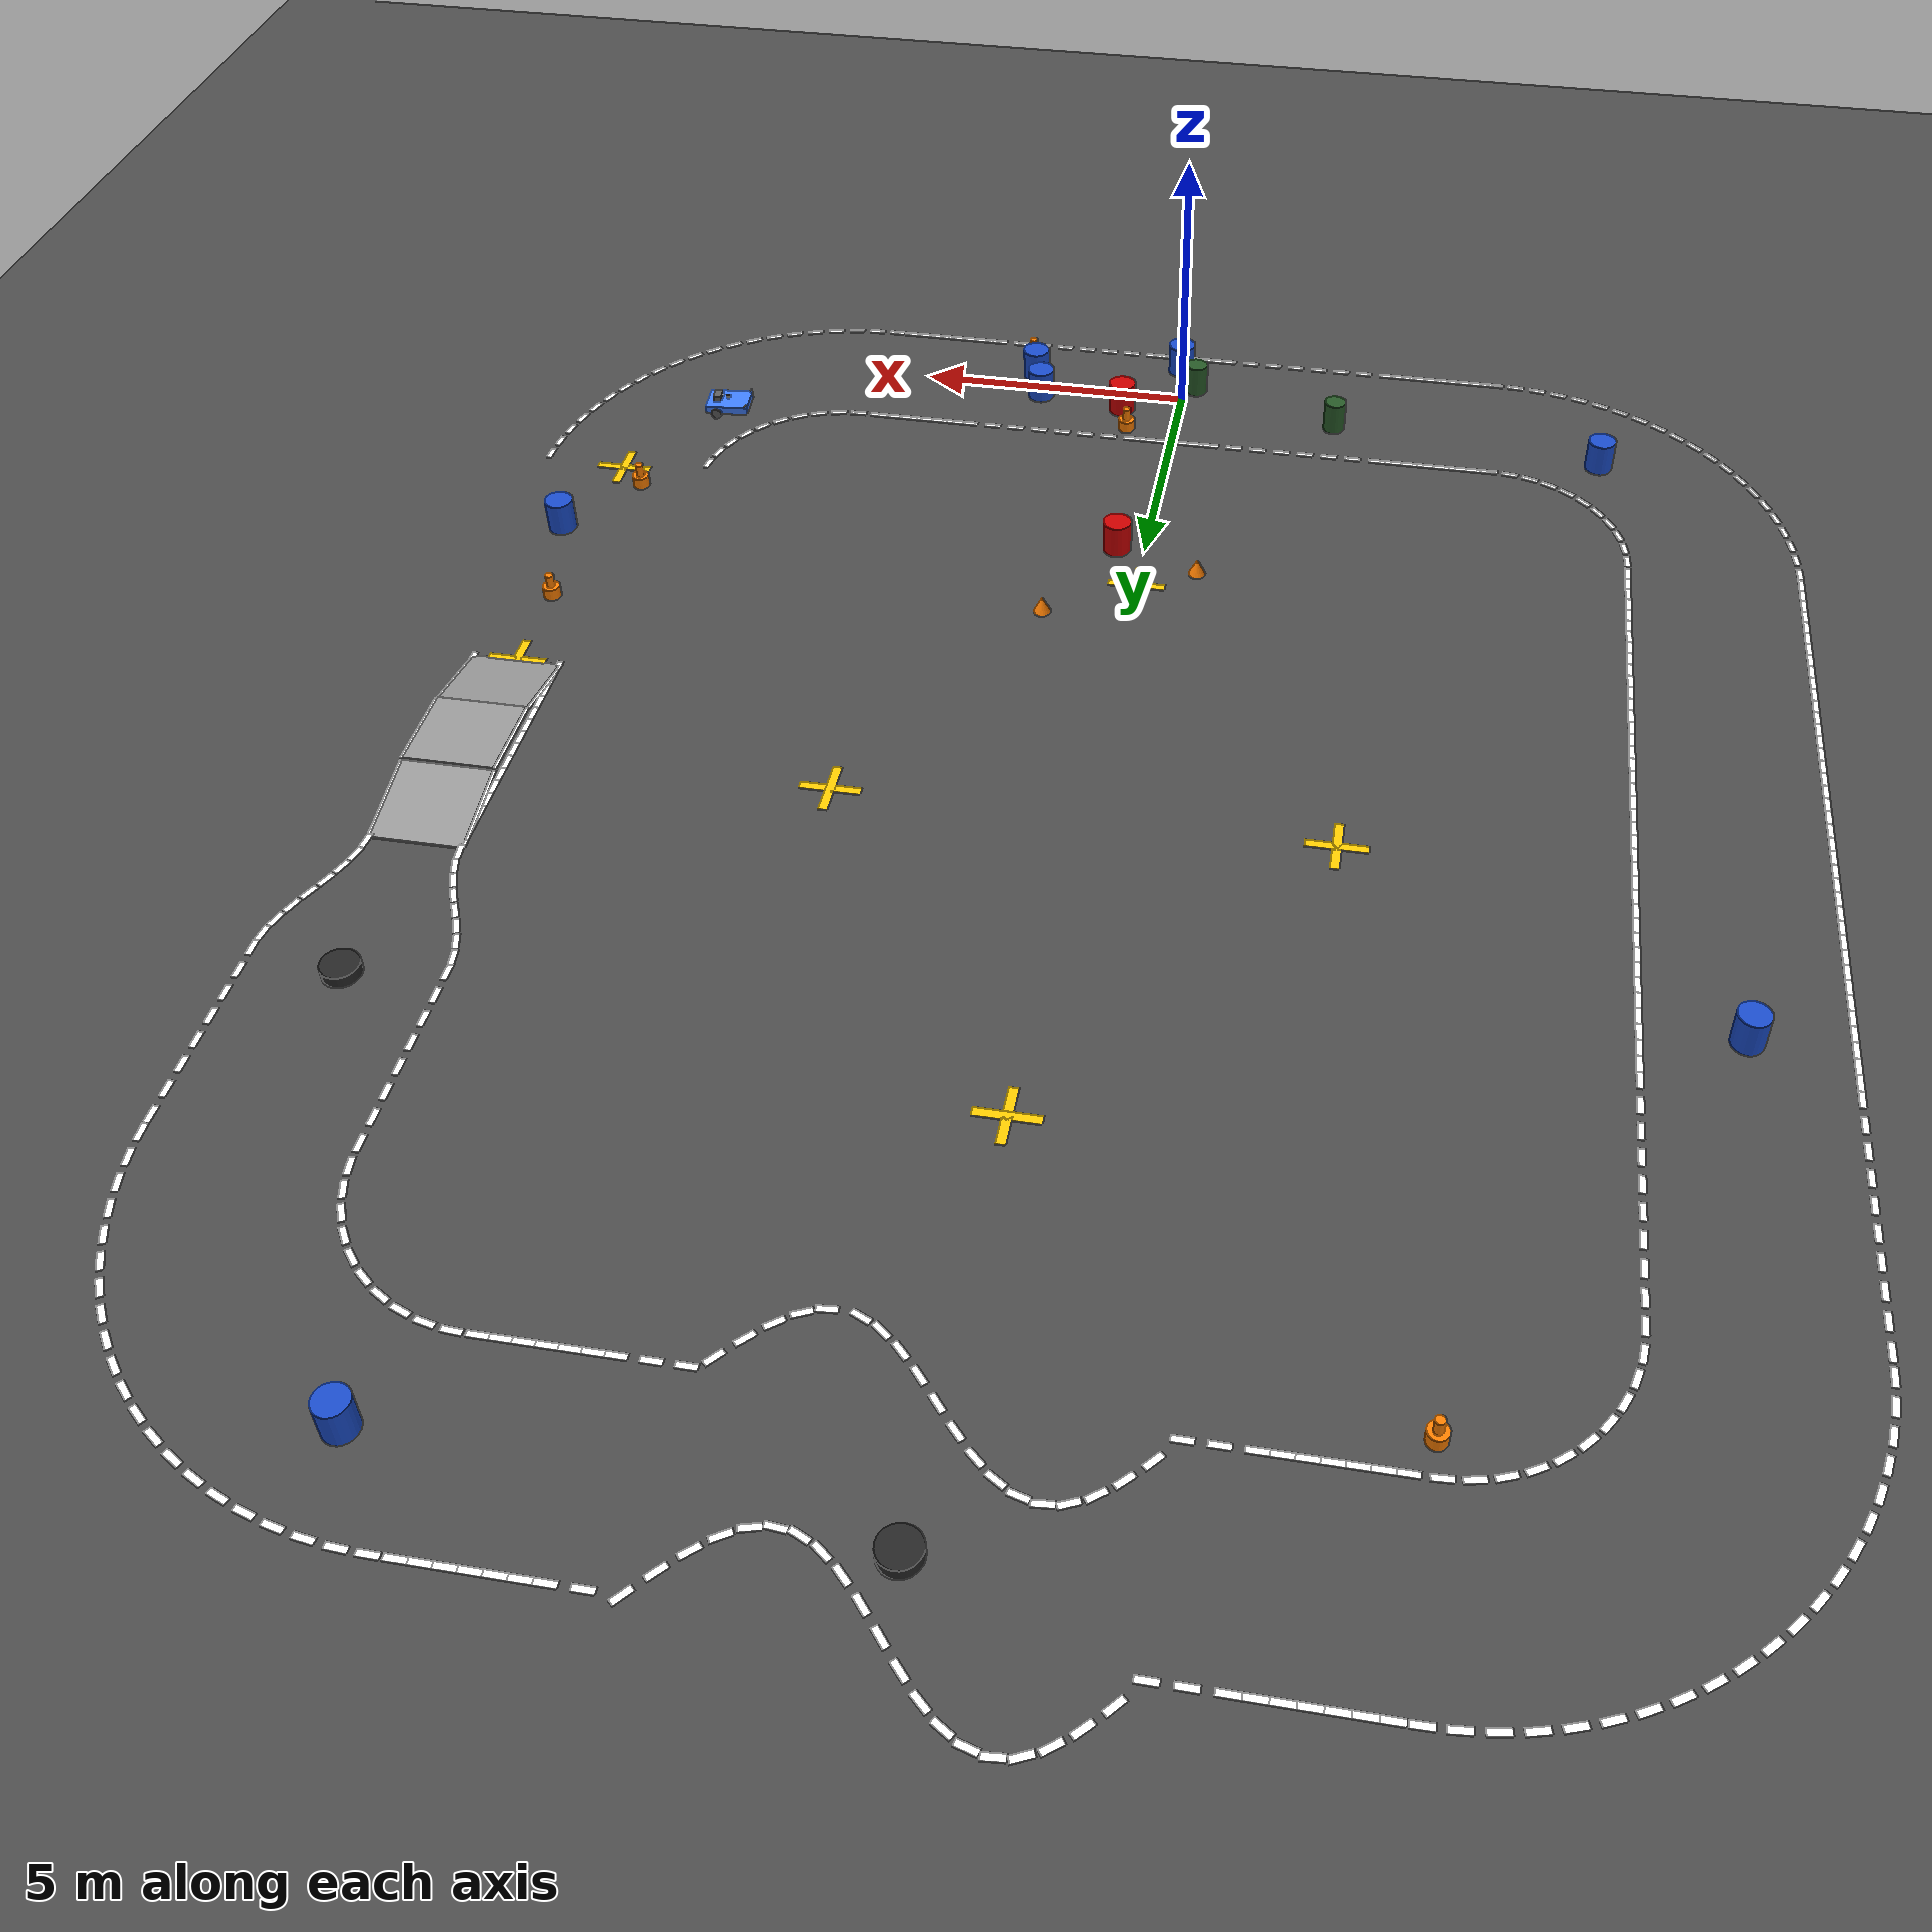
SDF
<sdf version='1.10'>
  <world name='igvc_autonav'>
    <physics name='dart_physics' type='dart'>
      <max_step_size>0.0060000000000000001</max_step_size>
      <real_time_factor>1</real_time_factor>
      <real_time_update_rate>1000</real_time_update_rate>
    </physics>
    <spherical_coordinates>
      <surface_model>EARTH_WGS84</surface_model>
      <latitude_deg>42.674500000000002</latitude_deg>
      <longitude_deg>-83.218699999999998</longitude_deg>
      <elevation>282</elevation>
      <heading_deg>0</heading_deg>
    </spherical_coordinates>
    <plugin name='ignition::gazebo::systems::Physics' filename='ignition-gazebo-physics-system'/>
    <plugin name='ignition::gazebo::systems::Sensors' filename='ignition-gazebo-sensors-system'>
      <render_engine>ogre2</render_engine>
    </plugin>
    <plugin name='ignition::gazebo::systems::Imu' filename='ignition-gazebo-imu-system'/>
    <plugin name='ignition::gazebo::systems::NavSat' filename='ignition-gazebo-navsat-system'/>
    <plugin name='ignition::gazebo::systems::SceneBroadcaster' filename='ignition-gazebo-scene-broadcaster-system'/>
    <plugin name='ignition::gazebo::systems::UserCommands' filename='ignition-gazebo-user-commands-system'/>
    <gravity>0 0 -9.8000000000000007</gravity>
    <magnetic_field>5.5644999999999998e-06 2.2875799999999999e-05 -4.2388400000000002e-05</magnetic_field>
    <atmosphere type='adiabatic'/>
    <scene>
      <ambient>0.400000006 0.400000006 0.400000006 1</ambient>
      <background>0.699999988 0.699999988 0.699999988 1</background>
      <shadows>true</shadows>
    </scene>
    <model name='ground_plane'>
      <static>true</static>
      <link name='link'>
        <collision name='collision'>
          <geometry>
            <plane>
              <normal>0 0 1</normal>
              <size>60 60</size>
            </plane>
          </geometry>
          <surface>
            <friction>
              <ode>
                <mu>0.80000000000000004</mu>
                <mu2>0.80000000000000004</mu2>
              </ode>
            </friction>
            <bounce/>
            <contact/>
          </surface>
        </collision>
        <visual name='visual'>
          <geometry>
            <plane>
              <normal>0 0 1</normal>
              <size>60 60</size>
            </plane>
          </geometry>
          <material>
            <ambient>0.25 0.25 0.25 1</ambient>
            <diffuse>0.300000012 0.300000012 0.300000012 1</diffuse>
            <specular>0.100000001 0.100000001 0.100000001 1</specular>
          </material>
        </visual>
        <pose>0 0 0 0 0 0</pose>
        <inertial>
          <pose>0 0 0 0 0 0</pose>
          <mass>1</mass>
          <inertia>
            <ixx>1</ixx>
            <ixy>0</ixy>
            <ixz>0</ixz>
            <iyy>1</iyy>
            <iyz>0</iyz>
            <izz>1</izz>
          </inertia>
        </inertial>
        <enable_wind>false</enable_wind>
      </link>
      <pose>0 0 0 0 0 0</pose>
      <self_collide>false</self_collide>
    </model>
    <model name='lane_inner_0'>
      <static>true</static>
      <pose>-6 1.5 0.01 0 0 0</pose>
      <link name='link'>
        <visual name='visual'>
          <geometry>
            <box>
              <size>0.29999999999999999 0.10000000000000001 0.01</size>
            </box>
          </geometry>
          <material>
            <ambient>1 1 1 1</ambient>
            <diffuse>1 1 1 1</diffuse>
            <emissive>1 1 1 1</emissive>
          </material>
        </visual>
        <pose>0 0 0 0 0 0</pose>
        <inertial>
          <pose>0 0 0 0 0 0</pose>
          <mass>1</mass>
          <inertia>
            <ixx>1</ixx>
            <ixy>0</ixy>
            <ixz>0</ixz>
            <iyy>1</iyy>
            <iyz>0</iyz>
            <izz>1</izz>
          </inertia>
        </inertial>
        <enable_wind>false</enable_wind>
      </link>
      <self_collide>false</self_collide>
    </model>
    <model name='lane_inner_1'>
      <static>true</static>
      <pose>-5.7000000000000002 1.5 0.01 0 0 0</pose>
      <link name='link'>
        <visual name='visual'>
          <geometry>
            <box>
              <size>0.29999999999999999 0.10000000000000001 0.01</size>
            </box>
          </geometry>
          <material>
            <ambient>1 1 1 1</ambient>
            <diffuse>1 1 1 1</diffuse>
            <emissive>1 1 1 1</emissive>
          </material>
        </visual>
        <pose>0 0 0 0 0 0</pose>
        <inertial>
          <pose>0 0 0 0 0 0</pose>
          <mass>1</mass>
          <inertia>
            <ixx>1</ixx>
            <ixy>0</ixy>
            <ixz>0</ixz>
            <iyy>1</iyy>
            <iyz>0</iyz>
            <izz>1</izz>
          </inertia>
        </inertial>
        <enable_wind>false</enable_wind>
      </link>
      <self_collide>false</self_collide>
    </model>
    <model name='lane_inner_2'>
      <static>true</static>
      <pose>-5.4000000000000004 1.5 0.01 0 0 0</pose>
      <link name='link'>
        <visual name='visual'>
          <geometry>
            <box>
              <size>0.29999999999999999 0.10000000000000001 0.01</size>
            </box>
          </geometry>
          <material>
            <ambient>1 1 1 1</ambient>
            <diffuse>1 1 1 1</diffuse>
            <emissive>1 1 1 1</emissive>
          </material>
        </visual>
        <pose>0 0 0 0 0 0</pose>
        <inertial>
          <pose>0 0 0 0 0 0</pose>
          <mass>1</mass>
          <inertia>
            <ixx>1</ixx>
            <ixy>0</ixy>
            <ixz>0</ixz>
            <iyy>1</iyy>
            <iyz>0</iyz>
            <izz>1</izz>
          </inertia>
        </inertial>
        <enable_wind>false</enable_wind>
      </link>
      <self_collide>false</self_collide>
    </model>
    <model name='lane_inner_3'>
      <static>true</static>
      <pose>-5.0999999999999996 1.5 0.01 0 0 0</pose>
      <link name='link'>
        <visual name='visual'>
          <geometry>
            <box>
              <size>0.29999999999999999 0.10000000000000001 0.01</size>
            </box>
          </geometry>
          <material>
            <ambient>1 1 1 1</ambient>
            <diffuse>1 1 1 1</diffuse>
            <emissive>1 1 1 1</emissive>
          </material>
        </visual>
        <pose>0 0 0 0 0 0</pose>
        <inertial>
          <pose>0 0 0 0 0 0</pose>
          <mass>1</mass>
          <inertia>
            <ixx>1</ixx>
            <ixy>0</ixy>
            <ixz>0</ixz>
            <iyy>1</iyy>
            <iyz>0</iyz>
            <izz>1</izz>
          </inertia>
        </inertial>
        <enable_wind>false</enable_wind>
      </link>
      <self_collide>false</self_collide>
    </model>
    <model name='lane_inner_4'>
      <static>true</static>
      <pose>-4.7999999999999998 1.5 0.01 0 0 0</pose>
      <link name='link'>
        <visual name='visual'>
          <geometry>
            <box>
              <size>0.29999999999999999 0.10000000000000001 0.01</size>
            </box>
          </geometry>
          <material>
            <ambient>1 1 1 1</ambient>
            <diffuse>1 1 1 1</diffuse>
            <emissive>1 1 1 1</emissive>
          </material>
        </visual>
        <pose>0 0 0 0 0 0</pose>
        <inertial>
          <pose>0 0 0 0 0 0</pose>
          <mass>1</mass>
          <inertia>
            <ixx>1</ixx>
            <ixy>0</ixy>
            <ixz>0</ixz>
            <iyy>1</iyy>
            <iyz>0</iyz>
            <izz>1</izz>
          </inertia>
        </inertial>
        <enable_wind>false</enable_wind>
      </link>
      <self_collide>false</self_collide>
    </model>
    <model name='lane_inner_5'>
      <static>true</static>
      <pose>-4.5 1.5 0.01 0 0 0</pose>
      <link name='link'>
        <visual name='visual'>
          <geometry>
            <box>
              <size>0.29999999999999999 0.10000000000000001 0.01</size>
            </box>
          </geometry>
          <material>
            <ambient>1 1 1 1</ambient>
            <diffuse>1 1 1 1</diffuse>
            <emissive>1 1 1 1</emissive>
          </material>
        </visual>
        <pose>0 0 0 0 0 0</pose>
        <inertial>
          <pose>0 0 0 0 0 0</pose>
          <mass>1</mass>
          <inertia>
            <ixx>1</ixx>
            <ixy>0</ixy>
            <ixz>0</ixz>
            <iyy>1</iyy>
            <iyz>0</iyz>
            <izz>1</izz>
          </inertia>
        </inertial>
        <enable_wind>false</enable_wind>
      </link>
      <self_collide>false</self_collide>
    </model>
    <model name='lane_inner_6'>
      <static>true</static>
      <pose>-4.2000000000000002 1.5 0.01 0 0 0</pose>
      <link name='link'>
        <visual name='visual'>
          <geometry>
            <box>
              <size>0.29999999999999999 0.10000000000000001 0.01</size>
            </box>
          </geometry>
          <material>
            <ambient>1 1 1 1</ambient>
            <diffuse>1 1 1 1</diffuse>
            <emissive>1 1 1 1</emissive>
          </material>
        </visual>
        <pose>0 0 0 0 0 0</pose>
        <inertial>
          <pose>0 0 0 0 0 0</pose>
          <mass>1</mass>
          <inertia>
            <ixx>1</ixx>
            <ixy>0</ixy>
            <ixz>0</ixz>
            <iyy>1</iyy>
            <iyz>0</iyz>
            <izz>1</izz>
          </inertia>
        </inertial>
        <enable_wind>false</enable_wind>
      </link>
      <self_collide>false</self_collide>
    </model>
    <model name='lane_inner_7'>
      <static>true</static>
      <pose>-3.8999999999999999 1.5 0.01 0 0 0</pose>
      <link name='link'>
        <visual name='visual'>
          <geometry>
            <box>
              <size>0.29999999999999999 0.10000000000000001 0.01</size>
            </box>
          </geometry>
          <material>
            <ambient>1 1 1 1</ambient>
            <diffuse>1 1 1 1</diffuse>
            <emissive>1 1 1 1</emissive>
          </material>
        </visual>
        <pose>0 0 0 0 0 0</pose>
        <inertial>
          <pose>0 0 0 0 0 0</pose>
          <mass>1</mass>
          <inertia>
            <ixx>1</ixx>
            <ixy>0</ixy>
            <ixz>0</ixz>
            <iyy>1</iyy>
            <iyz>0</iyz>
            <izz>1</izz>
          </inertia>
        </inertial>
        <enable_wind>false</enable_wind>
      </link>
      <self_collide>false</self_collide>
    </model>
    <model name='lane_inner_8'>
      <static>true</static>
      <pose>-3.4500000000000002 1.5 0.01 0 0 0</pose>
      <link name='link'>
        <visual name='visual'>
          <geometry>
            <box>
              <size>0.29999999999999999 0.10000000000000001 0.01</size>
            </box>
          </geometry>
          <material>
            <ambient>1 1 1 1</ambient>
            <diffuse>1 1 1 1</diffuse>
            <emissive>1 1 1 1</emissive>
          </material>
        </visual>
        <pose>0 0 0 0 0 0</pose>
        <inertial>
          <pose>0 0 0 0 0 0</pose>
          <mass>1</mass>
          <inertia>
            <ixx>1</ixx>
            <ixy>0</ixy>
            <ixz>0</ixz>
            <iyy>1</iyy>
            <iyz>0</iyz>
            <izz>1</izz>
          </inertia>
        </inertial>
        <enable_wind>false</enable_wind>
      </link>
      <self_collide>false</self_collide>
    </model>
    <model name='lane_inner_9'>
      <static>true</static>
      <pose>-3 1.5 0.01 0 0 0</pose>
      <link name='link'>
        <visual name='visual'>
          <geometry>
            <box>
              <size>0.29999999999999999 0.10000000000000001 0.01</size>
            </box>
          </geometry>
          <material>
            <ambient>1 1 1 1</ambient>
            <diffuse>1 1 1 1</diffuse>
            <emissive>1 1 1 1</emissive>
          </material>
        </visual>
        <pose>0 0 0 0 0 0</pose>
        <inertial>
          <pose>0 0 0 0 0 0</pose>
          <mass>1</mass>
          <inertia>
            <ixx>1</ixx>
            <ixy>0</ixy>
            <ixz>0</ixz>
            <iyy>1</iyy>
            <iyz>0</iyz>
            <izz>1</izz>
          </inertia>
        </inertial>
        <enable_wind>false</enable_wind>
      </link>
      <self_collide>false</self_collide>
    </model>
    <model name='lane_inner_10'>
      <static>true</static>
      <pose>-2.5499999999999998 1.5 0.01 0 0 0</pose>
      <link name='link'>
        <visual name='visual'>
          <geometry>
            <box>
              <size>0.29999999999999999 0.10000000000000001 0.01</size>
            </box>
          </geometry>
          <material>
            <ambient>1 1 1 1</ambient>
            <diffuse>1 1 1 1</diffuse>
            <emissive>1 1 1 1</emissive>
          </material>
        </visual>
        <pose>0 0 0 0 0 0</pose>
        <inertial>
          <pose>0 0 0 0 0 0</pose>
          <mass>1</mass>
          <inertia>
            <ixx>1</ixx>
            <ixy>0</ixy>
            <ixz>0</ixz>
            <iyy>1</iyy>
            <iyz>0</iyz>
            <izz>1</izz>
          </inertia>
        </inertial>
        <enable_wind>false</enable_wind>
      </link>
      <self_collide>false</self_collide>
    </model>
    <model name='lane_inner_11'>
      <static>true</static>
      <pose>-2.1000000000000001 1.5 0.01 0 0 0</pose>
      <link name='link'>
        <visual name='visual'>
          <geometry>
            <box>
              <size>0.29999999999999999 0.10000000000000001 0.01</size>
            </box>
          </geometry>
          <material>
            <ambient>1 1 1 1</ambient>
            <diffuse>1 1 1 1</diffuse>
            <emissive>1 1 1 1</emissive>
          </material>
        </visual>
        <pose>0 0 0 0 0 0</pose>
        <inertial>
          <pose>0 0 0 0 0 0</pose>
          <mass>1</mass>
          <inertia>
            <ixx>1</ixx>
            <ixy>0</ixy>
            <ixz>0</ixz>
            <iyy>1</iyy>
            <iyz>0</iyz>
            <izz>1</izz>
          </inertia>
        </inertial>
        <enable_wind>false</enable_wind>
      </link>
      <self_collide>false</self_collide>
    </model>
    <model name='lane_inner_12'>
      <static>true</static>
      <pose>-1.6499999999999999 1.5 0.01 0 0 0</pose>
      <link name='link'>
        <visual name='visual'>
          <geometry>
            <box>
              <size>0.29999999999999999 0.10000000000000001 0.01</size>
            </box>
          </geometry>
          <material>
            <ambient>1 1 1 1</ambient>
            <diffuse>1 1 1 1</diffuse>
            <emissive>1 1 1 1</emissive>
          </material>
        </visual>
        <pose>0 0 0 0 0 0</pose>
        <inertial>
          <pose>0 0 0 0 0 0</pose>
          <mass>1</mass>
          <inertia>
            <ixx>1</ixx>
            <ixy>0</ixy>
            <ixz>0</ixz>
            <iyy>1</iyy>
            <iyz>0</iyz>
            <izz>1</izz>
          </inertia>
        </inertial>
        <enable_wind>false</enable_wind>
      </link>
      <self_collide>false</self_collide>
    </model>
    <model name='lane_inner_13'>
      <static>true</static>
      <pose>-1.2 1.5 0.01 0 0 0</pose>
      <link name='link'>
        <visual name='visual'>
          <geometry>
            <box>
              <size>0.29999999999999999 0.10000000000000001 0.01</size>
            </box>
          </geometry>
          <material>
            <ambient>1 1 1 1</ambient>
            <diffuse>1 1 1 1</diffuse>
            <emissive>1 1 1 1</emissive>
          </material>
        </visual>
        <pose>0 0 0 0 0 0</pose>
        <inertial>
          <pose>0 0 0 0 0 0</pose>
          <mass>1</mass>
          <inertia>
            <ixx>1</ixx>
            <ixy>0</ixy>
            <ixz>0</ixz>
            <iyy>1</iyy>
            <iyz>0</iyz>
            <izz>1</izz>
          </inertia>
        </inertial>
        <enable_wind>false</enable_wind>
      </link>
      <self_collide>false</self_collide>
    </model>
    <model name='lane_inner_14'>
      <static>true</static>
      <pose>-0.75 1.5 0.01 0 0 0</pose>
      <link name='link'>
        <visual name='visual'>
          <geometry>
            <box>
              <size>0.29999999999999999 0.10000000000000001 0.01</size>
            </box>
          </geometry>
          <material>
            <ambient>1 1 1 1</ambient>
            <diffuse>1 1 1 1</diffuse>
            <emissive>1 1 1 1</emissive>
          </material>
        </visual>
        <pose>0 0 0 0 0 0</pose>
        <inertial>
          <pose>0 0 0 0 0 0</pose>
          <mass>1</mass>
          <inertia>
            <ixx>1</ixx>
            <ixy>0</ixy>
            <ixz>0</ixz>
            <iyy>1</iyy>
            <iyz>0</iyz>
            <izz>1</izz>
          </inertia>
        </inertial>
        <enable_wind>false</enable_wind>
      </link>
      <self_collide>false</self_collide>
    </model>
    <model name='lane_inner_15'>
      <static>true</static>
      <pose>-0.45000000000000001 1.5 0.01 0 0 0</pose>
      <link name='link'>
        <visual name='visual'>
          <geometry>
            <box>
              <size>0.29999999999999999 0.10000000000000001 0.01</size>
            </box>
          </geometry>
          <material>
            <ambient>1 1 1 1</ambient>
            <diffuse>1 1 1 1</diffuse>
            <emissive>1 1 1 1</emissive>
          </material>
        </visual>
        <pose>0 0 0 0 0 0</pose>
        <inertial>
          <pose>0 0 0 0 0 0</pose>
          <mass>1</mass>
          <inertia>
            <ixx>1</ixx>
            <ixy>0</ixy>
            <ixz>0</ixz>
            <iyy>1</iyy>
            <iyz>0</iyz>
            <izz>1</izz>
          </inertia>
        </inertial>
        <enable_wind>false</enable_wind>
      </link>
      <self_collide>false</self_collide>
    </model>
    <model name='lane_inner_16'>
      <static>true</static>
      <pose>-0.14999999999999999 1.5 0.01 0 0 0</pose>
      <link name='link'>
        <visual name='visual'>
          <geometry>
            <box>
              <size>0.29999999999999999 0.10000000000000001 0.01</size>
            </box>
          </geometry>
          <material>
            <ambient>1 1 1 1</ambient>
            <diffuse>1 1 1 1</diffuse>
            <emissive>1 1 1 1</emissive>
          </material>
        </visual>
        <pose>0 0 0 0 0 0</pose>
        <inertial>
          <pose>0 0 0 0 0 0</pose>
          <mass>1</mass>
          <inertia>
            <ixx>1</ixx>
            <ixy>0</ixy>
            <ixz>0</ixz>
            <iyy>1</iyy>
            <iyz>0</iyz>
            <izz>1</izz>
          </inertia>
        </inertial>
        <enable_wind>false</enable_wind>
      </link>
      <self_collide>false</self_collide>
    </model>
    <model name='lane_inner_17'>
      <static>true</static>
      <pose>0.14999999999999999 1.5 0.01 0 0 0</pose>
      <link name='link'>
        <visual name='visual'>
          <geometry>
            <box>
              <size>0.29999999999999999 0.10000000000000001 0.01</size>
            </box>
          </geometry>
          <material>
            <ambient>1 1 1 1</ambient>
            <diffuse>1 1 1 1</diffuse>
            <emissive>1 1 1 1</emissive>
          </material>
        </visual>
        <pose>0 0 0 0 0 0</pose>
        <inertial>
          <pose>0 0 0 0 0 0</pose>
          <mass>1</mass>
          <inertia>
            <ixx>1</ixx>
            <ixy>0</ixy>
            <ixz>0</ixz>
            <iyy>1</iyy>
            <iyz>0</iyz>
            <izz>1</izz>
          </inertia>
        </inertial>
        <enable_wind>false</enable_wind>
      </link>
      <self_collide>false</self_collide>
    </model>
    <model name='lane_inner_18'>
      <static>true</static>
      <pose>0.45000000000000001 1.5 0.01 0 0 0</pose>
      <link name='link'>
        <visual name='visual'>
          <geometry>
            <box>
              <size>0.29999999999999999 0.10000000000000001 0.01</size>
            </box>
          </geometry>
          <material>
            <ambient>1 1 1 1</ambient>
            <diffuse>1 1 1 1</diffuse>
            <emissive>1 1 1 1</emissive>
          </material>
        </visual>
        <pose>0 0 0 0 0 0</pose>
        <inertial>
          <pose>0 0 0 0 0 0</pose>
          <mass>1</mass>
          <inertia>
            <ixx>1</ixx>
            <ixy>0</ixy>
            <ixz>0</ixz>
            <iyy>1</iyy>
            <iyz>0</iyz>
            <izz>1</izz>
          </inertia>
        </inertial>
        <enable_wind>false</enable_wind>
      </link>
      <self_collide>false</self_collide>
    </model>
    <model name='lane_inner_19'>
      <static>true</static>
      <pose>0.75 1.5 0.01 0 0 0</pose>
      <link name='link'>
        <visual name='visual'>
          <geometry>
            <box>
              <size>0.29999999999999999 0.10000000000000001 0.01</size>
            </box>
          </geometry>
          <material>
            <ambient>1 1 1 1</ambient>
            <diffuse>1 1 1 1</diffuse>
            <emissive>1 1 1 1</emissive>
          </material>
        </visual>
        <pose>0 0 0 0 0 0</pose>
        <inertial>
          <pose>0 0 0 0 0 0</pose>
          <mass>1</mass>
          <inertia>
            <ixx>1</ixx>
            <ixy>0</ixy>
            <ixz>0</ixz>
            <iyy>1</iyy>
            <iyz>0</iyz>
            <izz>1</izz>
          </inertia>
        </inertial>
        <enable_wind>false</enable_wind>
      </link>
      <self_collide>false</self_collide>
    </model>
    <model name='lane_inner_20'>
      <static>true</static>
      <pose>1.2 1.5 0.01 0 0 0</pose>
      <link name='link'>
        <visual name='visual'>
          <geometry>
            <box>
              <size>0.29999999999999999 0.10000000000000001 0.01</size>
            </box>
          </geometry>
          <material>
            <ambient>1 1 1 1</ambient>
            <diffuse>1 1 1 1</diffuse>
            <emissive>1 1 1 1</emissive>
          </material>
        </visual>
        <pose>0 0 0 0 0 0</pose>
        <inertial>
          <pose>0 0 0 0 0 0</pose>
          <mass>1</mass>
          <inertia>
            <ixx>1</ixx>
            <ixy>0</ixy>
            <ixz>0</ixz>
            <iyy>1</iyy>
            <iyz>0</iyz>
            <izz>1</izz>
          </inertia>
        </inertial>
        <enable_wind>false</enable_wind>
      </link>
      <self_collide>false</self_collide>
    </model>
    <model name='lane_inner_21'>
      <static>true</static>
      <pose>1.6499999999999999 1.5 0.01 0 0 0</pose>
      <link name='link'>
        <visual name='visual'>
          <geometry>
            <box>
              <size>0.29999999999999999 0.10000000000000001 0.01</size>
            </box>
          </geometry>
          <material>
            <ambient>1 1 1 1</ambient>
            <diffuse>1 1 1 1</diffuse>
            <emissive>1 1 1 1</emissive>
          </material>
        </visual>
        <pose>0 0 0 0 0 0</pose>
        <inertial>
          <pose>0 0 0 0 0 0</pose>
          <mass>1</mass>
          <inertia>
            <ixx>1</ixx>
            <ixy>0</ixy>
            <ixz>0</ixz>
            <iyy>1</iyy>
            <iyz>0</iyz>
            <izz>1</izz>
          </inertia>
        </inertial>
        <enable_wind>false</enable_wind>
      </link>
      <self_collide>false</self_collide>
    </model>
    <model name='lane_inner_22'>
      <static>true</static>
      <pose>2.1000000000000001 1.5 0.01 0 0 0</pose>
      <link name='link'>
        <visual name='visual'>
          <geometry>
            <box>
              <size>0.29999999999999999 0.10000000000000001 0.01</size>
            </box>
          </geometry>
          <material>
            <ambient>1 1 1 1</ambient>
            <diffuse>1 1 1 1</diffuse>
            <emissive>1 1 1 1</emissive>
          </material>
        </visual>
        <pose>0 0 0 0 0 0</pose>
        <inertial>
          <pose>0 0 0 0 0 0</pose>
          <mass>1</mass>
          <inertia>
            <ixx>1</ixx>
            <ixy>0</ixy>
            <ixz>0</ixz>
            <iyy>1</iyy>
            <iyz>0</iyz>
            <izz>1</izz>
          </inertia>
        </inertial>
        <enable_wind>false</enable_wind>
      </link>
      <self_collide>false</self_collide>
    </model>
    <model name='lane_inner_23'>
      <static>true</static>
      <pose>2.5499999999999998 1.5 0.01 0 0 0</pose>
      <link name='link'>
        <visual name='visual'>
          <geometry>
            <box>
              <size>0.29999999999999999 0.10000000000000001 0.01</size>
            </box>
          </geometry>
          <material>
            <ambient>1 1 1 1</ambient>
            <diffuse>1 1 1 1</diffuse>
            <emissive>1 1 1 1</emissive>
          </material>
        </visual>
        <pose>0 0 0 0 0 0</pose>
        <inertial>
          <pose>0 0 0 0 0 0</pose>
          <mass>1</mass>
          <inertia>
            <ixx>1</ixx>
            <ixy>0</ixy>
            <ixz>0</ixz>
            <iyy>1</iyy>
            <iyz>0</iyz>
            <izz>1</izz>
          </inertia>
        </inertial>
        <enable_wind>false</enable_wind>
      </link>
      <self_collide>false</self_collide>
    </model>
    <model name='lane_inner_24'>
      <static>true</static>
      <pose>3 1.5 0.01 0 0 0</pose>
      <link name='link'>
        <visual name='visual'>
          <geometry>
            <box>
              <size>0.29999999999999999 0.10000000000000001 0.01</size>
            </box>
          </geometry>
          <material>
            <ambient>1 1 1 1</ambient>
            <diffuse>1 1 1 1</diffuse>
            <emissive>1 1 1 1</emissive>
          </material>
        </visual>
        <pose>0 0 0 0 0 0</pose>
        <inertial>
          <pose>0 0 0 0 0 0</pose>
          <mass>1</mass>
          <inertia>
            <ixx>1</ixx>
            <ixy>0</ixy>
            <ixz>0</ixz>
            <iyy>1</iyy>
            <iyz>0</iyz>
            <izz>1</izz>
          </inertia>
        </inertial>
        <enable_wind>false</enable_wind>
      </link>
      <self_collide>false</self_collide>
    </model>
    <model name='lane_inner_25'>
      <static>true</static>
      <pose>3.4500000000000002 1.5 0.01 0 0 0</pose>
      <link name='link'>
        <visual name='visual'>
          <geometry>
            <box>
              <size>0.29999999999999999 0.10000000000000001 0.01</size>
            </box>
          </geometry>
          <material>
            <ambient>1 1 1 1</ambient>
            <diffuse>1 1 1 1</diffuse>
            <emissive>1 1 1 1</emissive>
          </material>
        </visual>
        <pose>0 0 0 0 0 0</pose>
        <inertial>
          <pose>0 0 0 0 0 0</pose>
          <mass>1</mass>
          <inertia>
            <ixx>1</ixx>
            <ixy>0</ixy>
            <ixz>0</ixz>
            <iyy>1</iyy>
            <iyz>0</iyz>
            <izz>1</izz>
          </inertia>
        </inertial>
        <enable_wind>false</enable_wind>
      </link>
      <self_collide>false</self_collide>
    </model>
    <model name='lane_inner_26'>
      <static>true</static>
      <pose>3.8999999999999999 1.5 0.01 0 0 0</pose>
      <link name='link'>
        <visual name='visual'>
          <geometry>
            <box>
              <size>0.29999999999999999 0.10000000000000001 0.01</size>
            </box>
          </geometry>
          <material>
            <ambient>1 1 1 1</ambient>
            <diffuse>1 1 1 1</diffuse>
            <emissive>1 1 1 1</emissive>
          </material>
        </visual>
        <pose>0 0 0 0 0 0</pose>
        <inertial>
          <pose>0 0 0 0 0 0</pose>
          <mass>1</mass>
          <inertia>
            <ixx>1</ixx>
            <ixy>0</ixy>
            <ixz>0</ixz>
            <iyy>1</iyy>
            <iyz>0</iyz>
            <izz>1</izz>
          </inertia>
        </inertial>
        <enable_wind>false</enable_wind>
      </link>
      <self_collide>false</self_collide>
    </model>
    <model name='lane_inner_27'>
      <static>true</static>
      <pose>4.2000000000000002 1.5 0.01 0 0 0</pose>
      <link name='link'>
        <visual name='visual'>
          <geometry>
            <box>
              <size>0.29999999999999999 0.10000000000000001 0.01</size>
            </box>
          </geometry>
          <material>
            <ambient>1 1 1 1</ambient>
            <diffuse>1 1 1 1</diffuse>
            <emissive>1 1 1 1</emissive>
          </material>
        </visual>
        <pose>0 0 0 0 0 0</pose>
        <inertial>
          <pose>0 0 0 0 0 0</pose>
          <mass>1</mass>
          <inertia>
            <ixx>1</ixx>
            <ixy>0</ixy>
            <ixz>0</ixz>
            <iyy>1</iyy>
            <iyz>0</iyz>
            <izz>1</izz>
          </inertia>
        </inertial>
        <enable_wind>false</enable_wind>
      </link>
      <self_collide>false</self_collide>
    </model>
    <model name='lane_inner_28'>
      <static>true</static>
      <pose>4.5 1.5 0.01 0 0 0</pose>
      <link name='link'>
        <visual name='visual'>
          <geometry>
            <box>
              <size>0.29999999999999999 0.10000000000000001 0.01</size>
            </box>
          </geometry>
          <material>
            <ambient>1 1 1 1</ambient>
            <diffuse>1 1 1 1</diffuse>
            <emissive>1 1 1 1</emissive>
          </material>
        </visual>
        <pose>0 0 0 0 0 0</pose>
        <inertial>
          <pose>0 0 0 0 0 0</pose>
          <mass>1</mass>
          <inertia>
            <ixx>1</ixx>
            <ixy>0</ixy>
            <ixz>0</ixz>
            <iyy>1</iyy>
            <iyz>0</iyz>
            <izz>1</izz>
          </inertia>
        </inertial>
        <enable_wind>false</enable_wind>
      </link>
      <self_collide>false</self_collide>
    </model>
    <model name='lane_inner_29'>
      <static>true</static>
      <pose>4.7999999999999998 1.5 0.01 0 0 0</pose>
      <link name='link'>
        <visual name='visual'>
          <geometry>
            <box>
              <size>0.29999999999999999 0.10000000000000001 0.01</size>
            </box>
          </geometry>
          <material>
            <ambient>1 1 1 1</ambient>
            <diffuse>1 1 1 1</diffuse>
            <emissive>1 1 1 1</emissive>
          </material>
        </visual>
        <pose>0 0 0 0 0 0</pose>
        <inertial>
          <pose>0 0 0 0 0 0</pose>
          <mass>1</mass>
          <inertia>
            <ixx>1</ixx>
            <ixy>0</ixy>
            <ixz>0</ixz>
            <iyy>1</iyy>
            <iyz>0</iyz>
            <izz>1</izz>
          </inertia>
        </inertial>
        <enable_wind>false</enable_wind>
      </link>
      <self_collide>false</self_collide>
    </model>
    <model name='lane_inner_30'>
      <static>true</static>
      <pose>5.0999999999999996 1.5 0.01 0 0 0</pose>
      <link name='link'>
        <visual name='visual'>
          <geometry>
            <box>
              <size>0.29999999999999999 0.10000000000000001 0.01</size>
            </box>
          </geometry>
          <material>
            <ambient>1 1 1 1</ambient>
            <diffuse>1 1 1 1</diffuse>
            <emissive>1 1 1 1</emissive>
          </material>
        </visual>
        <pose>0 0 0 0 0 0</pose>
        <inertial>
          <pose>0 0 0 0 0 0</pose>
          <mass>1</mass>
          <inertia>
            <ixx>1</ixx>
            <ixy>0</ixy>
            <ixz>0</ixz>
            <iyy>1</iyy>
            <iyz>0</iyz>
            <izz>1</izz>
          </inertia>
        </inertial>
        <enable_wind>false</enable_wind>
      </link>
      <self_collide>false</self_collide>
    </model>
    <model name='lane_inner_31'>
      <static>true</static>
      <pose>5.4000000000000004 1.5 0.01 0 0 0</pose>
      <link name='link'>
        <visual name='visual'>
          <geometry>
            <box>
              <size>0.29999999999999999 0.10000000000000001 0.01</size>
            </box>
          </geometry>
          <material>
            <ambient>1 1 1 1</ambient>
            <diffuse>1 1 1 1</diffuse>
            <emissive>1 1 1 1</emissive>
          </material>
        </visual>
        <pose>0 0 0 0 0 0</pose>
        <inertial>
          <pose>0 0 0 0 0 0</pose>
          <mass>1</mass>
          <inertia>
            <ixx>1</ixx>
            <ixy>0</ixy>
            <ixz>0</ixz>
            <iyy>1</iyy>
            <iyz>0</iyz>
            <izz>1</izz>
          </inertia>
        </inertial>
        <enable_wind>false</enable_wind>
      </link>
      <self_collide>false</self_collide>
    </model>
    <model name='lane_inner_32'>
      <static>true</static>
      <pose>5.7000000000000002 1.5 0.01 0 0 0</pose>
      <link name='link'>
        <visual name='visual'>
          <geometry>
            <box>
              <size>0.29999999999999999 0.10000000000000001 0.01</size>
            </box>
          </geometry>
          <material>
            <ambient>1 1 1 1</ambient>
            <diffuse>1 1 1 1</diffuse>
            <emissive>1 1 1 1</emissive>
          </material>
        </visual>
        <pose>0 0 0 0 0 0</pose>
        <inertial>
          <pose>0 0 0 0 0 0</pose>
          <mass>1</mass>
          <inertia>
            <ixx>1</ixx>
            <ixy>0</ixy>
            <ixz>0</ixz>
            <iyy>1</iyy>
            <iyz>0</iyz>
            <izz>1</izz>
          </inertia>
        </inertial>
        <enable_wind>false</enable_wind>
      </link>
      <self_collide>false</self_collide>
    </model>
    <model name='lane_inner_33'>
      <static>true</static>
      <pose>6.0957999999999997 1.5018 0.01 0 0 0.057500000000000002</pose>
      <link name='link'>
        <visual name='visual'>
          <geometry>
            <box>
              <size>0.29999999999999999 0.10000000000000001 0.01</size>
            </box>
          </geometry>
          <material>
            <ambient>1 1 1 1</ambient>
            <diffuse>1 1 1 1</diffuse>
            <emissive>1 1 1 1</emissive>
          </material>
        </visual>
        <pose>0 0 0 0 0 0</pose>
        <inertial>
          <pose>0 0 0 0 0 0</pose>
          <mass>1</mass>
          <inertia>
            <ixx>1</ixx>
            <ixy>0</ixy>
            <ixz>0</ixz>
            <iyy>1</iyy>
            <iyz>0</iyz>
            <izz>1</izz>
          </inertia>
        </inertial>
        <enable_wind>false</enable_wind>
      </link>
      <self_collide>false</self_collide>
    </model>
    <model name='lane_inner_34'>
      <static>true</static>
      <pose>6.476 1.5457000000000001 0.01 0 0 0.2107</pose>
      <link name='link'>
        <visual name='visual'>
          <geometry>
            <box>
              <size>0.29999999999999999 0.10000000000000001 0.01</size>
            </box>
          </geometry>
          <material>
            <ambient>1 1 1 1</ambient>
            <diffuse>1 1 1 1</diffuse>
            <emissive>1 1 1 1</emissive>
          </material>
        </visual>
        <pose>0 0 0 0 0 0</pose>
        <inertial>
          <pose>0 0 0 0 0 0</pose>
          <mass>1</mass>
          <inertia>
            <ixx>1</ixx>
            <ixy>0</ixy>
            <ixz>0</ixz>
            <iyy>1</iyy>
            <iyz>0</iyz>
            <izz>1</izz>
          </inertia>
        </inertial>
        <enable_wind>false</enable_wind>
      </link>
      <self_collide>false</self_collide>
    </model>
    <model name='lane_inner_35'>
      <static>true</static>
      <pose>6.8449999999999998 1.6471 0.01 0 0 0.36399999999999999</pose>
      <link name='link'>
        <visual name='visual'>
          <geometry>
            <box>
              <size>0.29999999999999999 0.10000000000000001 0.01</size>
            </box>
          </geometry>
          <material>
            <ambient>1 1 1 1</ambient>
            <diffuse>1 1 1 1</diffuse>
            <emissive>1 1 1 1</emissive>
          </material>
        </visual>
        <pose>0 0 0 0 0 0</pose>
        <inertial>
          <pose>0 0 0 0 0 0</pose>
          <mass>1</mass>
          <inertia>
            <ixx>1</ixx>
            <ixy>0</ixy>
            <ixz>0</ixz>
            <iyy>1</iyy>
            <iyz>0</iyz>
            <izz>1</izz>
          </inertia>
        </inertial>
        <enable_wind>false</enable_wind>
      </link>
      <self_collide>false</self_collide>
    </model>
    <model name='lane_inner_36'>
      <static>true</static>
      <pose>7.1943000000000001 1.8037000000000001 0.01 0 0 0.51720000000000022</pose>
      <link name='link'>
        <visual name='visual'>
          <geometry>
            <box>
              <size>0.29999999999999999 0.10000000000000001 0.01</size>
            </box>
          </geometry>
          <material>
            <ambient>1 1 1 1</ambient>
            <diffuse>1 1 1 1</diffuse>
            <emissive>1 1 1 1</emissive>
          </material>
        </visual>
        <pose>0 0 0 0 0 0</pose>
        <inertial>
          <pose>0 0 0 0 0 0</pose>
          <mass>1</mass>
          <inertia>
            <ixx>1</ixx>
            <ixy>0</ixy>
            <ixz>0</ixz>
            <iyy>1</iyy>
            <iyz>0</iyz>
            <izz>1</izz>
          </inertia>
        </inertial>
        <enable_wind>false</enable_wind>
      </link>
      <self_collide>false</self_collide>
    </model>
    <model name='lane_inner_37'>
      <static>true</static>
      <pose>7.5156000000000001 2.0118 0.01 0 0 0.67049999999999998</pose>
      <link name='link'>
        <visual name='visual'>
          <geometry>
            <box>
              <size>0.29999999999999999 0.10000000000000001 0.01</size>
            </box>
          </geometry>
          <material>
            <ambient>1 1 1 1</ambient>
            <diffuse>1 1 1 1</diffuse>
            <emissive>1 1 1 1</emissive>
          </material>
        </visual>
        <pose>0 0 0 0 0 0</pose>
        <inertial>
          <pose>0 0 0 0 0 0</pose>
          <mass>1</mass>
          <inertia>
            <ixx>1</ixx>
            <ixy>0</ixy>
            <ixz>0</ixz>
            <iyy>1</iyy>
            <iyz>0</iyz>
            <izz>1</izz>
          </inertia>
        </inertial>
        <enable_wind>false</enable_wind>
      </link>
      <self_collide>false</self_collide>
    </model>
    <model name='lane_inner_38'>
      <static>true</static>
      <pose>7.8013000000000003 2.2664 0.01 0 0 0.82369999999999999</pose>
      <link name='link'>
        <visual name='visual'>
          <geometry>
            <box>
              <size>0.29999999999999999 0.10000000000000001 0.01</size>
            </box>
          </geometry>
          <material>
            <ambient>1 1 1 1</ambient>
            <diffuse>1 1 1 1</diffuse>
            <emissive>1 1 1 1</emissive>
          </material>
        </visual>
        <pose>0 0 0 0 0 0</pose>
        <inertial>
          <pose>0 0 0 0 0 0</pose>
          <mass>1</mass>
          <inertia>
            <ixx>1</ixx>
            <ixy>0</ixy>
            <ixz>0</ixz>
            <iyy>1</iyy>
            <iyz>0</iyz>
            <izz>1</izz>
          </inertia>
        </inertial>
        <enable_wind>false</enable_wind>
      </link>
      <self_collide>false</self_collide>
    </model>
    <model name='lane_inner_39'>
      <static>true</static>
      <pose>8.0448000000000004 2.5617000000000001 0.01 0 0 0.9770000000000002</pose>
      <link name='link'>
        <visual name='visual'>
          <geometry>
            <box>
              <size>0.29999999999999999 0.10000000000000001 0.01</size>
            </box>
          </geometry>
          <material>
            <ambient>1 1 1 1</ambient>
            <diffuse>1 1 1 1</diffuse>
            <emissive>1 1 1 1</emissive>
          </material>
        </visual>
        <pose>0 0 0 0 0 0</pose>
        <inertial>
          <pose>0 0 0 0 0 0</pose>
          <mass>1</mass>
          <inertia>
            <ixx>1</ixx>
            <ixy>0</ixy>
            <ixz>0</ixz>
            <iyy>1</iyy>
            <iyz>0</iyz>
            <izz>1</izz>
          </inertia>
        </inertial>
        <enable_wind>false</enable_wind>
      </link>
      <self_collide>false</self_collide>
    </model>
    <model name='lane_inner_40'>
      <static>true</static>
      <pose>8.2403999999999993 2.8906999999999998 0.01 0 0 1.1302000000000001</pose>
      <link name='link'>
        <visual name='visual'>
          <geometry>
            <box>
              <size>0.29999999999999999 0.10000000000000001 0.01</size>
            </box>
          </geometry>
          <material>
            <ambient>1 1 1 1</ambient>
            <diffuse>1 1 1 1</diffuse>
            <emissive>1 1 1 1</emissive>
          </material>
        </visual>
        <pose>0 0 0 0 0 0</pose>
        <inertial>
          <pose>0 0 0 0 0 0</pose>
          <mass>1</mass>
          <inertia>
            <ixx>1</ixx>
            <ixy>0</ixy>
            <ixz>0</ixz>
            <iyy>1</iyy>
            <iyz>0</iyz>
            <izz>1</izz>
          </inertia>
        </inertial>
        <enable_wind>false</enable_wind>
      </link>
      <self_collide>false</self_collide>
    </model>
    <model name='lane_inner_41'>
      <static>true</static>
      <pose>8.3834999999999997 3.2456999999999998 0.01 0 0 1.2835000000000003</pose>
      <link name='link'>
        <visual name='visual'>
          <geometry>
            <box>
              <size>0.29999999999999999 0.10000000000000001 0.01</size>
            </box>
          </geometry>
          <material>
            <ambient>1 1 1 1</ambient>
            <diffuse>1 1 1 1</diffuse>
            <emissive>1 1 1 1</emissive>
          </material>
        </visual>
        <pose>0 0 0 0 0 0</pose>
        <inertial>
          <pose>0 0 0 0 0 0</pose>
          <mass>1</mass>
          <inertia>
            <ixx>1</ixx>
            <ixy>0</ixy>
            <ixz>0</ixz>
            <iyy>1</iyy>
            <iyz>0</iyz>
            <izz>1</izz>
          </inertia>
        </inertial>
        <enable_wind>false</enable_wind>
      </link>
      <self_collide>false</self_collide>
    </model>
    <model name='lane_inner_42'>
      <static>true</static>
      <pose>8.4707000000000008 3.6183999999999998 0.01 0 0 1.4367000000000001</pose>
      <link name='link'>
        <visual name='visual'>
          <geometry>
            <box>
              <size>0.29999999999999999 0.10000000000000001 0.01</size>
            </box>
          </geometry>
          <material>
            <ambient>1 1 1 1</ambient>
            <diffuse>1 1 1 1</diffuse>
            <emissive>1 1 1 1</emissive>
          </material>
        </visual>
        <pose>0 0 0 0 0 0</pose>
        <inertial>
          <pose>0 0 0 0 0 0</pose>
          <mass>1</mass>
          <inertia>
            <ixx>1</ixx>
            <ixy>0</ixy>
            <ixz>0</ixz>
            <iyy>1</iyy>
            <iyz>0</iyz>
            <izz>1</izz>
          </inertia>
        </inertial>
        <enable_wind>false</enable_wind>
      </link>
      <self_collide>false</self_collide>
    </model>
    <model name='lane_inner_43'>
      <static>true</static>
      <pose>9.25 9.8499999999999996 0.01 0 0 1.5708</pose>
      <link name='link'>
        <visual name='visual'>
          <geometry>
            <box>
              <size>0.29999999999999999 0.10000000000000001 0.01</size>
            </box>
          </geometry>
          <material>
            <ambient>1 1 1 1</ambient>
            <diffuse>1 1 1 1</diffuse>
            <emissive>1 1 1 1</emissive>
          </material>
        </visual>
        <pose>0 0 0 0 0 0</pose>
        <inertial>
          <pose>0 0 0 0 0 0</pose>
          <mass>1</mass>
          <inertia>
            <ixx>1</ixx>
            <ixy>0</ixy>
            <ixz>0</ixz>
            <iyy>1</iyy>
            <iyz>0</iyz>
            <izz>1</izz>
          </inertia>
        </inertial>
        <enable_wind>false</enable_wind>
      </link>
      <self_collide>false</self_collide>
    </model>
    <model name='lane_inner_44'>
      <static>true</static>
      <pose>9.25 10.15 0.01 0 0 1.5708</pose>
      <link name='link'>
        <visual name='visual'>
          <geometry>
            <box>
              <size>0.29999999999999999 0.10000000000000001 0.01</size>
            </box>
          </geometry>
          <material>
            <ambient>1 1 1 1</ambient>
            <diffuse>1 1 1 1</diffuse>
            <emissive>1 1 1 1</emissive>
          </material>
        </visual>
        <pose>0 0 0 0 0 0</pose>
        <inertial>
          <pose>0 0 0 0 0 0</pose>
          <mass>1</mass>
          <inertia>
            <ixx>1</ixx>
            <ixy>0</ixy>
            <ixz>0</ixz>
            <iyy>1</iyy>
            <iyz>0</iyz>
            <izz>1</izz>
          </inertia>
        </inertial>
        <enable_wind>false</enable_wind>
      </link>
      <self_collide>false</self_collide>
    </model>
    <model name='lane_inner_45'>
      <static>true</static>
      <pose>9.25 10.449999999999999 0.01 0 0 1.5708</pose>
      <link name='link'>
        <visual name='visual'>
          <geometry>
            <box>
              <size>0.29999999999999999 0.10000000000000001 0.01</size>
            </box>
          </geometry>
          <material>
            <ambient>1 1 1 1</ambient>
            <diffuse>1 1 1 1</diffuse>
            <emissive>1 1 1 1</emissive>
          </material>
        </visual>
        <pose>0 0 0 0 0 0</pose>
        <inertial>
          <pose>0 0 0 0 0 0</pose>
          <mass>1</mass>
          <inertia>
            <ixx>1</ixx>
            <ixy>0</ixy>
            <ixz>0</ixz>
            <iyy>1</iyy>
            <iyz>0</iyz>
            <izz>1</izz>
          </inertia>
        </inertial>
        <enable_wind>false</enable_wind>
      </link>
      <self_collide>false</self_collide>
    </model>
    <model name='lane_inner_46'>
      <static>true</static>
      <pose>9.25 10.75 0.01 0 0 1.5708</pose>
      <link name='link'>
        <visual name='visual'>
          <geometry>
            <box>
              <size>0.29999999999999999 0.10000000000000001 0.01</size>
            </box>
          </geometry>
          <material>
            <ambient>1 1 1 1</ambient>
            <diffuse>1 1 1 1</diffuse>
            <emissive>1 1 1 1</emissive>
          </material>
        </visual>
        <pose>0 0 0 0 0 0</pose>
        <inertial>
          <pose>0 0 0 0 0 0</pose>
          <mass>1</mass>
          <inertia>
            <ixx>1</ixx>
            <ixy>0</ixy>
            <ixz>0</ixz>
            <iyy>1</iyy>
            <iyz>0</iyz>
            <izz>1</izz>
          </inertia>
        </inertial>
        <enable_wind>false</enable_wind>
      </link>
      <self_collide>false</self_collide>
    </model>
    <model name='lane_inner_47'>
      <static>true</static>
      <pose>9.25 11.050000000000001 0.01 0 0 1.5708</pose>
      <link name='link'>
        <visual name='visual'>
          <geometry>
            <box>
              <size>0.29999999999999999 0.10000000000000001 0.01</size>
            </box>
          </geometry>
          <material>
            <ambient>1 1 1 1</ambient>
            <diffuse>1 1 1 1</diffuse>
            <emissive>1 1 1 1</emissive>
          </material>
        </visual>
        <pose>0 0 0 0 0 0</pose>
        <inertial>
          <pose>0 0 0 0 0 0</pose>
          <mass>1</mass>
          <inertia>
            <ixx>1</ixx>
            <ixy>0</ixy>
            <ixz>0</ixz>
            <iyy>1</iyy>
            <iyz>0</iyz>
            <izz>1</izz>
          </inertia>
        </inertial>
        <enable_wind>false</enable_wind>
      </link>
      <self_collide>false</self_collide>
    </model>
    <model name='lane_inner_48'>
      <static>true</static>
      <pose>9.25 11.35 0.01 0 0 1.5708</pose>
      <link name='link'>
        <visual name='visual'>
          <geometry>
            <box>
              <size>0.29999999999999999 0.10000000000000001 0.01</size>
            </box>
          </geometry>
          <material>
            <ambient>1 1 1 1</ambient>
            <diffuse>1 1 1 1</diffuse>
            <emissive>1 1 1 1</emissive>
          </material>
        </visual>
        <pose>0 0 0 0 0 0</pose>
        <inertial>
          <pose>0 0 0 0 0 0</pose>
          <mass>1</mass>
          <inertia>
            <ixx>1</ixx>
            <ixy>0</ixy>
            <ixz>0</ixz>
            <iyy>1</iyy>
            <iyz>0</iyz>
            <izz>1</izz>
          </inertia>
        </inertial>
        <enable_wind>false</enable_wind>
      </link>
      <self_collide>false</self_collide>
    </model>
    <model name='lane_inner_49'>
      <static>true</static>
      <pose>9.25 11.65 0.01 0 0 1.5708</pose>
      <link name='link'>
        <visual name='visual'>
          <geometry>
            <box>
              <size>0.29999999999999999 0.10000000000000001 0.01</size>
            </box>
          </geometry>
          <material>
            <ambient>1 1 1 1</ambient>
            <diffuse>1 1 1 1</diffuse>
            <emissive>1 1 1 1</emissive>
          </material>
        </visual>
        <pose>0 0 0 0 0 0</pose>
        <inertial>
          <pose>0 0 0 0 0 0</pose>
          <mass>1</mass>
          <inertia>
            <ixx>1</ixx>
            <ixy>0</ixy>
            <ixz>0</ixz>
            <iyy>1</iyy>
            <iyz>0</iyz>
            <izz>1</izz>
          </inertia>
        </inertial>
        <enable_wind>false</enable_wind>
      </link>
      <self_collide>false</self_collide>
    </model>
    <model name='lane_inner_50'>
      <static>true</static>
      <pose>9.25 11.949999999999999 0.01 0 0 1.5708</pose>
      <link name='link'>
        <visual name='visual'>
          <geometry>
            <box>
              <size>0.29999999999999999 0.10000000000000001 0.01</size>
            </box>
          </geometry>
          <material>
            <ambient>1 1 1 1</ambient>
            <diffuse>1 1 1 1</diffuse>
            <emissive>1 1 1 1</emissive>
          </material>
        </visual>
        <pose>0 0 0 0 0 0</pose>
        <inertial>
          <pose>0 0 0 0 0 0</pose>
          <mass>1</mass>
          <inertia>
            <ixx>1</ixx>
            <ixy>0</ixy>
            <ixz>0</ixz>
            <iyy>1</iyy>
            <iyz>0</iyz>
            <izz>1</izz>
          </inertia>
        </inertial>
        <enable_wind>false</enable_wind>
      </link>
      <self_collide>false</self_collide>
    </model>
    <model name='lane_inner_51'>
      <static>true</static>
      <pose>9.25 12.25 0.01 0 0 1.5708</pose>
      <link name='link'>
        <visual name='visual'>
          <geometry>
            <box>
              <size>0.29999999999999999 0.10000000000000001 0.01</size>
            </box>
          </geometry>
          <material>
            <ambient>1 1 1 1</ambient>
            <diffuse>1 1 1 1</diffuse>
            <emissive>1 1 1 1</emissive>
          </material>
        </visual>
        <pose>0 0 0 0 0 0</pose>
        <inertial>
          <pose>0 0 0 0 0 0</pose>
          <mass>1</mass>
          <inertia>
            <ixx>1</ixx>
            <ixy>0</ixy>
            <ixz>0</ixz>
            <iyy>1</iyy>
            <iyz>0</iyz>
            <izz>1</izz>
          </inertia>
        </inertial>
        <enable_wind>false</enable_wind>
      </link>
      <self_collide>false</self_collide>
    </model>
    <model name='lane_inner_52'>
      <static>true</static>
      <pose>9.25 12.550000000000001 0.01 0 0 1.5708</pose>
      <link name='link'>
        <visual name='visual'>
          <geometry>
            <box>
              <size>0.29999999999999999 0.10000000000000001 0.01</size>
            </box>
          </geometry>
          <material>
            <ambient>1 1 1 1</ambient>
            <diffuse>1 1 1 1</diffuse>
            <emissive>1 1 1 1</emissive>
          </material>
        </visual>
        <pose>0 0 0 0 0 0</pose>
        <inertial>
          <pose>0 0 0 0 0 0</pose>
          <mass>1</mass>
          <inertia>
            <ixx>1</ixx>
            <ixy>0</ixy>
            <ixz>0</ixz>
            <iyy>1</iyy>
            <iyz>0</iyz>
            <izz>1</izz>
          </inertia>
        </inertial>
        <enable_wind>false</enable_wind>
      </link>
      <self_collide>false</self_collide>
    </model>
    <model name='lane_inner_53'>
      <static>true</static>
      <pose>9.25 12.85 0.01 0 0 1.5708</pose>
      <link name='link'>
        <visual name='visual'>
          <geometry>
            <box>
              <size>0.29999999999999999 0.10000000000000001 0.01</size>
            </box>
          </geometry>
          <material>
            <ambient>1 1 1 1</ambient>
            <diffuse>1 1 1 1</diffuse>
            <emissive>1 1 1 1</emissive>
          </material>
        </visual>
        <pose>0 0 0 0 0 0</pose>
        <inertial>
          <pose>0 0 0 0 0 0</pose>
          <mass>1</mass>
          <inertia>
            <ixx>1</ixx>
            <ixy>0</ixy>
            <ixz>0</ixz>
            <iyy>1</iyy>
            <iyz>0</iyz>
            <izz>1</izz>
          </inertia>
        </inertial>
        <enable_wind>false</enable_wind>
      </link>
      <self_collide>false</self_collide>
    </model>
    <model name='lane_inner_54'>
      <static>true</static>
      <pose>9.25 13.15 0.01 0 0 1.5708</pose>
      <link name='link'>
        <visual name='visual'>
          <geometry>
            <box>
              <size>0.29999999999999999 0.10000000000000001 0.01</size>
            </box>
          </geometry>
          <material>
            <ambient>1 1 1 1</ambient>
            <diffuse>1 1 1 1</diffuse>
            <emissive>1 1 1 1</emissive>
          </material>
        </visual>
        <pose>0 0 0 0 0 0</pose>
        <inertial>
          <pose>0 0 0 0 0 0</pose>
          <mass>1</mass>
          <inertia>
            <ixx>1</ixx>
            <ixy>0</ixy>
            <ixz>0</ixz>
            <iyy>1</iyy>
            <iyz>0</iyz>
            <izz>1</izz>
          </inertia>
        </inertial>
        <enable_wind>false</enable_wind>
      </link>
      <self_collide>false</self_collide>
    </model>
    <model name='lane_inner_55'>
      <static>true</static>
      <pose>9.25 13.449999999999999 0.01 0 0 1.5708</pose>
      <link name='link'>
        <visual name='visual'>
          <geometry>
            <box>
              <size>0.29999999999999999 0.10000000000000001 0.01</size>
            </box>
          </geometry>
          <material>
            <ambient>1 1 1 1</ambient>
            <diffuse>1 1 1 1</diffuse>
            <emissive>1 1 1 1</emissive>
          </material>
        </visual>
        <pose>0 0 0 0 0 0</pose>
        <inertial>
          <pose>0 0 0 0 0 0</pose>
          <mass>1</mass>
          <inertia>
            <ixx>1</ixx>
            <ixy>0</ixy>
            <ixz>0</ixz>
            <iyy>1</iyy>
            <iyz>0</iyz>
            <izz>1</izz>
          </inertia>
        </inertial>
        <enable_wind>false</enable_wind>
      </link>
      <self_collide>false</self_collide>
    </model>
    <model name='lane_inner_56'>
      <static>true</static>
      <pose>9.25 13.75 0.01 0 0 1.5708</pose>
      <link name='link'>
        <visual name='visual'>
          <geometry>
            <box>
              <size>0.29999999999999999 0.10000000000000001 0.01</size>
            </box>
          </geometry>
          <material>
            <ambient>1 1 1 1</ambient>
            <diffuse>1 1 1 1</diffuse>
            <emissive>1 1 1 1</emissive>
          </material>
        </visual>
        <pose>0 0 0 0 0 0</pose>
        <inertial>
          <pose>0 0 0 0 0 0</pose>
          <mass>1</mass>
          <inertia>
            <ixx>1</ixx>
            <ixy>0</ixy>
            <ixz>0</ixz>
            <iyy>1</iyy>
            <iyz>0</iyz>
            <izz>1</izz>
          </inertia>
        </inertial>
        <enable_wind>false</enable_wind>
      </link>
      <self_collide>false</self_collide>
    </model>
    <model name='lane_inner_57'>
      <static>true</static>
      <pose>9.25 14.050000000000001 0.01 0 0 1.5708</pose>
      <link name='link'>
        <visual name='visual'>
          <geometry>
            <box>
              <size>0.29999999999999999 0.10000000000000001 0.01</size>
            </box>
          </geometry>
          <material>
            <ambient>1 1 1 1</ambient>
            <diffuse>1 1 1 1</diffuse>
            <emissive>1 1 1 1</emissive>
          </material>
        </visual>
        <pose>0 0 0 0 0 0</pose>
        <inertial>
          <pose>0 0 0 0 0 0</pose>
          <mass>1</mass>
          <inertia>
            <ixx>1</ixx>
            <ixy>0</ixy>
            <ixz>0</ixz>
            <iyy>1</iyy>
            <iyz>0</iyz>
            <izz>1</izz>
          </inertia>
        </inertial>
        <enable_wind>false</enable_wind>
      </link>
      <self_collide>false</self_collide>
    </model>
    <model name='lane_inner_58'>
      <static>true</static>
      <pose>9.2469999999999999 14.35 0.01 0 0 1.6731</pose>
      <link name='link'>
        <visual name='visual'>
          <geometry>
            <box>
              <size>0.29999999999999999 0.10000000000000001 0.01</size>
            </box>
          </geometry>
          <material>
            <ambient>1 1 1 1</ambient>
            <diffuse>1 1 1 1</diffuse>
            <emissive>1 1 1 1</emissive>
          </material>
        </visual>
        <pose>0 0 0 0 0 0</pose>
        <inertial>
          <pose>0 0 0 0 0 0</pose>
          <mass>1</mass>
          <inertia>
            <ixx>1</ixx>
            <ixy>0</ixy>
            <ixz>0</ixz>
            <iyy>1</iyy>
            <iyz>0</iyz>
            <izz>1</izz>
          </inertia>
        </inertial>
        <enable_wind>false</enable_wind>
      </link>
      <self_collide>false</self_collide>
    </model>
    <model name='lane_inner_59'>
      <static>true</static>
      <pose>9.2035999999999998 14.65 0.01 0 0 1.8293999999999999</pose>
      <link name='link'>
        <visual name='visual'>
          <geometry>
            <box>
              <size>0.29999999999999999 0.10000000000000001 0.01</size>
            </box>
          </geometry>
          <material>
            <ambient>1 1 1 1</ambient>
            <diffuse>1 1 1 1</diffuse>
            <emissive>1 1 1 1</emissive>
          </material>
        </visual>
        <pose>0 0 0 0 0 0</pose>
        <inertial>
          <pose>0 0 0 0 0 0</pose>
          <mass>1</mass>
          <inertia>
            <ixx>1</ixx>
            <ixy>0</ixy>
            <ixz>0</ixz>
            <iyy>1</iyy>
            <iyz>0</iyz>
            <izz>1</izz>
          </inertia>
        </inertial>
        <enable_wind>false</enable_wind>
      </link>
      <self_collide>false</self_collide>
    </model>
    <model name='lane_inner_60'>
      <static>true</static>
      <pose>9.1140000000000008 14.949999999999999 0.01 0 0 1.9419000000000002</pose>
      <link name='link'>
        <visual name='visual'>
          <geometry>
            <box>
              <size>0.29999999999999999 0.10000000000000001 0.01</size>
            </box>
          </geometry>
          <material>
            <ambient>1 1 1 1</ambient>
            <diffuse>1 1 1 1</diffuse>
            <emissive>1 1 1 1</emissive>
          </material>
        </visual>
        <pose>0 0 0 0 0 0</pose>
        <inertial>
          <pose>0 0 0 0 0 0</pose>
          <mass>1</mass>
          <inertia>
            <ixx>1</ixx>
            <ixy>0</ixy>
            <ixz>0</ixz>
            <iyy>1</iyy>
            <iyz>0</iyz>
            <izz>1</izz>
          </inertia>
        </inertial>
        <enable_wind>false</enable_wind>
      </link>
      <self_collide>false</self_collide>
    </model>
    <model name='lane_inner_61'>
      <static>true</static>
      <pose>8.9908999999999999 15.25 0.01 0 0 2.0013000000000001</pose>
      <link name='link'>
        <visual name='visual'>
          <geometry>
            <box>
              <size>0.29999999999999999 0.10000000000000001 0.01</size>
            </box>
          </geometry>
          <material>
            <ambient>1 1 1 1</ambient>
            <diffuse>1 1 1 1</diffuse>
            <emissive>1 1 1 1</emissive>
          </material>
        </visual>
        <pose>0 0 0 0 0 0</pose>
        <inertial>
          <pose>0 0 0 0 0 0</pose>
          <mass>1</mass>
          <inertia>
            <ixx>1</ixx>
            <ixy>0</ixy>
            <ixz>0</ixz>
            <iyy>1</iyy>
            <iyz>0</iyz>
            <izz>1</izz>
          </inertia>
        </inertial>
        <enable_wind>false</enable_wind>
      </link>
      <self_collide>false</self_collide>
    </model>
    <model name='lane_inner_62'>
      <static>true</static>
      <pose>8.8514999999999997 15.550000000000001 0.01 0 0 2.0057999999999998</pose>
      <link name='link'>
        <visual name='visual'>
          <geometry>
            <box>
              <size>0.29999999999999999 0.10000000000000001 0.01</size>
            </box>
          </geometry>
          <material>
            <ambient>1 1 1 1</ambient>
            <diffuse>1 1 1 1</diffuse>
            <emissive>1 1 1 1</emissive>
          </material>
        </visual>
        <pose>0 0 0 0 0 0</pose>
        <inertial>
          <pose>0 0 0 0 0 0</pose>
          <mass>1</mass>
          <inertia>
            <ixx>1</ixx>
            <ixy>0</ixy>
            <ixz>0</ixz>
            <iyy>1</iyy>
            <iyz>0</iyz>
            <izz>1</izz>
          </inertia>
        </inertial>
        <enable_wind>false</enable_wind>
      </link>
      <self_collide>false</self_collide>
    </model>
    <model name='lane_inner_63'>
      <static>true</static>
      <pose>8.7152999999999992 15.85 0.01 0 0 1.9556</pose>
      <link name='link'>
        <visual name='visual'>
          <geometry>
            <box>
              <size>0.29999999999999999 0.10000000000000001 0.01</size>
            </box>
          </geometry>
          <material>
            <ambient>1 1 1 1</ambient>
            <diffuse>1 1 1 1</diffuse>
            <emissive>1 1 1 1</emissive>
          </material>
        </visual>
        <pose>0 0 0 0 0 0</pose>
        <inertial>
          <pose>0 0 0 0 0 0</pose>
          <mass>1</mass>
          <inertia>
            <ixx>1</ixx>
            <ixy>0</ixy>
            <ixz>0</ixz>
            <iyy>1</iyy>
            <iyz>0</iyz>
            <izz>1</izz>
          </inertia>
        </inertial>
        <enable_wind>false</enable_wind>
      </link>
      <self_collide>false</self_collide>
    </model>
    <model name='lane_inner_64'>
      <static>true</static>
      <pose>8.6015999999999995 16.149999999999999 0.01 0 0 1.8515999999999999</pose>
      <link name='link'>
        <visual name='visual'>
          <geometry>
            <box>
              <size>0.29999999999999999 0.10000000000000001 0.01</size>
            </box>
          </geometry>
          <material>
            <ambient>1 1 1 1</ambient>
            <diffuse>1 1 1 1</diffuse>
            <emissive>1 1 1 1</emissive>
          </material>
        </visual>
        <pose>0 0 0 0 0 0</pose>
        <inertial>
          <pose>0 0 0 0 0 0</pose>
          <mass>1</mass>
          <inertia>
            <ixx>1</ixx>
            <ixy>0</ixy>
            <ixz>0</ixz>
            <iyy>1</iyy>
            <iyz>0</iyz>
            <izz>1</izz>
          </inertia>
        </inertial>
        <enable_wind>false</enable_wind>
      </link>
      <self_collide>false</self_collide>
    </model>
    <model name='lane_inner_65'>
      <static>true</static>
      <pose>8.5263000000000009 16.449999999999999 0.01 0 0 1.7013</pose>
      <link name='link'>
        <visual name='visual'>
          <geometry>
            <box>
              <size>0.29999999999999999 0.10000000000000001 0.01</size>
            </box>
          </geometry>
          <material>
            <ambient>1 1 1 1</ambient>
            <diffuse>1 1 1 1</diffuse>
            <emissive>1 1 1 1</emissive>
          </material>
        </visual>
        <pose>0 0 0 0 0 0</pose>
        <inertial>
          <pose>0 0 0 0 0 0</pose>
          <mass>1</mass>
          <inertia>
            <ixx>1</ixx>
            <ixy>0</ixy>
            <ixz>0</ixz>
            <iyy>1</iyy>
            <iyz>0</iyz>
            <izz>1</izz>
          </inertia>
        </inertial>
        <enable_wind>false</enable_wind>
      </link>
      <self_collide>false</self_collide>
    </model>
    <model name='lane_inner_66'>
      <static>true</static>
      <pose>8.5 16.75 0.01 0 0 1.5708</pose>
      <link name='link'>
        <visual name='visual'>
          <geometry>
            <box>
              <size>0.29999999999999999 0.10000000000000001 0.01</size>
            </box>
          </geometry>
          <material>
            <ambient>1 1 1 1</ambient>
            <diffuse>1 1 1 1</diffuse>
            <emissive>1 1 1 1</emissive>
          </material>
        </visual>
        <pose>0 0 0 0 0 0</pose>
        <inertial>
          <pose>0 0 0 0 0 0</pose>
          <mass>1</mass>
          <inertia>
            <ixx>1</ixx>
            <ixy>0</ixy>
            <ixz>0</ixz>
            <iyy>1</iyy>
            <iyz>0</iyz>
            <izz>1</izz>
          </inertia>
        </inertial>
        <enable_wind>false</enable_wind>
      </link>
      <self_collide>false</self_collide>
    </model>
    <model name='lane_inner_67'>
      <static>true</static>
      <pose>8.5 17.199999999999999 0.01 0 0 1.5708</pose>
      <link name='link'>
        <visual name='visual'>
          <geometry>
            <box>
              <size>0.29999999999999999 0.10000000000000001 0.01</size>
            </box>
          </geometry>
          <material>
            <ambient>1 1 1 1</ambient>
            <diffuse>1 1 1 1</diffuse>
            <emissive>1 1 1 1</emissive>
          </material>
        </visual>
        <pose>0 0 0 0 0 0</pose>
        <inertial>
          <pose>0 0 0 0 0 0</pose>
          <mass>1</mass>
          <inertia>
            <ixx>1</ixx>
            <ixy>0</ixy>
            <ixz>0</ixz>
            <iyy>1</iyy>
            <iyz>0</iyz>
            <izz>1</izz>
          </inertia>
        </inertial>
        <enable_wind>false</enable_wind>
      </link>
      <self_collide>false</self_collide>
    </model>
    <model name='lane_inner_68'>
      <static>true</static>
      <pose>8.5 17.649999999999999 0.01 0 0 1.5708</pose>
      <link name='link'>
        <visual name='visual'>
          <geometry>
            <box>
              <size>0.29999999999999999 0.10000000000000001 0.01</size>
            </box>
          </geometry>
          <material>
            <ambient>1 1 1 1</ambient>
            <diffuse>1 1 1 1</diffuse>
            <emissive>1 1 1 1</emissive>
          </material>
        </visual>
        <pose>0 0 0 0 0 0</pose>
        <inertial>
          <pose>0 0 0 0 0 0</pose>
          <mass>1</mass>
          <inertia>
            <ixx>1</ixx>
            <ixy>0</ixy>
            <ixz>0</ixz>
            <iyy>1</iyy>
            <iyz>0</iyz>
            <izz>1</izz>
          </inertia>
        </inertial>
        <enable_wind>false</enable_wind>
      </link>
      <self_collide>false</self_collide>
    </model>
    <model name='lane_inner_69'>
      <static>true</static>
      <pose>8.5 18.100000000000001 0.01 0 0 1.5708</pose>
      <link name='link'>
        <visual name='visual'>
          <geometry>
            <box>
              <size>0.29999999999999999 0.10000000000000001 0.01</size>
            </box>
          </geometry>
          <material>
            <ambient>1 1 1 1</ambient>
            <diffuse>1 1 1 1</diffuse>
            <emissive>1 1 1 1</emissive>
          </material>
        </visual>
        <pose>0 0 0 0 0 0</pose>
        <inertial>
          <pose>0 0 0 0 0 0</pose>
          <mass>1</mass>
          <inertia>
            <ixx>1</ixx>
            <ixy>0</ixy>
            <ixz>0</ixz>
            <iyy>1</iyy>
            <iyz>0</iyz>
            <izz>1</izz>
          </inertia>
        </inertial>
        <enable_wind>false</enable_wind>
      </link>
      <self_collide>false</self_collide>
    </model>
    <model name='lane_inner_70'>
      <static>true</static>
      <pose>8.5 18.550000000000001 0.01 0 0 1.5708</pose>
      <link name='link'>
        <visual name='visual'>
          <geometry>
            <box>
              <size>0.29999999999999999 0.10000000000000001 0.01</size>
            </box>
          </geometry>
          <material>
            <ambient>1 1 1 1</ambient>
            <diffuse>1 1 1 1</diffuse>
            <emissive>1 1 1 1</emissive>
          </material>
        </visual>
        <pose>0 0 0 0 0 0</pose>
        <inertial>
          <pose>0 0 0 0 0 0</pose>
          <mass>1</mass>
          <inertia>
            <ixx>1</ixx>
            <ixy>0</ixy>
            <ixz>0</ixz>
            <iyy>1</iyy>
            <iyz>0</iyz>
            <izz>1</izz>
          </inertia>
        </inertial>
        <enable_wind>false</enable_wind>
      </link>
      <self_collide>false</self_collide>
    </model>
    <model name='lane_inner_71'>
      <static>true</static>
      <pose>8.5 19 0.01 0 0 1.5708</pose>
      <link name='link'>
        <visual name='visual'>
          <geometry>
            <box>
              <size>0.29999999999999999 0.10000000000000001 0.01</size>
            </box>
          </geometry>
          <material>
            <ambient>1 1 1 1</ambient>
            <diffuse>1 1 1 1</diffuse>
            <emissive>1 1 1 1</emissive>
          </material>
        </visual>
        <pose>0 0 0 0 0 0</pose>
        <inertial>
          <pose>0 0 0 0 0 0</pose>
          <mass>1</mass>
          <inertia>
            <ixx>1</ixx>
            <ixy>0</ixy>
            <ixz>0</ixz>
            <iyy>1</iyy>
            <iyz>0</iyz>
            <izz>1</izz>
          </inertia>
        </inertial>
        <enable_wind>false</enable_wind>
      </link>
      <self_collide>false</self_collide>
    </model>
    <model name='lane_inner_72'>
      <static>true</static>
      <pose>8.5 19.449999999999999 0.01 0 0 1.5708</pose>
      <link name='link'>
        <visual name='visual'>
          <geometry>
            <box>
              <size>0.29999999999999999 0.10000000000000001 0.01</size>
            </box>
          </geometry>
          <material>
            <ambient>1 1 1 1</ambient>
            <diffuse>1 1 1 1</diffuse>
            <emissive>1 1 1 1</emissive>
          </material>
        </visual>
        <pose>0 0 0 0 0 0</pose>
        <inertial>
          <pose>0 0 0 0 0 0</pose>
          <mass>1</mass>
          <inertia>
            <ixx>1</ixx>
            <ixy>0</ixy>
            <ixz>0</ixz>
            <iyy>1</iyy>
            <iyz>0</iyz>
            <izz>1</izz>
          </inertia>
        </inertial>
        <enable_wind>false</enable_wind>
      </link>
      <self_collide>false</self_collide>
    </model>
    <model name='lane_inner_73'>
      <static>true</static>
      <pose>8.5 19.899999999999999 0.01 0 0 1.5696000000000001</pose>
      <link name='link'>
        <visual name='visual'>
          <geometry>
            <box>
              <size>0.29999999999999999 0.10000000000000001 0.01</size>
            </box>
          </geometry>
          <material>
            <ambient>1 1 1 1</ambient>
            <diffuse>1 1 1 1</diffuse>
            <emissive>1 1 1 1</emissive>
          </material>
        </visual>
        <pose>0 0 0 0 0 0</pose>
        <inertial>
          <pose>0 0 0 0 0 0</pose>
          <mass>1</mass>
          <inertia>
            <ixx>1</ixx>
            <ixy>0</ixy>
            <ixz>0</ixz>
            <iyy>1</iyy>
            <iyz>0</iyz>
            <izz>1</izz>
          </inertia>
        </inertial>
        <enable_wind>false</enable_wind>
      </link>
      <self_collide>false</self_collide>
    </model>
    <model name='lane_inner_74'>
      <static>true</static>
      <pose>8.4834999999999994 20.2867 0.01 0 0 1.7049000000000001</pose>
      <link name='link'>
        <visual name='visual'>
          <geometry>
            <box>
              <size>0.29999999999999999 0.10000000000000001 0.01</size>
            </box>
          </geometry>
          <material>
            <ambient>1 1 1 1</ambient>
            <diffuse>1 1 1 1</diffuse>
            <emissive>1 1 1 1</emissive>
          </material>
        </visual>
        <pose>0 0 0 0 0 0</pose>
        <inertial>
          <pose>0 0 0 0 0 0</pose>
          <mass>1</mass>
          <inertia>
            <ixx>1</ixx>
            <ixy>0</ixy>
            <ixz>0</ixz>
            <iyy>1</iyy>
            <iyz>0</iyz>
            <izz>1</izz>
          </inertia>
        </inertial>
        <enable_wind>false</enable_wind>
      </link>
      <self_collide>false</self_collide>
    </model>
    <model name='lane_inner_75'>
      <static>true</static>
      <pose>8.4106000000000005 20.662500000000001 0.01 0 0 1.8581000000000001</pose>
      <link name='link'>
        <visual name='visual'>
          <geometry>
            <box>
              <size>0.29999999999999999 0.10000000000000001 0.01</size>
            </box>
          </geometry>
          <material>
            <ambient>1 1 1 1</ambient>
            <diffuse>1 1 1 1</diffuse>
            <emissive>1 1 1 1</emissive>
          </material>
        </visual>
        <pose>0 0 0 0 0 0</pose>
        <inertial>
          <pose>0 0 0 0 0 0</pose>
          <mass>1</mass>
          <inertia>
            <ixx>1</ixx>
            <ixy>0</ixy>
            <ixz>0</ixz>
            <iyy>1</iyy>
            <iyz>0</iyz>
            <izz>1</izz>
          </inertia>
        </inertial>
        <enable_wind>false</enable_wind>
      </link>
      <self_collide>false</self_collide>
    </model>
    <model name='lane_inner_76'>
      <static>true</static>
      <pose>8.2812999999999999 21.0227 0.01 0 0 2.0114000000000001</pose>
      <link name='link'>
        <visual name='visual'>
          <geometry>
            <box>
              <size>0.29999999999999999 0.10000000000000001 0.01</size>
            </box>
          </geometry>
          <material>
            <ambient>1 1 1 1</ambient>
            <diffuse>1 1 1 1</diffuse>
            <emissive>1 1 1 1</emissive>
          </material>
        </visual>
        <pose>0 0 0 0 0 0</pose>
        <inertial>
          <pose>0 0 0 0 0 0</pose>
          <mass>1</mass>
          <inertia>
            <ixx>1</ixx>
            <ixy>0</ixy>
            <ixz>0</ixz>
            <iyy>1</iyy>
            <iyz>0</iyz>
            <izz>1</izz>
          </inertia>
        </inertial>
        <enable_wind>false</enable_wind>
      </link>
      <self_collide>false</self_collide>
    </model>
    <model name='lane_inner_77'>
      <static>true</static>
      <pose>8.0983999999999998 21.358899999999998 0.01 0 0 2.1646000000000001</pose>
      <link name='link'>
        <visual name='visual'>
          <geometry>
            <box>
              <size>0.29999999999999999 0.10000000000000001 0.01</size>
            </box>
          </geometry>
          <material>
            <ambient>1 1 1 1</ambient>
            <diffuse>1 1 1 1</diffuse>
            <emissive>1 1 1 1</emissive>
          </material>
        </visual>
        <pose>0 0 0 0 0 0</pose>
        <inertial>
          <pose>0 0 0 0 0 0</pose>
          <mass>1</mass>
          <inertia>
            <ixx>1</ixx>
            <ixy>0</ixy>
            <ixz>0</ixz>
            <iyy>1</iyy>
            <iyz>0</iyz>
            <izz>1</izz>
          </inertia>
        </inertial>
        <enable_wind>false</enable_wind>
      </link>
      <self_collide>false</self_collide>
    </model>
    <model name='lane_inner_78'>
      <static>true</static>
      <pose>7.8663999999999996 21.6633 0.01 0 0 2.3178999999999998</pose>
      <link name='link'>
        <visual name='visual'>
          <geometry>
            <box>
              <size>0.29999999999999999 0.10000000000000001 0.01</size>
            </box>
          </geometry>
          <material>
            <ambient>1 1 1 1</ambient>
            <diffuse>1 1 1 1</diffuse>
            <emissive>1 1 1 1</emissive>
          </material>
        </visual>
        <pose>0 0 0 0 0 0</pose>
        <inertial>
          <pose>0 0 0 0 0 0</pose>
          <mass>1</mass>
          <inertia>
            <ixx>1</ixx>
            <ixy>0</ixy>
            <ixz>0</ixz>
            <iyy>1</iyy>
            <iyz>0</iyz>
            <izz>1</izz>
          </inertia>
        </inertial>
        <enable_wind>false</enable_wind>
      </link>
      <self_collide>false</self_collide>
    </model>
    <model name='lane_inner_79'>
      <static>true</static>
      <pose>7.5906000000000002 21.928699999999999 0.01 0 0 2.4710999999999999</pose>
      <link name='link'>
        <visual name='visual'>
          <geometry>
            <box>
              <size>0.29999999999999999 0.10000000000000001 0.01</size>
            </box>
          </geometry>
          <material>
            <ambient>1 1 1 1</ambient>
            <diffuse>1 1 1 1</diffuse>
            <emissive>1 1 1 1</emissive>
          </material>
        </visual>
        <pose>0 0 0 0 0 0</pose>
        <inertial>
          <pose>0 0 0 0 0 0</pose>
          <mass>1</mass>
          <inertia>
            <ixx>1</ixx>
            <ixy>0</ixy>
            <ixz>0</ixz>
            <iyy>1</iyy>
            <iyz>0</iyz>
            <izz>1</izz>
          </inertia>
        </inertial>
        <enable_wind>false</enable_wind>
      </link>
      <self_collide>false</self_collide>
    </model>
    <model name='lane_inner_80'>
      <static>true</static>
      <pose>7.2774999999999999 22.148900000000001 0.01 0 0 2.6244000000000001</pose>
      <link name='link'>
        <visual name='visual'>
          <geometry>
            <box>
              <size>0.29999999999999999 0.10000000000000001 0.01</size>
            </box>
          </geometry>
          <material>
            <ambient>1 1 1 1</ambient>
            <diffuse>1 1 1 1</diffuse>
            <emissive>1 1 1 1</emissive>
          </material>
        </visual>
        <pose>0 0 0 0 0 0</pose>
        <inertial>
          <pose>0 0 0 0 0 0</pose>
          <mass>1</mass>
          <inertia>
            <ixx>1</ixx>
            <ixy>0</ixy>
            <ixz>0</ixz>
            <iyy>1</iyy>
            <iyz>0</iyz>
            <izz>1</izz>
          </inertia>
        </inertial>
        <enable_wind>false</enable_wind>
      </link>
      <self_collide>false</self_collide>
    </model>
    <model name='lane_inner_81'>
      <static>true</static>
      <pose>6.9344999999999999 22.3188 0.01 0 0 2.7776000000000001</pose>
      <link name='link'>
        <visual name='visual'>
          <geometry>
            <box>
              <size>0.29999999999999999 0.10000000000000001 0.01</size>
            </box>
          </geometry>
          <material>
            <ambient>1 1 1 1</ambient>
            <diffuse>1 1 1 1</diffuse>
            <emissive>1 1 1 1</emissive>
          </material>
        </visual>
        <pose>0 0 0 0 0 0</pose>
        <inertial>
          <pose>0 0 0 0 0 0</pose>
          <mass>1</mass>
          <inertia>
            <ixx>1</ixx>
            <ixy>0</ixy>
            <ixz>0</ixz>
            <iyy>1</iyy>
            <iyz>0</iyz>
            <izz>1</izz>
          </inertia>
        </inertial>
        <enable_wind>false</enable_wind>
      </link>
      <self_collide>false</self_collide>
    </model>
    <model name='lane_inner_82'>
      <static>true</static>
      <pose>6.5696000000000003 22.434200000000001 0.01 0 0 2.9308999999999998</pose>
      <link name='link'>
        <visual name='visual'>
          <geometry>
            <box>
              <size>0.29999999999999999 0.10000000000000001 0.01</size>
            </box>
          </geometry>
          <material>
            <ambient>1 1 1 1</ambient>
            <diffuse>1 1 1 1</diffuse>
            <emissive>1 1 1 1</emissive>
          </material>
        </visual>
        <pose>0 0 0 0 0 0</pose>
        <inertial>
          <pose>0 0 0 0 0 0</pose>
          <mass>1</mass>
          <inertia>
            <ixx>1</ixx>
            <ixy>0</ixy>
            <ixz>0</ixz>
            <iyy>1</iyy>
            <iyz>0</iyz>
            <izz>1</izz>
          </inertia>
        </inertial>
        <enable_wind>false</enable_wind>
      </link>
      <self_collide>false</self_collide>
    </model>
    <model name='lane_inner_83'>
      <static>true</static>
      <pose>6.1913999999999998 22.492699999999999 0.01 0 0 3.0840999999999998</pose>
      <link name='link'>
        <visual name='visual'>
          <geometry>
            <box>
              <size>0.29999999999999999 0.10000000000000001 0.01</size>
            </box>
          </geometry>
          <material>
            <ambient>1 1 1 1</ambient>
            <diffuse>1 1 1 1</diffuse>
            <emissive>1 1 1 1</emissive>
          </material>
        </visual>
        <pose>0 0 0 0 0 0</pose>
        <inertial>
          <pose>0 0 0 0 0 0</pose>
          <mass>1</mass>
          <inertia>
            <ixx>1</ixx>
            <ixy>0</ixy>
            <ixz>0</ixz>
            <iyy>1</iyy>
            <iyz>0</iyz>
            <izz>1</izz>
          </inertia>
        </inertial>
        <enable_wind>false</enable_wind>
      </link>
      <self_collide>false</self_collide>
    </model>
    <model name='lane_inner_84'>
      <static>true</static>
      <pose>5.8499999999999996 22.5 0.01 0 0 -3.1415899999999999</pose>
      <link name='link'>
        <visual name='visual'>
          <geometry>
            <box>
              <size>0.29999999999999999 0.10000000000000001 0.01</size>
            </box>
          </geometry>
          <material>
            <ambient>1 1 1 1</ambient>
            <diffuse>1 1 1 1</diffuse>
            <emissive>1 1 1 1</emissive>
          </material>
        </visual>
        <pose>0 0 0 0 0 0</pose>
        <inertial>
          <pose>0 0 0 0 0 0</pose>
          <mass>1</mass>
          <inertia>
            <ixx>1</ixx>
            <ixy>0</ixy>
            <ixz>0</ixz>
            <iyy>1</iyy>
            <iyz>0</iyz>
            <izz>1</izz>
          </inertia>
        </inertial>
        <enable_wind>false</enable_wind>
      </link>
      <self_collide>false</self_collide>
    </model>
    <model name='lane_inner_85'>
      <static>true</static>
      <pose>5.5499999999999998 22.5 0.01 0 0 -3.1415899999999999</pose>
      <link name='link'>
        <visual name='visual'>
          <geometry>
            <box>
              <size>0.29999999999999999 0.10000000000000001 0.01</size>
            </box>
          </geometry>
          <material>
            <ambient>1 1 1 1</ambient>
            <diffuse>1 1 1 1</diffuse>
            <emissive>1 1 1 1</emissive>
          </material>
        </visual>
        <pose>0 0 0 0 0 0</pose>
        <inertial>
          <pose>0 0 0 0 0 0</pose>
          <mass>1</mass>
          <inertia>
            <ixx>1</ixx>
            <ixy>0</ixy>
            <ixz>0</ixz>
            <iyy>1</iyy>
            <iyz>0</iyz>
            <izz>1</izz>
          </inertia>
        </inertial>
        <enable_wind>false</enable_wind>
      </link>
      <self_collide>false</self_collide>
    </model>
    <model name='lane_inner_86'>
      <static>true</static>
      <pose>5.25 22.5 0.01 0 0 -3.1415899999999999</pose>
      <link name='link'>
        <visual name='visual'>
          <geometry>
            <box>
              <size>0.29999999999999999 0.10000000000000001 0.01</size>
            </box>
          </geometry>
          <material>
            <ambient>1 1 1 1</ambient>
            <diffuse>1 1 1 1</diffuse>
            <emissive>1 1 1 1</emissive>
          </material>
        </visual>
        <pose>0 0 0 0 0 0</pose>
        <inertial>
          <pose>0 0 0 0 0 0</pose>
          <mass>1</mass>
          <inertia>
            <ixx>1</ixx>
            <ixy>0</ixy>
            <ixz>0</ixz>
            <iyy>1</iyy>
            <iyz>0</iyz>
            <izz>1</izz>
          </inertia>
        </inertial>
        <enable_wind>false</enable_wind>
      </link>
      <self_collide>false</self_collide>
    </model>
    <model name='lane_inner_87'>
      <static>true</static>
      <pose>4.9500000000000002 22.5 0.01 0 0 -3.1415899999999999</pose>
      <link name='link'>
        <visual name='visual'>
          <geometry>
            <box>
              <size>0.29999999999999999 0.10000000000000001 0.01</size>
            </box>
          </geometry>
          <material>
            <ambient>1 1 1 1</ambient>
            <diffuse>1 1 1 1</diffuse>
            <emissive>1 1 1 1</emissive>
          </material>
        </visual>
        <pose>0 0 0 0 0 0</pose>
        <inertial>
          <pose>0 0 0 0 0 0</pose>
          <mass>1</mass>
          <inertia>
            <ixx>1</ixx>
            <ixy>0</ixy>
            <ixz>0</ixz>
            <iyy>1</iyy>
            <iyz>0</iyz>
            <izz>1</izz>
          </inertia>
        </inertial>
        <enable_wind>false</enable_wind>
      </link>
      <self_collide>false</self_collide>
    </model>
    <model name='lane_inner_88'>
      <static>true</static>
      <pose>4.6500000000000004 22.5 0.01 0 0 -3.1415899999999999</pose>
      <link name='link'>
        <visual name='visual'>
          <geometry>
            <box>
              <size>0.29999999999999999 0.10000000000000001 0.01</size>
            </box>
          </geometry>
          <material>
            <ambient>1 1 1 1</ambient>
            <diffuse>1 1 1 1</diffuse>
            <emissive>1 1 1 1</emissive>
          </material>
        </visual>
        <pose>0 0 0 0 0 0</pose>
        <inertial>
          <pose>0 0 0 0 0 0</pose>
          <mass>1</mass>
          <inertia>
            <ixx>1</ixx>
            <ixy>0</ixy>
            <ixz>0</ixz>
            <iyy>1</iyy>
            <iyz>0</iyz>
            <izz>1</izz>
          </inertia>
        </inertial>
        <enable_wind>false</enable_wind>
      </link>
      <self_collide>false</self_collide>
    </model>
    <model name='lane_inner_89'>
      <static>true</static>
      <pose>4.3499999999999996 22.5 0.01 0 0 -3.1415899999999999</pose>
      <link name='link'>
        <visual name='visual'>
          <geometry>
            <box>
              <size>0.29999999999999999 0.10000000000000001 0.01</size>
            </box>
          </geometry>
          <material>
            <ambient>1 1 1 1</ambient>
            <diffuse>1 1 1 1</diffuse>
            <emissive>1 1 1 1</emissive>
          </material>
        </visual>
        <pose>0 0 0 0 0 0</pose>
        <inertial>
          <pose>0 0 0 0 0 0</pose>
          <mass>1</mass>
          <inertia>
            <ixx>1</ixx>
            <ixy>0</ixy>
            <ixz>0</ixz>
            <iyy>1</iyy>
            <iyz>0</iyz>
            <izz>1</izz>
          </inertia>
        </inertial>
        <enable_wind>false</enable_wind>
      </link>
      <self_collide>false</self_collide>
    </model>
    <model name='lane_inner_90'>
      <static>true</static>
      <pose>4.0499999999999998 22.5 0.01 0 0 -3.1415899999999999</pose>
      <link name='link'>
        <visual name='visual'>
          <geometry>
            <box>
              <size>0.29999999999999999 0.10000000000000001 0.01</size>
            </box>
          </geometry>
          <material>
            <ambient>1 1 1 1</ambient>
            <diffuse>1 1 1 1</diffuse>
            <emissive>1 1 1 1</emissive>
          </material>
        </visual>
        <pose>0 0 0 0 0 0</pose>
        <inertial>
          <pose>0 0 0 0 0 0</pose>
          <mass>1</mass>
          <inertia>
            <ixx>1</ixx>
            <ixy>0</ixy>
            <ixz>0</ixz>
            <iyy>1</iyy>
            <iyz>0</iyz>
            <izz>1</izz>
          </inertia>
        </inertial>
        <enable_wind>false</enable_wind>
      </link>
      <self_collide>false</self_collide>
    </model>
    <model name='lane_inner_91'>
      <static>true</static>
      <pose>3.6000000000000001 22.5 0.01 0 0 -3.1415899999999999</pose>
      <link name='link'>
        <visual name='visual'>
          <geometry>
            <box>
              <size>0.29999999999999999 0.10000000000000001 0.01</size>
            </box>
          </geometry>
          <material>
            <ambient>1 1 1 1</ambient>
            <diffuse>1 1 1 1</diffuse>
            <emissive>1 1 1 1</emissive>
          </material>
        </visual>
        <pose>0 0 0 0 0 0</pose>
        <inertial>
          <pose>0 0 0 0 0 0</pose>
          <mass>1</mass>
          <inertia>
            <ixx>1</ixx>
            <ixy>0</ixy>
            <ixz>0</ixz>
            <iyy>1</iyy>
            <iyz>0</iyz>
            <izz>1</izz>
          </inertia>
        </inertial>
        <enable_wind>false</enable_wind>
      </link>
      <self_collide>false</self_collide>
    </model>
    <model name='lane_inner_92'>
      <static>true</static>
      <pose>3.1499999999999999 22.5 0.01 0 0 3.1415899999999999</pose>
      <link name='link'>
        <visual name='visual'>
          <geometry>
            <box>
              <size>0.29999999999999999 0.10000000000000001 0.01</size>
            </box>
          </geometry>
          <material>
            <ambient>1 1 1 1</ambient>
            <diffuse>1 1 1 1</diffuse>
            <emissive>1 1 1 1</emissive>
          </material>
        </visual>
        <pose>0 0 0 0 0 0</pose>
        <inertial>
          <pose>0 0 0 0 0 0</pose>
          <mass>1</mass>
          <inertia>
            <ixx>1</ixx>
            <ixy>0</ixy>
            <ixz>0</ixz>
            <iyy>1</iyy>
            <iyz>0</iyz>
            <izz>1</izz>
          </inertia>
        </inertial>
        <enable_wind>false</enable_wind>
      </link>
      <self_collide>false</self_collide>
    </model>
    <model name='lane_inner_93'>
      <static>true</static>
      <pose>2.8500000000000001 22.3279 0.01 0 0 -2.3001</pose>
      <link name='link'>
        <visual name='visual'>
          <geometry>
            <box>
              <size>0.29999999999999999 0.10000000000000001 0.01</size>
            </box>
          </geometry>
          <material>
            <ambient>1 1 1 1</ambient>
            <diffuse>1 1 1 1</diffuse>
            <emissive>1 1 1 1</emissive>
          </material>
        </visual>
        <pose>0 0 0 0 0 0</pose>
        <inertial>
          <pose>0 0 0 0 0 0</pose>
          <mass>1</mass>
          <inertia>
            <ixx>1</ixx>
            <ixy>0</ixy>
            <ixz>0</ixz>
            <iyy>1</iyy>
            <iyz>0</iyz>
            <izz>1</izz>
          </inertia>
        </inertial>
        <enable_wind>false</enable_wind>
      </link>
      <self_collide>false</self_collide>
    </model>
    <model name='lane_inner_94'>
      <static>true</static>
      <pose>2.5499999999999998 22.000599999999999 0.01 0 0 -2.3656999999999999</pose>
      <link name='link'>
        <visual name='visual'>
          <geometry>
            <box>
              <size>0.29999999999999999 0.10000000000000001 0.01</size>
            </box>
          </geometry>
          <material>
            <ambient>1 1 1 1</ambient>
            <diffuse>1 1 1 1</diffuse>
            <emissive>1 1 1 1</emissive>
          </material>
        </visual>
        <pose>0 0 0 0 0 0</pose>
        <inertial>
          <pose>0 0 0 0 0 0</pose>
          <mass>1</mass>
          <inertia>
            <ixx>1</ixx>
            <ixy>0</ixy>
            <ixz>0</ixz>
            <iyy>1</iyy>
            <iyz>0</iyz>
            <izz>1</izz>
          </inertia>
        </inertial>
        <enable_wind>false</enable_wind>
      </link>
      <self_collide>false</self_collide>
    </model>
    <model name='lane_inner_95'>
      <static>true</static>
      <pose>2.25 21.722200000000001 0.01 0 0 -2.4998</pose>
      <link name='link'>
        <visual name='visual'>
          <geometry>
            <box>
              <size>0.29999999999999999 0.10000000000000001 0.01</size>
            </box>
          </geometry>
          <material>
            <ambient>1 1 1 1</ambient>
            <diffuse>1 1 1 1</diffuse>
            <emissive>1 1 1 1</emissive>
          </material>
        </visual>
        <pose>0 0 0 0 0 0</pose>
        <inertial>
          <pose>0 0 0 0 0 0</pose>
          <mass>1</mass>
          <inertia>
            <ixx>1</ixx>
            <ixy>0</ixy>
            <ixz>0</ixz>
            <iyy>1</iyy>
            <iyz>0</iyz>
            <izz>1</izz>
          </inertia>
        </inertial>
        <enable_wind>false</enable_wind>
      </link>
      <self_collide>false</self_collide>
    </model>
    <model name='lane_inner_96'>
      <static>true</static>
      <pose>1.95 21.5199 0.01 0 0 -2.7267999999999999</pose>
      <link name='link'>
        <visual name='visual'>
          <geometry>
            <box>
              <size>0.29999999999999999 0.10000000000000001 0.01</size>
            </box>
          </geometry>
          <material>
            <ambient>1 1 1 1</ambient>
            <diffuse>1 1 1 1</diffuse>
            <emissive>1 1 1 1</emissive>
          </material>
        </visual>
        <pose>0 0 0 0 0 0</pose>
        <inertial>
          <pose>0 0 0 0 0 0</pose>
          <mass>1</mass>
          <inertia>
            <ixx>1</ixx>
            <ixy>0</ixy>
            <ixz>0</ixz>
            <iyy>1</iyy>
            <iyz>0</iyz>
            <izz>1</izz>
          </inertia>
        </inertial>
        <enable_wind>false</enable_wind>
      </link>
      <self_collide>false</self_collide>
    </model>
    <model name='lane_inner_97'>
      <static>true</static>
      <pose>1.6499999999999999 21.413499999999999 0.01 0 0 -3.0516000000000001</pose>
      <link name='link'>
        <visual name='visual'>
          <geometry>
            <box>
              <size>0.29999999999999999 0.10000000000000001 0.01</size>
            </box>
          </geometry>
          <material>
            <ambient>1 1 1 1</ambient>
            <diffuse>1 1 1 1</diffuse>
            <emissive>1 1 1 1</emissive>
          </material>
        </visual>
        <pose>0 0 0 0 0 0</pose>
        <inertial>
          <pose>0 0 0 0 0 0</pose>
          <mass>1</mass>
          <inertia>
            <ixx>1</ixx>
            <ixy>0</ixy>
            <ixz>0</ixz>
            <iyy>1</iyy>
            <iyz>0</iyz>
            <izz>1</izz>
          </inertia>
        </inertial>
        <enable_wind>false</enable_wind>
      </link>
      <self_collide>false</self_collide>
    </model>
    <model name='lane_inner_98'>
      <static>true</static>
      <pose>1.2 21.453800000000001 0.01 0 0 2.7267999999999999</pose>
      <link name='link'>
        <visual name='visual'>
          <geometry>
            <box>
              <size>0.29999999999999999 0.10000000000000001 0.01</size>
            </box>
          </geometry>
          <material>
            <ambient>1 1 1 1</ambient>
            <diffuse>1 1 1 1</diffuse>
            <emissive>1 1 1 1</emissive>
          </material>
        </visual>
        <pose>0 0 0 0 0 0</pose>
        <inertial>
          <pose>0 0 0 0 0 0</pose>
          <mass>1</mass>
          <inertia>
            <ixx>1</ixx>
            <ixy>0</ixy>
            <ixz>0</ixz>
            <iyy>1</iyy>
            <iyz>0</iyz>
            <izz>1</izz>
          </inertia>
        </inertial>
        <enable_wind>false</enable_wind>
      </link>
      <self_collide>false</self_collide>
    </model>
    <model name='lane_inner_99'>
      <static>true</static>
      <pose>0.90000000000000002 21.610099999999999 0.01 0 0 2.4998</pose>
      <link name='link'>
        <visual name='visual'>
          <geometry>
            <box>
              <size>0.29999999999999999 0.10000000000000001 0.01</size>
            </box>
          </geometry>
          <material>
            <ambient>1 1 1 1</ambient>
            <diffuse>1 1 1 1</diffuse>
            <emissive>1 1 1 1</emissive>
          </material>
        </visual>
        <pose>0 0 0 0 0 0</pose>
        <inertial>
          <pose>0 0 0 0 0 0</pose>
          <mass>1</mass>
          <inertia>
            <ixx>1</ixx>
            <ixy>0</ixy>
            <ixz>0</ixz>
            <iyy>1</iyy>
            <iyz>0</iyz>
            <izz>1</izz>
          </inertia>
        </inertial>
        <enable_wind>false</enable_wind>
      </link>
      <self_collide>false</self_collide>
    </model>
    <model name='lane_inner_100'>
      <static>true</static>
      <pose>0.59999999999999998 21.853400000000001 0.01 0 0 2.3656999999999999</pose>
      <link name='link'>
        <visual name='visual'>
          <geometry>
            <box>
              <size>0.29999999999999999 0.10000000000000001 0.01</size>
            </box>
          </geometry>
          <material>
            <ambient>1 1 1 1</ambient>
            <diffuse>1 1 1 1</diffuse>
            <emissive>1 1 1 1</emissive>
          </material>
        </visual>
        <pose>0 0 0 0 0 0</pose>
        <inertial>
          <pose>0 0 0 0 0 0</pose>
          <mass>1</mass>
          <inertia>
            <ixx>1</ixx>
            <ixy>0</ixy>
            <ixz>0</ixz>
            <iyy>1</iyy>
            <iyz>0</iyz>
            <izz>1</izz>
          </inertia>
        </inertial>
        <enable_wind>false</enable_wind>
      </link>
      <self_collide>false</self_collide>
    </model>
    <model name='lane_inner_101'>
      <static>true</static>
      <pose>0.29999999999999999 22.1601 0.01 0 0 2.3001</pose>
      <link name='link'>
        <visual name='visual'>
          <geometry>
            <box>
              <size>0.29999999999999999 0.10000000000000001 0.01</size>
            </box>
          </geometry>
          <material>
            <ambient>1 1 1 1</ambient>
            <diffuse>1 1 1 1</diffuse>
            <emissive>1 1 1 1</emissive>
          </material>
        </visual>
        <pose>0 0 0 0 0 0</pose>
        <inertial>
          <pose>0 0 0 0 0 0</pose>
          <mass>1</mass>
          <inertia>
            <ixx>1</ixx>
            <ixy>0</ixy>
            <ixz>0</ixz>
            <iyy>1</iyy>
            <iyz>0</iyz>
            <izz>1</izz>
          </inertia>
        </inertial>
        <enable_wind>false</enable_wind>
      </link>
      <self_collide>false</self_collide>
    </model>
    <model name='lane_inner_102'>
      <static>true</static>
      <pose>0 22.5 0.01 0 0 2.2877999999999998</pose>
      <link name='link'>
        <visual name='visual'>
          <geometry>
            <box>
              <size>0.29999999999999999 0.10000000000000001 0.01</size>
            </box>
          </geometry>
          <material>
            <ambient>1 1 1 1</ambient>
            <diffuse>1 1 1 1</diffuse>
            <emissive>1 1 1 1</emissive>
          </material>
        </visual>
        <pose>0 0 0 0 0 0</pose>
        <inertial>
          <pose>0 0 0 0 0 0</pose>
          <mass>1</mass>
          <inertia>
            <ixx>1</ixx>
            <ixy>0</ixy>
            <ixz>0</ixz>
            <iyy>1</iyy>
            <iyz>0</iyz>
            <izz>1</izz>
          </inertia>
        </inertial>
        <enable_wind>false</enable_wind>
      </link>
      <self_collide>false</self_collide>
    </model>
    <model name='lane_inner_103'>
      <static>true</static>
      <pose>-0.29999999999999999 22.8399 0.01 0 0 2.3256000000000001</pose>
      <link name='link'>
        <visual name='visual'>
          <geometry>
            <box>
              <size>0.29999999999999999 0.10000000000000001 0.01</size>
            </box>
          </geometry>
          <material>
            <ambient>1 1 1 1</ambient>
            <diffuse>1 1 1 1</diffuse>
            <emissive>1 1 1 1</emissive>
          </material>
        </visual>
        <pose>0 0 0 0 0 0</pose>
        <inertial>
          <pose>0 0 0 0 0 0</pose>
          <mass>1</mass>
          <inertia>
            <ixx>1</ixx>
            <ixy>0</ixy>
            <ixz>0</ixz>
            <iyy>1</iyy>
            <iyz>0</iyz>
            <izz>1</izz>
          </inertia>
        </inertial>
        <enable_wind>false</enable_wind>
      </link>
      <self_collide>false</self_collide>
    </model>
    <model name='lane_inner_104'>
      <static>true</static>
      <pose>-0.59999999999999998 23.146599999999999 0.01 0 0 2.4226999999999999</pose>
      <link name='link'>
        <visual name='visual'>
          <geometry>
            <box>
              <size>0.29999999999999999 0.10000000000000001 0.01</size>
            </box>
          </geometry>
          <material>
            <ambient>1 1 1 1</ambient>
            <diffuse>1 1 1 1</diffuse>
            <emissive>1 1 1 1</emissive>
          </material>
        </visual>
        <pose>0 0 0 0 0 0</pose>
        <inertial>
          <pose>0 0 0 0 0 0</pose>
          <mass>1</mass>
          <inertia>
            <ixx>1</ixx>
            <ixy>0</ixy>
            <ixz>0</ixz>
            <iyy>1</iyy>
            <iyz>0</iyz>
            <izz>1</izz>
          </inertia>
        </inertial>
        <enable_wind>false</enable_wind>
      </link>
      <self_collide>false</self_collide>
    </model>
    <model name='lane_inner_105'>
      <static>true</static>
      <pose>-0.90000000000000002 23.389900000000001 0.01 0 0 2.6002000000000001</pose>
      <link name='link'>
        <visual name='visual'>
          <geometry>
            <box>
              <size>0.29999999999999999 0.10000000000000001 0.01</size>
            </box>
          </geometry>
          <material>
            <ambient>1 1 1 1</ambient>
            <diffuse>1 1 1 1</diffuse>
            <emissive>1 1 1 1</emissive>
          </material>
        </visual>
        <pose>0 0 0 0 0 0</pose>
        <inertial>
          <pose>0 0 0 0 0 0</pose>
          <mass>1</mass>
          <inertia>
            <ixx>1</ixx>
            <ixy>0</ixy>
            <ixz>0</ixz>
            <iyy>1</iyy>
            <iyz>0</iyz>
            <izz>1</izz>
          </inertia>
        </inertial>
        <enable_wind>false</enable_wind>
      </link>
      <self_collide>false</self_collide>
    </model>
    <model name='lane_inner_106'>
      <static>true</static>
      <pose>-1.2 23.546199999999999 0.01 0 0 2.8792</pose>
      <link name='link'>
        <visual name='visual'>
          <geometry>
            <box>
              <size>0.29999999999999999 0.10000000000000001 0.01</size>
            </box>
          </geometry>
          <material>
            <ambient>1 1 1 1</ambient>
            <diffuse>1 1 1 1</diffuse>
            <emissive>1 1 1 1</emissive>
          </material>
        </visual>
        <pose>0 0 0 0 0 0</pose>
        <inertial>
          <pose>0 0 0 0 0 0</pose>
          <mass>1</mass>
          <inertia>
            <ixx>1</ixx>
            <ixy>0</ixy>
            <ixz>0</ixz>
            <iyy>1</iyy>
            <iyz>0</iyz>
            <izz>1</izz>
          </inertia>
        </inertial>
        <enable_wind>false</enable_wind>
      </link>
      <self_collide>false</self_collide>
    </model>
    <model name='lane_inner_107'>
      <static>true</static>
      <pose>-1.5 23.600000000000001 0.01 0 0 -3.0516000000000001</pose>
      <link name='link'>
        <visual name='visual'>
          <geometry>
            <box>
              <size>0.29999999999999999 0.10000000000000001 0.01</size>
            </box>
          </geometry>
          <material>
            <ambient>1 1 1 1</ambient>
            <diffuse>1 1 1 1</diffuse>
            <emissive>1 1 1 1</emissive>
          </material>
        </visual>
        <pose>0 0 0 0 0 0</pose>
        <inertial>
          <pose>0 0 0 0 0 0</pose>
          <mass>1</mass>
          <inertia>
            <ixx>1</ixx>
            <ixy>0</ixy>
            <ixz>0</ixz>
            <iyy>1</iyy>
            <iyz>0</iyz>
            <izz>1</izz>
          </inertia>
        </inertial>
        <enable_wind>false</enable_wind>
      </link>
      <self_collide>false</self_collide>
    </model>
    <model name='lane_inner_108'>
      <static>true</static>
      <pose>-1.8 23.546199999999999 0.01 0 0 -2.7267999999999999</pose>
      <link name='link'>
        <visual name='visual'>
          <geometry>
            <box>
              <size>0.29999999999999999 0.10000000000000001 0.01</size>
            </box>
          </geometry>
          <material>
            <ambient>1 1 1 1</ambient>
            <diffuse>1 1 1 1</diffuse>
            <emissive>1 1 1 1</emissive>
          </material>
        </visual>
        <pose>0 0 0 0 0 0</pose>
        <inertial>
          <pose>0 0 0 0 0 0</pose>
          <mass>1</mass>
          <inertia>
            <ixx>1</ixx>
            <ixy>0</ixy>
            <ixz>0</ixz>
            <iyy>1</iyy>
            <iyz>0</iyz>
            <izz>1</izz>
          </inertia>
        </inertial>
        <enable_wind>false</enable_wind>
      </link>
      <self_collide>false</self_collide>
    </model>
    <model name='lane_inner_109'>
      <static>true</static>
      <pose>-2.1000000000000001 23.389900000000001 0.01 0 0 -2.4998</pose>
      <link name='link'>
        <visual name='visual'>
          <geometry>
            <box>
              <size>0.29999999999999999 0.10000000000000001 0.01</size>
            </box>
          </geometry>
          <material>
            <ambient>1 1 1 1</ambient>
            <diffuse>1 1 1 1</diffuse>
            <emissive>1 1 1 1</emissive>
          </material>
        </visual>
        <pose>0 0 0 0 0 0</pose>
        <inertial>
          <pose>0 0 0 0 0 0</pose>
          <mass>1</mass>
          <inertia>
            <ixx>1</ixx>
            <ixy>0</ixy>
            <ixz>0</ixz>
            <iyy>1</iyy>
            <iyz>0</iyz>
            <izz>1</izz>
          </inertia>
        </inertial>
        <enable_wind>false</enable_wind>
      </link>
      <self_collide>false</self_collide>
    </model>
    <model name='lane_inner_110'>
      <static>true</static>
      <pose>-2.3999999999999999 23.146599999999999 0.01 0 0 -2.3656999999999999</pose>
      <link name='link'>
        <visual name='visual'>
          <geometry>
            <box>
              <size>0.29999999999999999 0.10000000000000001 0.01</size>
            </box>
          </geometry>
          <material>
            <ambient>1 1 1 1</ambient>
            <diffuse>1 1 1 1</diffuse>
            <emissive>1 1 1 1</emissive>
          </material>
        </visual>
        <pose>0 0 0 0 0 0</pose>
        <inertial>
          <pose>0 0 0 0 0 0</pose>
          <mass>1</mass>
          <inertia>
            <ixx>1</ixx>
            <ixy>0</ixy>
            <ixz>0</ixz>
            <iyy>1</iyy>
            <iyz>0</iyz>
            <izz>1</izz>
          </inertia>
        </inertial>
        <enable_wind>false</enable_wind>
      </link>
      <self_collide>false</self_collide>
    </model>
    <model name='lane_inner_111'>
      <static>true</static>
      <pose>-2.7000000000000002 22.8399 0.01 0 0 -2.3001</pose>
      <link name='link'>
        <visual name='visual'>
          <geometry>
            <box>
              <size>0.29999999999999999 0.10000000000000001 0.01</size>
            </box>
          </geometry>
          <material>
            <ambient>1 1 1 1</ambient>
            <diffuse>1 1 1 1</diffuse>
            <emissive>1 1 1 1</emissive>
          </material>
        </visual>
        <pose>0 0 0 0 0 0</pose>
        <inertial>
          <pose>0 0 0 0 0 0</pose>
          <mass>1</mass>
          <inertia>
            <ixx>1</ixx>
            <ixy>0</ixy>
            <ixz>0</ixz>
            <iyy>1</iyy>
            <iyz>0</iyz>
            <izz>1</izz>
          </inertia>
        </inertial>
        <enable_wind>false</enable_wind>
      </link>
      <self_collide>false</self_collide>
    </model>
    <model name='lane_inner_112'>
      <static>true</static>
      <pose>-3 22.5 0.01 0 0 -3.1415899999999999</pose>
      <link name='link'>
        <visual name='visual'>
          <geometry>
            <box>
              <size>0.29999999999999999 0.10000000000000001 0.01</size>
            </box>
          </geometry>
          <material>
            <ambient>1 1 1 1</ambient>
            <diffuse>1 1 1 1</diffuse>
            <emissive>1 1 1 1</emissive>
          </material>
        </visual>
        <pose>0 0 0 0 0 0</pose>
        <inertial>
          <pose>0 0 0 0 0 0</pose>
          <mass>1</mass>
          <inertia>
            <ixx>1</ixx>
            <ixy>0</ixy>
            <ixz>0</ixz>
            <iyy>1</iyy>
            <iyz>0</iyz>
            <izz>1</izz>
          </inertia>
        </inertial>
        <enable_wind>false</enable_wind>
      </link>
      <self_collide>false</self_collide>
    </model>
    <model name='lane_inner_113'>
      <static>true</static>
      <pose>-3.4500000000000002 22.5 0.01 0 0 -3.1415899999999999</pose>
      <link name='link'>
        <visual name='visual'>
          <geometry>
            <box>
              <size>0.29999999999999999 0.10000000000000001 0.01</size>
            </box>
          </geometry>
          <material>
            <ambient>1 1 1 1</ambient>
            <diffuse>1 1 1 1</diffuse>
            <emissive>1 1 1 1</emissive>
          </material>
        </visual>
        <pose>0 0 0 0 0 0</pose>
        <inertial>
          <pose>0 0 0 0 0 0</pose>
          <mass>1</mass>
          <inertia>
            <ixx>1</ixx>
            <ixy>0</ixy>
            <ixz>0</ixz>
            <iyy>1</iyy>
            <iyz>0</iyz>
            <izz>1</izz>
          </inertia>
        </inertial>
        <enable_wind>false</enable_wind>
      </link>
      <self_collide>false</self_collide>
    </model>
    <model name='lane_inner_114'>
      <static>true</static>
      <pose>-3.8999999999999999 22.5 0.01 0 0 -3.1415899999999999</pose>
      <link name='link'>
        <visual name='visual'>
          <geometry>
            <box>
              <size>0.29999999999999999 0.10000000000000001 0.01</size>
            </box>
          </geometry>
          <material>
            <ambient>1 1 1 1</ambient>
            <diffuse>1 1 1 1</diffuse>
            <emissive>1 1 1 1</emissive>
          </material>
        </visual>
        <pose>0 0 0 0 0 0</pose>
        <inertial>
          <pose>0 0 0 0 0 0</pose>
          <mass>1</mass>
          <inertia>
            <ixx>1</ixx>
            <ixy>0</ixy>
            <ixz>0</ixz>
            <iyy>1</iyy>
            <iyz>0</iyz>
            <izz>1</izz>
          </inertia>
        </inertial>
        <enable_wind>false</enable_wind>
      </link>
      <self_collide>false</self_collide>
    </model>
    <model name='lane_inner_115'>
      <static>true</static>
      <pose>-4.2000000000000002 22.5 0.01 0 0 -3.1415899999999999</pose>
      <link name='link'>
        <visual name='visual'>
          <geometry>
            <box>
              <size>0.29999999999999999 0.10000000000000001 0.01</size>
            </box>
          </geometry>
          <material>
            <ambient>1 1 1 1</ambient>
            <diffuse>1 1 1 1</diffuse>
            <emissive>1 1 1 1</emissive>
          </material>
        </visual>
        <pose>0 0 0 0 0 0</pose>
        <inertial>
          <pose>0 0 0 0 0 0</pose>
          <mass>1</mass>
          <inertia>
            <ixx>1</ixx>
            <ixy>0</ixy>
            <ixz>0</ixz>
            <iyy>1</iyy>
            <iyz>0</iyz>
            <izz>1</izz>
          </inertia>
        </inertial>
        <enable_wind>false</enable_wind>
      </link>
      <self_collide>false</self_collide>
    </model>
    <model name='lane_inner_116'>
      <static>true</static>
      <pose>-4.5 22.5 0.01 0 0 -3.1415899999999999</pose>
      <link name='link'>
        <visual name='visual'>
          <geometry>
            <box>
              <size>0.29999999999999999 0.10000000000000001 0.01</size>
            </box>
          </geometry>
          <material>
            <ambient>1 1 1 1</ambient>
            <diffuse>1 1 1 1</diffuse>
            <emissive>1 1 1 1</emissive>
          </material>
        </visual>
        <pose>0 0 0 0 0 0</pose>
        <inertial>
          <pose>0 0 0 0 0 0</pose>
          <mass>1</mass>
          <inertia>
            <ixx>1</ixx>
            <ixy>0</ixy>
            <ixz>0</ixz>
            <iyy>1</iyy>
            <iyz>0</iyz>
            <izz>1</izz>
          </inertia>
        </inertial>
        <enable_wind>false</enable_wind>
      </link>
      <self_collide>false</self_collide>
    </model>
    <model name='lane_inner_117'>
      <static>true</static>
      <pose>-4.7999999999999998 22.5 0.01 0 0 -3.1415899999999999</pose>
      <link name='link'>
        <visual name='visual'>
          <geometry>
            <box>
              <size>0.29999999999999999 0.10000000000000001 0.01</size>
            </box>
          </geometry>
          <material>
            <ambient>1 1 1 1</ambient>
            <diffuse>1 1 1 1</diffuse>
            <emissive>1 1 1 1</emissive>
          </material>
        </visual>
        <pose>0 0 0 0 0 0</pose>
        <inertial>
          <pose>0 0 0 0 0 0</pose>
          <mass>1</mass>
          <inertia>
            <ixx>1</ixx>
            <ixy>0</ixy>
            <ixz>0</ixz>
            <iyy>1</iyy>
            <iyz>0</iyz>
            <izz>1</izz>
          </inertia>
        </inertial>
        <enable_wind>false</enable_wind>
      </link>
      <self_collide>false</self_collide>
    </model>
    <model name='lane_inner_118'>
      <static>true</static>
      <pose>-5.0999999999999996 22.5 0.01 0 0 -3.1415899999999999</pose>
      <link name='link'>
        <visual name='visual'>
          <geometry>
            <box>
              <size>0.29999999999999999 0.10000000000000001 0.01</size>
            </box>
          </geometry>
          <material>
            <ambient>1 1 1 1</ambient>
            <diffuse>1 1 1 1</diffuse>
            <emissive>1 1 1 1</emissive>
          </material>
        </visual>
        <pose>0 0 0 0 0 0</pose>
        <inertial>
          <pose>0 0 0 0 0 0</pose>
          <mass>1</mass>
          <inertia>
            <ixx>1</ixx>
            <ixy>0</ixy>
            <ixz>0</ixz>
            <iyy>1</iyy>
            <iyz>0</iyz>
            <izz>1</izz>
          </inertia>
        </inertial>
        <enable_wind>false</enable_wind>
      </link>
      <self_collide>false</self_collide>
    </model>
    <model name='lane_inner_119'>
      <static>true</static>
      <pose>-5.4000000000000004 22.5 0.01 0 0 -3.1415899999999999</pose>
      <link name='link'>
        <visual name='visual'>
          <geometry>
            <box>
              <size>0.29999999999999999 0.10000000000000001 0.01</size>
            </box>
          </geometry>
          <material>
            <ambient>1 1 1 1</ambient>
            <diffuse>1 1 1 1</diffuse>
            <emissive>1 1 1 1</emissive>
          </material>
        </visual>
        <pose>0 0 0 0 0 0</pose>
        <inertial>
          <pose>0 0 0 0 0 0</pose>
          <mass>1</mass>
          <inertia>
            <ixx>1</ixx>
            <ixy>0</ixy>
            <ixz>0</ixz>
            <iyy>1</iyy>
            <iyz>0</iyz>
            <izz>1</izz>
          </inertia>
        </inertial>
        <enable_wind>false</enable_wind>
      </link>
      <self_collide>false</self_collide>
    </model>
    <model name='lane_inner_120'>
      <static>true</static>
      <pose>-5.7000000000000002 22.5 0.01 0 0 -3.1415899999999999</pose>
      <link name='link'>
        <visual name='visual'>
          <geometry>
            <box>
              <size>0.29999999999999999 0.10000000000000001 0.01</size>
            </box>
          </geometry>
          <material>
            <ambient>1 1 1 1</ambient>
            <diffuse>1 1 1 1</diffuse>
            <emissive>1 1 1 1</emissive>
          </material>
        </visual>
        <pose>0 0 0 0 0 0</pose>
        <inertial>
          <pose>0 0 0 0 0 0</pose>
          <mass>1</mass>
          <inertia>
            <ixx>1</ixx>
            <ixy>0</ixy>
            <ixz>0</ixz>
            <iyy>1</iyy>
            <iyz>0</iyz>
            <izz>1</izz>
          </inertia>
        </inertial>
        <enable_wind>false</enable_wind>
      </link>
      <self_collide>false</self_collide>
    </model>
    <model name='lane_inner_121'>
      <static>true</static>
      <pose>-6.0957999999999997 22.498200000000001 0.01 0 0 -3.0840999999999998</pose>
      <link name='link'>
        <visual name='visual'>
          <geometry>
            <box>
              <size>0.29999999999999999 0.10000000000000001 0.01</size>
            </box>
          </geometry>
          <material>
            <ambient>1 1 1 1</ambient>
            <diffuse>1 1 1 1</diffuse>
            <emissive>1 1 1 1</emissive>
          </material>
        </visual>
        <pose>0 0 0 0 0 0</pose>
        <inertial>
          <pose>0 0 0 0 0 0</pose>
          <mass>1</mass>
          <inertia>
            <ixx>1</ixx>
            <ixy>0</ixy>
            <ixz>0</ixz>
            <iyy>1</iyy>
            <iyz>0</iyz>
            <izz>1</izz>
          </inertia>
        </inertial>
        <enable_wind>false</enable_wind>
      </link>
      <self_collide>false</self_collide>
    </model>
    <model name='lane_inner_122'>
      <static>true</static>
      <pose>-6.476 22.4543 0.01 0 0 -2.9308999999999998</pose>
      <link name='link'>
        <visual name='visual'>
          <geometry>
            <box>
              <size>0.29999999999999999 0.10000000000000001 0.01</size>
            </box>
          </geometry>
          <material>
            <ambient>1 1 1 1</ambient>
            <diffuse>1 1 1 1</diffuse>
            <emissive>1 1 1 1</emissive>
          </material>
        </visual>
        <pose>0 0 0 0 0 0</pose>
        <inertial>
          <pose>0 0 0 0 0 0</pose>
          <mass>1</mass>
          <inertia>
            <ixx>1</ixx>
            <ixy>0</ixy>
            <ixz>0</ixz>
            <iyy>1</iyy>
            <iyz>0</iyz>
            <izz>1</izz>
          </inertia>
        </inertial>
        <enable_wind>false</enable_wind>
      </link>
      <self_collide>false</self_collide>
    </model>
    <model name='lane_inner_123'>
      <static>true</static>
      <pose>-6.8449999999999998 22.352900000000002 0.01 0 0 -2.7776000000000001</pose>
      <link name='link'>
        <visual name='visual'>
          <geometry>
            <box>
              <size>0.29999999999999999 0.10000000000000001 0.01</size>
            </box>
          </geometry>
          <material>
            <ambient>1 1 1 1</ambient>
            <diffuse>1 1 1 1</diffuse>
            <emissive>1 1 1 1</emissive>
          </material>
        </visual>
        <pose>0 0 0 0 0 0</pose>
        <inertial>
          <pose>0 0 0 0 0 0</pose>
          <mass>1</mass>
          <inertia>
            <ixx>1</ixx>
            <ixy>0</ixy>
            <ixz>0</ixz>
            <iyy>1</iyy>
            <iyz>0</iyz>
            <izz>1</izz>
          </inertia>
        </inertial>
        <enable_wind>false</enable_wind>
      </link>
      <self_collide>false</self_collide>
    </model>
    <model name='lane_inner_124'>
      <static>true</static>
      <pose>-7.1943000000000001 22.196300000000001 0.01 0 0 -2.6244000000000001</pose>
      <link name='link'>
        <visual name='visual'>
          <geometry>
            <box>
              <size>0.29999999999999999 0.10000000000000001 0.01</size>
            </box>
          </geometry>
          <material>
            <ambient>1 1 1 1</ambient>
            <diffuse>1 1 1 1</diffuse>
            <emissive>1 1 1 1</emissive>
          </material>
        </visual>
        <pose>0 0 0 0 0 0</pose>
        <inertial>
          <pose>0 0 0 0 0 0</pose>
          <mass>1</mass>
          <inertia>
            <ixx>1</ixx>
            <ixy>0</ixy>
            <ixz>0</ixz>
            <iyy>1</iyy>
            <iyz>0</iyz>
            <izz>1</izz>
          </inertia>
        </inertial>
        <enable_wind>false</enable_wind>
      </link>
      <self_collide>false</self_collide>
    </model>
    <model name='lane_inner_125'>
      <static>true</static>
      <pose>-7.5156000000000001 21.988199999999999 0.01 0 0 -2.4710999999999999</pose>
      <link name='link'>
        <visual name='visual'>
          <geometry>
            <box>
              <size>0.29999999999999999 0.10000000000000001 0.01</size>
            </box>
          </geometry>
          <material>
            <ambient>1 1 1 1</ambient>
            <diffuse>1 1 1 1</diffuse>
            <emissive>1 1 1 1</emissive>
          </material>
        </visual>
        <pose>0 0 0 0 0 0</pose>
        <inertial>
          <pose>0 0 0 0 0 0</pose>
          <mass>1</mass>
          <inertia>
            <ixx>1</ixx>
            <ixy>0</ixy>
            <ixz>0</ixz>
            <iyy>1</iyy>
            <iyz>0</iyz>
            <izz>1</izz>
          </inertia>
        </inertial>
        <enable_wind>false</enable_wind>
      </link>
      <self_collide>false</self_collide>
    </model>
    <model name='lane_inner_126'>
      <static>true</static>
      <pose>-7.8013000000000003 21.733599999999999 0.01 0 0 -2.3178999999999998</pose>
      <link name='link'>
        <visual name='visual'>
          <geometry>
            <box>
              <size>0.29999999999999999 0.10000000000000001 0.01</size>
            </box>
          </geometry>
          <material>
            <ambient>1 1 1 1</ambient>
            <diffuse>1 1 1 1</diffuse>
            <emissive>1 1 1 1</emissive>
          </material>
        </visual>
        <pose>0 0 0 0 0 0</pose>
        <inertial>
          <pose>0 0 0 0 0 0</pose>
          <mass>1</mass>
          <inertia>
            <ixx>1</ixx>
            <ixy>0</ixy>
            <ixz>0</ixz>
            <iyy>1</iyy>
            <iyz>0</iyz>
            <izz>1</izz>
          </inertia>
        </inertial>
        <enable_wind>false</enable_wind>
      </link>
      <self_collide>false</self_collide>
    </model>
    <model name='lane_inner_127'>
      <static>true</static>
      <pose>-8.0448000000000004 21.438300000000002 0.01 0 0 -2.1646000000000001</pose>
      <link name='link'>
        <visual name='visual'>
          <geometry>
            <box>
              <size>0.29999999999999999 0.10000000000000001 0.01</size>
            </box>
          </geometry>
          <material>
            <ambient>1 1 1 1</ambient>
            <diffuse>1 1 1 1</diffuse>
            <emissive>1 1 1 1</emissive>
          </material>
        </visual>
        <pose>0 0 0 0 0 0</pose>
        <inertial>
          <pose>0 0 0 0 0 0</pose>
          <mass>1</mass>
          <inertia>
            <ixx>1</ixx>
            <ixy>0</ixy>
            <ixz>0</ixz>
            <iyy>1</iyy>
            <iyz>0</iyz>
            <izz>1</izz>
          </inertia>
        </inertial>
        <enable_wind>false</enable_wind>
      </link>
      <self_collide>false</self_collide>
    </model>
    <model name='lane_inner_128'>
      <static>true</static>
      <pose>-8.2403999999999993 21.109300000000001 0.01 0 0 -2.0114000000000001</pose>
      <link name='link'>
        <visual name='visual'>
          <geometry>
            <box>
              <size>0.29999999999999999 0.10000000000000001 0.01</size>
            </box>
          </geometry>
          <material>
            <ambient>1 1 1 1</ambient>
            <diffuse>1 1 1 1</diffuse>
            <emissive>1 1 1 1</emissive>
          </material>
        </visual>
        <pose>0 0 0 0 0 0</pose>
        <inertial>
          <pose>0 0 0 0 0 0</pose>
          <mass>1</mass>
          <inertia>
            <ixx>1</ixx>
            <ixy>0</ixy>
            <ixz>0</ixz>
            <iyy>1</iyy>
            <iyz>0</iyz>
            <izz>1</izz>
          </inertia>
        </inertial>
        <enable_wind>false</enable_wind>
      </link>
      <self_collide>false</self_collide>
    </model>
    <model name='lane_inner_129'>
      <static>true</static>
      <pose>-8.3834999999999997 20.754300000000001 0.01 0 0 -1.8581000000000001</pose>
      <link name='link'>
        <visual name='visual'>
          <geometry>
            <box>
              <size>0.29999999999999999 0.10000000000000001 0.01</size>
            </box>
          </geometry>
          <material>
            <ambient>1 1 1 1</ambient>
            <diffuse>1 1 1 1</diffuse>
            <emissive>1 1 1 1</emissive>
          </material>
        </visual>
        <pose>0 0 0 0 0 0</pose>
        <inertial>
          <pose>0 0 0 0 0 0</pose>
          <mass>1</mass>
          <inertia>
            <ixx>1</ixx>
            <ixy>0</ixy>
            <ixz>0</ixz>
            <iyy>1</iyy>
            <iyz>0</iyz>
            <izz>1</izz>
          </inertia>
        </inertial>
        <enable_wind>false</enable_wind>
      </link>
      <self_collide>false</self_collide>
    </model>
    <model name='lane_inner_130'>
      <static>true</static>
      <pose>-8.4707000000000008 20.381599999999999 0.01 0 0 -1.7049000000000001</pose>
      <link name='link'>
        <visual name='visual'>
          <geometry>
            <box>
              <size>0.29999999999999999 0.10000000000000001 0.01</size>
            </box>
          </geometry>
          <material>
            <ambient>1 1 1 1</ambient>
            <diffuse>1 1 1 1</diffuse>
            <emissive>1 1 1 1</emissive>
          </material>
        </visual>
        <pose>0 0 0 0 0 0</pose>
        <inertial>
          <pose>0 0 0 0 0 0</pose>
          <mass>1</mass>
          <inertia>
            <ixx>1</ixx>
            <ixy>0</ixy>
            <ixz>0</ixz>
            <iyy>1</iyy>
            <iyz>0</iyz>
            <izz>1</izz>
          </inertia>
        </inertial>
        <enable_wind>false</enable_wind>
      </link>
      <self_collide>false</self_collide>
    </model>
    <model name='lane_inner_131'>
      <static>true</static>
      <pose>-8.5002999999999993 19.971299999999999 0.01 0 0 1.5611999999999999</pose>
      <link name='link'>
        <visual name='visual'>
          <geometry>
            <box>
              <size>0.29999999999999999 0.10000000000000001 0.01</size>
            </box>
          </geometry>
          <material>
            <ambient>1 1 1 1</ambient>
            <diffuse>1 1 1 1</diffuse>
            <emissive>1 1 1 1</emissive>
          </material>
        </visual>
        <pose>0 0 0 0 0 0</pose>
        <inertial>
          <pose>0 0 0 0 0 0</pose>
          <mass>1</mass>
          <inertia>
            <ixx>1</ixx>
            <ixy>0</ixy>
            <ixz>0</ixz>
            <iyy>1</iyy>
            <iyz>0</iyz>
            <izz>1</izz>
          </inertia>
        </inertial>
        <enable_wind>false</enable_wind>
      </link>
      <self_collide>false</self_collide>
    </model>
    <model name='lane_inner_132'>
      <static>true</static>
      <pose>-8.5 19.550000000000001 0.01 0 0 -1.5708</pose>
      <link name='link'>
        <visual name='visual'>
          <geometry>
            <box>
              <size>0.29999999999999999 0.10000000000000001 0.01</size>
            </box>
          </geometry>
          <material>
            <ambient>1 1 1 1</ambient>
            <diffuse>1 1 1 1</diffuse>
            <emissive>1 1 1 1</emissive>
          </material>
        </visual>
        <pose>0 0 0 0 0 0</pose>
        <inertial>
          <pose>0 0 0 0 0 0</pose>
          <mass>1</mass>
          <inertia>
            <ixx>1</ixx>
            <ixy>0</ixy>
            <ixz>0</ixz>
            <iyy>1</iyy>
            <iyz>0</iyz>
            <izz>1</izz>
          </inertia>
        </inertial>
        <enable_wind>false</enable_wind>
      </link>
      <self_collide>false</self_collide>
    </model>
    <model name='lane_inner_133'>
      <static>true</static>
      <pose>-8.5 19.100000000000001 0.01 0 0 -1.5708</pose>
      <link name='link'>
        <visual name='visual'>
          <geometry>
            <box>
              <size>0.29999999999999999 0.10000000000000001 0.01</size>
            </box>
          </geometry>
          <material>
            <ambient>1 1 1 1</ambient>
            <diffuse>1 1 1 1</diffuse>
            <emissive>1 1 1 1</emissive>
          </material>
        </visual>
        <pose>0 0 0 0 0 0</pose>
        <inertial>
          <pose>0 0 0 0 0 0</pose>
          <mass>1</mass>
          <inertia>
            <ixx>1</ixx>
            <ixy>0</ixy>
            <ixz>0</ixz>
            <iyy>1</iyy>
            <iyz>0</iyz>
            <izz>1</izz>
          </inertia>
        </inertial>
        <enable_wind>false</enable_wind>
      </link>
      <self_collide>false</self_collide>
    </model>
    <model name='lane_inner_134'>
      <static>true</static>
      <pose>-8.5 18.649999999999999 0.01 0 0 -1.5708</pose>
      <link name='link'>
        <visual name='visual'>
          <geometry>
            <box>
              <size>0.29999999999999999 0.10000000000000001 0.01</size>
            </box>
          </geometry>
          <material>
            <ambient>1 1 1 1</ambient>
            <diffuse>1 1 1 1</diffuse>
            <emissive>1 1 1 1</emissive>
          </material>
        </visual>
        <pose>0 0 0 0 0 0</pose>
        <inertial>
          <pose>0 0 0 0 0 0</pose>
          <mass>1</mass>
          <inertia>
            <ixx>1</ixx>
            <ixy>0</ixy>
            <ixz>0</ixz>
            <iyy>1</iyy>
            <iyz>0</iyz>
            <izz>1</izz>
          </inertia>
        </inertial>
        <enable_wind>false</enable_wind>
      </link>
      <self_collide>false</self_collide>
    </model>
    <model name='lane_inner_135'>
      <static>true</static>
      <pose>-8.5 18.199999999999999 0.01 0 0 -1.5708</pose>
      <link name='link'>
        <visual name='visual'>
          <geometry>
            <box>
              <size>0.29999999999999999 0.10000000000000001 0.01</size>
            </box>
          </geometry>
          <material>
            <ambient>1 1 1 1</ambient>
            <diffuse>1 1 1 1</diffuse>
            <emissive>1 1 1 1</emissive>
          </material>
        </visual>
        <pose>0 0 0 0 0 0</pose>
        <inertial>
          <pose>0 0 0 0 0 0</pose>
          <mass>1</mass>
          <inertia>
            <ixx>1</ixx>
            <ixy>0</ixy>
            <ixz>0</ixz>
            <iyy>1</iyy>
            <iyz>0</iyz>
            <izz>1</izz>
          </inertia>
        </inertial>
        <enable_wind>false</enable_wind>
      </link>
      <self_collide>false</self_collide>
    </model>
    <model name='lane_inner_136'>
      <static>true</static>
      <pose>-8.5 17.75 0.01 0 0 -1.5708</pose>
      <link name='link'>
        <visual name='visual'>
          <geometry>
            <box>
              <size>0.29999999999999999 0.10000000000000001 0.01</size>
            </box>
          </geometry>
          <material>
            <ambient>1 1 1 1</ambient>
            <diffuse>1 1 1 1</diffuse>
            <emissive>1 1 1 1</emissive>
          </material>
        </visual>
        <pose>0 0 0 0 0 0</pose>
        <inertial>
          <pose>0 0 0 0 0 0</pose>
          <mass>1</mass>
          <inertia>
            <ixx>1</ixx>
            <ixy>0</ixy>
            <ixz>0</ixz>
            <iyy>1</iyy>
            <iyz>0</iyz>
            <izz>1</izz>
          </inertia>
        </inertial>
        <enable_wind>false</enable_wind>
      </link>
      <self_collide>false</self_collide>
    </model>
    <model name='lane_inner_137'>
      <static>true</static>
      <pose>-8.5 17.300000000000001 0.01 0 0 -1.5708</pose>
      <link name='link'>
        <visual name='visual'>
          <geometry>
            <box>
              <size>0.29999999999999999 0.10000000000000001 0.01</size>
            </box>
          </geometry>
          <material>
            <ambient>1 1 1 1</ambient>
            <diffuse>1 1 1 1</diffuse>
            <emissive>1 1 1 1</emissive>
          </material>
        </visual>
        <pose>0 0 0 0 0 0</pose>
        <inertial>
          <pose>0 0 0 0 0 0</pose>
          <mass>1</mass>
          <inertia>
            <ixx>1</ixx>
            <ixy>0</ixy>
            <ixz>0</ixz>
            <iyy>1</iyy>
            <iyz>0</iyz>
            <izz>1</izz>
          </inertia>
        </inertial>
        <enable_wind>false</enable_wind>
      </link>
      <self_collide>false</self_collide>
    </model>
    <model name='lane_inner_138'>
      <static>true</static>
      <pose>-8.5 16.850000000000001 0.01 0 0 -1.5708</pose>
      <link name='link'>
        <visual name='visual'>
          <geometry>
            <box>
              <size>0.29999999999999999 0.10000000000000001 0.01</size>
            </box>
          </geometry>
          <material>
            <ambient>1 1 1 1</ambient>
            <diffuse>1 1 1 1</diffuse>
            <emissive>1 1 1 1</emissive>
          </material>
        </visual>
        <pose>0 0 0 0 0 0</pose>
        <inertial>
          <pose>0 0 0 0 0 0</pose>
          <mass>1</mass>
          <inertia>
            <ixx>1</ixx>
            <ixy>0</ixy>
            <ixz>0</ixz>
            <iyy>1</iyy>
            <iyz>0</iyz>
            <izz>1</izz>
          </inertia>
        </inertial>
        <enable_wind>false</enable_wind>
      </link>
      <self_collide>false</self_collide>
    </model>
    <model name='lane_inner_139'>
      <static>true</static>
      <pose>-8.5 16.399999999999999 0.01 0 0 -1.5708</pose>
      <link name='link'>
        <visual name='visual'>
          <geometry>
            <box>
              <size>0.29999999999999999 0.10000000000000001 0.01</size>
            </box>
          </geometry>
          <material>
            <ambient>1 1 1 1</ambient>
            <diffuse>1 1 1 1</diffuse>
            <emissive>1 1 1 1</emissive>
          </material>
        </visual>
        <pose>0 0 0 0 0 0</pose>
        <inertial>
          <pose>0 0 0 0 0 0</pose>
          <mass>1</mass>
          <inertia>
            <ixx>1</ixx>
            <ixy>0</ixy>
            <ixz>0</ixz>
            <iyy>1</iyy>
            <iyz>0</iyz>
            <izz>1</izz>
          </inertia>
        </inertial>
        <enable_wind>false</enable_wind>
      </link>
      <self_collide>false</self_collide>
    </model>
    <model name='lane_inner_140'>
      <static>true</static>
      <pose>-8.5 15.949999999999999 0.01 0 0 -1.5708</pose>
      <link name='link'>
        <visual name='visual'>
          <geometry>
            <box>
              <size>0.29999999999999999 0.10000000000000001 0.01</size>
            </box>
          </geometry>
          <material>
            <ambient>1 1 1 1</ambient>
            <diffuse>1 1 1 1</diffuse>
            <emissive>1 1 1 1</emissive>
          </material>
        </visual>
        <pose>0 0 0 0 0 0</pose>
        <inertial>
          <pose>0 0 0 0 0 0</pose>
          <mass>1</mass>
          <inertia>
            <ixx>1</ixx>
            <ixy>0</ixy>
            <ixz>0</ixz>
            <iyy>1</iyy>
            <iyz>0</iyz>
            <izz>1</izz>
          </inertia>
        </inertial>
        <enable_wind>false</enable_wind>
      </link>
      <self_collide>false</self_collide>
    </model>
    <model name='lane_inner_141'>
      <static>true</static>
      <pose>-8.5 15.65 0.01 0 0 -1.5708</pose>
      <link name='link'>
        <visual name='visual'>
          <geometry>
            <box>
              <size>0.29999999999999999 0.10000000000000001 0.01</size>
            </box>
          </geometry>
          <material>
            <ambient>1 1 1 1</ambient>
            <diffuse>1 1 1 1</diffuse>
            <emissive>1 1 1 1</emissive>
          </material>
        </visual>
        <pose>0 0 0 0 0 0</pose>
        <inertial>
          <pose>0 0 0 0 0 0</pose>
          <mass>1</mass>
          <inertia>
            <ixx>1</ixx>
            <ixy>0</ixy>
            <ixz>0</ixz>
            <iyy>1</iyy>
            <iyz>0</iyz>
            <izz>1</izz>
          </inertia>
        </inertial>
        <enable_wind>false</enable_wind>
      </link>
      <self_collide>false</self_collide>
    </model>
    <model name='lane_inner_142'>
      <static>true</static>
      <pose>-8.5 15.35 0.01 0 0 -1.5708</pose>
      <link name='link'>
        <visual name='visual'>
          <geometry>
            <box>
              <size>0.29999999999999999 0.10000000000000001 0.01</size>
            </box>
          </geometry>
          <material>
            <ambient>1 1 1 1</ambient>
            <diffuse>1 1 1 1</diffuse>
            <emissive>1 1 1 1</emissive>
          </material>
        </visual>
        <pose>0 0 0 0 0 0</pose>
        <inertial>
          <pose>0 0 0 0 0 0</pose>
          <mass>1</mass>
          <inertia>
            <ixx>1</ixx>
            <ixy>0</ixy>
            <ixz>0</ixz>
            <iyy>1</iyy>
            <iyz>0</iyz>
            <izz>1</izz>
          </inertia>
        </inertial>
        <enable_wind>false</enable_wind>
      </link>
      <self_collide>false</self_collide>
    </model>
    <model name='lane_inner_143'>
      <static>true</static>
      <pose>-8.5 15.050000000000001 0.01 0 0 -1.5708</pose>
      <link name='link'>
        <visual name='visual'>
          <geometry>
            <box>
              <size>0.29999999999999999 0.10000000000000001 0.01</size>
            </box>
          </geometry>
          <material>
            <ambient>1 1 1 1</ambient>
            <diffuse>1 1 1 1</diffuse>
            <emissive>1 1 1 1</emissive>
          </material>
        </visual>
        <pose>0 0 0 0 0 0</pose>
        <inertial>
          <pose>0 0 0 0 0 0</pose>
          <mass>1</mass>
          <inertia>
            <ixx>1</ixx>
            <ixy>0</ixy>
            <ixz>0</ixz>
            <iyy>1</iyy>
            <iyz>0</iyz>
            <izz>1</izz>
          </inertia>
        </inertial>
        <enable_wind>false</enable_wind>
      </link>
      <self_collide>false</self_collide>
    </model>
    <model name='lane_inner_144'>
      <static>true</static>
      <pose>-8.5 14.75 0.01 0 0 -1.5708</pose>
      <link name='link'>
        <visual name='visual'>
          <geometry>
            <box>
              <size>0.29999999999999999 0.10000000000000001 0.01</size>
            </box>
          </geometry>
          <material>
            <ambient>1 1 1 1</ambient>
            <diffuse>1 1 1 1</diffuse>
            <emissive>1 1 1 1</emissive>
          </material>
        </visual>
        <pose>0 0 0 0 0 0</pose>
        <inertial>
          <pose>0 0 0 0 0 0</pose>
          <mass>1</mass>
          <inertia>
            <ixx>1</ixx>
            <ixy>0</ixy>
            <ixz>0</ixz>
            <iyy>1</iyy>
            <iyz>0</iyz>
            <izz>1</izz>
          </inertia>
        </inertial>
        <enable_wind>false</enable_wind>
      </link>
      <self_collide>false</self_collide>
    </model>
    <model name='lane_inner_145'>
      <static>true</static>
      <pose>-8.5 14.449999999999999 0.01 0 0 -1.5708</pose>
      <link name='link'>
        <visual name='visual'>
          <geometry>
            <box>
              <size>0.29999999999999999 0.10000000000000001 0.01</size>
            </box>
          </geometry>
          <material>
            <ambient>1 1 1 1</ambient>
            <diffuse>1 1 1 1</diffuse>
            <emissive>1 1 1 1</emissive>
          </material>
        </visual>
        <pose>0 0 0 0 0 0</pose>
        <inertial>
          <pose>0 0 0 0 0 0</pose>
          <mass>1</mass>
          <inertia>
            <ixx>1</ixx>
            <ixy>0</ixy>
            <ixz>0</ixz>
            <iyy>1</iyy>
            <iyz>0</iyz>
            <izz>1</izz>
          </inertia>
        </inertial>
        <enable_wind>false</enable_wind>
      </link>
      <self_collide>false</self_collide>
    </model>
    <model name='lane_inner_146'>
      <static>true</static>
      <pose>-8.5 14.15 0.01 0 0 -1.5708</pose>
      <link name='link'>
        <visual name='visual'>
          <geometry>
            <box>
              <size>0.29999999999999999 0.10000000000000001 0.01</size>
            </box>
          </geometry>
          <material>
            <ambient>1 1 1 1</ambient>
            <diffuse>1 1 1 1</diffuse>
            <emissive>1 1 1 1</emissive>
          </material>
        </visual>
        <pose>0 0 0 0 0 0</pose>
        <inertial>
          <pose>0 0 0 0 0 0</pose>
          <mass>1</mass>
          <inertia>
            <ixx>1</ixx>
            <ixy>0</ixy>
            <ixz>0</ixz>
            <iyy>1</iyy>
            <iyz>0</iyz>
            <izz>1</izz>
          </inertia>
        </inertial>
        <enable_wind>false</enable_wind>
      </link>
      <self_collide>false</self_collide>
    </model>
    <model name='lane_inner_147'>
      <static>true</static>
      <pose>-8.5 13.85 0.01 0 0 -1.5708</pose>
      <link name='link'>
        <visual name='visual'>
          <geometry>
            <box>
              <size>0.29999999999999999 0.10000000000000001 0.01</size>
            </box>
          </geometry>
          <material>
            <ambient>1 1 1 1</ambient>
            <diffuse>1 1 1 1</diffuse>
            <emissive>1 1 1 1</emissive>
          </material>
        </visual>
        <pose>0 0 0 0 0 0</pose>
        <inertial>
          <pose>0 0 0 0 0 0</pose>
          <mass>1</mass>
          <inertia>
            <ixx>1</ixx>
            <ixy>0</ixy>
            <ixz>0</ixz>
            <iyy>1</iyy>
            <iyz>0</iyz>
            <izz>1</izz>
          </inertia>
        </inertial>
        <enable_wind>false</enable_wind>
      </link>
      <self_collide>false</self_collide>
    </model>
    <model name='lane_inner_148'>
      <static>true</static>
      <pose>-8.5 13.550000000000001 0.01 0 0 -1.5708</pose>
      <link name='link'>
        <visual name='visual'>
          <geometry>
            <box>
              <size>0.29999999999999999 0.10000000000000001 0.01</size>
            </box>
          </geometry>
          <material>
            <ambient>1 1 1 1</ambient>
            <diffuse>1 1 1 1</diffuse>
            <emissive>1 1 1 1</emissive>
          </material>
        </visual>
        <pose>0 0 0 0 0 0</pose>
        <inertial>
          <pose>0 0 0 0 0 0</pose>
          <mass>1</mass>
          <inertia>
            <ixx>1</ixx>
            <ixy>0</ixy>
            <ixz>0</ixz>
            <iyy>1</iyy>
            <iyz>0</iyz>
            <izz>1</izz>
          </inertia>
        </inertial>
        <enable_wind>false</enable_wind>
      </link>
      <self_collide>false</self_collide>
    </model>
    <model name='lane_inner_149'>
      <static>true</static>
      <pose>-8.5 13.25 0.01 0 0 -1.5708</pose>
      <link name='link'>
        <visual name='visual'>
          <geometry>
            <box>
              <size>0.29999999999999999 0.10000000000000001 0.01</size>
            </box>
          </geometry>
          <material>
            <ambient>1 1 1 1</ambient>
            <diffuse>1 1 1 1</diffuse>
            <emissive>1 1 1 1</emissive>
          </material>
        </visual>
        <pose>0 0 0 0 0 0</pose>
        <inertial>
          <pose>0 0 0 0 0 0</pose>
          <mass>1</mass>
          <inertia>
            <ixx>1</ixx>
            <ixy>0</ixy>
            <ixz>0</ixz>
            <iyy>1</iyy>
            <iyz>0</iyz>
            <izz>1</izz>
          </inertia>
        </inertial>
        <enable_wind>false</enable_wind>
      </link>
      <self_collide>false</self_collide>
    </model>
    <model name='lane_inner_150'>
      <static>true</static>
      <pose>-8.5 12.949999999999999 0.01 0 0 -1.5708</pose>
      <link name='link'>
        <visual name='visual'>
          <geometry>
            <box>
              <size>0.29999999999999999 0.10000000000000001 0.01</size>
            </box>
          </geometry>
          <material>
            <ambient>1 1 1 1</ambient>
            <diffuse>1 1 1 1</diffuse>
            <emissive>1 1 1 1</emissive>
          </material>
        </visual>
        <pose>0 0 0 0 0 0</pose>
        <inertial>
          <pose>0 0 0 0 0 0</pose>
          <mass>1</mass>
          <inertia>
            <ixx>1</ixx>
            <ixy>0</ixy>
            <ixz>0</ixz>
            <iyy>1</iyy>
            <iyz>0</iyz>
            <izz>1</izz>
          </inertia>
        </inertial>
        <enable_wind>false</enable_wind>
      </link>
      <self_collide>false</self_collide>
    </model>
    <model name='lane_inner_151'>
      <static>true</static>
      <pose>-8.5 12.65 0.01 0 0 -1.5708</pose>
      <link name='link'>
        <visual name='visual'>
          <geometry>
            <box>
              <size>0.29999999999999999 0.10000000000000001 0.01</size>
            </box>
          </geometry>
          <material>
            <ambient>1 1 1 1</ambient>
            <diffuse>1 1 1 1</diffuse>
            <emissive>1 1 1 1</emissive>
          </material>
        </visual>
        <pose>0 0 0 0 0 0</pose>
        <inertial>
          <pose>0 0 0 0 0 0</pose>
          <mass>1</mass>
          <inertia>
            <ixx>1</ixx>
            <ixy>0</ixy>
            <ixz>0</ixz>
            <iyy>1</iyy>
            <iyz>0</iyz>
            <izz>1</izz>
          </inertia>
        </inertial>
        <enable_wind>false</enable_wind>
      </link>
      <self_collide>false</self_collide>
    </model>
    <model name='lane_inner_152'>
      <static>true</static>
      <pose>-8.5 12.35 0.01 0 0 -1.5708</pose>
      <link name='link'>
        <visual name='visual'>
          <geometry>
            <box>
              <size>0.29999999999999999 0.10000000000000001 0.01</size>
            </box>
          </geometry>
          <material>
            <ambient>1 1 1 1</ambient>
            <diffuse>1 1 1 1</diffuse>
            <emissive>1 1 1 1</emissive>
          </material>
        </visual>
        <pose>0 0 0 0 0 0</pose>
        <inertial>
          <pose>0 0 0 0 0 0</pose>
          <mass>1</mass>
          <inertia>
            <ixx>1</ixx>
            <ixy>0</ixy>
            <ixz>0</ixz>
            <iyy>1</iyy>
            <iyz>0</iyz>
            <izz>1</izz>
          </inertia>
        </inertial>
        <enable_wind>false</enable_wind>
      </link>
      <self_collide>false</self_collide>
    </model>
    <model name='lane_inner_153'>
      <static>true</static>
      <pose>-8.5 12.050000000000001 0.01 0 0 -1.5708</pose>
      <link name='link'>
        <visual name='visual'>
          <geometry>
            <box>
              <size>0.29999999999999999 0.10000000000000001 0.01</size>
            </box>
          </geometry>
          <material>
            <ambient>1 1 1 1</ambient>
            <diffuse>1 1 1 1</diffuse>
            <emissive>1 1 1 1</emissive>
          </material>
        </visual>
        <pose>0 0 0 0 0 0</pose>
        <inertial>
          <pose>0 0 0 0 0 0</pose>
          <mass>1</mass>
          <inertia>
            <ixx>1</ixx>
            <ixy>0</ixy>
            <ixz>0</ixz>
            <iyy>1</iyy>
            <iyz>0</iyz>
            <izz>1</izz>
          </inertia>
        </inertial>
        <enable_wind>false</enable_wind>
      </link>
      <self_collide>false</self_collide>
    </model>
    <model name='lane_inner_154'>
      <static>true</static>
      <pose>-8.5 11.75 0.01 0 0 -1.5708</pose>
      <link name='link'>
        <visual name='visual'>
          <geometry>
            <box>
              <size>0.29999999999999999 0.10000000000000001 0.01</size>
            </box>
          </geometry>
          <material>
            <ambient>1 1 1 1</ambient>
            <diffuse>1 1 1 1</diffuse>
            <emissive>1 1 1 1</emissive>
          </material>
        </visual>
        <pose>0 0 0 0 0 0</pose>
        <inertial>
          <pose>0 0 0 0 0 0</pose>
          <mass>1</mass>
          <inertia>
            <ixx>1</ixx>
            <ixy>0</ixy>
            <ixz>0</ixz>
            <iyy>1</iyy>
            <iyz>0</iyz>
            <izz>1</izz>
          </inertia>
        </inertial>
        <enable_wind>false</enable_wind>
      </link>
      <self_collide>false</self_collide>
    </model>
    <model name='lane_inner_155'>
      <static>true</static>
      <pose>-8.5 11.449999999999999 0.01 0 0 -1.5708</pose>
      <link name='link'>
        <visual name='visual'>
          <geometry>
            <box>
              <size>0.29999999999999999 0.10000000000000001 0.01</size>
            </box>
          </geometry>
          <material>
            <ambient>1 1 1 1</ambient>
            <diffuse>1 1 1 1</diffuse>
            <emissive>1 1 1 1</emissive>
          </material>
        </visual>
        <pose>0 0 0 0 0 0</pose>
        <inertial>
          <pose>0 0 0 0 0 0</pose>
          <mass>1</mass>
          <inertia>
            <ixx>1</ixx>
            <ixy>0</ixy>
            <ixz>0</ixz>
            <iyy>1</iyy>
            <iyz>0</iyz>
            <izz>1</izz>
          </inertia>
        </inertial>
        <enable_wind>false</enable_wind>
      </link>
      <self_collide>false</self_collide>
    </model>
    <model name='lane_inner_156'>
      <static>true</static>
      <pose>-8.5 11.15 0.01 0 0 -1.5708</pose>
      <link name='link'>
        <visual name='visual'>
          <geometry>
            <box>
              <size>0.29999999999999999 0.10000000000000001 0.01</size>
            </box>
          </geometry>
          <material>
            <ambient>1 1 1 1</ambient>
            <diffuse>1 1 1 1</diffuse>
            <emissive>1 1 1 1</emissive>
          </material>
        </visual>
        <pose>0 0 0 0 0 0</pose>
        <inertial>
          <pose>0 0 0 0 0 0</pose>
          <mass>1</mass>
          <inertia>
            <ixx>1</ixx>
            <ixy>0</ixy>
            <ixz>0</ixz>
            <iyy>1</iyy>
            <iyz>0</iyz>
            <izz>1</izz>
          </inertia>
        </inertial>
        <enable_wind>false</enable_wind>
      </link>
      <self_collide>false</self_collide>
    </model>
    <model name='lane_inner_157'>
      <static>true</static>
      <pose>-8.5 10.85 0.01 0 0 -1.5708</pose>
      <link name='link'>
        <visual name='visual'>
          <geometry>
            <box>
              <size>0.29999999999999999 0.10000000000000001 0.01</size>
            </box>
          </geometry>
          <material>
            <ambient>1 1 1 1</ambient>
            <diffuse>1 1 1 1</diffuse>
            <emissive>1 1 1 1</emissive>
          </material>
        </visual>
        <pose>0 0 0 0 0 0</pose>
        <inertial>
          <pose>0 0 0 0 0 0</pose>
          <mass>1</mass>
          <inertia>
            <ixx>1</ixx>
            <ixy>0</ixy>
            <ixz>0</ixz>
            <iyy>1</iyy>
            <iyz>0</iyz>
            <izz>1</izz>
          </inertia>
        </inertial>
        <enable_wind>false</enable_wind>
      </link>
      <self_collide>false</self_collide>
    </model>
    <model name='lane_inner_158'>
      <static>true</static>
      <pose>-8.5 10.550000000000001 0.01 0 0 -1.5708</pose>
      <link name='link'>
        <visual name='visual'>
          <geometry>
            <box>
              <size>0.29999999999999999 0.10000000000000001 0.01</size>
            </box>
          </geometry>
          <material>
            <ambient>1 1 1 1</ambient>
            <diffuse>1 1 1 1</diffuse>
            <emissive>1 1 1 1</emissive>
          </material>
        </visual>
        <pose>0 0 0 0 0 0</pose>
        <inertial>
          <pose>0 0 0 0 0 0</pose>
          <mass>1</mass>
          <inertia>
            <ixx>1</ixx>
            <ixy>0</ixy>
            <ixz>0</ixz>
            <iyy>1</iyy>
            <iyz>0</iyz>
            <izz>1</izz>
          </inertia>
        </inertial>
        <enable_wind>false</enable_wind>
      </link>
      <self_collide>false</self_collide>
    </model>
    <model name='lane_inner_159'>
      <static>true</static>
      <pose>-8.5 10.25 0.01 0 0 -1.5708</pose>
      <link name='link'>
        <visual name='visual'>
          <geometry>
            <box>
              <size>0.29999999999999999 0.10000000000000001 0.01</size>
            </box>
          </geometry>
          <material>
            <ambient>1 1 1 1</ambient>
            <diffuse>1 1 1 1</diffuse>
            <emissive>1 1 1 1</emissive>
          </material>
        </visual>
        <pose>0 0 0 0 0 0</pose>
        <inertial>
          <pose>0 0 0 0 0 0</pose>
          <mass>1</mass>
          <inertia>
            <ixx>1</ixx>
            <ixy>0</ixy>
            <ixz>0</ixz>
            <iyy>1</iyy>
            <iyz>0</iyz>
            <izz>1</izz>
          </inertia>
        </inertial>
        <enable_wind>false</enable_wind>
      </link>
      <self_collide>false</self_collide>
    </model>
    <model name='lane_inner_160'>
      <static>true</static>
      <pose>-8.5 9.9499999999999993 0.01 0 0 -1.5708</pose>
      <link name='link'>
        <visual name='visual'>
          <geometry>
            <box>
              <size>0.29999999999999999 0.10000000000000001 0.01</size>
            </box>
          </geometry>
          <material>
            <ambient>1 1 1 1</ambient>
            <diffuse>1 1 1 1</diffuse>
            <emissive>1 1 1 1</emissive>
          </material>
        </visual>
        <pose>0 0 0 0 0 0</pose>
        <inertial>
          <pose>0 0 0 0 0 0</pose>
          <mass>1</mass>
          <inertia>
            <ixx>1</ixx>
            <ixy>0</ixy>
            <ixz>0</ixz>
            <iyy>1</iyy>
            <iyz>0</iyz>
            <izz>1</izz>
          </inertia>
        </inertial>
        <enable_wind>false</enable_wind>
      </link>
      <self_collide>false</self_collide>
    </model>
    <model name='lane_inner_161'>
      <static>true</static>
      <pose>-8.5 9.6500000000000004 0.01 0 0 -1.5708</pose>
      <link name='link'>
        <visual name='visual'>
          <geometry>
            <box>
              <size>0.29999999999999999 0.10000000000000001 0.01</size>
            </box>
          </geometry>
          <material>
            <ambient>1 1 1 1</ambient>
            <diffuse>1 1 1 1</diffuse>
            <emissive>1 1 1 1</emissive>
          </material>
        </visual>
        <pose>0 0 0 0 0 0</pose>
        <inertial>
          <pose>0 0 0 0 0 0</pose>
          <mass>1</mass>
          <inertia>
            <ixx>1</ixx>
            <ixy>0</ixy>
            <ixz>0</ixz>
            <iyy>1</iyy>
            <iyz>0</iyz>
            <izz>1</izz>
          </inertia>
        </inertial>
        <enable_wind>false</enable_wind>
      </link>
      <self_collide>false</self_collide>
    </model>
    <model name='lane_inner_162'>
      <static>true</static>
      <pose>-8.5 9.3499999999999996 0.01 0 0 -1.5708</pose>
      <link name='link'>
        <visual name='visual'>
          <geometry>
            <box>
              <size>0.29999999999999999 0.10000000000000001 0.01</size>
            </box>
          </geometry>
          <material>
            <ambient>1 1 1 1</ambient>
            <diffuse>1 1 1 1</diffuse>
            <emissive>1 1 1 1</emissive>
          </material>
        </visual>
        <pose>0 0 0 0 0 0</pose>
        <inertial>
          <pose>0 0 0 0 0 0</pose>
          <mass>1</mass>
          <inertia>
            <ixx>1</ixx>
            <ixy>0</ixy>
            <ixz>0</ixz>
            <iyy>1</iyy>
            <iyz>0</iyz>
            <izz>1</izz>
          </inertia>
        </inertial>
        <enable_wind>false</enable_wind>
      </link>
      <self_collide>false</self_collide>
    </model>
    <model name='lane_inner_163'>
      <static>true</static>
      <pose>-8.5 9.0500000000000007 0.01 0 0 -1.5708</pose>
      <link name='link'>
        <visual name='visual'>
          <geometry>
            <box>
              <size>0.29999999999999999 0.10000000000000001 0.01</size>
            </box>
          </geometry>
          <material>
            <ambient>1 1 1 1</ambient>
            <diffuse>1 1 1 1</diffuse>
            <emissive>1 1 1 1</emissive>
          </material>
        </visual>
        <pose>0 0 0 0 0 0</pose>
        <inertial>
          <pose>0 0 0 0 0 0</pose>
          <mass>1</mass>
          <inertia>
            <ixx>1</ixx>
            <ixy>0</ixy>
            <ixz>0</ixz>
            <iyy>1</iyy>
            <iyz>0</iyz>
            <izz>1</izz>
          </inertia>
        </inertial>
        <enable_wind>false</enable_wind>
      </link>
      <self_collide>false</self_collide>
    </model>
    <model name='lane_inner_164'>
      <static>true</static>
      <pose>-8.5 8.75 0.01 0 0 -1.5708</pose>
      <link name='link'>
        <visual name='visual'>
          <geometry>
            <box>
              <size>0.29999999999999999 0.10000000000000001 0.01</size>
            </box>
          </geometry>
          <material>
            <ambient>1 1 1 1</ambient>
            <diffuse>1 1 1 1</diffuse>
            <emissive>1 1 1 1</emissive>
          </material>
        </visual>
        <pose>0 0 0 0 0 0</pose>
        <inertial>
          <pose>0 0 0 0 0 0</pose>
          <mass>1</mass>
          <inertia>
            <ixx>1</ixx>
            <ixy>0</ixy>
            <ixz>0</ixz>
            <iyy>1</iyy>
            <iyz>0</iyz>
            <izz>1</izz>
          </inertia>
        </inertial>
        <enable_wind>false</enable_wind>
      </link>
      <self_collide>false</self_collide>
    </model>
    <model name='lane_inner_165'>
      <static>true</static>
      <pose>-8.5 8.4499999999999993 0.01 0 0 -1.5708</pose>
      <link name='link'>
        <visual name='visual'>
          <geometry>
            <box>
              <size>0.29999999999999999 0.10000000000000001 0.01</size>
            </box>
          </geometry>
          <material>
            <ambient>1 1 1 1</ambient>
            <diffuse>1 1 1 1</diffuse>
            <emissive>1 1 1 1</emissive>
          </material>
        </visual>
        <pose>0 0 0 0 0 0</pose>
        <inertial>
          <pose>0 0 0 0 0 0</pose>
          <mass>1</mass>
          <inertia>
            <ixx>1</ixx>
            <ixy>0</ixy>
            <ixz>0</ixz>
            <iyy>1</iyy>
            <iyz>0</iyz>
            <izz>1</izz>
          </inertia>
        </inertial>
        <enable_wind>false</enable_wind>
      </link>
      <self_collide>false</self_collide>
    </model>
    <model name='lane_inner_166'>
      <static>true</static>
      <pose>-8.5 8.1500000000000004 0.01 0 0 -1.5708</pose>
      <link name='link'>
        <visual name='visual'>
          <geometry>
            <box>
              <size>0.29999999999999999 0.10000000000000001 0.01</size>
            </box>
          </geometry>
          <material>
            <ambient>1 1 1 1</ambient>
            <diffuse>1 1 1 1</diffuse>
            <emissive>1 1 1 1</emissive>
          </material>
        </visual>
        <pose>0 0 0 0 0 0</pose>
        <inertial>
          <pose>0 0 0 0 0 0</pose>
          <mass>1</mass>
          <inertia>
            <ixx>1</ixx>
            <ixy>0</ixy>
            <ixz>0</ixz>
            <iyy>1</iyy>
            <iyz>0</iyz>
            <izz>1</izz>
          </inertia>
        </inertial>
        <enable_wind>false</enable_wind>
      </link>
      <self_collide>false</self_collide>
    </model>
    <model name='lane_inner_167'>
      <static>true</static>
      <pose>-8.5 7.8499999999999996 0.01 0 0 -1.5708</pose>
      <link name='link'>
        <visual name='visual'>
          <geometry>
            <box>
              <size>0.29999999999999999 0.10000000000000001 0.01</size>
            </box>
          </geometry>
          <material>
            <ambient>1 1 1 1</ambient>
            <diffuse>1 1 1 1</diffuse>
            <emissive>1 1 1 1</emissive>
          </material>
        </visual>
        <pose>0 0 0 0 0 0</pose>
        <inertial>
          <pose>0 0 0 0 0 0</pose>
          <mass>1</mass>
          <inertia>
            <ixx>1</ixx>
            <ixy>0</ixy>
            <ixz>0</ixz>
            <iyy>1</iyy>
            <iyz>0</iyz>
            <izz>1</izz>
          </inertia>
        </inertial>
        <enable_wind>false</enable_wind>
      </link>
      <self_collide>false</self_collide>
    </model>
    <model name='lane_inner_168'>
      <static>true</static>
      <pose>-8.5 7.5499999999999998 0.01 0 0 -1.5708</pose>
      <link name='link'>
        <visual name='visual'>
          <geometry>
            <box>
              <size>0.29999999999999999 0.10000000000000001 0.01</size>
            </box>
          </geometry>
          <material>
            <ambient>1 1 1 1</ambient>
            <diffuse>1 1 1 1</diffuse>
            <emissive>1 1 1 1</emissive>
          </material>
        </visual>
        <pose>0 0 0 0 0 0</pose>
        <inertial>
          <pose>0 0 0 0 0 0</pose>
          <mass>1</mass>
          <inertia>
            <ixx>1</ixx>
            <ixy>0</ixy>
            <ixz>0</ixz>
            <iyy>1</iyy>
            <iyz>0</iyz>
            <izz>1</izz>
          </inertia>
        </inertial>
        <enable_wind>false</enable_wind>
      </link>
      <self_collide>false</self_collide>
    </model>
    <model name='lane_inner_169'>
      <static>true</static>
      <pose>-8.5 7.25 0.01 0 0 -1.5708</pose>
      <link name='link'>
        <visual name='visual'>
          <geometry>
            <box>
              <size>0.29999999999999999 0.10000000000000001 0.01</size>
            </box>
          </geometry>
          <material>
            <ambient>1 1 1 1</ambient>
            <diffuse>1 1 1 1</diffuse>
            <emissive>1 1 1 1</emissive>
          </material>
        </visual>
        <pose>0 0 0 0 0 0</pose>
        <inertial>
          <pose>0 0 0 0 0 0</pose>
          <mass>1</mass>
          <inertia>
            <ixx>1</ixx>
            <ixy>0</ixy>
            <ixz>0</ixz>
            <iyy>1</iyy>
            <iyz>0</iyz>
            <izz>1</izz>
          </inertia>
        </inertial>
        <enable_wind>false</enable_wind>
      </link>
      <self_collide>false</self_collide>
    </model>
    <model name='lane_inner_170'>
      <static>true</static>
      <pose>-8.5 6.9500000000000002 0.01 0 0 -1.5708</pose>
      <link name='link'>
        <visual name='visual'>
          <geometry>
            <box>
              <size>0.29999999999999999 0.10000000000000001 0.01</size>
            </box>
          </geometry>
          <material>
            <ambient>1 1 1 1</ambient>
            <diffuse>1 1 1 1</diffuse>
            <emissive>1 1 1 1</emissive>
          </material>
        </visual>
        <pose>0 0 0 0 0 0</pose>
        <inertial>
          <pose>0 0 0 0 0 0</pose>
          <mass>1</mass>
          <inertia>
            <ixx>1</ixx>
            <ixy>0</ixy>
            <ixz>0</ixz>
            <iyy>1</iyy>
            <iyz>0</iyz>
            <izz>1</izz>
          </inertia>
        </inertial>
        <enable_wind>false</enable_wind>
      </link>
      <self_collide>false</self_collide>
    </model>
    <model name='lane_inner_171'>
      <static>true</static>
      <pose>-8.5 6.6500000000000004 0.01 0 0 -1.5708</pose>
      <link name='link'>
        <visual name='visual'>
          <geometry>
            <box>
              <size>0.29999999999999999 0.10000000000000001 0.01</size>
            </box>
          </geometry>
          <material>
            <ambient>1 1 1 1</ambient>
            <diffuse>1 1 1 1</diffuse>
            <emissive>1 1 1 1</emissive>
          </material>
        </visual>
        <pose>0 0 0 0 0 0</pose>
        <inertial>
          <pose>0 0 0 0 0 0</pose>
          <mass>1</mass>
          <inertia>
            <ixx>1</ixx>
            <ixy>0</ixy>
            <ixz>0</ixz>
            <iyy>1</iyy>
            <iyz>0</iyz>
            <izz>1</izz>
          </inertia>
        </inertial>
        <enable_wind>false</enable_wind>
      </link>
      <self_collide>false</self_collide>
    </model>
    <model name='lane_inner_172'>
      <static>true</static>
      <pose>-8.5 6.3499999999999996 0.01 0 0 -1.5708</pose>
      <link name='link'>
        <visual name='visual'>
          <geometry>
            <box>
              <size>0.29999999999999999 0.10000000000000001 0.01</size>
            </box>
          </geometry>
          <material>
            <ambient>1 1 1 1</ambient>
            <diffuse>1 1 1 1</diffuse>
            <emissive>1 1 1 1</emissive>
          </material>
        </visual>
        <pose>0 0 0 0 0 0</pose>
        <inertial>
          <pose>0 0 0 0 0 0</pose>
          <mass>1</mass>
          <inertia>
            <ixx>1</ixx>
            <ixy>0</ixy>
            <ixz>0</ixz>
            <iyy>1</iyy>
            <iyz>0</iyz>
            <izz>1</izz>
          </inertia>
        </inertial>
        <enable_wind>false</enable_wind>
      </link>
      <self_collide>false</self_collide>
    </model>
    <model name='lane_inner_173'>
      <static>true</static>
      <pose>-8.5 6.0499999999999998 0.01 0 0 -1.5708</pose>
      <link name='link'>
        <visual name='visual'>
          <geometry>
            <box>
              <size>0.29999999999999999 0.10000000000000001 0.01</size>
            </box>
          </geometry>
          <material>
            <ambient>1 1 1 1</ambient>
            <diffuse>1 1 1 1</diffuse>
            <emissive>1 1 1 1</emissive>
          </material>
        </visual>
        <pose>0 0 0 0 0 0</pose>
        <inertial>
          <pose>0 0 0 0 0 0</pose>
          <mass>1</mass>
          <inertia>
            <ixx>1</ixx>
            <ixy>0</ixy>
            <ixz>0</ixz>
            <iyy>1</iyy>
            <iyz>0</iyz>
            <izz>1</izz>
          </inertia>
        </inertial>
        <enable_wind>false</enable_wind>
      </link>
      <self_collide>false</self_collide>
    </model>
    <model name='lane_inner_174'>
      <static>true</static>
      <pose>-8.5 5.75 0.01 0 0 -1.5708</pose>
      <link name='link'>
        <visual name='visual'>
          <geometry>
            <box>
              <size>0.29999999999999999 0.10000000000000001 0.01</size>
            </box>
          </geometry>
          <material>
            <ambient>1 1 1 1</ambient>
            <diffuse>1 1 1 1</diffuse>
            <emissive>1 1 1 1</emissive>
          </material>
        </visual>
        <pose>0 0 0 0 0 0</pose>
        <inertial>
          <pose>0 0 0 0 0 0</pose>
          <mass>1</mass>
          <inertia>
            <ixx>1</ixx>
            <ixy>0</ixy>
            <ixz>0</ixz>
            <iyy>1</iyy>
            <iyz>0</iyz>
            <izz>1</izz>
          </inertia>
        </inertial>
        <enable_wind>false</enable_wind>
      </link>
      <self_collide>false</self_collide>
    </model>
    <model name='lane_inner_175'>
      <static>true</static>
      <pose>-8.5 5.4500000000000002 0.01 0 0 -1.5708</pose>
      <link name='link'>
        <visual name='visual'>
          <geometry>
            <box>
              <size>0.29999999999999999 0.10000000000000001 0.01</size>
            </box>
          </geometry>
          <material>
            <ambient>1 1 1 1</ambient>
            <diffuse>1 1 1 1</diffuse>
            <emissive>1 1 1 1</emissive>
          </material>
        </visual>
        <pose>0 0 0 0 0 0</pose>
        <inertial>
          <pose>0 0 0 0 0 0</pose>
          <mass>1</mass>
          <inertia>
            <ixx>1</ixx>
            <ixy>0</ixy>
            <ixz>0</ixz>
            <iyy>1</iyy>
            <iyz>0</iyz>
            <izz>1</izz>
          </inertia>
        </inertial>
        <enable_wind>false</enable_wind>
      </link>
      <self_collide>false</self_collide>
    </model>
    <model name='lane_inner_176'>
      <static>true</static>
      <pose>-8.5 5.1500000000000004 0.01 0 0 -1.5708</pose>
      <link name='link'>
        <visual name='visual'>
          <geometry>
            <box>
              <size>0.29999999999999999 0.10000000000000001 0.01</size>
            </box>
          </geometry>
          <material>
            <ambient>1 1 1 1</ambient>
            <diffuse>1 1 1 1</diffuse>
            <emissive>1 1 1 1</emissive>
          </material>
        </visual>
        <pose>0 0 0 0 0 0</pose>
        <inertial>
          <pose>0 0 0 0 0 0</pose>
          <mass>1</mass>
          <inertia>
            <ixx>1</ixx>
            <ixy>0</ixy>
            <ixz>0</ixz>
            <iyy>1</iyy>
            <iyz>0</iyz>
            <izz>1</izz>
          </inertia>
        </inertial>
        <enable_wind>false</enable_wind>
      </link>
      <self_collide>false</self_collide>
    </model>
    <model name='lane_inner_177'>
      <static>true</static>
      <pose>-8.5 4.8499999999999996 0.01 0 0 -1.5708</pose>
      <link name='link'>
        <visual name='visual'>
          <geometry>
            <box>
              <size>0.29999999999999999 0.10000000000000001 0.01</size>
            </box>
          </geometry>
          <material>
            <ambient>1 1 1 1</ambient>
            <diffuse>1 1 1 1</diffuse>
            <emissive>1 1 1 1</emissive>
          </material>
        </visual>
        <pose>0 0 0 0 0 0</pose>
        <inertial>
          <pose>0 0 0 0 0 0</pose>
          <mass>1</mass>
          <inertia>
            <ixx>1</ixx>
            <ixy>0</ixy>
            <ixz>0</ixz>
            <iyy>1</iyy>
            <iyz>0</iyz>
            <izz>1</izz>
          </inertia>
        </inertial>
        <enable_wind>false</enable_wind>
      </link>
      <self_collide>false</self_collide>
    </model>
    <model name='lane_inner_178'>
      <static>true</static>
      <pose>-8.5 4.5499999999999998 0.01 0 0 -1.5708</pose>
      <link name='link'>
        <visual name='visual'>
          <geometry>
            <box>
              <size>0.29999999999999999 0.10000000000000001 0.01</size>
            </box>
          </geometry>
          <material>
            <ambient>1 1 1 1</ambient>
            <diffuse>1 1 1 1</diffuse>
            <emissive>1 1 1 1</emissive>
          </material>
        </visual>
        <pose>0 0 0 0 0 0</pose>
        <inertial>
          <pose>0 0 0 0 0 0</pose>
          <mass>1</mass>
          <inertia>
            <ixx>1</ixx>
            <ixy>0</ixy>
            <ixz>0</ixz>
            <iyy>1</iyy>
            <iyz>0</iyz>
            <izz>1</izz>
          </inertia>
        </inertial>
        <enable_wind>false</enable_wind>
      </link>
      <self_collide>false</self_collide>
    </model>
    <model name='lane_inner_179'>
      <static>true</static>
      <pose>-8.5 4.25 0.01 0 0 -1.5708</pose>
      <link name='link'>
        <visual name='visual'>
          <geometry>
            <box>
              <size>0.29999999999999999 0.10000000000000001 0.01</size>
            </box>
          </geometry>
          <material>
            <ambient>1 1 1 1</ambient>
            <diffuse>1 1 1 1</diffuse>
            <emissive>1 1 1 1</emissive>
          </material>
        </visual>
        <pose>0 0 0 0 0 0</pose>
        <inertial>
          <pose>0 0 0 0 0 0</pose>
          <mass>1</mass>
          <inertia>
            <ixx>1</ixx>
            <ixy>0</ixy>
            <ixz>0</ixz>
            <iyy>1</iyy>
            <iyz>0</iyz>
            <izz>1</izz>
          </inertia>
        </inertial>
        <enable_wind>false</enable_wind>
      </link>
      <self_collide>false</self_collide>
    </model>
    <model name='lane_inner_180'>
      <static>true</static>
      <pose>-8.4982000000000006 3.9041999999999999 0.01 0 0 -1.5132999999999999</pose>
      <link name='link'>
        <visual name='visual'>
          <geometry>
            <box>
              <size>0.29999999999999999 0.10000000000000001 0.01</size>
            </box>
          </geometry>
          <material>
            <ambient>1 1 1 1</ambient>
            <diffuse>1 1 1 1</diffuse>
            <emissive>1 1 1 1</emissive>
          </material>
        </visual>
        <pose>0 0 0 0 0 0</pose>
        <inertial>
          <pose>0 0 0 0 0 0</pose>
          <mass>1</mass>
          <inertia>
            <ixx>1</ixx>
            <ixy>0</ixy>
            <ixz>0</ixz>
            <iyy>1</iyy>
            <iyz>0</iyz>
            <izz>1</izz>
          </inertia>
        </inertial>
        <enable_wind>false</enable_wind>
      </link>
      <self_collide>false</self_collide>
    </model>
    <model name='lane_inner_181'>
      <static>true</static>
      <pose>-8.4542999999999999 3.524 0.01 0 0 -1.3601000000000001</pose>
      <link name='link'>
        <visual name='visual'>
          <geometry>
            <box>
              <size>0.29999999999999999 0.10000000000000001 0.01</size>
            </box>
          </geometry>
          <material>
            <ambient>1 1 1 1</ambient>
            <diffuse>1 1 1 1</diffuse>
            <emissive>1 1 1 1</emissive>
          </material>
        </visual>
        <pose>0 0 0 0 0 0</pose>
        <inertial>
          <pose>0 0 0 0 0 0</pose>
          <mass>1</mass>
          <inertia>
            <ixx>1</ixx>
            <ixy>0</ixy>
            <ixz>0</ixz>
            <iyy>1</iyy>
            <iyz>0</iyz>
            <izz>1</izz>
          </inertia>
        </inertial>
        <enable_wind>false</enable_wind>
      </link>
      <self_collide>false</self_collide>
    </model>
    <model name='lane_inner_182'>
      <static>true</static>
      <pose>-8.3529 3.1549999999999998 0.01 0 0 -1.2068000000000001</pose>
      <link name='link'>
        <visual name='visual'>
          <geometry>
            <box>
              <size>0.29999999999999999 0.10000000000000001 0.01</size>
            </box>
          </geometry>
          <material>
            <ambient>1 1 1 1</ambient>
            <diffuse>1 1 1 1</diffuse>
            <emissive>1 1 1 1</emissive>
          </material>
        </visual>
        <pose>0 0 0 0 0 0</pose>
        <inertial>
          <pose>0 0 0 0 0 0</pose>
          <mass>1</mass>
          <inertia>
            <ixx>1</ixx>
            <ixy>0</ixy>
            <ixz>0</ixz>
            <iyy>1</iyy>
            <iyz>0</iyz>
            <izz>1</izz>
          </inertia>
        </inertial>
        <enable_wind>false</enable_wind>
      </link>
      <self_collide>false</self_collide>
    </model>
    <model name='lane_inner_183'>
      <static>true</static>
      <pose>-8.1963000000000008 2.8056999999999999 0.01 0 0 -1.0536000000000001</pose>
      <link name='link'>
        <visual name='visual'>
          <geometry>
            <box>
              <size>0.29999999999999999 0.10000000000000001 0.01</size>
            </box>
          </geometry>
          <material>
            <ambient>1 1 1 1</ambient>
            <diffuse>1 1 1 1</diffuse>
            <emissive>1 1 1 1</emissive>
          </material>
        </visual>
        <pose>0 0 0 0 0 0</pose>
        <inertial>
          <pose>0 0 0 0 0 0</pose>
          <mass>1</mass>
          <inertia>
            <ixx>1</ixx>
            <ixy>0</ixy>
            <ixz>0</ixz>
            <iyy>1</iyy>
            <iyz>0</iyz>
            <izz>1</izz>
          </inertia>
        </inertial>
        <enable_wind>false</enable_wind>
      </link>
      <self_collide>false</self_collide>
    </model>
    <model name='lane_inner_184'>
      <static>true</static>
      <pose>-7.9882 2.4843999999999999 0.01 0 0 -0.90029999999999999</pose>
      <link name='link'>
        <visual name='visual'>
          <geometry>
            <box>
              <size>0.29999999999999999 0.10000000000000001 0.01</size>
            </box>
          </geometry>
          <material>
            <ambient>1 1 1 1</ambient>
            <diffuse>1 1 1 1</diffuse>
            <emissive>1 1 1 1</emissive>
          </material>
        </visual>
        <pose>0 0 0 0 0 0</pose>
        <inertial>
          <pose>0 0 0 0 0 0</pose>
          <mass>1</mass>
          <inertia>
            <ixx>1</ixx>
            <ixy>0</ixy>
            <ixz>0</ixz>
            <iyy>1</iyy>
            <iyz>0</iyz>
            <izz>1</izz>
          </inertia>
        </inertial>
        <enable_wind>false</enable_wind>
      </link>
      <self_collide>false</self_collide>
    </model>
    <model name='lane_inner_185'>
      <static>true</static>
      <pose>-7.7336 2.1987000000000001 0.01 0 0 -0.74709999999999988</pose>
      <link name='link'>
        <visual name='visual'>
          <geometry>
            <box>
              <size>0.29999999999999999 0.10000000000000001 0.01</size>
            </box>
          </geometry>
          <material>
            <ambient>1 1 1 1</ambient>
            <diffuse>1 1 1 1</diffuse>
            <emissive>1 1 1 1</emissive>
          </material>
        </visual>
        <pose>0 0 0 0 0 0</pose>
        <inertial>
          <pose>0 0 0 0 0 0</pose>
          <mass>1</mass>
          <inertia>
            <ixx>1</ixx>
            <ixy>0</ixy>
            <ixz>0</ixz>
            <iyy>1</iyy>
            <iyz>0</iyz>
            <izz>1</izz>
          </inertia>
        </inertial>
        <enable_wind>false</enable_wind>
      </link>
      <self_collide>false</self_collide>
    </model>
    <model name='lane_inner_186'>
      <static>true</static>
      <pose>-7.4382999999999999 1.9552 0.01 0 0 -0.59379999999999999</pose>
      <link name='link'>
        <visual name='visual'>
          <geometry>
            <box>
              <size>0.29999999999999999 0.10000000000000001 0.01</size>
            </box>
          </geometry>
          <material>
            <ambient>1 1 1 1</ambient>
            <diffuse>1 1 1 1</diffuse>
            <emissive>1 1 1 1</emissive>
          </material>
        </visual>
        <pose>0 0 0 0 0 0</pose>
        <inertial>
          <pose>0 0 0 0 0 0</pose>
          <mass>1</mass>
          <inertia>
            <ixx>1</ixx>
            <ixy>0</ixy>
            <ixz>0</ixz>
            <iyy>1</iyy>
            <iyz>0</iyz>
            <izz>1</izz>
          </inertia>
        </inertial>
        <enable_wind>false</enable_wind>
      </link>
      <self_collide>false</self_collide>
    </model>
    <model name='lane_inner_187'>
      <static>true</static>
      <pose>-7.1093000000000002 1.7596000000000001 0.01 0 0 -0.44060000000000005</pose>
      <link name='link'>
        <visual name='visual'>
          <geometry>
            <box>
              <size>0.29999999999999999 0.10000000000000001 0.01</size>
            </box>
          </geometry>
          <material>
            <ambient>1 1 1 1</ambient>
            <diffuse>1 1 1 1</diffuse>
            <emissive>1 1 1 1</emissive>
          </material>
        </visual>
        <pose>0 0 0 0 0 0</pose>
        <inertial>
          <pose>0 0 0 0 0 0</pose>
          <mass>1</mass>
          <inertia>
            <ixx>1</ixx>
            <ixy>0</ixy>
            <ixz>0</ixz>
            <iyy>1</iyy>
            <iyz>0</iyz>
            <izz>1</izz>
          </inertia>
        </inertial>
        <enable_wind>false</enable_wind>
      </link>
      <self_collide>false</self_collide>
    </model>
    <model name='lane_inner_188'>
      <static>true</static>
      <pose>-6.7542999999999997 1.6165 0.01 0 0 -0.2873</pose>
      <link name='link'>
        <visual name='visual'>
          <geometry>
            <box>
              <size>0.29999999999999999 0.10000000000000001 0.01</size>
            </box>
          </geometry>
          <material>
            <ambient>1 1 1 1</ambient>
            <diffuse>1 1 1 1</diffuse>
            <emissive>1 1 1 1</emissive>
          </material>
        </visual>
        <pose>0 0 0 0 0 0</pose>
        <inertial>
          <pose>0 0 0 0 0 0</pose>
          <mass>1</mass>
          <inertia>
            <ixx>1</ixx>
            <ixy>0</ixy>
            <ixz>0</ixz>
            <iyy>1</iyy>
            <iyz>0</iyz>
            <izz>1</izz>
          </inertia>
        </inertial>
        <enable_wind>false</enable_wind>
      </link>
      <self_collide>false</self_collide>
    </model>
    <model name='lane_inner_189'>
      <static>true</static>
      <pose>-6.3815999999999997 1.5293000000000001 0.01 0 0 -0.1341</pose>
      <link name='link'>
        <visual name='visual'>
          <geometry>
            <box>
              <size>0.29999999999999999 0.10000000000000001 0.01</size>
            </box>
          </geometry>
          <material>
            <ambient>1 1 1 1</ambient>
            <diffuse>1 1 1 1</diffuse>
            <emissive>1 1 1 1</emissive>
          </material>
        </visual>
        <pose>0 0 0 0 0 0</pose>
        <inertial>
          <pose>0 0 0 0 0 0</pose>
          <mass>1</mass>
          <inertia>
            <ixx>1</ixx>
            <ixy>0</ixy>
            <ixz>0</ixz>
            <iyy>1</iyy>
            <iyz>0</iyz>
            <izz>1</izz>
          </inertia>
        </inertial>
        <enable_wind>false</enable_wind>
      </link>
      <self_collide>false</self_collide>
    </model>
    <model name='lane_inner_190'>
      <static>true</static>
      <pose>-5.9713000000000003 1.4997 0.01 0 0 -0.016900000000000005</pose>
      <link name='link'>
        <visual name='visual'>
          <geometry>
            <box>
              <size>0.29999999999999999 0.10000000000000001 0.01</size>
            </box>
          </geometry>
          <material>
            <ambient>1 1 1 1</ambient>
            <diffuse>1 1 1 1</diffuse>
            <emissive>1 1 1 1</emissive>
          </material>
        </visual>
        <pose>0 0 0 0 0 0</pose>
        <inertial>
          <pose>0 0 0 0 0 0</pose>
          <mass>1</mass>
          <inertia>
            <ixx>1</ixx>
            <ixy>0</ixy>
            <ixz>0</ixz>
            <iyy>1</iyy>
            <iyz>0</iyz>
            <izz>1</izz>
          </inertia>
        </inertial>
        <enable_wind>false</enable_wind>
      </link>
      <self_collide>false</self_collide>
    </model>
    <model name='lane_outer_0'>
      <static>true</static>
      <pose>-6 -1.5 0.01 0 0 0</pose>
      <link name='link'>
        <visual name='visual'>
          <geometry>
            <box>
              <size>0.29999999999999999 0.10000000000000001 0.01</size>
            </box>
          </geometry>
          <material>
            <ambient>1 1 1 1</ambient>
            <diffuse>1 1 1 1</diffuse>
            <emissive>1 1 1 1</emissive>
          </material>
        </visual>
        <pose>0 0 0 0 0 0</pose>
        <inertial>
          <pose>0 0 0 0 0 0</pose>
          <mass>1</mass>
          <inertia>
            <ixx>1</ixx>
            <ixy>0</ixy>
            <ixz>0</ixz>
            <iyy>1</iyy>
            <iyz>0</iyz>
            <izz>1</izz>
          </inertia>
        </inertial>
        <enable_wind>false</enable_wind>
      </link>
      <self_collide>false</self_collide>
    </model>
    <model name='lane_outer_1'>
      <static>true</static>
      <pose>-5.7000000000000002 -1.5 0.01 0 0 0</pose>
      <link name='link'>
        <visual name='visual'>
          <geometry>
            <box>
              <size>0.29999999999999999 0.10000000000000001 0.01</size>
            </box>
          </geometry>
          <material>
            <ambient>1 1 1 1</ambient>
            <diffuse>1 1 1 1</diffuse>
            <emissive>1 1 1 1</emissive>
          </material>
        </visual>
        <pose>0 0 0 0 0 0</pose>
        <inertial>
          <pose>0 0 0 0 0 0</pose>
          <mass>1</mass>
          <inertia>
            <ixx>1</ixx>
            <ixy>0</ixy>
            <ixz>0</ixz>
            <iyy>1</iyy>
            <iyz>0</iyz>
            <izz>1</izz>
          </inertia>
        </inertial>
        <enable_wind>false</enable_wind>
      </link>
      <self_collide>false</self_collide>
    </model>
    <model name='lane_outer_2'>
      <static>true</static>
      <pose>-5.4000000000000004 -1.5 0.01 0 0 0</pose>
      <link name='link'>
        <visual name='visual'>
          <geometry>
            <box>
              <size>0.29999999999999999 0.10000000000000001 0.01</size>
            </box>
          </geometry>
          <material>
            <ambient>1 1 1 1</ambient>
            <diffuse>1 1 1 1</diffuse>
            <emissive>1 1 1 1</emissive>
          </material>
        </visual>
        <pose>0 0 0 0 0 0</pose>
        <inertial>
          <pose>0 0 0 0 0 0</pose>
          <mass>1</mass>
          <inertia>
            <ixx>1</ixx>
            <ixy>0</ixy>
            <ixz>0</ixz>
            <iyy>1</iyy>
            <iyz>0</iyz>
            <izz>1</izz>
          </inertia>
        </inertial>
        <enable_wind>false</enable_wind>
      </link>
      <self_collide>false</self_collide>
    </model>
    <model name='lane_outer_3'>
      <static>true</static>
      <pose>-5.0999999999999996 -1.5 0.01 0 0 0</pose>
      <link name='link'>
        <visual name='visual'>
          <geometry>
            <box>
              <size>0.29999999999999999 0.10000000000000001 0.01</size>
            </box>
          </geometry>
          <material>
            <ambient>1 1 1 1</ambient>
            <diffuse>1 1 1 1</diffuse>
            <emissive>1 1 1 1</emissive>
          </material>
        </visual>
        <pose>0 0 0 0 0 0</pose>
        <inertial>
          <pose>0 0 0 0 0 0</pose>
          <mass>1</mass>
          <inertia>
            <ixx>1</ixx>
            <ixy>0</ixy>
            <ixz>0</ixz>
            <iyy>1</iyy>
            <iyz>0</iyz>
            <izz>1</izz>
          </inertia>
        </inertial>
        <enable_wind>false</enable_wind>
      </link>
      <self_collide>false</self_collide>
    </model>
    <model name='lane_outer_4'>
      <static>true</static>
      <pose>-4.7999999999999998 -1.5 0.01 0 0 0</pose>
      <link name='link'>
        <visual name='visual'>
          <geometry>
            <box>
              <size>0.29999999999999999 0.10000000000000001 0.01</size>
            </box>
          </geometry>
          <material>
            <ambient>1 1 1 1</ambient>
            <diffuse>1 1 1 1</diffuse>
            <emissive>1 1 1 1</emissive>
          </material>
        </visual>
        <pose>0 0 0 0 0 0</pose>
        <inertial>
          <pose>0 0 0 0 0 0</pose>
          <mass>1</mass>
          <inertia>
            <ixx>1</ixx>
            <ixy>0</ixy>
            <ixz>0</ixz>
            <iyy>1</iyy>
            <iyz>0</iyz>
            <izz>1</izz>
          </inertia>
        </inertial>
        <enable_wind>false</enable_wind>
      </link>
      <self_collide>false</self_collide>
    </model>
    <model name='lane_outer_5'>
      <static>true</static>
      <pose>-4.5 -1.5 0.01 0 0 0</pose>
      <link name='link'>
        <visual name='visual'>
          <geometry>
            <box>
              <size>0.29999999999999999 0.10000000000000001 0.01</size>
            </box>
          </geometry>
          <material>
            <ambient>1 1 1 1</ambient>
            <diffuse>1 1 1 1</diffuse>
            <emissive>1 1 1 1</emissive>
          </material>
        </visual>
        <pose>0 0 0 0 0 0</pose>
        <inertial>
          <pose>0 0 0 0 0 0</pose>
          <mass>1</mass>
          <inertia>
            <ixx>1</ixx>
            <ixy>0</ixy>
            <ixz>0</ixz>
            <iyy>1</iyy>
            <iyz>0</iyz>
            <izz>1</izz>
          </inertia>
        </inertial>
        <enable_wind>false</enable_wind>
      </link>
      <self_collide>false</self_collide>
    </model>
    <model name='lane_outer_6'>
      <static>true</static>
      <pose>-4.2000000000000002 -1.5 0.01 0 0 0</pose>
      <link name='link'>
        <visual name='visual'>
          <geometry>
            <box>
              <size>0.29999999999999999 0.10000000000000001 0.01</size>
            </box>
          </geometry>
          <material>
            <ambient>1 1 1 1</ambient>
            <diffuse>1 1 1 1</diffuse>
            <emissive>1 1 1 1</emissive>
          </material>
        </visual>
        <pose>0 0 0 0 0 0</pose>
        <inertial>
          <pose>0 0 0 0 0 0</pose>
          <mass>1</mass>
          <inertia>
            <ixx>1</ixx>
            <ixy>0</ixy>
            <ixz>0</ixz>
            <iyy>1</iyy>
            <iyz>0</iyz>
            <izz>1</izz>
          </inertia>
        </inertial>
        <enable_wind>false</enable_wind>
      </link>
      <self_collide>false</self_collide>
    </model>
    <model name='lane_outer_7'>
      <static>true</static>
      <pose>-3.8999999999999999 -1.5 0.01 0 0 0</pose>
      <link name='link'>
        <visual name='visual'>
          <geometry>
            <box>
              <size>0.29999999999999999 0.10000000000000001 0.01</size>
            </box>
          </geometry>
          <material>
            <ambient>1 1 1 1</ambient>
            <diffuse>1 1 1 1</diffuse>
            <emissive>1 1 1 1</emissive>
          </material>
        </visual>
        <pose>0 0 0 0 0 0</pose>
        <inertial>
          <pose>0 0 0 0 0 0</pose>
          <mass>1</mass>
          <inertia>
            <ixx>1</ixx>
            <ixy>0</ixy>
            <ixz>0</ixz>
            <iyy>1</iyy>
            <iyz>0</iyz>
            <izz>1</izz>
          </inertia>
        </inertial>
        <enable_wind>false</enable_wind>
      </link>
      <self_collide>false</self_collide>
    </model>
    <model name='lane_outer_8'>
      <static>true</static>
      <pose>-3.4500000000000002 -1.5 0.01 0 0 0</pose>
      <link name='link'>
        <visual name='visual'>
          <geometry>
            <box>
              <size>0.29999999999999999 0.10000000000000001 0.01</size>
            </box>
          </geometry>
          <material>
            <ambient>1 1 1 1</ambient>
            <diffuse>1 1 1 1</diffuse>
            <emissive>1 1 1 1</emissive>
          </material>
        </visual>
        <pose>0 0 0 0 0 0</pose>
        <inertial>
          <pose>0 0 0 0 0 0</pose>
          <mass>1</mass>
          <inertia>
            <ixx>1</ixx>
            <ixy>0</ixy>
            <ixz>0</ixz>
            <iyy>1</iyy>
            <iyz>0</iyz>
            <izz>1</izz>
          </inertia>
        </inertial>
        <enable_wind>false</enable_wind>
      </link>
      <self_collide>false</self_collide>
    </model>
    <model name='lane_outer_9'>
      <static>true</static>
      <pose>-3 -1.5 0.01 0 0 0</pose>
      <link name='link'>
        <visual name='visual'>
          <geometry>
            <box>
              <size>0.29999999999999999 0.10000000000000001 0.01</size>
            </box>
          </geometry>
          <material>
            <ambient>1 1 1 1</ambient>
            <diffuse>1 1 1 1</diffuse>
            <emissive>1 1 1 1</emissive>
          </material>
        </visual>
        <pose>0 0 0 0 0 0</pose>
        <inertial>
          <pose>0 0 0 0 0 0</pose>
          <mass>1</mass>
          <inertia>
            <ixx>1</ixx>
            <ixy>0</ixy>
            <ixz>0</ixz>
            <iyy>1</iyy>
            <iyz>0</iyz>
            <izz>1</izz>
          </inertia>
        </inertial>
        <enable_wind>false</enable_wind>
      </link>
      <self_collide>false</self_collide>
    </model>
    <model name='lane_outer_10'>
      <static>true</static>
      <pose>-2.5499999999999998 -1.5 0.01 0 0 0</pose>
      <link name='link'>
        <visual name='visual'>
          <geometry>
            <box>
              <size>0.29999999999999999 0.10000000000000001 0.01</size>
            </box>
          </geometry>
          <material>
            <ambient>1 1 1 1</ambient>
            <diffuse>1 1 1 1</diffuse>
            <emissive>1 1 1 1</emissive>
          </material>
        </visual>
        <pose>0 0 0 0 0 0</pose>
        <inertial>
          <pose>0 0 0 0 0 0</pose>
          <mass>1</mass>
          <inertia>
            <ixx>1</ixx>
            <ixy>0</ixy>
            <ixz>0</ixz>
            <iyy>1</iyy>
            <iyz>0</iyz>
            <izz>1</izz>
          </inertia>
        </inertial>
        <enable_wind>false</enable_wind>
      </link>
      <self_collide>false</self_collide>
    </model>
    <model name='lane_outer_11'>
      <static>true</static>
      <pose>-2.1000000000000001 -1.5 0.01 0 0 0</pose>
      <link name='link'>
        <visual name='visual'>
          <geometry>
            <box>
              <size>0.29999999999999999 0.10000000000000001 0.01</size>
            </box>
          </geometry>
          <material>
            <ambient>1 1 1 1</ambient>
            <diffuse>1 1 1 1</diffuse>
            <emissive>1 1 1 1</emissive>
          </material>
        </visual>
        <pose>0 0 0 0 0 0</pose>
        <inertial>
          <pose>0 0 0 0 0 0</pose>
          <mass>1</mass>
          <inertia>
            <ixx>1</ixx>
            <ixy>0</ixy>
            <ixz>0</ixz>
            <iyy>1</iyy>
            <iyz>0</iyz>
            <izz>1</izz>
          </inertia>
        </inertial>
        <enable_wind>false</enable_wind>
      </link>
      <self_collide>false</self_collide>
    </model>
    <model name='lane_outer_12'>
      <static>true</static>
      <pose>-1.6499999999999999 -1.5 0.01 0 0 0</pose>
      <link name='link'>
        <visual name='visual'>
          <geometry>
            <box>
              <size>0.29999999999999999 0.10000000000000001 0.01</size>
            </box>
          </geometry>
          <material>
            <ambient>1 1 1 1</ambient>
            <diffuse>1 1 1 1</diffuse>
            <emissive>1 1 1 1</emissive>
          </material>
        </visual>
        <pose>0 0 0 0 0 0</pose>
        <inertial>
          <pose>0 0 0 0 0 0</pose>
          <mass>1</mass>
          <inertia>
            <ixx>1</ixx>
            <ixy>0</ixy>
            <ixz>0</ixz>
            <iyy>1</iyy>
            <iyz>0</iyz>
            <izz>1</izz>
          </inertia>
        </inertial>
        <enable_wind>false</enable_wind>
      </link>
      <self_collide>false</self_collide>
    </model>
    <model name='lane_outer_13'>
      <static>true</static>
      <pose>-1.2 -1.5 0.01 0 0 0</pose>
      <link name='link'>
        <visual name='visual'>
          <geometry>
            <box>
              <size>0.29999999999999999 0.10000000000000001 0.01</size>
            </box>
          </geometry>
          <material>
            <ambient>1 1 1 1</ambient>
            <diffuse>1 1 1 1</diffuse>
            <emissive>1 1 1 1</emissive>
          </material>
        </visual>
        <pose>0 0 0 0 0 0</pose>
        <inertial>
          <pose>0 0 0 0 0 0</pose>
          <mass>1</mass>
          <inertia>
            <ixx>1</ixx>
            <ixy>0</ixy>
            <ixz>0</ixz>
            <iyy>1</iyy>
            <iyz>0</iyz>
            <izz>1</izz>
          </inertia>
        </inertial>
        <enable_wind>false</enable_wind>
      </link>
      <self_collide>false</self_collide>
    </model>
    <model name='lane_outer_14'>
      <static>true</static>
      <pose>-0.75 -1.5 0.01 0 0 0</pose>
      <link name='link'>
        <visual name='visual'>
          <geometry>
            <box>
              <size>0.29999999999999999 0.10000000000000001 0.01</size>
            </box>
          </geometry>
          <material>
            <ambient>1 1 1 1</ambient>
            <diffuse>1 1 1 1</diffuse>
            <emissive>1 1 1 1</emissive>
          </material>
        </visual>
        <pose>0 0 0 0 0 0</pose>
        <inertial>
          <pose>0 0 0 0 0 0</pose>
          <mass>1</mass>
          <inertia>
            <ixx>1</ixx>
            <ixy>0</ixy>
            <ixz>0</ixz>
            <iyy>1</iyy>
            <iyz>0</iyz>
            <izz>1</izz>
          </inertia>
        </inertial>
        <enable_wind>false</enable_wind>
      </link>
      <self_collide>false</self_collide>
    </model>
    <model name='lane_outer_15'>
      <static>true</static>
      <pose>-0.45000000000000001 -1.5 0.01 0 0 0</pose>
      <link name='link'>
        <visual name='visual'>
          <geometry>
            <box>
              <size>0.29999999999999999 0.10000000000000001 0.01</size>
            </box>
          </geometry>
          <material>
            <ambient>1 1 1 1</ambient>
            <diffuse>1 1 1 1</diffuse>
            <emissive>1 1 1 1</emissive>
          </material>
        </visual>
        <pose>0 0 0 0 0 0</pose>
        <inertial>
          <pose>0 0 0 0 0 0</pose>
          <mass>1</mass>
          <inertia>
            <ixx>1</ixx>
            <ixy>0</ixy>
            <ixz>0</ixz>
            <iyy>1</iyy>
            <iyz>0</iyz>
            <izz>1</izz>
          </inertia>
        </inertial>
        <enable_wind>false</enable_wind>
      </link>
      <self_collide>false</self_collide>
    </model>
    <model name='lane_outer_16'>
      <static>true</static>
      <pose>-0.14999999999999999 -1.5 0.01 0 0 0</pose>
      <link name='link'>
        <visual name='visual'>
          <geometry>
            <box>
              <size>0.29999999999999999 0.10000000000000001 0.01</size>
            </box>
          </geometry>
          <material>
            <ambient>1 1 1 1</ambient>
            <diffuse>1 1 1 1</diffuse>
            <emissive>1 1 1 1</emissive>
          </material>
        </visual>
        <pose>0 0 0 0 0 0</pose>
        <inertial>
          <pose>0 0 0 0 0 0</pose>
          <mass>1</mass>
          <inertia>
            <ixx>1</ixx>
            <ixy>0</ixy>
            <ixz>0</ixz>
            <iyy>1</iyy>
            <iyz>0</iyz>
            <izz>1</izz>
          </inertia>
        </inertial>
        <enable_wind>false</enable_wind>
      </link>
      <self_collide>false</self_collide>
    </model>
    <model name='lane_outer_17'>
      <static>true</static>
      <pose>0.14999999999999999 -1.5 0.01 0 0 0</pose>
      <link name='link'>
        <visual name='visual'>
          <geometry>
            <box>
              <size>0.29999999999999999 0.10000000000000001 0.01</size>
            </box>
          </geometry>
          <material>
            <ambient>1 1 1 1</ambient>
            <diffuse>1 1 1 1</diffuse>
            <emissive>1 1 1 1</emissive>
          </material>
        </visual>
        <pose>0 0 0 0 0 0</pose>
        <inertial>
          <pose>0 0 0 0 0 0</pose>
          <mass>1</mass>
          <inertia>
            <ixx>1</ixx>
            <ixy>0</ixy>
            <ixz>0</ixz>
            <iyy>1</iyy>
            <iyz>0</iyz>
            <izz>1</izz>
          </inertia>
        </inertial>
        <enable_wind>false</enable_wind>
      </link>
      <self_collide>false</self_collide>
    </model>
    <model name='lane_outer_18'>
      <static>true</static>
      <pose>0.45000000000000001 -1.5 0.01 0 0 0</pose>
      <link name='link'>
        <visual name='visual'>
          <geometry>
            <box>
              <size>0.29999999999999999 0.10000000000000001 0.01</size>
            </box>
          </geometry>
          <material>
            <ambient>1 1 1 1</ambient>
            <diffuse>1 1 1 1</diffuse>
            <emissive>1 1 1 1</emissive>
          </material>
        </visual>
        <pose>0 0 0 0 0 0</pose>
        <inertial>
          <pose>0 0 0 0 0 0</pose>
          <mass>1</mass>
          <inertia>
            <ixx>1</ixx>
            <ixy>0</ixy>
            <ixz>0</ixz>
            <iyy>1</iyy>
            <iyz>0</iyz>
            <izz>1</izz>
          </inertia>
        </inertial>
        <enable_wind>false</enable_wind>
      </link>
      <self_collide>false</self_collide>
    </model>
    <model name='lane_outer_19'>
      <static>true</static>
      <pose>0.75 -1.5 0.01 0 0 0</pose>
      <link name='link'>
        <visual name='visual'>
          <geometry>
            <box>
              <size>0.29999999999999999 0.10000000000000001 0.01</size>
            </box>
          </geometry>
          <material>
            <ambient>1 1 1 1</ambient>
            <diffuse>1 1 1 1</diffuse>
            <emissive>1 1 1 1</emissive>
          </material>
        </visual>
        <pose>0 0 0 0 0 0</pose>
        <inertial>
          <pose>0 0 0 0 0 0</pose>
          <mass>1</mass>
          <inertia>
            <ixx>1</ixx>
            <ixy>0</ixy>
            <ixz>0</ixz>
            <iyy>1</iyy>
            <iyz>0</iyz>
            <izz>1</izz>
          </inertia>
        </inertial>
        <enable_wind>false</enable_wind>
      </link>
      <self_collide>false</self_collide>
    </model>
    <model name='lane_outer_20'>
      <static>true</static>
      <pose>1.2 -1.5 0.01 0 0 0</pose>
      <link name='link'>
        <visual name='visual'>
          <geometry>
            <box>
              <size>0.29999999999999999 0.10000000000000001 0.01</size>
            </box>
          </geometry>
          <material>
            <ambient>1 1 1 1</ambient>
            <diffuse>1 1 1 1</diffuse>
            <emissive>1 1 1 1</emissive>
          </material>
        </visual>
        <pose>0 0 0 0 0 0</pose>
        <inertial>
          <pose>0 0 0 0 0 0</pose>
          <mass>1</mass>
          <inertia>
            <ixx>1</ixx>
            <ixy>0</ixy>
            <ixz>0</ixz>
            <iyy>1</iyy>
            <iyz>0</iyz>
            <izz>1</izz>
          </inertia>
        </inertial>
        <enable_wind>false</enable_wind>
      </link>
      <self_collide>false</self_collide>
    </model>
    <model name='lane_outer_21'>
      <static>true</static>
      <pose>1.6499999999999999 -1.5 0.01 0 0 0</pose>
      <link name='link'>
        <visual name='visual'>
          <geometry>
            <box>
              <size>0.29999999999999999 0.10000000000000001 0.01</size>
            </box>
          </geometry>
          <material>
            <ambient>1 1 1 1</ambient>
            <diffuse>1 1 1 1</diffuse>
            <emissive>1 1 1 1</emissive>
          </material>
        </visual>
        <pose>0 0 0 0 0 0</pose>
        <inertial>
          <pose>0 0 0 0 0 0</pose>
          <mass>1</mass>
          <inertia>
            <ixx>1</ixx>
            <ixy>0</ixy>
            <ixz>0</ixz>
            <iyy>1</iyy>
            <iyz>0</iyz>
            <izz>1</izz>
          </inertia>
        </inertial>
        <enable_wind>false</enable_wind>
      </link>
      <self_collide>false</self_collide>
    </model>
    <model name='lane_outer_22'>
      <static>true</static>
      <pose>2.1000000000000001 -1.5 0.01 0 0 0</pose>
      <link name='link'>
        <visual name='visual'>
          <geometry>
            <box>
              <size>0.29999999999999999 0.10000000000000001 0.01</size>
            </box>
          </geometry>
          <material>
            <ambient>1 1 1 1</ambient>
            <diffuse>1 1 1 1</diffuse>
            <emissive>1 1 1 1</emissive>
          </material>
        </visual>
        <pose>0 0 0 0 0 0</pose>
        <inertial>
          <pose>0 0 0 0 0 0</pose>
          <mass>1</mass>
          <inertia>
            <ixx>1</ixx>
            <ixy>0</ixy>
            <ixz>0</ixz>
            <iyy>1</iyy>
            <iyz>0</iyz>
            <izz>1</izz>
          </inertia>
        </inertial>
        <enable_wind>false</enable_wind>
      </link>
      <self_collide>false</self_collide>
    </model>
    <model name='lane_outer_23'>
      <static>true</static>
      <pose>2.5499999999999998 -1.5 0.01 0 0 0</pose>
      <link name='link'>
        <visual name='visual'>
          <geometry>
            <box>
              <size>0.29999999999999999 0.10000000000000001 0.01</size>
            </box>
          </geometry>
          <material>
            <ambient>1 1 1 1</ambient>
            <diffuse>1 1 1 1</diffuse>
            <emissive>1 1 1 1</emissive>
          </material>
        </visual>
        <pose>0 0 0 0 0 0</pose>
        <inertial>
          <pose>0 0 0 0 0 0</pose>
          <mass>1</mass>
          <inertia>
            <ixx>1</ixx>
            <ixy>0</ixy>
            <ixz>0</ixz>
            <iyy>1</iyy>
            <iyz>0</iyz>
            <izz>1</izz>
          </inertia>
        </inertial>
        <enable_wind>false</enable_wind>
      </link>
      <self_collide>false</self_collide>
    </model>
    <model name='lane_outer_24'>
      <static>true</static>
      <pose>3 -1.5 0.01 0 0 0</pose>
      <link name='link'>
        <visual name='visual'>
          <geometry>
            <box>
              <size>0.29999999999999999 0.10000000000000001 0.01</size>
            </box>
          </geometry>
          <material>
            <ambient>1 1 1 1</ambient>
            <diffuse>1 1 1 1</diffuse>
            <emissive>1 1 1 1</emissive>
          </material>
        </visual>
        <pose>0 0 0 0 0 0</pose>
        <inertial>
          <pose>0 0 0 0 0 0</pose>
          <mass>1</mass>
          <inertia>
            <ixx>1</ixx>
            <ixy>0</ixy>
            <ixz>0</ixz>
            <iyy>1</iyy>
            <iyz>0</iyz>
            <izz>1</izz>
          </inertia>
        </inertial>
        <enable_wind>false</enable_wind>
      </link>
      <self_collide>false</self_collide>
    </model>
    <model name='lane_outer_25'>
      <static>true</static>
      <pose>3.4500000000000002 -1.5 0.01 0 0 0</pose>
      <link name='link'>
        <visual name='visual'>
          <geometry>
            <box>
              <size>0.29999999999999999 0.10000000000000001 0.01</size>
            </box>
          </geometry>
          <material>
            <ambient>1 1 1 1</ambient>
            <diffuse>1 1 1 1</diffuse>
            <emissive>1 1 1 1</emissive>
          </material>
        </visual>
        <pose>0 0 0 0 0 0</pose>
        <inertial>
          <pose>0 0 0 0 0 0</pose>
          <mass>1</mass>
          <inertia>
            <ixx>1</ixx>
            <ixy>0</ixy>
            <ixz>0</ixz>
            <iyy>1</iyy>
            <iyz>0</iyz>
            <izz>1</izz>
          </inertia>
        </inertial>
        <enable_wind>false</enable_wind>
      </link>
      <self_collide>false</self_collide>
    </model>
    <model name='lane_outer_26'>
      <static>true</static>
      <pose>3.8999999999999999 -1.5 0.01 0 0 0</pose>
      <link name='link'>
        <visual name='visual'>
          <geometry>
            <box>
              <size>0.29999999999999999 0.10000000000000001 0.01</size>
            </box>
          </geometry>
          <material>
            <ambient>1 1 1 1</ambient>
            <diffuse>1 1 1 1</diffuse>
            <emissive>1 1 1 1</emissive>
          </material>
        </visual>
        <pose>0 0 0 0 0 0</pose>
        <inertial>
          <pose>0 0 0 0 0 0</pose>
          <mass>1</mass>
          <inertia>
            <ixx>1</ixx>
            <ixy>0</ixy>
            <ixz>0</ixz>
            <iyy>1</iyy>
            <iyz>0</iyz>
            <izz>1</izz>
          </inertia>
        </inertial>
        <enable_wind>false</enable_wind>
      </link>
      <self_collide>false</self_collide>
    </model>
    <model name='lane_outer_27'>
      <static>true</static>
      <pose>4.2000000000000002 -1.5 0.01 0 0 0</pose>
      <link name='link'>
        <visual name='visual'>
          <geometry>
            <box>
              <size>0.29999999999999999 0.10000000000000001 0.01</size>
            </box>
          </geometry>
          <material>
            <ambient>1 1 1 1</ambient>
            <diffuse>1 1 1 1</diffuse>
            <emissive>1 1 1 1</emissive>
          </material>
        </visual>
        <pose>0 0 0 0 0 0</pose>
        <inertial>
          <pose>0 0 0 0 0 0</pose>
          <mass>1</mass>
          <inertia>
            <ixx>1</ixx>
            <ixy>0</ixy>
            <ixz>0</ixz>
            <iyy>1</iyy>
            <iyz>0</iyz>
            <izz>1</izz>
          </inertia>
        </inertial>
        <enable_wind>false</enable_wind>
      </link>
      <self_collide>false</self_collide>
    </model>
    <model name='lane_outer_28'>
      <static>true</static>
      <pose>4.5 -1.5 0.01 0 0 0</pose>
      <link name='link'>
        <visual name='visual'>
          <geometry>
            <box>
              <size>0.29999999999999999 0.10000000000000001 0.01</size>
            </box>
          </geometry>
          <material>
            <ambient>1 1 1 1</ambient>
            <diffuse>1 1 1 1</diffuse>
            <emissive>1 1 1 1</emissive>
          </material>
        </visual>
        <pose>0 0 0 0 0 0</pose>
        <inertial>
          <pose>0 0 0 0 0 0</pose>
          <mass>1</mass>
          <inertia>
            <ixx>1</ixx>
            <ixy>0</ixy>
            <ixz>0</ixz>
            <iyy>1</iyy>
            <iyz>0</iyz>
            <izz>1</izz>
          </inertia>
        </inertial>
        <enable_wind>false</enable_wind>
      </link>
      <self_collide>false</self_collide>
    </model>
    <model name='lane_outer_29'>
      <static>true</static>
      <pose>4.7999999999999998 -1.5 0.01 0 0 0</pose>
      <link name='link'>
        <visual name='visual'>
          <geometry>
            <box>
              <size>0.29999999999999999 0.10000000000000001 0.01</size>
            </box>
          </geometry>
          <material>
            <ambient>1 1 1 1</ambient>
            <diffuse>1 1 1 1</diffuse>
            <emissive>1 1 1 1</emissive>
          </material>
        </visual>
        <pose>0 0 0 0 0 0</pose>
        <inertial>
          <pose>0 0 0 0 0 0</pose>
          <mass>1</mass>
          <inertia>
            <ixx>1</ixx>
            <ixy>0</ixy>
            <ixz>0</ixz>
            <iyy>1</iyy>
            <iyz>0</iyz>
            <izz>1</izz>
          </inertia>
        </inertial>
        <enable_wind>false</enable_wind>
      </link>
      <self_collide>false</self_collide>
    </model>
    <model name='lane_outer_30'>
      <static>true</static>
      <pose>5.0999999999999996 -1.5 0.01 0 0 0</pose>
      <link name='link'>
        <visual name='visual'>
          <geometry>
            <box>
              <size>0.29999999999999999 0.10000000000000001 0.01</size>
            </box>
          </geometry>
          <material>
            <ambient>1 1 1 1</ambient>
            <diffuse>1 1 1 1</diffuse>
            <emissive>1 1 1 1</emissive>
          </material>
        </visual>
        <pose>0 0 0 0 0 0</pose>
        <inertial>
          <pose>0 0 0 0 0 0</pose>
          <mass>1</mass>
          <inertia>
            <ixx>1</ixx>
            <ixy>0</ixy>
            <ixz>0</ixz>
            <iyy>1</iyy>
            <iyz>0</iyz>
            <izz>1</izz>
          </inertia>
        </inertial>
        <enable_wind>false</enable_wind>
      </link>
      <self_collide>false</self_collide>
    </model>
    <model name='lane_outer_31'>
      <static>true</static>
      <pose>5.4000000000000004 -1.5 0.01 0 0 0</pose>
      <link name='link'>
        <visual name='visual'>
          <geometry>
            <box>
              <size>0.29999999999999999 0.10000000000000001 0.01</size>
            </box>
          </geometry>
          <material>
            <ambient>1 1 1 1</ambient>
            <diffuse>1 1 1 1</diffuse>
            <emissive>1 1 1 1</emissive>
          </material>
        </visual>
        <pose>0 0 0 0 0 0</pose>
        <inertial>
          <pose>0 0 0 0 0 0</pose>
          <mass>1</mass>
          <inertia>
            <ixx>1</ixx>
            <ixy>0</ixy>
            <ixz>0</ixz>
            <iyy>1</iyy>
            <iyz>0</iyz>
            <izz>1</izz>
          </inertia>
        </inertial>
        <enable_wind>false</enable_wind>
      </link>
      <self_collide>false</self_collide>
    </model>
    <model name='lane_outer_32'>
      <static>true</static>
      <pose>5.7000000000000002 -1.5 0.01 0 0 0</pose>
      <link name='link'>
        <visual name='visual'>
          <geometry>
            <box>
              <size>0.29999999999999999 0.10000000000000001 0.01</size>
            </box>
          </geometry>
          <material>
            <ambient>1 1 1 1</ambient>
            <diffuse>1 1 1 1</diffuse>
            <emissive>1 1 1 1</emissive>
          </material>
        </visual>
        <pose>0 0 0 0 0 0</pose>
        <inertial>
          <pose>0 0 0 0 0 0</pose>
          <mass>1</mass>
          <inertia>
            <ixx>1</ixx>
            <ixy>0</ixy>
            <ixz>0</ixz>
            <iyy>1</iyy>
            <iyz>0</iyz>
            <izz>1</izz>
          </inertia>
        </inertial>
        <enable_wind>false</enable_wind>
      </link>
      <self_collide>false</self_collide>
    </model>
    <model name='lane_outer_33'>
      <static>true</static>
      <pose>6.0145 -1.4999 0.01 0 0 0.020200000000000006</pose>
      <link name='link'>
        <visual name='visual'>
          <geometry>
            <box>
              <size>0.29999999999999999 0.10000000000000001 0.01</size>
            </box>
          </geometry>
          <material>
            <ambient>1 1 1 1</ambient>
            <diffuse>1 1 1 1</diffuse>
            <emissive>1 1 1 1</emissive>
          </material>
        </visual>
        <pose>0 0 0 0 0 0</pose>
        <inertial>
          <pose>0 0 0 0 0 0</pose>
          <mass>1</mass>
          <inertia>
            <ixx>1</ixx>
            <ixy>0</ixy>
            <ixz>0</ixz>
            <iyy>1</iyy>
            <iyz>0</iyz>
            <izz>1</izz>
          </inertia>
        </inertial>
        <enable_wind>false</enable_wind>
      </link>
      <self_collide>false</self_collide>
    </model>
    <model name='lane_outer_34'>
      <static>true</static>
      <pose>6.4210000000000003 -1.4839 0.01 0 0 0.095799999999999996</pose>
      <link name='link'>
        <visual name='visual'>
          <geometry>
            <box>
              <size>0.29999999999999999 0.10000000000000001 0.01</size>
            </box>
          </geometry>
          <material>
            <ambient>1 1 1 1</ambient>
            <diffuse>1 1 1 1</diffuse>
            <emissive>1 1 1 1</emissive>
          </material>
        </visual>
        <pose>0 0 0 0 0 0</pose>
        <inertial>
          <pose>0 0 0 0 0 0</pose>
          <mass>1</mass>
          <inertia>
            <ixx>1</ixx>
            <ixy>0</ixy>
            <ixz>0</ixz>
            <iyy>1</iyy>
            <iyz>0</iyz>
            <izz>1</izz>
          </inertia>
        </inertial>
        <enable_wind>false</enable_wind>
      </link>
      <self_collide>false</self_collide>
    </model>
    <model name='lane_outer_35'>
      <static>true</static>
      <pose>6.8395999999999999 -1.4355 0.01 0 0 0.1724</pose>
      <link name='link'>
        <visual name='visual'>
          <geometry>
            <box>
              <size>0.29999999999999999 0.10000000000000001 0.01</size>
            </box>
          </geometry>
          <material>
            <ambient>1 1 1 1</ambient>
            <diffuse>1 1 1 1</diffuse>
            <emissive>1 1 1 1</emissive>
          </material>
        </visual>
        <pose>0 0 0 0 0 0</pose>
        <inertial>
          <pose>0 0 0 0 0 0</pose>
          <mass>1</mass>
          <inertia>
            <ixx>1</ixx>
            <ixy>0</ixy>
            <ixz>0</ixz>
            <iyy>1</iyy>
            <iyz>0</iyz>
            <izz>1</izz>
          </inertia>
        </inertial>
        <enable_wind>false</enable_wind>
      </link>
      <self_collide>false</self_collide>
    </model>
    <model name='lane_outer_36'>
      <static>true</static>
      <pose>7.2531999999999996 -1.3552999999999999 0.01 0 0 0.24899999999999994</pose>
      <link name='link'>
        <visual name='visual'>
          <geometry>
            <box>
              <size>0.29999999999999999 0.10000000000000001 0.01</size>
            </box>
          </geometry>
          <material>
            <ambient>1 1 1 1</ambient>
            <diffuse>1 1 1 1</diffuse>
            <emissive>1 1 1 1</emissive>
          </material>
        </visual>
        <pose>0 0 0 0 0 0</pose>
        <inertial>
          <pose>0 0 0 0 0 0</pose>
          <mass>1</mass>
          <inertia>
            <ixx>1</ixx>
            <ixy>0</ixy>
            <ixz>0</ixz>
            <iyy>1</iyy>
            <iyz>0</iyz>
            <izz>1</izz>
          </inertia>
        </inertial>
        <enable_wind>false</enable_wind>
      </link>
      <self_collide>false</self_collide>
    </model>
    <model name='lane_outer_37'>
      <static>true</static>
      <pose>7.6595000000000004 -1.2437 0.01 0 0 0.3257000000000001</pose>
      <link name='link'>
        <visual name='visual'>
          <geometry>
            <box>
              <size>0.29999999999999999 0.10000000000000001 0.01</size>
            </box>
          </geometry>
          <material>
            <ambient>1 1 1 1</ambient>
            <diffuse>1 1 1 1</diffuse>
            <emissive>1 1 1 1</emissive>
          </material>
        </visual>
        <pose>0 0 0 0 0 0</pose>
        <inertial>
          <pose>0 0 0 0 0 0</pose>
          <mass>1</mass>
          <inertia>
            <ixx>1</ixx>
            <ixy>0</ixy>
            <ixz>0</ixz>
            <iyy>1</iyy>
            <iyz>0</iyz>
            <izz>1</izz>
          </inertia>
        </inertial>
        <enable_wind>false</enable_wind>
      </link>
      <self_collide>false</self_collide>
    </model>
    <model name='lane_outer_38'>
      <static>true</static>
      <pose>8.0559999999999992 -1.1012999999999999 0.01 0 0 0.40229999999999999</pose>
      <link name='link'>
        <visual name='visual'>
          <geometry>
            <box>
              <size>0.29999999999999999 0.10000000000000001 0.01</size>
            </box>
          </geometry>
          <material>
            <ambient>1 1 1 1</ambient>
            <diffuse>1 1 1 1</diffuse>
            <emissive>1 1 1 1</emissive>
          </material>
        </visual>
        <pose>0 0 0 0 0 0</pose>
        <inertial>
          <pose>0 0 0 0 0 0</pose>
          <mass>1</mass>
          <inertia>
            <ixx>1</ixx>
            <ixy>0</ixy>
            <ixz>0</ixz>
            <iyy>1</iyy>
            <iyz>0</iyz>
            <izz>1</izz>
          </inertia>
        </inertial>
        <enable_wind>false</enable_wind>
      </link>
      <self_collide>false</self_collide>
    </model>
    <model name='lane_outer_39'>
      <static>true</static>
      <pose>8.4405000000000001 -0.92889999999999995 0.01 0 0 0.4789000000000001</pose>
      <link name='link'>
        <visual name='visual'>
          <geometry>
            <box>
              <size>0.29999999999999999 0.10000000000000001 0.01</size>
            </box>
          </geometry>
          <material>
            <ambient>1 1 1 1</ambient>
            <diffuse>1 1 1 1</diffuse>
            <emissive>1 1 1 1</emissive>
          </material>
        </visual>
        <pose>0 0 0 0 0 0</pose>
        <inertial>
          <pose>0 0 0 0 0 0</pose>
          <mass>1</mass>
          <inertia>
            <ixx>1</ixx>
            <ixy>0</ixy>
            <ixz>0</ixz>
            <iyy>1</iyy>
            <iyz>0</iyz>
            <izz>1</izz>
          </inertia>
        </inertial>
        <enable_wind>false</enable_wind>
      </link>
      <self_collide>false</self_collide>
    </model>
    <model name='lane_outer_40'>
      <static>true</static>
      <pose>8.8106000000000009 -0.72760000000000002 0.01 0 0 0.55549999999999999</pose>
      <link name='link'>
        <visual name='visual'>
          <geometry>
            <box>
              <size>0.29999999999999999 0.10000000000000001 0.01</size>
            </box>
          </geometry>
          <material>
            <ambient>1 1 1 1</ambient>
            <diffuse>1 1 1 1</diffuse>
            <emissive>1 1 1 1</emissive>
          </material>
        </visual>
        <pose>0 0 0 0 0 0</pose>
        <inertial>
          <pose>0 0 0 0 0 0</pose>
          <mass>1</mass>
          <inertia>
            <ixx>1</ixx>
            <ixy>0</ixy>
            <ixz>0</ixz>
            <iyy>1</iyy>
            <iyz>0</iyz>
            <izz>1</izz>
          </inertia>
        </inertial>
        <enable_wind>false</enable_wind>
      </link>
      <self_collide>false</self_collide>
    </model>
    <model name='lane_outer_41'>
      <static>true</static>
      <pose>9.1643000000000008 -0.49859999999999999 0.01 0 0 0.63210000000000011</pose>
      <link name='link'>
        <visual name='visual'>
          <geometry>
            <box>
              <size>0.29999999999999999 0.10000000000000001 0.01</size>
            </box>
          </geometry>
          <material>
            <ambient>1 1 1 1</ambient>
            <diffuse>1 1 1 1</diffuse>
            <emissive>1 1 1 1</emissive>
          </material>
        </visual>
        <pose>0 0 0 0 0 0</pose>
        <inertial>
          <pose>0 0 0 0 0 0</pose>
          <mass>1</mass>
          <inertia>
            <ixx>1</ixx>
            <ixy>0</ixy>
            <ixz>0</ixz>
            <iyy>1</iyy>
            <iyz>0</iyz>
            <izz>1</izz>
          </inertia>
        </inertial>
        <enable_wind>false</enable_wind>
      </link>
      <self_collide>false</self_collide>
    </model>
    <model name='lane_outer_42'>
      <static>true</static>
      <pose>9.4992999999999999 -0.2432 0.01 0 0 0.70879999999999999</pose>
      <link name='link'>
        <visual name='visual'>
          <geometry>
            <box>
              <size>0.29999999999999999 0.10000000000000001 0.01</size>
            </box>
          </geometry>
          <material>
            <ambient>1 1 1 1</ambient>
            <diffuse>1 1 1 1</diffuse>
            <emissive>1 1 1 1</emissive>
          </material>
        </visual>
        <pose>0 0 0 0 0 0</pose>
        <inertial>
          <pose>0 0 0 0 0 0</pose>
          <mass>1</mass>
          <inertia>
            <ixx>1</ixx>
            <ixy>0</ixy>
            <ixz>0</ixz>
            <iyy>1</iyy>
            <iyz>0</iyz>
            <izz>1</izz>
          </inertia>
        </inertial>
        <enable_wind>false</enable_wind>
      </link>
      <self_collide>false</self_collide>
    </model>
    <model name='lane_outer_43'>
      <static>true</static>
      <pose>9.8139000000000003 0.037100000000000001 0.01 0 0 0.7854000000000001</pose>
      <link name='link'>
        <visual name='visual'>
          <geometry>
            <box>
              <size>0.29999999999999999 0.10000000000000001 0.01</size>
            </box>
          </geometry>
          <material>
            <ambient>1 1 1 1</ambient>
            <diffuse>1 1 1 1</diffuse>
            <emissive>1 1 1 1</emissive>
          </material>
        </visual>
        <pose>0 0 0 0 0 0</pose>
        <inertial>
          <pose>0 0 0 0 0 0</pose>
          <mass>1</mass>
          <inertia>
            <ixx>1</ixx>
            <ixy>0</ixy>
            <ixz>0</ixz>
            <iyy>1</iyy>
            <iyz>0</iyz>
            <izz>1</izz>
          </inertia>
        </inertial>
        <enable_wind>false</enable_wind>
      </link>
      <self_collide>false</self_collide>
    </model>
    <model name='lane_outer_44'>
      <static>true</static>
      <pose>10.106 0.3407 0.01 0 0 0.86199999999999977</pose>
      <link name='link'>
        <visual name='visual'>
          <geometry>
            <box>
              <size>0.29999999999999999 0.10000000000000001 0.01</size>
            </box>
          </geometry>
          <material>
            <ambient>1 1 1 1</ambient>
            <diffuse>1 1 1 1</diffuse>
            <emissive>1 1 1 1</emissive>
          </material>
        </visual>
        <pose>0 0 0 0 0 0</pose>
        <inertial>
          <pose>0 0 0 0 0 0</pose>
          <mass>1</mass>
          <inertia>
            <ixx>1</ixx>
            <ixy>0</ixy>
            <ixz>0</ixz>
            <iyy>1</iyy>
            <iyz>0</iyz>
            <izz>1</izz>
          </inertia>
        </inertial>
        <enable_wind>false</enable_wind>
      </link>
      <self_collide>false</self_collide>
    </model>
    <model name='lane_outer_45'>
      <static>true</static>
      <pose>10.3741 0.66579999999999995 0.01 0 0 0.93859999999999977</pose>
      <link name='link'>
        <visual name='visual'>
          <geometry>
            <box>
              <size>0.29999999999999999 0.10000000000000001 0.01</size>
            </box>
          </geometry>
          <material>
            <ambient>1 1 1 1</ambient>
            <diffuse>1 1 1 1</diffuse>
            <emissive>1 1 1 1</emissive>
          </material>
        </visual>
        <pose>0 0 0 0 0 0</pose>
        <inertial>
          <pose>0 0 0 0 0 0</pose>
          <mass>1</mass>
          <inertia>
            <ixx>1</ixx>
            <ixy>0</ixy>
            <ixz>0</ixz>
            <iyy>1</iyy>
            <iyz>0</iyz>
            <izz>1</izz>
          </inertia>
        </inertial>
        <enable_wind>false</enable_wind>
      </link>
      <self_collide>false</self_collide>
    </model>
    <model name='lane_outer_46'>
      <static>true</static>
      <pose>10.6165 1.0104 0.01 0 0 1.0153000000000001</pose>
      <link name='link'>
        <visual name='visual'>
          <geometry>
            <box>
              <size>0.29999999999999999 0.10000000000000001 0.01</size>
            </box>
          </geometry>
          <material>
            <ambient>1 1 1 1</ambient>
            <diffuse>1 1 1 1</diffuse>
            <emissive>1 1 1 1</emissive>
          </material>
        </visual>
        <pose>0 0 0 0 0 0</pose>
        <inertial>
          <pose>0 0 0 0 0 0</pose>
          <mass>1</mass>
          <inertia>
            <ixx>1</ixx>
            <ixy>0</ixy>
            <ixz>0</ixz>
            <iyy>1</iyy>
            <iyz>0</iyz>
            <izz>1</izz>
          </inertia>
        </inertial>
        <enable_wind>false</enable_wind>
      </link>
      <self_collide>false</self_collide>
    </model>
    <model name='lane_outer_47'>
      <static>true</static>
      <pose>10.831799999999999 1.3725000000000001 0.01 0 0 1.0919000000000001</pose>
      <link name='link'>
        <visual name='visual'>
          <geometry>
            <box>
              <size>0.29999999999999999 0.10000000000000001 0.01</size>
            </box>
          </geometry>
          <material>
            <ambient>1 1 1 1</ambient>
            <diffuse>1 1 1 1</diffuse>
            <emissive>1 1 1 1</emissive>
          </material>
        </visual>
        <pose>0 0 0 0 0 0</pose>
        <inertial>
          <pose>0 0 0 0 0 0</pose>
          <mass>1</mass>
          <inertia>
            <ixx>1</ixx>
            <ixy>0</ixy>
            <ixz>0</ixz>
            <iyy>1</iyy>
            <iyz>0</iyz>
            <izz>1</izz>
          </inertia>
        </inertial>
        <enable_wind>false</enable_wind>
      </link>
      <self_collide>false</self_collide>
    </model>
    <model name='lane_outer_48'>
      <static>true</static>
      <pose>11.018800000000001 1.7501 0.01 0 0 1.1684999999999999</pose>
      <link name='link'>
        <visual name='visual'>
          <geometry>
            <box>
              <size>0.29999999999999999 0.10000000000000001 0.01</size>
            </box>
          </geometry>
          <material>
            <ambient>1 1 1 1</ambient>
            <diffuse>1 1 1 1</diffuse>
            <emissive>1 1 1 1</emissive>
          </material>
        </visual>
        <pose>0 0 0 0 0 0</pose>
        <inertial>
          <pose>0 0 0 0 0 0</pose>
          <mass>1</mass>
          <inertia>
            <ixx>1</ixx>
            <ixy>0</ixy>
            <ixz>0</ixz>
            <iyy>1</iyy>
            <iyz>0</iyz>
            <izz>1</izz>
          </inertia>
        </inertial>
        <enable_wind>false</enable_wind>
      </link>
      <self_collide>false</self_collide>
    </model>
    <model name='lane_outer_49'>
      <static>true</static>
      <pose>11.176299999999999 2.1408999999999998 0.01 0 0 1.2451000000000001</pose>
      <link name='link'>
        <visual name='visual'>
          <geometry>
            <box>
              <size>0.29999999999999999 0.10000000000000001 0.01</size>
            </box>
          </geometry>
          <material>
            <ambient>1 1 1 1</ambient>
            <diffuse>1 1 1 1</diffuse>
            <emissive>1 1 1 1</emissive>
          </material>
        </visual>
        <pose>0 0 0 0 0 0</pose>
        <inertial>
          <pose>0 0 0 0 0 0</pose>
          <mass>1</mass>
          <inertia>
            <ixx>1</ixx>
            <ixy>0</ixy>
            <ixz>0</ixz>
            <iyy>1</iyy>
            <iyz>0</iyz>
            <izz>1</izz>
          </inertia>
        </inertial>
        <enable_wind>false</enable_wind>
      </link>
      <self_collide>false</self_collide>
    </model>
    <model name='lane_outer_50'>
      <static>true</static>
      <pose>11.3034 2.5426000000000002 0.01 0 0 1.3218000000000001</pose>
      <link name='link'>
        <visual name='visual'>
          <geometry>
            <box>
              <size>0.29999999999999999 0.10000000000000001 0.01</size>
            </box>
          </geometry>
          <material>
            <ambient>1 1 1 1</ambient>
            <diffuse>1 1 1 1</diffuse>
            <emissive>1 1 1 1</emissive>
          </material>
        </visual>
        <pose>0 0 0 0 0 0</pose>
        <inertial>
          <pose>0 0 0 0 0 0</pose>
          <mass>1</mass>
          <inertia>
            <ixx>1</ixx>
            <ixy>0</ixy>
            <ixz>0</ixz>
            <iyy>1</iyy>
            <iyz>0</iyz>
            <izz>1</izz>
          </inertia>
        </inertial>
        <enable_wind>false</enable_wind>
      </link>
      <self_collide>false</self_collide>
    </model>
    <model name='lane_outer_51'>
      <static>true</static>
      <pose>11.3994 2.9527999999999999 0.01 0 0 1.3984000000000001</pose>
      <link name='link'>
        <visual name='visual'>
          <geometry>
            <box>
              <size>0.29999999999999999 0.10000000000000001 0.01</size>
            </box>
          </geometry>
          <material>
            <ambient>1 1 1 1</ambient>
            <diffuse>1 1 1 1</diffuse>
            <emissive>1 1 1 1</emissive>
          </material>
        </visual>
        <pose>0 0 0 0 0 0</pose>
        <inertial>
          <pose>0 0 0 0 0 0</pose>
          <mass>1</mass>
          <inertia>
            <ixx>1</ixx>
            <ixy>0</ixy>
            <ixz>0</ixz>
            <iyy>1</iyy>
            <iyz>0</iyz>
            <izz>1</izz>
          </inertia>
        </inertial>
        <enable_wind>false</enable_wind>
      </link>
      <self_collide>false</self_collide>
    </model>
    <model name='lane_outer_52'>
      <static>true</static>
      <pose>11.463699999999999 3.3692000000000002 0.01 0 0 1.4750000000000001</pose>
      <link name='link'>
        <visual name='visual'>
          <geometry>
            <box>
              <size>0.29999999999999999 0.10000000000000001 0.01</size>
            </box>
          </geometry>
          <material>
            <ambient>1 1 1 1</ambient>
            <diffuse>1 1 1 1</diffuse>
            <emissive>1 1 1 1</emissive>
          </material>
        </visual>
        <pose>0 0 0 0 0 0</pose>
        <inertial>
          <pose>0 0 0 0 0 0</pose>
          <mass>1</mass>
          <inertia>
            <ixx>1</ixx>
            <ixy>0</ixy>
            <ixz>0</ixz>
            <iyy>1</iyy>
            <iyz>0</iyz>
            <izz>1</izz>
          </inertia>
        </inertial>
        <enable_wind>false</enable_wind>
      </link>
      <self_collide>false</self_collide>
    </model>
    <model name='lane_outer_53'>
      <static>true</static>
      <pose>11.496 3.7892999999999999 0.01 0 0 1.5501</pose>
      <link name='link'>
        <visual name='visual'>
          <geometry>
            <box>
              <size>0.29999999999999999 0.10000000000000001 0.01</size>
            </box>
          </geometry>
          <material>
            <ambient>1 1 1 1</ambient>
            <diffuse>1 1 1 1</diffuse>
            <emissive>1 1 1 1</emissive>
          </material>
        </visual>
        <pose>0 0 0 0 0 0</pose>
        <inertial>
          <pose>0 0 0 0 0 0</pose>
          <mass>1</mass>
          <inertia>
            <ixx>1</ixx>
            <ixy>0</ixy>
            <ixz>0</ixz>
            <iyy>1</iyy>
            <iyz>0</iyz>
            <izz>1</izz>
          </inertia>
        </inertial>
        <enable_wind>false</enable_wind>
      </link>
      <self_collide>false</self_collide>
    </model>
    <model name='lane_outer_54'>
      <static>true</static>
      <pose>10.75 9.8499999999999996 0.01 0 0 1.5708</pose>
      <link name='link'>
        <visual name='visual'>
          <geometry>
            <box>
              <size>0.29999999999999999 0.10000000000000001 0.01</size>
            </box>
          </geometry>
          <material>
            <ambient>1 1 1 1</ambient>
            <diffuse>1 1 1 1</diffuse>
            <emissive>1 1 1 1</emissive>
          </material>
        </visual>
        <pose>0 0 0 0 0 0</pose>
        <inertial>
          <pose>0 0 0 0 0 0</pose>
          <mass>1</mass>
          <inertia>
            <ixx>1</ixx>
            <ixy>0</ixy>
            <ixz>0</ixz>
            <iyy>1</iyy>
            <iyz>0</iyz>
            <izz>1</izz>
          </inertia>
        </inertial>
        <enable_wind>false</enable_wind>
      </link>
      <self_collide>false</self_collide>
    </model>
    <model name='lane_outer_55'>
      <static>true</static>
      <pose>10.75 10.15 0.01 0 0 1.5708</pose>
      <link name='link'>
        <visual name='visual'>
          <geometry>
            <box>
              <size>0.29999999999999999 0.10000000000000001 0.01</size>
            </box>
          </geometry>
          <material>
            <ambient>1 1 1 1</ambient>
            <diffuse>1 1 1 1</diffuse>
            <emissive>1 1 1 1</emissive>
          </material>
        </visual>
        <pose>0 0 0 0 0 0</pose>
        <inertial>
          <pose>0 0 0 0 0 0</pose>
          <mass>1</mass>
          <inertia>
            <ixx>1</ixx>
            <ixy>0</ixy>
            <ixz>0</ixz>
            <iyy>1</iyy>
            <iyz>0</iyz>
            <izz>1</izz>
          </inertia>
        </inertial>
        <enable_wind>false</enable_wind>
      </link>
      <self_collide>false</self_collide>
    </model>
    <model name='lane_outer_56'>
      <static>true</static>
      <pose>10.75 10.449999999999999 0.01 0 0 1.5708</pose>
      <link name='link'>
        <visual name='visual'>
          <geometry>
            <box>
              <size>0.29999999999999999 0.10000000000000001 0.01</size>
            </box>
          </geometry>
          <material>
            <ambient>1 1 1 1</ambient>
            <diffuse>1 1 1 1</diffuse>
            <emissive>1 1 1 1</emissive>
          </material>
        </visual>
        <pose>0 0 0 0 0 0</pose>
        <inertial>
          <pose>0 0 0 0 0 0</pose>
          <mass>1</mass>
          <inertia>
            <ixx>1</ixx>
            <ixy>0</ixy>
            <ixz>0</ixz>
            <iyy>1</iyy>
            <iyz>0</iyz>
            <izz>1</izz>
          </inertia>
        </inertial>
        <enable_wind>false</enable_wind>
      </link>
      <self_collide>false</self_collide>
    </model>
    <model name='lane_outer_57'>
      <static>true</static>
      <pose>10.75 10.75 0.01 0 0 1.5708</pose>
      <link name='link'>
        <visual name='visual'>
          <geometry>
            <box>
              <size>0.29999999999999999 0.10000000000000001 0.01</size>
            </box>
          </geometry>
          <material>
            <ambient>1 1 1 1</ambient>
            <diffuse>1 1 1 1</diffuse>
            <emissive>1 1 1 1</emissive>
          </material>
        </visual>
        <pose>0 0 0 0 0 0</pose>
        <inertial>
          <pose>0 0 0 0 0 0</pose>
          <mass>1</mass>
          <inertia>
            <ixx>1</ixx>
            <ixy>0</ixy>
            <ixz>0</ixz>
            <iyy>1</iyy>
            <iyz>0</iyz>
            <izz>1</izz>
          </inertia>
        </inertial>
        <enable_wind>false</enable_wind>
      </link>
      <self_collide>false</self_collide>
    </model>
    <model name='lane_outer_58'>
      <static>true</static>
      <pose>10.75 11.050000000000001 0.01 0 0 1.5708</pose>
      <link name='link'>
        <visual name='visual'>
          <geometry>
            <box>
              <size>0.29999999999999999 0.10000000000000001 0.01</size>
            </box>
          </geometry>
          <material>
            <ambient>1 1 1 1</ambient>
            <diffuse>1 1 1 1</diffuse>
            <emissive>1 1 1 1</emissive>
          </material>
        </visual>
        <pose>0 0 0 0 0 0</pose>
        <inertial>
          <pose>0 0 0 0 0 0</pose>
          <mass>1</mass>
          <inertia>
            <ixx>1</ixx>
            <ixy>0</ixy>
            <ixz>0</ixz>
            <iyy>1</iyy>
            <iyz>0</iyz>
            <izz>1</izz>
          </inertia>
        </inertial>
        <enable_wind>false</enable_wind>
      </link>
      <self_collide>false</self_collide>
    </model>
    <model name='lane_outer_59'>
      <static>true</static>
      <pose>10.75 11.35 0.01 0 0 1.5708</pose>
      <link name='link'>
        <visual name='visual'>
          <geometry>
            <box>
              <size>0.29999999999999999 0.10000000000000001 0.01</size>
            </box>
          </geometry>
          <material>
            <ambient>1 1 1 1</ambient>
            <diffuse>1 1 1 1</diffuse>
            <emissive>1 1 1 1</emissive>
          </material>
        </visual>
        <pose>0 0 0 0 0 0</pose>
        <inertial>
          <pose>0 0 0 0 0 0</pose>
          <mass>1</mass>
          <inertia>
            <ixx>1</ixx>
            <ixy>0</ixy>
            <ixz>0</ixz>
            <iyy>1</iyy>
            <iyz>0</iyz>
            <izz>1</izz>
          </inertia>
        </inertial>
        <enable_wind>false</enable_wind>
      </link>
      <self_collide>false</self_collide>
    </model>
    <model name='lane_outer_60'>
      <static>true</static>
      <pose>10.75 11.65 0.01 0 0 1.5708</pose>
      <link name='link'>
        <visual name='visual'>
          <geometry>
            <box>
              <size>0.29999999999999999 0.10000000000000001 0.01</size>
            </box>
          </geometry>
          <material>
            <ambient>1 1 1 1</ambient>
            <diffuse>1 1 1 1</diffuse>
            <emissive>1 1 1 1</emissive>
          </material>
        </visual>
        <pose>0 0 0 0 0 0</pose>
        <inertial>
          <pose>0 0 0 0 0 0</pose>
          <mass>1</mass>
          <inertia>
            <ixx>1</ixx>
            <ixy>0</ixy>
            <ixz>0</ixz>
            <iyy>1</iyy>
            <iyz>0</iyz>
            <izz>1</izz>
          </inertia>
        </inertial>
        <enable_wind>false</enable_wind>
      </link>
      <self_collide>false</self_collide>
    </model>
    <model name='lane_outer_61'>
      <static>true</static>
      <pose>10.75 11.949999999999999 0.01 0 0 1.5708</pose>
      <link name='link'>
        <visual name='visual'>
          <geometry>
            <box>
              <size>0.29999999999999999 0.10000000000000001 0.01</size>
            </box>
          </geometry>
          <material>
            <ambient>1 1 1 1</ambient>
            <diffuse>1 1 1 1</diffuse>
            <emissive>1 1 1 1</emissive>
          </material>
        </visual>
        <pose>0 0 0 0 0 0</pose>
        <inertial>
          <pose>0 0 0 0 0 0</pose>
          <mass>1</mass>
          <inertia>
            <ixx>1</ixx>
            <ixy>0</ixy>
            <ixz>0</ixz>
            <iyy>1</iyy>
            <iyz>0</iyz>
            <izz>1</izz>
          </inertia>
        </inertial>
        <enable_wind>false</enable_wind>
      </link>
      <self_collide>false</self_collide>
    </model>
    <model name='lane_outer_62'>
      <static>true</static>
      <pose>10.75 12.25 0.01 0 0 1.5708</pose>
      <link name='link'>
        <visual name='visual'>
          <geometry>
            <box>
              <size>0.29999999999999999 0.10000000000000001 0.01</size>
            </box>
          </geometry>
          <material>
            <ambient>1 1 1 1</ambient>
            <diffuse>1 1 1 1</diffuse>
            <emissive>1 1 1 1</emissive>
          </material>
        </visual>
        <pose>0 0 0 0 0 0</pose>
        <inertial>
          <pose>0 0 0 0 0 0</pose>
          <mass>1</mass>
          <inertia>
            <ixx>1</ixx>
            <ixy>0</ixy>
            <ixz>0</ixz>
            <iyy>1</iyy>
            <iyz>0</iyz>
            <izz>1</izz>
          </inertia>
        </inertial>
        <enable_wind>false</enable_wind>
      </link>
      <self_collide>false</self_collide>
    </model>
    <model name='lane_outer_63'>
      <static>true</static>
      <pose>10.75 12.550000000000001 0.01 0 0 1.5708</pose>
      <link name='link'>
        <visual name='visual'>
          <geometry>
            <box>
              <size>0.29999999999999999 0.10000000000000001 0.01</size>
            </box>
          </geometry>
          <material>
            <ambient>1 1 1 1</ambient>
            <diffuse>1 1 1 1</diffuse>
            <emissive>1 1 1 1</emissive>
          </material>
        </visual>
        <pose>0 0 0 0 0 0</pose>
        <inertial>
          <pose>0 0 0 0 0 0</pose>
          <mass>1</mass>
          <inertia>
            <ixx>1</ixx>
            <ixy>0</ixy>
            <ixz>0</ixz>
            <iyy>1</iyy>
            <iyz>0</iyz>
            <izz>1</izz>
          </inertia>
        </inertial>
        <enable_wind>false</enable_wind>
      </link>
      <self_collide>false</self_collide>
    </model>
    <model name='lane_outer_64'>
      <static>true</static>
      <pose>10.75 12.85 0.01 0 0 1.5708</pose>
      <link name='link'>
        <visual name='visual'>
          <geometry>
            <box>
              <size>0.29999999999999999 0.10000000000000001 0.01</size>
            </box>
          </geometry>
          <material>
            <ambient>1 1 1 1</ambient>
            <diffuse>1 1 1 1</diffuse>
            <emissive>1 1 1 1</emissive>
          </material>
        </visual>
        <pose>0 0 0 0 0 0</pose>
        <inertial>
          <pose>0 0 0 0 0 0</pose>
          <mass>1</mass>
          <inertia>
            <ixx>1</ixx>
            <ixy>0</ixy>
            <ixz>0</ixz>
            <iyy>1</iyy>
            <iyz>0</iyz>
            <izz>1</izz>
          </inertia>
        </inertial>
        <enable_wind>false</enable_wind>
      </link>
      <self_collide>false</self_collide>
    </model>
    <model name='lane_outer_65'>
      <static>true</static>
      <pose>10.75 13.15 0.01 0 0 1.5708</pose>
      <link name='link'>
        <visual name='visual'>
          <geometry>
            <box>
              <size>0.29999999999999999 0.10000000000000001 0.01</size>
            </box>
          </geometry>
          <material>
            <ambient>1 1 1 1</ambient>
            <diffuse>1 1 1 1</diffuse>
            <emissive>1 1 1 1</emissive>
          </material>
        </visual>
        <pose>0 0 0 0 0 0</pose>
        <inertial>
          <pose>0 0 0 0 0 0</pose>
          <mass>1</mass>
          <inertia>
            <ixx>1</ixx>
            <ixy>0</ixy>
            <ixz>0</ixz>
            <iyy>1</iyy>
            <iyz>0</iyz>
            <izz>1</izz>
          </inertia>
        </inertial>
        <enable_wind>false</enable_wind>
      </link>
      <self_collide>false</self_collide>
    </model>
    <model name='lane_outer_66'>
      <static>true</static>
      <pose>10.75 13.449999999999999 0.01 0 0 1.5708</pose>
      <link name='link'>
        <visual name='visual'>
          <geometry>
            <box>
              <size>0.29999999999999999 0.10000000000000001 0.01</size>
            </box>
          </geometry>
          <material>
            <ambient>1 1 1 1</ambient>
            <diffuse>1 1 1 1</diffuse>
            <emissive>1 1 1 1</emissive>
          </material>
        </visual>
        <pose>0 0 0 0 0 0</pose>
        <inertial>
          <pose>0 0 0 0 0 0</pose>
          <mass>1</mass>
          <inertia>
            <ixx>1</ixx>
            <ixy>0</ixy>
            <ixz>0</ixz>
            <iyy>1</iyy>
            <iyz>0</iyz>
            <izz>1</izz>
          </inertia>
        </inertial>
        <enable_wind>false</enable_wind>
      </link>
      <self_collide>false</self_collide>
    </model>
    <model name='lane_outer_67'>
      <static>true</static>
      <pose>10.75 13.75 0.01 0 0 1.5708</pose>
      <link name='link'>
        <visual name='visual'>
          <geometry>
            <box>
              <size>0.29999999999999999 0.10000000000000001 0.01</size>
            </box>
          </geometry>
          <material>
            <ambient>1 1 1 1</ambient>
            <diffuse>1 1 1 1</diffuse>
            <emissive>1 1 1 1</emissive>
          </material>
        </visual>
        <pose>0 0 0 0 0 0</pose>
        <inertial>
          <pose>0 0 0 0 0 0</pose>
          <mass>1</mass>
          <inertia>
            <ixx>1</ixx>
            <ixy>0</ixy>
            <ixz>0</ixz>
            <iyy>1</iyy>
            <iyz>0</iyz>
            <izz>1</izz>
          </inertia>
        </inertial>
        <enable_wind>false</enable_wind>
      </link>
      <self_collide>false</self_collide>
    </model>
    <model name='lane_outer_68'>
      <static>true</static>
      <pose>10.75 14.050000000000001 0.01 0 0 1.5708</pose>
      <link name='link'>
        <visual name='visual'>
          <geometry>
            <box>
              <size>0.29999999999999999 0.10000000000000001 0.01</size>
            </box>
          </geometry>
          <material>
            <ambient>1 1 1 1</ambient>
            <diffuse>1 1 1 1</diffuse>
            <emissive>1 1 1 1</emissive>
          </material>
        </visual>
        <pose>0 0 0 0 0 0</pose>
        <inertial>
          <pose>0 0 0 0 0 0</pose>
          <mass>1</mass>
          <inertia>
            <ixx>1</ixx>
            <ixy>0</ixy>
            <ixz>0</ixz>
            <iyy>1</iyy>
            <iyz>0</iyz>
            <izz>1</izz>
          </inertia>
        </inertial>
        <enable_wind>false</enable_wind>
      </link>
      <self_collide>false</self_collide>
    </model>
    <model name='lane_outer_69'>
      <static>true</static>
      <pose>10.753 14.35 0.01 0 0 1.4684999999999999</pose>
      <link name='link'>
        <visual name='visual'>
          <geometry>
            <box>
              <size>0.29999999999999999 0.10000000000000001 0.01</size>
            </box>
          </geometry>
          <material>
            <ambient>1 1 1 1</ambient>
            <diffuse>1 1 1 1</diffuse>
            <emissive>1 1 1 1</emissive>
          </material>
        </visual>
        <pose>0 0 0 0 0 0</pose>
        <inertial>
          <pose>0 0 0 0 0 0</pose>
          <mass>1</mass>
          <inertia>
            <ixx>1</ixx>
            <ixy>0</ixy>
            <ixz>0</ixz>
            <iyy>1</iyy>
            <iyz>0</iyz>
            <izz>1</izz>
          </inertia>
        </inertial>
        <enable_wind>false</enable_wind>
      </link>
      <self_collide>false</self_collide>
    </model>
    <model name='lane_outer_70'>
      <static>true</static>
      <pose>10.7964 14.65 0.01 0 0 1.3122</pose>
      <link name='link'>
        <visual name='visual'>
          <geometry>
            <box>
              <size>0.29999999999999999 0.10000000000000001 0.01</size>
            </box>
          </geometry>
          <material>
            <ambient>1 1 1 1</ambient>
            <diffuse>1 1 1 1</diffuse>
            <emissive>1 1 1 1</emissive>
          </material>
        </visual>
        <pose>0 0 0 0 0 0</pose>
        <inertial>
          <pose>0 0 0 0 0 0</pose>
          <mass>1</mass>
          <inertia>
            <ixx>1</ixx>
            <ixy>0</ixy>
            <ixz>0</ixz>
            <iyy>1</iyy>
            <iyz>0</iyz>
            <izz>1</izz>
          </inertia>
        </inertial>
        <enable_wind>false</enable_wind>
      </link>
      <self_collide>false</self_collide>
    </model>
    <model name='lane_outer_71'>
      <static>true</static>
      <pose>10.885999999999999 14.949999999999999 0.01 0 0 1.1997</pose>
      <link name='link'>
        <visual name='visual'>
          <geometry>
            <box>
              <size>0.29999999999999999 0.10000000000000001 0.01</size>
            </box>
          </geometry>
          <material>
            <ambient>1 1 1 1</ambient>
            <diffuse>1 1 1 1</diffuse>
            <emissive>1 1 1 1</emissive>
          </material>
        </visual>
        <pose>0 0 0 0 0 0</pose>
        <inertial>
          <pose>0 0 0 0 0 0</pose>
          <mass>1</mass>
          <inertia>
            <ixx>1</ixx>
            <ixy>0</ixy>
            <ixz>0</ixz>
            <iyy>1</iyy>
            <iyz>0</iyz>
            <izz>1</izz>
          </inertia>
        </inertial>
        <enable_wind>false</enable_wind>
      </link>
      <self_collide>false</self_collide>
    </model>
    <model name='lane_outer_72'>
      <static>true</static>
      <pose>11.0091 15.25 0.01 0 0 1.1403000000000001</pose>
      <link name='link'>
        <visual name='visual'>
          <geometry>
            <box>
              <size>0.29999999999999999 0.10000000000000001 0.01</size>
            </box>
          </geometry>
          <material>
            <ambient>1 1 1 1</ambient>
            <diffuse>1 1 1 1</diffuse>
            <emissive>1 1 1 1</emissive>
          </material>
        </visual>
        <pose>0 0 0 0 0 0</pose>
        <inertial>
          <pose>0 0 0 0 0 0</pose>
          <mass>1</mass>
          <inertia>
            <ixx>1</ixx>
            <ixy>0</ixy>
            <ixz>0</ixz>
            <iyy>1</iyy>
            <iyz>0</iyz>
            <izz>1</izz>
          </inertia>
        </inertial>
        <enable_wind>false</enable_wind>
      </link>
      <self_collide>false</self_collide>
    </model>
    <model name='lane_outer_73'>
      <static>true</static>
      <pose>11.1485 15.550000000000001 0.01 0 0 1.1356999999999999</pose>
      <link name='link'>
        <visual name='visual'>
          <geometry>
            <box>
              <size>0.29999999999999999 0.10000000000000001 0.01</size>
            </box>
          </geometry>
          <material>
            <ambient>1 1 1 1</ambient>
            <diffuse>1 1 1 1</diffuse>
            <emissive>1 1 1 1</emissive>
          </material>
        </visual>
        <pose>0 0 0 0 0 0</pose>
        <inertial>
          <pose>0 0 0 0 0 0</pose>
          <mass>1</mass>
          <inertia>
            <ixx>1</ixx>
            <ixy>0</ixy>
            <ixz>0</ixz>
            <iyy>1</iyy>
            <iyz>0</iyz>
            <izz>1</izz>
          </inertia>
        </inertial>
        <enable_wind>false</enable_wind>
      </link>
      <self_collide>false</self_collide>
    </model>
    <model name='lane_outer_74'>
      <static>true</static>
      <pose>11.284700000000001 15.85 0.01 0 0 1.1859999999999999</pose>
      <link name='link'>
        <visual name='visual'>
          <geometry>
            <box>
              <size>0.29999999999999999 0.10000000000000001 0.01</size>
            </box>
          </geometry>
          <material>
            <ambient>1 1 1 1</ambient>
            <diffuse>1 1 1 1</diffuse>
            <emissive>1 1 1 1</emissive>
          </material>
        </visual>
        <pose>0 0 0 0 0 0</pose>
        <inertial>
          <pose>0 0 0 0 0 0</pose>
          <mass>1</mass>
          <inertia>
            <ixx>1</ixx>
            <ixy>0</ixy>
            <ixz>0</ixz>
            <iyy>1</iyy>
            <iyz>0</iyz>
            <izz>1</izz>
          </inertia>
        </inertial>
        <enable_wind>false</enable_wind>
      </link>
      <self_collide>false</self_collide>
    </model>
    <model name='lane_outer_75'>
      <static>true</static>
      <pose>11.398400000000001 16.149999999999999 0.01 0 0 1.29</pose>
      <link name='link'>
        <visual name='visual'>
          <geometry>
            <box>
              <size>0.29999999999999999 0.10000000000000001 0.01</size>
            </box>
          </geometry>
          <material>
            <ambient>1 1 1 1</ambient>
            <diffuse>1 1 1 1</diffuse>
            <emissive>1 1 1 1</emissive>
          </material>
        </visual>
        <pose>0 0 0 0 0 0</pose>
        <inertial>
          <pose>0 0 0 0 0 0</pose>
          <mass>1</mass>
          <inertia>
            <ixx>1</ixx>
            <ixy>0</ixy>
            <ixz>0</ixz>
            <iyy>1</iyy>
            <iyz>0</iyz>
            <izz>1</izz>
          </inertia>
        </inertial>
        <enable_wind>false</enable_wind>
      </link>
      <self_collide>false</self_collide>
    </model>
    <model name='lane_outer_76'>
      <static>true</static>
      <pose>11.473699999999999 16.449999999999999 0.01 0 0 1.4403000000000004</pose>
      <link name='link'>
        <visual name='visual'>
          <geometry>
            <box>
              <size>0.29999999999999999 0.10000000000000001 0.01</size>
            </box>
          </geometry>
          <material>
            <ambient>1 1 1 1</ambient>
            <diffuse>1 1 1 1</diffuse>
            <emissive>1 1 1 1</emissive>
          </material>
        </visual>
        <pose>0 0 0 0 0 0</pose>
        <inertial>
          <pose>0 0 0 0 0 0</pose>
          <mass>1</mass>
          <inertia>
            <ixx>1</ixx>
            <ixy>0</ixy>
            <ixz>0</ixz>
            <iyy>1</iyy>
            <iyz>0</iyz>
            <izz>1</izz>
          </inertia>
        </inertial>
        <enable_wind>false</enable_wind>
      </link>
      <self_collide>false</self_collide>
    </model>
    <model name='lane_outer_77'>
      <static>true</static>
      <pose>11.5 16.75 0.01 0 0 1.5708</pose>
      <link name='link'>
        <visual name='visual'>
          <geometry>
            <box>
              <size>0.29999999999999999 0.10000000000000001 0.01</size>
            </box>
          </geometry>
          <material>
            <ambient>1 1 1 1</ambient>
            <diffuse>1 1 1 1</diffuse>
            <emissive>1 1 1 1</emissive>
          </material>
        </visual>
        <pose>0 0 0 0 0 0</pose>
        <inertial>
          <pose>0 0 0 0 0 0</pose>
          <mass>1</mass>
          <inertia>
            <ixx>1</ixx>
            <ixy>0</ixy>
            <ixz>0</ixz>
            <iyy>1</iyy>
            <iyz>0</iyz>
            <izz>1</izz>
          </inertia>
        </inertial>
        <enable_wind>false</enable_wind>
      </link>
      <self_collide>false</self_collide>
    </model>
    <model name='lane_outer_78'>
      <static>true</static>
      <pose>11.5 17.199999999999999 0.01 0 0 1.5708</pose>
      <link name='link'>
        <visual name='visual'>
          <geometry>
            <box>
              <size>0.29999999999999999 0.10000000000000001 0.01</size>
            </box>
          </geometry>
          <material>
            <ambient>1 1 1 1</ambient>
            <diffuse>1 1 1 1</diffuse>
            <emissive>1 1 1 1</emissive>
          </material>
        </visual>
        <pose>0 0 0 0 0 0</pose>
        <inertial>
          <pose>0 0 0 0 0 0</pose>
          <mass>1</mass>
          <inertia>
            <ixx>1</ixx>
            <ixy>0</ixy>
            <ixz>0</ixz>
            <iyy>1</iyy>
            <iyz>0</iyz>
            <izz>1</izz>
          </inertia>
        </inertial>
        <enable_wind>false</enable_wind>
      </link>
      <self_collide>false</self_collide>
    </model>
    <model name='lane_outer_79'>
      <static>true</static>
      <pose>11.5 17.649999999999999 0.01 0 0 1.5708</pose>
      <link name='link'>
        <visual name='visual'>
          <geometry>
            <box>
              <size>0.29999999999999999 0.10000000000000001 0.01</size>
            </box>
          </geometry>
          <material>
            <ambient>1 1 1 1</ambient>
            <diffuse>1 1 1 1</diffuse>
            <emissive>1 1 1 1</emissive>
          </material>
        </visual>
        <pose>0 0 0 0 0 0</pose>
        <inertial>
          <pose>0 0 0 0 0 0</pose>
          <mass>1</mass>
          <inertia>
            <ixx>1</ixx>
            <ixy>0</ixy>
            <ixz>0</ixz>
            <iyy>1</iyy>
            <iyz>0</iyz>
            <izz>1</izz>
          </inertia>
        </inertial>
        <enable_wind>false</enable_wind>
      </link>
      <self_collide>false</self_collide>
    </model>
    <model name='lane_outer_80'>
      <static>true</static>
      <pose>11.5 18.100000000000001 0.01 0 0 1.5708</pose>
      <link name='link'>
        <visual name='visual'>
          <geometry>
            <box>
              <size>0.29999999999999999 0.10000000000000001 0.01</size>
            </box>
          </geometry>
          <material>
            <ambient>1 1 1 1</ambient>
            <diffuse>1 1 1 1</diffuse>
            <emissive>1 1 1 1</emissive>
          </material>
        </visual>
        <pose>0 0 0 0 0 0</pose>
        <inertial>
          <pose>0 0 0 0 0 0</pose>
          <mass>1</mass>
          <inertia>
            <ixx>1</ixx>
            <ixy>0</ixy>
            <ixz>0</ixz>
            <iyy>1</iyy>
            <iyz>0</iyz>
            <izz>1</izz>
          </inertia>
        </inertial>
        <enable_wind>false</enable_wind>
      </link>
      <self_collide>false</self_collide>
    </model>
    <model name='lane_outer_81'>
      <static>true</static>
      <pose>11.5 18.550000000000001 0.01 0 0 1.5708</pose>
      <link name='link'>
        <visual name='visual'>
          <geometry>
            <box>
              <size>0.29999999999999999 0.10000000000000001 0.01</size>
            </box>
          </geometry>
          <material>
            <ambient>1 1 1 1</ambient>
            <diffuse>1 1 1 1</diffuse>
            <emissive>1 1 1 1</emissive>
          </material>
        </visual>
        <pose>0 0 0 0 0 0</pose>
        <inertial>
          <pose>0 0 0 0 0 0</pose>
          <mass>1</mass>
          <inertia>
            <ixx>1</ixx>
            <ixy>0</ixy>
            <ixz>0</ixz>
            <iyy>1</iyy>
            <iyz>0</iyz>
            <izz>1</izz>
          </inertia>
        </inertial>
        <enable_wind>false</enable_wind>
      </link>
      <self_collide>false</self_collide>
    </model>
    <model name='lane_outer_82'>
      <static>true</static>
      <pose>11.5 19 0.01 0 0 1.5708</pose>
      <link name='link'>
        <visual name='visual'>
          <geometry>
            <box>
              <size>0.29999999999999999 0.10000000000000001 0.01</size>
            </box>
          </geometry>
          <material>
            <ambient>1 1 1 1</ambient>
            <diffuse>1 1 1 1</diffuse>
            <emissive>1 1 1 1</emissive>
          </material>
        </visual>
        <pose>0 0 0 0 0 0</pose>
        <inertial>
          <pose>0 0 0 0 0 0</pose>
          <mass>1</mass>
          <inertia>
            <ixx>1</ixx>
            <ixy>0</ixy>
            <ixz>0</ixz>
            <iyy>1</iyy>
            <iyz>0</iyz>
            <izz>1</izz>
          </inertia>
        </inertial>
        <enable_wind>false</enable_wind>
      </link>
      <self_collide>false</self_collide>
    </model>
    <model name='lane_outer_83'>
      <static>true</static>
      <pose>11.5 19.449999999999999 0.01 0 0 1.5708</pose>
      <link name='link'>
        <visual name='visual'>
          <geometry>
            <box>
              <size>0.29999999999999999 0.10000000000000001 0.01</size>
            </box>
          </geometry>
          <material>
            <ambient>1 1 1 1</ambient>
            <diffuse>1 1 1 1</diffuse>
            <emissive>1 1 1 1</emissive>
          </material>
        </visual>
        <pose>0 0 0 0 0 0</pose>
        <inertial>
          <pose>0 0 0 0 0 0</pose>
          <mass>1</mass>
          <inertia>
            <ixx>1</ixx>
            <ixy>0</ixy>
            <ixz>0</ixz>
            <iyy>1</iyy>
            <iyz>0</iyz>
            <izz>1</izz>
          </inertia>
        </inertial>
        <enable_wind>false</enable_wind>
      </link>
      <self_collide>false</self_collide>
    </model>
    <model name='lane_outer_84'>
      <static>true</static>
      <pose>11.5 19.899999999999999 0.01 0 0 1.5717000000000001</pose>
      <link name='link'>
        <visual name='visual'>
          <geometry>
            <box>
              <size>0.29999999999999999 0.10000000000000001 0.01</size>
            </box>
          </geometry>
          <material>
            <ambient>1 1 1 1</ambient>
            <diffuse>1 1 1 1</diffuse>
            <emissive>1 1 1 1</emissive>
          </material>
        </visual>
        <pose>0 0 0 0 0 0</pose>
        <inertial>
          <pose>0 0 0 0 0 0</pose>
          <mass>1</mass>
          <inertia>
            <ixx>1</ixx>
            <ixy>0</ixy>
            <ixz>0</ixz>
            <iyy>1</iyy>
            <iyz>0</iyz>
            <izz>1</izz>
          </inertia>
        </inertial>
        <enable_wind>false</enable_wind>
      </link>
      <self_collide>false</self_collide>
    </model>
    <model name='lane_outer_85'>
      <static>true</static>
      <pose>11.496 20.210699999999999 0.01 0 0 1.6283000000000001</pose>
      <link name='link'>
        <visual name='visual'>
          <geometry>
            <box>
              <size>0.29999999999999999 0.10000000000000001 0.01</size>
            </box>
          </geometry>
          <material>
            <ambient>1 1 1 1</ambient>
            <diffuse>1 1 1 1</diffuse>
            <emissive>1 1 1 1</emissive>
          </material>
        </visual>
        <pose>0 0 0 0 0 0</pose>
        <inertial>
          <pose>0 0 0 0 0 0</pose>
          <mass>1</mass>
          <inertia>
            <ixx>1</ixx>
            <ixy>0</ixy>
            <ixz>0</ixz>
            <iyy>1</iyy>
            <iyz>0</iyz>
            <izz>1</izz>
          </inertia>
        </inertial>
        <enable_wind>false</enable_wind>
      </link>
      <self_collide>false</self_collide>
    </model>
    <model name='lane_outer_86'>
      <static>true</static>
      <pose>11.463699999999999 20.630800000000001 0.01 0 0 1.7049000000000001</pose>
      <link name='link'>
        <visual name='visual'>
          <geometry>
            <box>
              <size>0.29999999999999999 0.10000000000000001 0.01</size>
            </box>
          </geometry>
          <material>
            <ambient>1 1 1 1</ambient>
            <diffuse>1 1 1 1</diffuse>
            <emissive>1 1 1 1</emissive>
          </material>
        </visual>
        <pose>0 0 0 0 0 0</pose>
        <inertial>
          <pose>0 0 0 0 0 0</pose>
          <mass>1</mass>
          <inertia>
            <ixx>1</ixx>
            <ixy>0</ixy>
            <ixz>0</ixz>
            <iyy>1</iyy>
            <iyz>0</iyz>
            <izz>1</izz>
          </inertia>
        </inertial>
        <enable_wind>false</enable_wind>
      </link>
      <self_collide>false</self_collide>
    </model>
    <model name='lane_outer_87'>
      <static>true</static>
      <pose>11.3994 21.0472 0.01 0 0 1.7815000000000001</pose>
      <link name='link'>
        <visual name='visual'>
          <geometry>
            <box>
              <size>0.29999999999999999 0.10000000000000001 0.01</size>
            </box>
          </geometry>
          <material>
            <ambient>1 1 1 1</ambient>
            <diffuse>1 1 1 1</diffuse>
            <emissive>1 1 1 1</emissive>
          </material>
        </visual>
        <pose>0 0 0 0 0 0</pose>
        <inertial>
          <pose>0 0 0 0 0 0</pose>
          <mass>1</mass>
          <inertia>
            <ixx>1</ixx>
            <ixy>0</ixy>
            <ixz>0</ixz>
            <iyy>1</iyy>
            <iyz>0</iyz>
            <izz>1</izz>
          </inertia>
        </inertial>
        <enable_wind>false</enable_wind>
      </link>
      <self_collide>false</self_collide>
    </model>
    <model name='lane_outer_88'>
      <static>true</static>
      <pose>11.3034 21.4574 0.01 0 0 1.8581000000000001</pose>
      <link name='link'>
        <visual name='visual'>
          <geometry>
            <box>
              <size>0.29999999999999999 0.10000000000000001 0.01</size>
            </box>
          </geometry>
          <material>
            <ambient>1 1 1 1</ambient>
            <diffuse>1 1 1 1</diffuse>
            <emissive>1 1 1 1</emissive>
          </material>
        </visual>
        <pose>0 0 0 0 0 0</pose>
        <inertial>
          <pose>0 0 0 0 0 0</pose>
          <mass>1</mass>
          <inertia>
            <ixx>1</ixx>
            <ixy>0</ixy>
            <ixz>0</ixz>
            <iyy>1</iyy>
            <iyz>0</iyz>
            <izz>1</izz>
          </inertia>
        </inertial>
        <enable_wind>false</enable_wind>
      </link>
      <self_collide>false</self_collide>
    </model>
    <model name='lane_outer_89'>
      <static>true</static>
      <pose>11.176299999999999 21.859100000000002 0.01 0 0 1.9348000000000001</pose>
      <link name='link'>
        <visual name='visual'>
          <geometry>
            <box>
              <size>0.29999999999999999 0.10000000000000001 0.01</size>
            </box>
          </geometry>
          <material>
            <ambient>1 1 1 1</ambient>
            <diffuse>1 1 1 1</diffuse>
            <emissive>1 1 1 1</emissive>
          </material>
        </visual>
        <pose>0 0 0 0 0 0</pose>
        <inertial>
          <pose>0 0 0 0 0 0</pose>
          <mass>1</mass>
          <inertia>
            <ixx>1</ixx>
            <ixy>0</ixy>
            <ixz>0</ixz>
            <iyy>1</iyy>
            <iyz>0</iyz>
            <izz>1</izz>
          </inertia>
        </inertial>
        <enable_wind>false</enable_wind>
      </link>
      <self_collide>false</self_collide>
    </model>
    <model name='lane_outer_90'>
      <static>true</static>
      <pose>11.018800000000001 22.2499 0.01 0 0 2.0114000000000001</pose>
      <link name='link'>
        <visual name='visual'>
          <geometry>
            <box>
              <size>0.29999999999999999 0.10000000000000001 0.01</size>
            </box>
          </geometry>
          <material>
            <ambient>1 1 1 1</ambient>
            <diffuse>1 1 1 1</diffuse>
            <emissive>1 1 1 1</emissive>
          </material>
        </visual>
        <pose>0 0 0 0 0 0</pose>
        <inertial>
          <pose>0 0 0 0 0 0</pose>
          <mass>1</mass>
          <inertia>
            <ixx>1</ixx>
            <ixy>0</ixy>
            <ixz>0</ixz>
            <iyy>1</iyy>
            <iyz>0</iyz>
            <izz>1</izz>
          </inertia>
        </inertial>
        <enable_wind>false</enable_wind>
      </link>
      <self_collide>false</self_collide>
    </model>
    <model name='lane_outer_91'>
      <static>true</static>
      <pose>10.831799999999999 22.627500000000001 0.01 0 0 2.0880000000000001</pose>
      <link name='link'>
        <visual name='visual'>
          <geometry>
            <box>
              <size>0.29999999999999999 0.10000000000000001 0.01</size>
            </box>
          </geometry>
          <material>
            <ambient>1 1 1 1</ambient>
            <diffuse>1 1 1 1</diffuse>
            <emissive>1 1 1 1</emissive>
          </material>
        </visual>
        <pose>0 0 0 0 0 0</pose>
        <inertial>
          <pose>0 0 0 0 0 0</pose>
          <mass>1</mass>
          <inertia>
            <ixx>1</ixx>
            <ixy>0</ixy>
            <ixz>0</ixz>
            <iyy>1</iyy>
            <iyz>0</iyz>
            <izz>1</izz>
          </inertia>
        </inertial>
        <enable_wind>false</enable_wind>
      </link>
      <self_collide>false</self_collide>
    </model>
    <model name='lane_outer_92'>
      <static>true</static>
      <pose>10.6165 22.989599999999999 0.01 0 0 2.1646000000000001</pose>
      <link name='link'>
        <visual name='visual'>
          <geometry>
            <box>
              <size>0.29999999999999999 0.10000000000000001 0.01</size>
            </box>
          </geometry>
          <material>
            <ambient>1 1 1 1</ambient>
            <diffuse>1 1 1 1</diffuse>
            <emissive>1 1 1 1</emissive>
          </material>
        </visual>
        <pose>0 0 0 0 0 0</pose>
        <inertial>
          <pose>0 0 0 0 0 0</pose>
          <mass>1</mass>
          <inertia>
            <ixx>1</ixx>
            <ixy>0</ixy>
            <ixz>0</ixz>
            <iyy>1</iyy>
            <iyz>0</iyz>
            <izz>1</izz>
          </inertia>
        </inertial>
        <enable_wind>false</enable_wind>
      </link>
      <self_collide>false</self_collide>
    </model>
    <model name='lane_outer_93'>
      <static>true</static>
      <pose>10.3741 23.334199999999999 0.01 0 0 2.2412999999999998</pose>
      <link name='link'>
        <visual name='visual'>
          <geometry>
            <box>
              <size>0.29999999999999999 0.10000000000000001 0.01</size>
            </box>
          </geometry>
          <material>
            <ambient>1 1 1 1</ambient>
            <diffuse>1 1 1 1</diffuse>
            <emissive>1 1 1 1</emissive>
          </material>
        </visual>
        <pose>0 0 0 0 0 0</pose>
        <inertial>
          <pose>0 0 0 0 0 0</pose>
          <mass>1</mass>
          <inertia>
            <ixx>1</ixx>
            <ixy>0</ixy>
            <ixz>0</ixz>
            <iyy>1</iyy>
            <iyz>0</iyz>
            <izz>1</izz>
          </inertia>
        </inertial>
        <enable_wind>false</enable_wind>
      </link>
      <self_collide>false</self_collide>
    </model>
    <model name='lane_outer_94'>
      <static>true</static>
      <pose>10.106 23.659300000000002 0.01 0 0 2.3178999999999998</pose>
      <link name='link'>
        <visual name='visual'>
          <geometry>
            <box>
              <size>0.29999999999999999 0.10000000000000001 0.01</size>
            </box>
          </geometry>
          <material>
            <ambient>1 1 1 1</ambient>
            <diffuse>1 1 1 1</diffuse>
            <emissive>1 1 1 1</emissive>
          </material>
        </visual>
        <pose>0 0 0 0 0 0</pose>
        <inertial>
          <pose>0 0 0 0 0 0</pose>
          <mass>1</mass>
          <inertia>
            <ixx>1</ixx>
            <ixy>0</ixy>
            <ixz>0</ixz>
            <iyy>1</iyy>
            <iyz>0</iyz>
            <izz>1</izz>
          </inertia>
        </inertial>
        <enable_wind>false</enable_wind>
      </link>
      <self_collide>false</self_collide>
    </model>
    <model name='lane_outer_95'>
      <static>true</static>
      <pose>9.8139000000000003 23.962900000000001 0.01 0 0 2.3944999999999999</pose>
      <link name='link'>
        <visual name='visual'>
          <geometry>
            <box>
              <size>0.29999999999999999 0.10000000000000001 0.01</size>
            </box>
          </geometry>
          <material>
            <ambient>1 1 1 1</ambient>
            <diffuse>1 1 1 1</diffuse>
            <emissive>1 1 1 1</emissive>
          </material>
        </visual>
        <pose>0 0 0 0 0 0</pose>
        <inertial>
          <pose>0 0 0 0 0 0</pose>
          <mass>1</mass>
          <inertia>
            <ixx>1</ixx>
            <ixy>0</ixy>
            <ixz>0</ixz>
            <iyy>1</iyy>
            <iyz>0</iyz>
            <izz>1</izz>
          </inertia>
        </inertial>
        <enable_wind>false</enable_wind>
      </link>
      <self_collide>false</self_collide>
    </model>
    <model name='lane_outer_96'>
      <static>true</static>
      <pose>9.4992999999999999 24.243200000000002 0.01 0 0 2.4710999999999999</pose>
      <link name='link'>
        <visual name='visual'>
          <geometry>
            <box>
              <size>0.29999999999999999 0.10000000000000001 0.01</size>
            </box>
          </geometry>
          <material>
            <ambient>1 1 1 1</ambient>
            <diffuse>1 1 1 1</diffuse>
            <emissive>1 1 1 1</emissive>
          </material>
        </visual>
        <pose>0 0 0 0 0 0</pose>
        <inertial>
          <pose>0 0 0 0 0 0</pose>
          <mass>1</mass>
          <inertia>
            <ixx>1</ixx>
            <ixy>0</ixy>
            <ixz>0</ixz>
            <iyy>1</iyy>
            <iyz>0</iyz>
            <izz>1</izz>
          </inertia>
        </inertial>
        <enable_wind>false</enable_wind>
      </link>
      <self_collide>false</self_collide>
    </model>
    <model name='lane_outer_97'>
      <static>true</static>
      <pose>9.1643000000000008 24.4986 0.01 0 0 2.5478000000000001</pose>
      <link name='link'>
        <visual name='visual'>
          <geometry>
            <box>
              <size>0.29999999999999999 0.10000000000000001 0.01</size>
            </box>
          </geometry>
          <material>
            <ambient>1 1 1 1</ambient>
            <diffuse>1 1 1 1</diffuse>
            <emissive>1 1 1 1</emissive>
          </material>
        </visual>
        <pose>0 0 0 0 0 0</pose>
        <inertial>
          <pose>0 0 0 0 0 0</pose>
          <mass>1</mass>
          <inertia>
            <ixx>1</ixx>
            <ixy>0</ixy>
            <ixz>0</ixz>
            <iyy>1</iyy>
            <iyz>0</iyz>
            <izz>1</izz>
          </inertia>
        </inertial>
        <enable_wind>false</enable_wind>
      </link>
      <self_collide>false</self_collide>
    </model>
    <model name='lane_outer_98'>
      <static>true</static>
      <pose>8.8106000000000009 24.727599999999999 0.01 0 0 2.6244000000000001</pose>
      <link name='link'>
        <visual name='visual'>
          <geometry>
            <box>
              <size>0.29999999999999999 0.10000000000000001 0.01</size>
            </box>
          </geometry>
          <material>
            <ambient>1 1 1 1</ambient>
            <diffuse>1 1 1 1</diffuse>
            <emissive>1 1 1 1</emissive>
          </material>
        </visual>
        <pose>0 0 0 0 0 0</pose>
        <inertial>
          <pose>0 0 0 0 0 0</pose>
          <mass>1</mass>
          <inertia>
            <ixx>1</ixx>
            <ixy>0</ixy>
            <ixz>0</ixz>
            <iyy>1</iyy>
            <iyz>0</iyz>
            <izz>1</izz>
          </inertia>
        </inertial>
        <enable_wind>false</enable_wind>
      </link>
      <self_collide>false</self_collide>
    </model>
    <model name='lane_outer_99'>
      <static>true</static>
      <pose>8.4405000000000001 24.928899999999999 0.01 0 0 2.7010000000000001</pose>
      <link name='link'>
        <visual name='visual'>
          <geometry>
            <box>
              <size>0.29999999999999999 0.10000000000000001 0.01</size>
            </box>
          </geometry>
          <material>
            <ambient>1 1 1 1</ambient>
            <diffuse>1 1 1 1</diffuse>
            <emissive>1 1 1 1</emissive>
          </material>
        </visual>
        <pose>0 0 0 0 0 0</pose>
        <inertial>
          <pose>0 0 0 0 0 0</pose>
          <mass>1</mass>
          <inertia>
            <ixx>1</ixx>
            <ixy>0</ixy>
            <ixz>0</ixz>
            <iyy>1</iyy>
            <iyz>0</iyz>
            <izz>1</izz>
          </inertia>
        </inertial>
        <enable_wind>false</enable_wind>
      </link>
      <self_collide>false</self_collide>
    </model>
    <model name='lane_outer_100'>
      <static>true</static>
      <pose>8.0559999999999992 25.101299999999998 0.01 0 0 2.7776000000000001</pose>
      <link name='link'>
        <visual name='visual'>
          <geometry>
            <box>
              <size>0.29999999999999999 0.10000000000000001 0.01</size>
            </box>
          </geometry>
          <material>
            <ambient>1 1 1 1</ambient>
            <diffuse>1 1 1 1</diffuse>
            <emissive>1 1 1 1</emissive>
          </material>
        </visual>
        <pose>0 0 0 0 0 0</pose>
        <inertial>
          <pose>0 0 0 0 0 0</pose>
          <mass>1</mass>
          <inertia>
            <ixx>1</ixx>
            <ixy>0</ixy>
            <ixz>0</ixz>
            <iyy>1</iyy>
            <iyz>0</iyz>
            <izz>1</izz>
          </inertia>
        </inertial>
        <enable_wind>false</enable_wind>
      </link>
      <self_collide>false</self_collide>
    </model>
    <model name='lane_outer_101'>
      <static>true</static>
      <pose>7.6595000000000004 25.2437 0.01 0 0 2.8542999999999998</pose>
      <link name='link'>
        <visual name='visual'>
          <geometry>
            <box>
              <size>0.29999999999999999 0.10000000000000001 0.01</size>
            </box>
          </geometry>
          <material>
            <ambient>1 1 1 1</ambient>
            <diffuse>1 1 1 1</diffuse>
            <emissive>1 1 1 1</emissive>
          </material>
        </visual>
        <pose>0 0 0 0 0 0</pose>
        <inertial>
          <pose>0 0 0 0 0 0</pose>
          <mass>1</mass>
          <inertia>
            <ixx>1</ixx>
            <ixy>0</ixy>
            <ixz>0</ixz>
            <iyy>1</iyy>
            <iyz>0</iyz>
            <izz>1</izz>
          </inertia>
        </inertial>
        <enable_wind>false</enable_wind>
      </link>
      <self_collide>false</self_collide>
    </model>
    <model name='lane_outer_102'>
      <static>true</static>
      <pose>7.2531999999999996 25.3553 0.01 0 0 2.9308999999999998</pose>
      <link name='link'>
        <visual name='visual'>
          <geometry>
            <box>
              <size>0.29999999999999999 0.10000000000000001 0.01</size>
            </box>
          </geometry>
          <material>
            <ambient>1 1 1 1</ambient>
            <diffuse>1 1 1 1</diffuse>
            <emissive>1 1 1 1</emissive>
          </material>
        </visual>
        <pose>0 0 0 0 0 0</pose>
        <inertial>
          <pose>0 0 0 0 0 0</pose>
          <mass>1</mass>
          <inertia>
            <ixx>1</ixx>
            <ixy>0</ixy>
            <ixz>0</ixz>
            <iyy>1</iyy>
            <iyz>0</iyz>
            <izz>1</izz>
          </inertia>
        </inertial>
        <enable_wind>false</enable_wind>
      </link>
      <self_collide>false</self_collide>
    </model>
    <model name='lane_outer_103'>
      <static>true</static>
      <pose>6.8395999999999999 25.435500000000001 0.01 0 0 3.0074999999999998</pose>
      <link name='link'>
        <visual name='visual'>
          <geometry>
            <box>
              <size>0.29999999999999999 0.10000000000000001 0.01</size>
            </box>
          </geometry>
          <material>
            <ambient>1 1 1 1</ambient>
            <diffuse>1 1 1 1</diffuse>
            <emissive>1 1 1 1</emissive>
          </material>
        </visual>
        <pose>0 0 0 0 0 0</pose>
        <inertial>
          <pose>0 0 0 0 0 0</pose>
          <mass>1</mass>
          <inertia>
            <ixx>1</ixx>
            <ixy>0</ixy>
            <ixz>0</ixz>
            <iyy>1</iyy>
            <iyz>0</iyz>
            <izz>1</izz>
          </inertia>
        </inertial>
        <enable_wind>false</enable_wind>
      </link>
      <self_collide>false</self_collide>
    </model>
    <model name='lane_outer_104'>
      <static>true</static>
      <pose>6.4210000000000003 25.483899999999998 0.01 0 0 3.0840999999999998</pose>
      <link name='link'>
        <visual name='visual'>
          <geometry>
            <box>
              <size>0.29999999999999999 0.10000000000000001 0.01</size>
            </box>
          </geometry>
          <material>
            <ambient>1 1 1 1</ambient>
            <diffuse>1 1 1 1</diffuse>
            <emissive>1 1 1 1</emissive>
          </material>
        </visual>
        <pose>0 0 0 0 0 0</pose>
        <inertial>
          <pose>0 0 0 0 0 0</pose>
          <mass>1</mass>
          <inertia>
            <ixx>1</ixx>
            <ixy>0</ixy>
            <ixz>0</ixz>
            <iyy>1</iyy>
            <iyz>0</iyz>
            <izz>1</izz>
          </inertia>
        </inertial>
        <enable_wind>false</enable_wind>
      </link>
      <self_collide>false</self_collide>
    </model>
    <model name='lane_outer_105'>
      <static>true</static>
      <pose>6.0286999999999997 25.499700000000001 0.01 0 0 3.1320000000000001</pose>
      <link name='link'>
        <visual name='visual'>
          <geometry>
            <box>
              <size>0.29999999999999999 0.10000000000000001 0.01</size>
            </box>
          </geometry>
          <material>
            <ambient>1 1 1 1</ambient>
            <diffuse>1 1 1 1</diffuse>
            <emissive>1 1 1 1</emissive>
          </material>
        </visual>
        <pose>0 0 0 0 0 0</pose>
        <inertial>
          <pose>0 0 0 0 0 0</pose>
          <mass>1</mass>
          <inertia>
            <ixx>1</ixx>
            <ixy>0</ixy>
            <ixz>0</ixz>
            <iyy>1</iyy>
            <iyz>0</iyz>
            <izz>1</izz>
          </inertia>
        </inertial>
        <enable_wind>false</enable_wind>
      </link>
      <self_collide>false</self_collide>
    </model>
    <model name='lane_outer_106'>
      <static>true</static>
      <pose>5.7000000000000002 25.5 0.01 0 0 -3.1415899999999999</pose>
      <link name='link'>
        <visual name='visual'>
          <geometry>
            <box>
              <size>0.29999999999999999 0.10000000000000001 0.01</size>
            </box>
          </geometry>
          <material>
            <ambient>1 1 1 1</ambient>
            <diffuse>1 1 1 1</diffuse>
            <emissive>1 1 1 1</emissive>
          </material>
        </visual>
        <pose>0 0 0 0 0 0</pose>
        <inertial>
          <pose>0 0 0 0 0 0</pose>
          <mass>1</mass>
          <inertia>
            <ixx>1</ixx>
            <ixy>0</ixy>
            <ixz>0</ixz>
            <iyy>1</iyy>
            <iyz>0</iyz>
            <izz>1</izz>
          </inertia>
        </inertial>
        <enable_wind>false</enable_wind>
      </link>
      <self_collide>false</self_collide>
    </model>
    <model name='lane_outer_107'>
      <static>true</static>
      <pose>5.4000000000000004 25.5 0.01 0 0 -3.1415899999999999</pose>
      <link name='link'>
        <visual name='visual'>
          <geometry>
            <box>
              <size>0.29999999999999999 0.10000000000000001 0.01</size>
            </box>
          </geometry>
          <material>
            <ambient>1 1 1 1</ambient>
            <diffuse>1 1 1 1</diffuse>
            <emissive>1 1 1 1</emissive>
          </material>
        </visual>
        <pose>0 0 0 0 0 0</pose>
        <inertial>
          <pose>0 0 0 0 0 0</pose>
          <mass>1</mass>
          <inertia>
            <ixx>1</ixx>
            <ixy>0</ixy>
            <ixz>0</ixz>
            <iyy>1</iyy>
            <iyz>0</iyz>
            <izz>1</izz>
          </inertia>
        </inertial>
        <enable_wind>false</enable_wind>
      </link>
      <self_collide>false</self_collide>
    </model>
    <model name='lane_outer_108'>
      <static>true</static>
      <pose>5.0999999999999996 25.5 0.01 0 0 -3.1415899999999999</pose>
      <link name='link'>
        <visual name='visual'>
          <geometry>
            <box>
              <size>0.29999999999999999 0.10000000000000001 0.01</size>
            </box>
          </geometry>
          <material>
            <ambient>1 1 1 1</ambient>
            <diffuse>1 1 1 1</diffuse>
            <emissive>1 1 1 1</emissive>
          </material>
        </visual>
        <pose>0 0 0 0 0 0</pose>
        <inertial>
          <pose>0 0 0 0 0 0</pose>
          <mass>1</mass>
          <inertia>
            <ixx>1</ixx>
            <ixy>0</ixy>
            <ixz>0</ixz>
            <iyy>1</iyy>
            <iyz>0</iyz>
            <izz>1</izz>
          </inertia>
        </inertial>
        <enable_wind>false</enable_wind>
      </link>
      <self_collide>false</self_collide>
    </model>
    <model name='lane_outer_109'>
      <static>true</static>
      <pose>4.7999999999999998 25.5 0.01 0 0 -3.1415899999999999</pose>
      <link name='link'>
        <visual name='visual'>
          <geometry>
            <box>
              <size>0.29999999999999999 0.10000000000000001 0.01</size>
            </box>
          </geometry>
          <material>
            <ambient>1 1 1 1</ambient>
            <diffuse>1 1 1 1</diffuse>
            <emissive>1 1 1 1</emissive>
          </material>
        </visual>
        <pose>0 0 0 0 0 0</pose>
        <inertial>
          <pose>0 0 0 0 0 0</pose>
          <mass>1</mass>
          <inertia>
            <ixx>1</ixx>
            <ixy>0</ixy>
            <ixz>0</ixz>
            <iyy>1</iyy>
            <iyz>0</iyz>
            <izz>1</izz>
          </inertia>
        </inertial>
        <enable_wind>false</enable_wind>
      </link>
      <self_collide>false</self_collide>
    </model>
    <model name='lane_outer_110'>
      <static>true</static>
      <pose>4.5 25.5 0.01 0 0 -3.1415899999999999</pose>
      <link name='link'>
        <visual name='visual'>
          <geometry>
            <box>
              <size>0.29999999999999999 0.10000000000000001 0.01</size>
            </box>
          </geometry>
          <material>
            <ambient>1 1 1 1</ambient>
            <diffuse>1 1 1 1</diffuse>
            <emissive>1 1 1 1</emissive>
          </material>
        </visual>
        <pose>0 0 0 0 0 0</pose>
        <inertial>
          <pose>0 0 0 0 0 0</pose>
          <mass>1</mass>
          <inertia>
            <ixx>1</ixx>
            <ixy>0</ixy>
            <ixz>0</ixz>
            <iyy>1</iyy>
            <iyz>0</iyz>
            <izz>1</izz>
          </inertia>
        </inertial>
        <enable_wind>false</enable_wind>
      </link>
      <self_collide>false</self_collide>
    </model>
    <model name='lane_outer_111'>
      <static>true</static>
      <pose>4.2000000000000002 25.5 0.01 0 0 -3.1415899999999999</pose>
      <link name='link'>
        <visual name='visual'>
          <geometry>
            <box>
              <size>0.29999999999999999 0.10000000000000001 0.01</size>
            </box>
          </geometry>
          <material>
            <ambient>1 1 1 1</ambient>
            <diffuse>1 1 1 1</diffuse>
            <emissive>1 1 1 1</emissive>
          </material>
        </visual>
        <pose>0 0 0 0 0 0</pose>
        <inertial>
          <pose>0 0 0 0 0 0</pose>
          <mass>1</mass>
          <inertia>
            <ixx>1</ixx>
            <ixy>0</ixy>
            <ixz>0</ixz>
            <iyy>1</iyy>
            <iyz>0</iyz>
            <izz>1</izz>
          </inertia>
        </inertial>
        <enable_wind>false</enable_wind>
      </link>
      <self_collide>false</self_collide>
    </model>
    <model name='lane_outer_112'>
      <static>true</static>
      <pose>3.8999999999999999 25.5 0.01 0 0 -3.1415899999999999</pose>
      <link name='link'>
        <visual name='visual'>
          <geometry>
            <box>
              <size>0.29999999999999999 0.10000000000000001 0.01</size>
            </box>
          </geometry>
          <material>
            <ambient>1 1 1 1</ambient>
            <diffuse>1 1 1 1</diffuse>
            <emissive>1 1 1 1</emissive>
          </material>
        </visual>
        <pose>0 0 0 0 0 0</pose>
        <inertial>
          <pose>0 0 0 0 0 0</pose>
          <mass>1</mass>
          <inertia>
            <ixx>1</ixx>
            <ixy>0</ixy>
            <ixz>0</ixz>
            <iyy>1</iyy>
            <iyz>0</iyz>
            <izz>1</izz>
          </inertia>
        </inertial>
        <enable_wind>false</enable_wind>
      </link>
      <self_collide>false</self_collide>
    </model>
    <model name='lane_outer_113'>
      <static>true</static>
      <pose>3.4500000000000002 25.5 0.01 0 0 -3.1415899999999999</pose>
      <link name='link'>
        <visual name='visual'>
          <geometry>
            <box>
              <size>0.29999999999999999 0.10000000000000001 0.01</size>
            </box>
          </geometry>
          <material>
            <ambient>1 1 1 1</ambient>
            <diffuse>1 1 1 1</diffuse>
            <emissive>1 1 1 1</emissive>
          </material>
        </visual>
        <pose>0 0 0 0 0 0</pose>
        <inertial>
          <pose>0 0 0 0 0 0</pose>
          <mass>1</mass>
          <inertia>
            <ixx>1</ixx>
            <ixy>0</ixy>
            <ixz>0</ixz>
            <iyy>1</iyy>
            <iyz>0</iyz>
            <izz>1</izz>
          </inertia>
        </inertial>
        <enable_wind>false</enable_wind>
      </link>
      <self_collide>false</self_collide>
    </model>
    <model name='lane_outer_114'>
      <static>true</static>
      <pose>3 25.5 0.01 0 0 -2.2877999999999998</pose>
      <link name='link'>
        <visual name='visual'>
          <geometry>
            <box>
              <size>0.29999999999999999 0.10000000000000001 0.01</size>
            </box>
          </geometry>
          <material>
            <ambient>1 1 1 1</ambient>
            <diffuse>1 1 1 1</diffuse>
            <emissive>1 1 1 1</emissive>
          </material>
        </visual>
        <pose>0 0 0 0 0 0</pose>
        <inertial>
          <pose>0 0 0 0 0 0</pose>
          <mass>1</mass>
          <inertia>
            <ixx>1</ixx>
            <ixy>0</ixy>
            <ixz>0</ixz>
            <iyy>1</iyy>
            <iyz>0</iyz>
            <izz>1</izz>
          </inertia>
        </inertial>
        <enable_wind>false</enable_wind>
      </link>
      <self_collide>false</self_collide>
    </model>
    <model name='lane_outer_115'>
      <static>true</static>
      <pose>2.7000000000000002 25.1601 0.01 0 0 -2.3256000000000001</pose>
      <link name='link'>
        <visual name='visual'>
          <geometry>
            <box>
              <size>0.29999999999999999 0.10000000000000001 0.01</size>
            </box>
          </geometry>
          <material>
            <ambient>1 1 1 1</ambient>
            <diffuse>1 1 1 1</diffuse>
            <emissive>1 1 1 1</emissive>
          </material>
        </visual>
        <pose>0 0 0 0 0 0</pose>
        <inertial>
          <pose>0 0 0 0 0 0</pose>
          <mass>1</mass>
          <inertia>
            <ixx>1</ixx>
            <ixy>0</ixy>
            <ixz>0</ixz>
            <iyy>1</iyy>
            <iyz>0</iyz>
            <izz>1</izz>
          </inertia>
        </inertial>
        <enable_wind>false</enable_wind>
      </link>
      <self_collide>false</self_collide>
    </model>
    <model name='lane_outer_116'>
      <static>true</static>
      <pose>2.3999999999999999 24.853400000000001 0.01 0 0 -2.4226999999999999</pose>
      <link name='link'>
        <visual name='visual'>
          <geometry>
            <box>
              <size>0.29999999999999999 0.10000000000000001 0.01</size>
            </box>
          </geometry>
          <material>
            <ambient>1 1 1 1</ambient>
            <diffuse>1 1 1 1</diffuse>
            <emissive>1 1 1 1</emissive>
          </material>
        </visual>
        <pose>0 0 0 0 0 0</pose>
        <inertial>
          <pose>0 0 0 0 0 0</pose>
          <mass>1</mass>
          <inertia>
            <ixx>1</ixx>
            <ixy>0</ixy>
            <ixz>0</ixz>
            <iyy>1</iyy>
            <iyz>0</iyz>
            <izz>1</izz>
          </inertia>
        </inertial>
        <enable_wind>false</enable_wind>
      </link>
      <self_collide>false</self_collide>
    </model>
    <model name='lane_outer_117'>
      <static>true</static>
      <pose>2.1000000000000001 24.610099999999999 0.01 0 0 -2.6002000000000001</pose>
      <link name='link'>
        <visual name='visual'>
          <geometry>
            <box>
              <size>0.29999999999999999 0.10000000000000001 0.01</size>
            </box>
          </geometry>
          <material>
            <ambient>1 1 1 1</ambient>
            <diffuse>1 1 1 1</diffuse>
            <emissive>1 1 1 1</emissive>
          </material>
        </visual>
        <pose>0 0 0 0 0 0</pose>
        <inertial>
          <pose>0 0 0 0 0 0</pose>
          <mass>1</mass>
          <inertia>
            <ixx>1</ixx>
            <ixy>0</ixy>
            <ixz>0</ixz>
            <iyy>1</iyy>
            <iyz>0</iyz>
            <izz>1</izz>
          </inertia>
        </inertial>
        <enable_wind>false</enable_wind>
      </link>
      <self_collide>false</self_collide>
    </model>
    <model name='lane_outer_118'>
      <static>true</static>
      <pose>1.8 24.453800000000001 0.01 0 0 -2.8792</pose>
      <link name='link'>
        <visual name='visual'>
          <geometry>
            <box>
              <size>0.29999999999999999 0.10000000000000001 0.01</size>
            </box>
          </geometry>
          <material>
            <ambient>1 1 1 1</ambient>
            <diffuse>1 1 1 1</diffuse>
            <emissive>1 1 1 1</emissive>
          </material>
        </visual>
        <pose>0 0 0 0 0 0</pose>
        <inertial>
          <pose>0 0 0 0 0 0</pose>
          <mass>1</mass>
          <inertia>
            <ixx>1</ixx>
            <ixy>0</ixy>
            <ixz>0</ixz>
            <iyy>1</iyy>
            <iyz>0</iyz>
            <izz>1</izz>
          </inertia>
        </inertial>
        <enable_wind>false</enable_wind>
      </link>
      <self_collide>false</self_collide>
    </model>
    <model name='lane_outer_119'>
      <static>true</static>
      <pose>1.5 24.399999999999999 0.01 0 0 3.0516000000000001</pose>
      <link name='link'>
        <visual name='visual'>
          <geometry>
            <box>
              <size>0.29999999999999999 0.10000000000000001 0.01</size>
            </box>
          </geometry>
          <material>
            <ambient>1 1 1 1</ambient>
            <diffuse>1 1 1 1</diffuse>
            <emissive>1 1 1 1</emissive>
          </material>
        </visual>
        <pose>0 0 0 0 0 0</pose>
        <inertial>
          <pose>0 0 0 0 0 0</pose>
          <mass>1</mass>
          <inertia>
            <ixx>1</ixx>
            <ixy>0</ixy>
            <ixz>0</ixz>
            <iyy>1</iyy>
            <iyz>0</iyz>
            <izz>1</izz>
          </inertia>
        </inertial>
        <enable_wind>false</enable_wind>
      </link>
      <self_collide>false</self_collide>
    </model>
    <model name='lane_outer_120'>
      <static>true</static>
      <pose>1.2 24.453800000000001 0.01 0 0 2.7267999999999999</pose>
      <link name='link'>
        <visual name='visual'>
          <geometry>
            <box>
              <size>0.29999999999999999 0.10000000000000001 0.01</size>
            </box>
          </geometry>
          <material>
            <ambient>1 1 1 1</ambient>
            <diffuse>1 1 1 1</diffuse>
            <emissive>1 1 1 1</emissive>
          </material>
        </visual>
        <pose>0 0 0 0 0 0</pose>
        <inertial>
          <pose>0 0 0 0 0 0</pose>
          <mass>1</mass>
          <inertia>
            <ixx>1</ixx>
            <ixy>0</ixy>
            <ixz>0</ixz>
            <iyy>1</iyy>
            <iyz>0</iyz>
            <izz>1</izz>
          </inertia>
        </inertial>
        <enable_wind>false</enable_wind>
      </link>
      <self_collide>false</self_collide>
    </model>
    <model name='lane_outer_121'>
      <static>true</static>
      <pose>0.90000000000000002 24.610099999999999 0.01 0 0 2.4998</pose>
      <link name='link'>
        <visual name='visual'>
          <geometry>
            <box>
              <size>0.29999999999999999 0.10000000000000001 0.01</size>
            </box>
          </geometry>
          <material>
            <ambient>1 1 1 1</ambient>
            <diffuse>1 1 1 1</diffuse>
            <emissive>1 1 1 1</emissive>
          </material>
        </visual>
        <pose>0 0 0 0 0 0</pose>
        <inertial>
          <pose>0 0 0 0 0 0</pose>
          <mass>1</mass>
          <inertia>
            <ixx>1</ixx>
            <ixy>0</ixy>
            <ixz>0</ixz>
            <iyy>1</iyy>
            <iyz>0</iyz>
            <izz>1</izz>
          </inertia>
        </inertial>
        <enable_wind>false</enable_wind>
      </link>
      <self_collide>false</self_collide>
    </model>
    <model name='lane_outer_122'>
      <static>true</static>
      <pose>0.59999999999999998 24.853400000000001 0.01 0 0 2.3656999999999999</pose>
      <link name='link'>
        <visual name='visual'>
          <geometry>
            <box>
              <size>0.29999999999999999 0.10000000000000001 0.01</size>
            </box>
          </geometry>
          <material>
            <ambient>1 1 1 1</ambient>
            <diffuse>1 1 1 1</diffuse>
            <emissive>1 1 1 1</emissive>
          </material>
        </visual>
        <pose>0 0 0 0 0 0</pose>
        <inertial>
          <pose>0 0 0 0 0 0</pose>
          <mass>1</mass>
          <inertia>
            <ixx>1</ixx>
            <ixy>0</ixy>
            <ixz>0</ixz>
            <iyy>1</iyy>
            <iyz>0</iyz>
            <izz>1</izz>
          </inertia>
        </inertial>
        <enable_wind>false</enable_wind>
      </link>
      <self_collide>false</self_collide>
    </model>
    <model name='lane_outer_123'>
      <static>true</static>
      <pose>0.29999999999999999 25.1601 0.01 0 0 2.3001</pose>
      <link name='link'>
        <visual name='visual'>
          <geometry>
            <box>
              <size>0.29999999999999999 0.10000000000000001 0.01</size>
            </box>
          </geometry>
          <material>
            <ambient>1 1 1 1</ambient>
            <diffuse>1 1 1 1</diffuse>
            <emissive>1 1 1 1</emissive>
          </material>
        </visual>
        <pose>0 0 0 0 0 0</pose>
        <inertial>
          <pose>0 0 0 0 0 0</pose>
          <mass>1</mass>
          <inertia>
            <ixx>1</ixx>
            <ixy>0</ixy>
            <ixz>0</ixz>
            <iyy>1</iyy>
            <iyz>0</iyz>
            <izz>1</izz>
          </inertia>
        </inertial>
        <enable_wind>false</enable_wind>
      </link>
      <self_collide>false</self_collide>
    </model>
    <model name='lane_outer_124'>
      <static>true</static>
      <pose>0 25.5 0.01 0 0 2.2877999999999998</pose>
      <link name='link'>
        <visual name='visual'>
          <geometry>
            <box>
              <size>0.29999999999999999 0.10000000000000001 0.01</size>
            </box>
          </geometry>
          <material>
            <ambient>1 1 1 1</ambient>
            <diffuse>1 1 1 1</diffuse>
            <emissive>1 1 1 1</emissive>
          </material>
        </visual>
        <pose>0 0 0 0 0 0</pose>
        <inertial>
          <pose>0 0 0 0 0 0</pose>
          <mass>1</mass>
          <inertia>
            <ixx>1</ixx>
            <ixy>0</ixy>
            <ixz>0</ixz>
            <iyy>1</iyy>
            <iyz>0</iyz>
            <izz>1</izz>
          </inertia>
        </inertial>
        <enable_wind>false</enable_wind>
      </link>
      <self_collide>false</self_collide>
    </model>
    <model name='lane_outer_125'>
      <static>true</static>
      <pose>-0.29999999999999999 25.8399 0.01 0 0 2.3256000000000001</pose>
      <link name='link'>
        <visual name='visual'>
          <geometry>
            <box>
              <size>0.29999999999999999 0.10000000000000001 0.01</size>
            </box>
          </geometry>
          <material>
            <ambient>1 1 1 1</ambient>
            <diffuse>1 1 1 1</diffuse>
            <emissive>1 1 1 1</emissive>
          </material>
        </visual>
        <pose>0 0 0 0 0 0</pose>
        <inertial>
          <pose>0 0 0 0 0 0</pose>
          <mass>1</mass>
          <inertia>
            <ixx>1</ixx>
            <ixy>0</ixy>
            <ixz>0</ixz>
            <iyy>1</iyy>
            <iyz>0</iyz>
            <izz>1</izz>
          </inertia>
        </inertial>
        <enable_wind>false</enable_wind>
      </link>
      <self_collide>false</self_collide>
    </model>
    <model name='lane_outer_126'>
      <static>true</static>
      <pose>-0.59999999999999998 26.146599999999999 0.01 0 0 2.4226999999999999</pose>
      <link name='link'>
        <visual name='visual'>
          <geometry>
            <box>
              <size>0.29999999999999999 0.10000000000000001 0.01</size>
            </box>
          </geometry>
          <material>
            <ambient>1 1 1 1</ambient>
            <diffuse>1 1 1 1</diffuse>
            <emissive>1 1 1 1</emissive>
          </material>
        </visual>
        <pose>0 0 0 0 0 0</pose>
        <inertial>
          <pose>0 0 0 0 0 0</pose>
          <mass>1</mass>
          <inertia>
            <ixx>1</ixx>
            <ixy>0</ixy>
            <ixz>0</ixz>
            <iyy>1</iyy>
            <iyz>0</iyz>
            <izz>1</izz>
          </inertia>
        </inertial>
        <enable_wind>false</enable_wind>
      </link>
      <self_collide>false</self_collide>
    </model>
    <model name='lane_outer_127'>
      <static>true</static>
      <pose>-0.90000000000000002 26.389900000000001 0.01 0 0 2.6002000000000001</pose>
      <link name='link'>
        <visual name='visual'>
          <geometry>
            <box>
              <size>0.29999999999999999 0.10000000000000001 0.01</size>
            </box>
          </geometry>
          <material>
            <ambient>1 1 1 1</ambient>
            <diffuse>1 1 1 1</diffuse>
            <emissive>1 1 1 1</emissive>
          </material>
        </visual>
        <pose>0 0 0 0 0 0</pose>
        <inertial>
          <pose>0 0 0 0 0 0</pose>
          <mass>1</mass>
          <inertia>
            <ixx>1</ixx>
            <ixy>0</ixy>
            <ixz>0</ixz>
            <iyy>1</iyy>
            <iyz>0</iyz>
            <izz>1</izz>
          </inertia>
        </inertial>
        <enable_wind>false</enable_wind>
      </link>
      <self_collide>false</self_collide>
    </model>
    <model name='lane_outer_128'>
      <static>true</static>
      <pose>-1.2 26.546199999999999 0.01 0 0 2.8792</pose>
      <link name='link'>
        <visual name='visual'>
          <geometry>
            <box>
              <size>0.29999999999999999 0.10000000000000001 0.01</size>
            </box>
          </geometry>
          <material>
            <ambient>1 1 1 1</ambient>
            <diffuse>1 1 1 1</diffuse>
            <emissive>1 1 1 1</emissive>
          </material>
        </visual>
        <pose>0 0 0 0 0 0</pose>
        <inertial>
          <pose>0 0 0 0 0 0</pose>
          <mass>1</mass>
          <inertia>
            <ixx>1</ixx>
            <ixy>0</ixy>
            <ixz>0</ixz>
            <iyy>1</iyy>
            <iyz>0</iyz>
            <izz>1</izz>
          </inertia>
        </inertial>
        <enable_wind>false</enable_wind>
      </link>
      <self_collide>false</self_collide>
    </model>
    <model name='lane_outer_129'>
      <static>true</static>
      <pose>-1.5 26.600000000000001 0.01 0 0 -3.0516000000000001</pose>
      <link name='link'>
        <visual name='visual'>
          <geometry>
            <box>
              <size>0.29999999999999999 0.10000000000000001 0.01</size>
            </box>
          </geometry>
          <material>
            <ambient>1 1 1 1</ambient>
            <diffuse>1 1 1 1</diffuse>
            <emissive>1 1 1 1</emissive>
          </material>
        </visual>
        <pose>0 0 0 0 0 0</pose>
        <inertial>
          <pose>0 0 0 0 0 0</pose>
          <mass>1</mass>
          <inertia>
            <ixx>1</ixx>
            <ixy>0</ixy>
            <ixz>0</ixz>
            <iyy>1</iyy>
            <iyz>0</iyz>
            <izz>1</izz>
          </inertia>
        </inertial>
        <enable_wind>false</enable_wind>
      </link>
      <self_collide>false</self_collide>
    </model>
    <model name='lane_outer_130'>
      <static>true</static>
      <pose>-1.8 26.546199999999999 0.01 0 0 -2.7267999999999999</pose>
      <link name='link'>
        <visual name='visual'>
          <geometry>
            <box>
              <size>0.29999999999999999 0.10000000000000001 0.01</size>
            </box>
          </geometry>
          <material>
            <ambient>1 1 1 1</ambient>
            <diffuse>1 1 1 1</diffuse>
            <emissive>1 1 1 1</emissive>
          </material>
        </visual>
        <pose>0 0 0 0 0 0</pose>
        <inertial>
          <pose>0 0 0 0 0 0</pose>
          <mass>1</mass>
          <inertia>
            <ixx>1</ixx>
            <ixy>0</ixy>
            <ixz>0</ixz>
            <iyy>1</iyy>
            <iyz>0</iyz>
            <izz>1</izz>
          </inertia>
        </inertial>
        <enable_wind>false</enable_wind>
      </link>
      <self_collide>false</self_collide>
    </model>
    <model name='lane_outer_131'>
      <static>true</static>
      <pose>-2.1000000000000001 26.389900000000001 0.01 0 0 -2.4998</pose>
      <link name='link'>
        <visual name='visual'>
          <geometry>
            <box>
              <size>0.29999999999999999 0.10000000000000001 0.01</size>
            </box>
          </geometry>
          <material>
            <ambient>1 1 1 1</ambient>
            <diffuse>1 1 1 1</diffuse>
            <emissive>1 1 1 1</emissive>
          </material>
        </visual>
        <pose>0 0 0 0 0 0</pose>
        <inertial>
          <pose>0 0 0 0 0 0</pose>
          <mass>1</mass>
          <inertia>
            <ixx>1</ixx>
            <ixy>0</ixy>
            <ixz>0</ixz>
            <iyy>1</iyy>
            <iyz>0</iyz>
            <izz>1</izz>
          </inertia>
        </inertial>
        <enable_wind>false</enable_wind>
      </link>
      <self_collide>false</self_collide>
    </model>
    <model name='lane_outer_132'>
      <static>true</static>
      <pose>-2.3999999999999999 26.146599999999999 0.01 0 0 -2.3656999999999999</pose>
      <link name='link'>
        <visual name='visual'>
          <geometry>
            <box>
              <size>0.29999999999999999 0.10000000000000001 0.01</size>
            </box>
          </geometry>
          <material>
            <ambient>1 1 1 1</ambient>
            <diffuse>1 1 1 1</diffuse>
            <emissive>1 1 1 1</emissive>
          </material>
        </visual>
        <pose>0 0 0 0 0 0</pose>
        <inertial>
          <pose>0 0 0 0 0 0</pose>
          <mass>1</mass>
          <inertia>
            <ixx>1</ixx>
            <ixy>0</ixy>
            <ixz>0</ixz>
            <iyy>1</iyy>
            <iyz>0</iyz>
            <izz>1</izz>
          </inertia>
        </inertial>
        <enable_wind>false</enable_wind>
      </link>
      <self_collide>false</self_collide>
    </model>
    <model name='lane_outer_133'>
      <static>true</static>
      <pose>-2.7000000000000002 25.8399 0.01 0 0 -2.3001</pose>
      <link name='link'>
        <visual name='visual'>
          <geometry>
            <box>
              <size>0.29999999999999999 0.10000000000000001 0.01</size>
            </box>
          </geometry>
          <material>
            <ambient>1 1 1 1</ambient>
            <diffuse>1 1 1 1</diffuse>
            <emissive>1 1 1 1</emissive>
          </material>
        </visual>
        <pose>0 0 0 0 0 0</pose>
        <inertial>
          <pose>0 0 0 0 0 0</pose>
          <mass>1</mass>
          <inertia>
            <ixx>1</ixx>
            <ixy>0</ixy>
            <ixz>0</ixz>
            <iyy>1</iyy>
            <iyz>0</iyz>
            <izz>1</izz>
          </inertia>
        </inertial>
        <enable_wind>false</enable_wind>
      </link>
      <self_collide>false</self_collide>
    </model>
    <model name='lane_outer_134'>
      <static>true</static>
      <pose>-3 25.5 0.01 0 0 -3.1415899999999999</pose>
      <link name='link'>
        <visual name='visual'>
          <geometry>
            <box>
              <size>0.29999999999999999 0.10000000000000001 0.01</size>
            </box>
          </geometry>
          <material>
            <ambient>1 1 1 1</ambient>
            <diffuse>1 1 1 1</diffuse>
            <emissive>1 1 1 1</emissive>
          </material>
        </visual>
        <pose>0 0 0 0 0 0</pose>
        <inertial>
          <pose>0 0 0 0 0 0</pose>
          <mass>1</mass>
          <inertia>
            <ixx>1</ixx>
            <ixy>0</ixy>
            <ixz>0</ixz>
            <iyy>1</iyy>
            <iyz>0</iyz>
            <izz>1</izz>
          </inertia>
        </inertial>
        <enable_wind>false</enable_wind>
      </link>
      <self_collide>false</self_collide>
    </model>
    <model name='lane_outer_135'>
      <static>true</static>
      <pose>-3.4500000000000002 25.5 0.01 0 0 -3.1415899999999999</pose>
      <link name='link'>
        <visual name='visual'>
          <geometry>
            <box>
              <size>0.29999999999999999 0.10000000000000001 0.01</size>
            </box>
          </geometry>
          <material>
            <ambient>1 1 1 1</ambient>
            <diffuse>1 1 1 1</diffuse>
            <emissive>1 1 1 1</emissive>
          </material>
        </visual>
        <pose>0 0 0 0 0 0</pose>
        <inertial>
          <pose>0 0 0 0 0 0</pose>
          <mass>1</mass>
          <inertia>
            <ixx>1</ixx>
            <ixy>0</ixy>
            <ixz>0</ixz>
            <iyy>1</iyy>
            <iyz>0</iyz>
            <izz>1</izz>
          </inertia>
        </inertial>
        <enable_wind>false</enable_wind>
      </link>
      <self_collide>false</self_collide>
    </model>
    <model name='lane_outer_136'>
      <static>true</static>
      <pose>-3.8999999999999999 25.5 0.01 0 0 -3.1415899999999999</pose>
      <link name='link'>
        <visual name='visual'>
          <geometry>
            <box>
              <size>0.29999999999999999 0.10000000000000001 0.01</size>
            </box>
          </geometry>
          <material>
            <ambient>1 1 1 1</ambient>
            <diffuse>1 1 1 1</diffuse>
            <emissive>1 1 1 1</emissive>
          </material>
        </visual>
        <pose>0 0 0 0 0 0</pose>
        <inertial>
          <pose>0 0 0 0 0 0</pose>
          <mass>1</mass>
          <inertia>
            <ixx>1</ixx>
            <ixy>0</ixy>
            <ixz>0</ixz>
            <iyy>1</iyy>
            <iyz>0</iyz>
            <izz>1</izz>
          </inertia>
        </inertial>
        <enable_wind>false</enable_wind>
      </link>
      <self_collide>false</self_collide>
    </model>
    <model name='lane_outer_137'>
      <static>true</static>
      <pose>-4.2000000000000002 25.5 0.01 0 0 -3.1415899999999999</pose>
      <link name='link'>
        <visual name='visual'>
          <geometry>
            <box>
              <size>0.29999999999999999 0.10000000000000001 0.01</size>
            </box>
          </geometry>
          <material>
            <ambient>1 1 1 1</ambient>
            <diffuse>1 1 1 1</diffuse>
            <emissive>1 1 1 1</emissive>
          </material>
        </visual>
        <pose>0 0 0 0 0 0</pose>
        <inertial>
          <pose>0 0 0 0 0 0</pose>
          <mass>1</mass>
          <inertia>
            <ixx>1</ixx>
            <ixy>0</ixy>
            <ixz>0</ixz>
            <iyy>1</iyy>
            <iyz>0</iyz>
            <izz>1</izz>
          </inertia>
        </inertial>
        <enable_wind>false</enable_wind>
      </link>
      <self_collide>false</self_collide>
    </model>
    <model name='lane_outer_138'>
      <static>true</static>
      <pose>-4.5 25.5 0.01 0 0 -3.1415899999999999</pose>
      <link name='link'>
        <visual name='visual'>
          <geometry>
            <box>
              <size>0.29999999999999999 0.10000000000000001 0.01</size>
            </box>
          </geometry>
          <material>
            <ambient>1 1 1 1</ambient>
            <diffuse>1 1 1 1</diffuse>
            <emissive>1 1 1 1</emissive>
          </material>
        </visual>
        <pose>0 0 0 0 0 0</pose>
        <inertial>
          <pose>0 0 0 0 0 0</pose>
          <mass>1</mass>
          <inertia>
            <ixx>1</ixx>
            <ixy>0</ixy>
            <ixz>0</ixz>
            <iyy>1</iyy>
            <iyz>0</iyz>
            <izz>1</izz>
          </inertia>
        </inertial>
        <enable_wind>false</enable_wind>
      </link>
      <self_collide>false</self_collide>
    </model>
    <model name='lane_outer_139'>
      <static>true</static>
      <pose>-4.7999999999999998 25.5 0.01 0 0 -3.1415899999999999</pose>
      <link name='link'>
        <visual name='visual'>
          <geometry>
            <box>
              <size>0.29999999999999999 0.10000000000000001 0.01</size>
            </box>
          </geometry>
          <material>
            <ambient>1 1 1 1</ambient>
            <diffuse>1 1 1 1</diffuse>
            <emissive>1 1 1 1</emissive>
          </material>
        </visual>
        <pose>0 0 0 0 0 0</pose>
        <inertial>
          <pose>0 0 0 0 0 0</pose>
          <mass>1</mass>
          <inertia>
            <ixx>1</ixx>
            <ixy>0</ixy>
            <ixz>0</ixz>
            <iyy>1</iyy>
            <iyz>0</iyz>
            <izz>1</izz>
          </inertia>
        </inertial>
        <enable_wind>false</enable_wind>
      </link>
      <self_collide>false</self_collide>
    </model>
    <model name='lane_outer_140'>
      <static>true</static>
      <pose>-5.0999999999999996 25.5 0.01 0 0 -3.1415899999999999</pose>
      <link name='link'>
        <visual name='visual'>
          <geometry>
            <box>
              <size>0.29999999999999999 0.10000000000000001 0.01</size>
            </box>
          </geometry>
          <material>
            <ambient>1 1 1 1</ambient>
            <diffuse>1 1 1 1</diffuse>
            <emissive>1 1 1 1</emissive>
          </material>
        </visual>
        <pose>0 0 0 0 0 0</pose>
        <inertial>
          <pose>0 0 0 0 0 0</pose>
          <mass>1</mass>
          <inertia>
            <ixx>1</ixx>
            <ixy>0</ixy>
            <ixz>0</ixz>
            <iyy>1</iyy>
            <iyz>0</iyz>
            <izz>1</izz>
          </inertia>
        </inertial>
        <enable_wind>false</enable_wind>
      </link>
      <self_collide>false</self_collide>
    </model>
    <model name='lane_outer_141'>
      <static>true</static>
      <pose>-5.4000000000000004 25.5 0.01 0 0 -3.1415899999999999</pose>
      <link name='link'>
        <visual name='visual'>
          <geometry>
            <box>
              <size>0.29999999999999999 0.10000000000000001 0.01</size>
            </box>
          </geometry>
          <material>
            <ambient>1 1 1 1</ambient>
            <diffuse>1 1 1 1</diffuse>
            <emissive>1 1 1 1</emissive>
          </material>
        </visual>
        <pose>0 0 0 0 0 0</pose>
        <inertial>
          <pose>0 0 0 0 0 0</pose>
          <mass>1</mass>
          <inertia>
            <ixx>1</ixx>
            <ixy>0</ixy>
            <ixz>0</ixz>
            <iyy>1</iyy>
            <iyz>0</iyz>
            <izz>1</izz>
          </inertia>
        </inertial>
        <enable_wind>false</enable_wind>
      </link>
      <self_collide>false</self_collide>
    </model>
    <model name='lane_outer_142'>
      <static>true</static>
      <pose>-5.7000000000000002 25.5 0.01 0 0 -3.1415899999999999</pose>
      <link name='link'>
        <visual name='visual'>
          <geometry>
            <box>
              <size>0.29999999999999999 0.10000000000000001 0.01</size>
            </box>
          </geometry>
          <material>
            <ambient>1 1 1 1</ambient>
            <diffuse>1 1 1 1</diffuse>
            <emissive>1 1 1 1</emissive>
          </material>
        </visual>
        <pose>0 0 0 0 0 0</pose>
        <inertial>
          <pose>0 0 0 0 0 0</pose>
          <mass>1</mass>
          <inertia>
            <ixx>1</ixx>
            <ixy>0</ixy>
            <ixz>0</ixz>
            <iyy>1</iyy>
            <iyz>0</iyz>
            <izz>1</izz>
          </inertia>
        </inertial>
        <enable_wind>false</enable_wind>
      </link>
      <self_collide>false</self_collide>
    </model>
    <model name='lane_outer_143'>
      <static>true</static>
      <pose>-6.0145 25.4999 0.01 0 0 -3.1214</pose>
      <link name='link'>
        <visual name='visual'>
          <geometry>
            <box>
              <size>0.29999999999999999 0.10000000000000001 0.01</size>
            </box>
          </geometry>
          <material>
            <ambient>1 1 1 1</ambient>
            <diffuse>1 1 1 1</diffuse>
            <emissive>1 1 1 1</emissive>
          </material>
        </visual>
        <pose>0 0 0 0 0 0</pose>
        <inertial>
          <pose>0 0 0 0 0 0</pose>
          <mass>1</mass>
          <inertia>
            <ixx>1</ixx>
            <ixy>0</ixy>
            <ixz>0</ixz>
            <iyy>1</iyy>
            <iyz>0</iyz>
            <izz>1</izz>
          </inertia>
        </inertial>
        <enable_wind>false</enable_wind>
      </link>
      <self_collide>false</self_collide>
    </model>
    <model name='lane_outer_144'>
      <static>true</static>
      <pose>-6.4210000000000003 25.483899999999998 0.01 0 0 -3.0457999999999998</pose>
      <link name='link'>
        <visual name='visual'>
          <geometry>
            <box>
              <size>0.29999999999999999 0.10000000000000001 0.01</size>
            </box>
          </geometry>
          <material>
            <ambient>1 1 1 1</ambient>
            <diffuse>1 1 1 1</diffuse>
            <emissive>1 1 1 1</emissive>
          </material>
        </visual>
        <pose>0 0 0 0 0 0</pose>
        <inertial>
          <pose>0 0 0 0 0 0</pose>
          <mass>1</mass>
          <inertia>
            <ixx>1</ixx>
            <ixy>0</ixy>
            <ixz>0</ixz>
            <iyy>1</iyy>
            <iyz>0</iyz>
            <izz>1</izz>
          </inertia>
        </inertial>
        <enable_wind>false</enable_wind>
      </link>
      <self_collide>false</self_collide>
    </model>
    <model name='lane_outer_145'>
      <static>true</static>
      <pose>-6.8395999999999999 25.435500000000001 0.01 0 0 -2.9691999999999998</pose>
      <link name='link'>
        <visual name='visual'>
          <geometry>
            <box>
              <size>0.29999999999999999 0.10000000000000001 0.01</size>
            </box>
          </geometry>
          <material>
            <ambient>1 1 1 1</ambient>
            <diffuse>1 1 1 1</diffuse>
            <emissive>1 1 1 1</emissive>
          </material>
        </visual>
        <pose>0 0 0 0 0 0</pose>
        <inertial>
          <pose>0 0 0 0 0 0</pose>
          <mass>1</mass>
          <inertia>
            <ixx>1</ixx>
            <ixy>0</ixy>
            <ixz>0</ixz>
            <iyy>1</iyy>
            <iyz>0</iyz>
            <izz>1</izz>
          </inertia>
        </inertial>
        <enable_wind>false</enable_wind>
      </link>
      <self_collide>false</self_collide>
    </model>
    <model name='lane_outer_146'>
      <static>true</static>
      <pose>-7.2531999999999996 25.3553 0.01 0 0 -2.8925999999999998</pose>
      <link name='link'>
        <visual name='visual'>
          <geometry>
            <box>
              <size>0.29999999999999999 0.10000000000000001 0.01</size>
            </box>
          </geometry>
          <material>
            <ambient>1 1 1 1</ambient>
            <diffuse>1 1 1 1</diffuse>
            <emissive>1 1 1 1</emissive>
          </material>
        </visual>
        <pose>0 0 0 0 0 0</pose>
        <inertial>
          <pose>0 0 0 0 0 0</pose>
          <mass>1</mass>
          <inertia>
            <ixx>1</ixx>
            <ixy>0</ixy>
            <ixz>0</ixz>
            <iyy>1</iyy>
            <iyz>0</iyz>
            <izz>1</izz>
          </inertia>
        </inertial>
        <enable_wind>false</enable_wind>
      </link>
      <self_collide>false</self_collide>
    </model>
    <model name='lane_outer_147'>
      <static>true</static>
      <pose>-7.6595000000000004 25.2437 0.01 0 0 -2.8159000000000001</pose>
      <link name='link'>
        <visual name='visual'>
          <geometry>
            <box>
              <size>0.29999999999999999 0.10000000000000001 0.01</size>
            </box>
          </geometry>
          <material>
            <ambient>1 1 1 1</ambient>
            <diffuse>1 1 1 1</diffuse>
            <emissive>1 1 1 1</emissive>
          </material>
        </visual>
        <pose>0 0 0 0 0 0</pose>
        <inertial>
          <pose>0 0 0 0 0 0</pose>
          <mass>1</mass>
          <inertia>
            <ixx>1</ixx>
            <ixy>0</ixy>
            <ixz>0</ixz>
            <iyy>1</iyy>
            <iyz>0</iyz>
            <izz>1</izz>
          </inertia>
        </inertial>
        <enable_wind>false</enable_wind>
      </link>
      <self_collide>false</self_collide>
    </model>
    <model name='lane_outer_148'>
      <static>true</static>
      <pose>-8.0559999999999992 25.101299999999998 0.01 0 0 -2.7393000000000001</pose>
      <link name='link'>
        <visual name='visual'>
          <geometry>
            <box>
              <size>0.29999999999999999 0.10000000000000001 0.01</size>
            </box>
          </geometry>
          <material>
            <ambient>1 1 1 1</ambient>
            <diffuse>1 1 1 1</diffuse>
            <emissive>1 1 1 1</emissive>
          </material>
        </visual>
        <pose>0 0 0 0 0 0</pose>
        <inertial>
          <pose>0 0 0 0 0 0</pose>
          <mass>1</mass>
          <inertia>
            <ixx>1</ixx>
            <ixy>0</ixy>
            <ixz>0</ixz>
            <iyy>1</iyy>
            <iyz>0</iyz>
            <izz>1</izz>
          </inertia>
        </inertial>
        <enable_wind>false</enable_wind>
      </link>
      <self_collide>false</self_collide>
    </model>
    <model name='lane_outer_149'>
      <static>true</static>
      <pose>-8.4405000000000001 24.928899999999999 0.01 0 0 -2.6627000000000001</pose>
      <link name='link'>
        <visual name='visual'>
          <geometry>
            <box>
              <size>0.29999999999999999 0.10000000000000001 0.01</size>
            </box>
          </geometry>
          <material>
            <ambient>1 1 1 1</ambient>
            <diffuse>1 1 1 1</diffuse>
            <emissive>1 1 1 1</emissive>
          </material>
        </visual>
        <pose>0 0 0 0 0 0</pose>
        <inertial>
          <pose>0 0 0 0 0 0</pose>
          <mass>1</mass>
          <inertia>
            <ixx>1</ixx>
            <ixy>0</ixy>
            <ixz>0</ixz>
            <iyy>1</iyy>
            <iyz>0</iyz>
            <izz>1</izz>
          </inertia>
        </inertial>
        <enable_wind>false</enable_wind>
      </link>
      <self_collide>false</self_collide>
    </model>
    <model name='lane_outer_150'>
      <static>true</static>
      <pose>-8.8106000000000009 24.727599999999999 0.01 0 0 -2.5861000000000001</pose>
      <link name='link'>
        <visual name='visual'>
          <geometry>
            <box>
              <size>0.29999999999999999 0.10000000000000001 0.01</size>
            </box>
          </geometry>
          <material>
            <ambient>1 1 1 1</ambient>
            <diffuse>1 1 1 1</diffuse>
            <emissive>1 1 1 1</emissive>
          </material>
        </visual>
        <pose>0 0 0 0 0 0</pose>
        <inertial>
          <pose>0 0 0 0 0 0</pose>
          <mass>1</mass>
          <inertia>
            <ixx>1</ixx>
            <ixy>0</ixy>
            <ixz>0</ixz>
            <iyy>1</iyy>
            <iyz>0</iyz>
            <izz>1</izz>
          </inertia>
        </inertial>
        <enable_wind>false</enable_wind>
      </link>
      <self_collide>false</self_collide>
    </model>
    <model name='lane_outer_151'>
      <static>true</static>
      <pose>-9.1643000000000008 24.4986 0.01 0 0 -2.5093999999999999</pose>
      <link name='link'>
        <visual name='visual'>
          <geometry>
            <box>
              <size>0.29999999999999999 0.10000000000000001 0.01</size>
            </box>
          </geometry>
          <material>
            <ambient>1 1 1 1</ambient>
            <diffuse>1 1 1 1</diffuse>
            <emissive>1 1 1 1</emissive>
          </material>
        </visual>
        <pose>0 0 0 0 0 0</pose>
        <inertial>
          <pose>0 0 0 0 0 0</pose>
          <mass>1</mass>
          <inertia>
            <ixx>1</ixx>
            <ixy>0</ixy>
            <ixz>0</ixz>
            <iyy>1</iyy>
            <iyz>0</iyz>
            <izz>1</izz>
          </inertia>
        </inertial>
        <enable_wind>false</enable_wind>
      </link>
      <self_collide>false</self_collide>
    </model>
    <model name='lane_outer_152'>
      <static>true</static>
      <pose>-9.4992999999999999 24.243200000000002 0.01 0 0 -2.4327999999999999</pose>
      <link name='link'>
        <visual name='visual'>
          <geometry>
            <box>
              <size>0.29999999999999999 0.10000000000000001 0.01</size>
            </box>
          </geometry>
          <material>
            <ambient>1 1 1 1</ambient>
            <diffuse>1 1 1 1</diffuse>
            <emissive>1 1 1 1</emissive>
          </material>
        </visual>
        <pose>0 0 0 0 0 0</pose>
        <inertial>
          <pose>0 0 0 0 0 0</pose>
          <mass>1</mass>
          <inertia>
            <ixx>1</ixx>
            <ixy>0</ixy>
            <ixz>0</ixz>
            <iyy>1</iyy>
            <iyz>0</iyz>
            <izz>1</izz>
          </inertia>
        </inertial>
        <enable_wind>false</enable_wind>
      </link>
      <self_collide>false</self_collide>
    </model>
    <model name='lane_outer_153'>
      <static>true</static>
      <pose>-9.8139000000000003 23.962900000000001 0.01 0 0 -2.3561999999999999</pose>
      <link name='link'>
        <visual name='visual'>
          <geometry>
            <box>
              <size>0.29999999999999999 0.10000000000000001 0.01</size>
            </box>
          </geometry>
          <material>
            <ambient>1 1 1 1</ambient>
            <diffuse>1 1 1 1</diffuse>
            <emissive>1 1 1 1</emissive>
          </material>
        </visual>
        <pose>0 0 0 0 0 0</pose>
        <inertial>
          <pose>0 0 0 0 0 0</pose>
          <mass>1</mass>
          <inertia>
            <ixx>1</ixx>
            <ixy>0</ixy>
            <ixz>0</ixz>
            <iyy>1</iyy>
            <iyz>0</iyz>
            <izz>1</izz>
          </inertia>
        </inertial>
        <enable_wind>false</enable_wind>
      </link>
      <self_collide>false</self_collide>
    </model>
    <model name='lane_outer_154'>
      <static>true</static>
      <pose>-10.106 23.659300000000002 0.01 0 0 -2.2795999999999998</pose>
      <link name='link'>
        <visual name='visual'>
          <geometry>
            <box>
              <size>0.29999999999999999 0.10000000000000001 0.01</size>
            </box>
          </geometry>
          <material>
            <ambient>1 1 1 1</ambient>
            <diffuse>1 1 1 1</diffuse>
            <emissive>1 1 1 1</emissive>
          </material>
        </visual>
        <pose>0 0 0 0 0 0</pose>
        <inertial>
          <pose>0 0 0 0 0 0</pose>
          <mass>1</mass>
          <inertia>
            <ixx>1</ixx>
            <ixy>0</ixy>
            <ixz>0</ixz>
            <iyy>1</iyy>
            <iyz>0</iyz>
            <izz>1</izz>
          </inertia>
        </inertial>
        <enable_wind>false</enable_wind>
      </link>
      <self_collide>false</self_collide>
    </model>
    <model name='lane_outer_155'>
      <static>true</static>
      <pose>-10.3741 23.334199999999999 0.01 0 0 -2.2029000000000001</pose>
      <link name='link'>
        <visual name='visual'>
          <geometry>
            <box>
              <size>0.29999999999999999 0.10000000000000001 0.01</size>
            </box>
          </geometry>
          <material>
            <ambient>1 1 1 1</ambient>
            <diffuse>1 1 1 1</diffuse>
            <emissive>1 1 1 1</emissive>
          </material>
        </visual>
        <pose>0 0 0 0 0 0</pose>
        <inertial>
          <pose>0 0 0 0 0 0</pose>
          <mass>1</mass>
          <inertia>
            <ixx>1</ixx>
            <ixy>0</ixy>
            <ixz>0</ixz>
            <iyy>1</iyy>
            <iyz>0</iyz>
            <izz>1</izz>
          </inertia>
        </inertial>
        <enable_wind>false</enable_wind>
      </link>
      <self_collide>false</self_collide>
    </model>
    <model name='lane_outer_156'>
      <static>true</static>
      <pose>-10.6165 22.989599999999999 0.01 0 0 -2.1263000000000001</pose>
      <link name='link'>
        <visual name='visual'>
          <geometry>
            <box>
              <size>0.29999999999999999 0.10000000000000001 0.01</size>
            </box>
          </geometry>
          <material>
            <ambient>1 1 1 1</ambient>
            <diffuse>1 1 1 1</diffuse>
            <emissive>1 1 1 1</emissive>
          </material>
        </visual>
        <pose>0 0 0 0 0 0</pose>
        <inertial>
          <pose>0 0 0 0 0 0</pose>
          <mass>1</mass>
          <inertia>
            <ixx>1</ixx>
            <ixy>0</ixy>
            <ixz>0</ixz>
            <iyy>1</iyy>
            <iyz>0</iyz>
            <izz>1</izz>
          </inertia>
        </inertial>
        <enable_wind>false</enable_wind>
      </link>
      <self_collide>false</self_collide>
    </model>
    <model name='lane_outer_157'>
      <static>true</static>
      <pose>-10.831799999999999 22.627500000000001 0.01 0 0 -2.0497000000000001</pose>
      <link name='link'>
        <visual name='visual'>
          <geometry>
            <box>
              <size>0.29999999999999999 0.10000000000000001 0.01</size>
            </box>
          </geometry>
          <material>
            <ambient>1 1 1 1</ambient>
            <diffuse>1 1 1 1</diffuse>
            <emissive>1 1 1 1</emissive>
          </material>
        </visual>
        <pose>0 0 0 0 0 0</pose>
        <inertial>
          <pose>0 0 0 0 0 0</pose>
          <mass>1</mass>
          <inertia>
            <ixx>1</ixx>
            <ixy>0</ixy>
            <ixz>0</ixz>
            <iyy>1</iyy>
            <iyz>0</iyz>
            <izz>1</izz>
          </inertia>
        </inertial>
        <enable_wind>false</enable_wind>
      </link>
      <self_collide>false</self_collide>
    </model>
    <model name='lane_outer_158'>
      <static>true</static>
      <pose>-11.018800000000001 22.2499 0.01 0 0 -1.9731000000000003</pose>
      <link name='link'>
        <visual name='visual'>
          <geometry>
            <box>
              <size>0.29999999999999999 0.10000000000000001 0.01</size>
            </box>
          </geometry>
          <material>
            <ambient>1 1 1 1</ambient>
            <diffuse>1 1 1 1</diffuse>
            <emissive>1 1 1 1</emissive>
          </material>
        </visual>
        <pose>0 0 0 0 0 0</pose>
        <inertial>
          <pose>0 0 0 0 0 0</pose>
          <mass>1</mass>
          <inertia>
            <ixx>1</ixx>
            <ixy>0</ixy>
            <ixz>0</ixz>
            <iyy>1</iyy>
            <iyz>0</iyz>
            <izz>1</izz>
          </inertia>
        </inertial>
        <enable_wind>false</enable_wind>
      </link>
      <self_collide>false</self_collide>
    </model>
    <model name='lane_outer_159'>
      <static>true</static>
      <pose>-11.176299999999999 21.859100000000002 0.01 0 0 -1.8964000000000001</pose>
      <link name='link'>
        <visual name='visual'>
          <geometry>
            <box>
              <size>0.29999999999999999 0.10000000000000001 0.01</size>
            </box>
          </geometry>
          <material>
            <ambient>1 1 1 1</ambient>
            <diffuse>1 1 1 1</diffuse>
            <emissive>1 1 1 1</emissive>
          </material>
        </visual>
        <pose>0 0 0 0 0 0</pose>
        <inertial>
          <pose>0 0 0 0 0 0</pose>
          <mass>1</mass>
          <inertia>
            <ixx>1</ixx>
            <ixy>0</ixy>
            <ixz>0</ixz>
            <iyy>1</iyy>
            <iyz>0</iyz>
            <izz>1</izz>
          </inertia>
        </inertial>
        <enable_wind>false</enable_wind>
      </link>
      <self_collide>false</self_collide>
    </model>
    <model name='lane_outer_160'>
      <static>true</static>
      <pose>-11.3034 21.4574 0.01 0 0 -1.8198000000000001</pose>
      <link name='link'>
        <visual name='visual'>
          <geometry>
            <box>
              <size>0.29999999999999999 0.10000000000000001 0.01</size>
            </box>
          </geometry>
          <material>
            <ambient>1 1 1 1</ambient>
            <diffuse>1 1 1 1</diffuse>
            <emissive>1 1 1 1</emissive>
          </material>
        </visual>
        <pose>0 0 0 0 0 0</pose>
        <inertial>
          <pose>0 0 0 0 0 0</pose>
          <mass>1</mass>
          <inertia>
            <ixx>1</ixx>
            <ixy>0</ixy>
            <ixz>0</ixz>
            <iyy>1</iyy>
            <iyz>0</iyz>
            <izz>1</izz>
          </inertia>
        </inertial>
        <enable_wind>false</enable_wind>
      </link>
      <self_collide>false</self_collide>
    </model>
    <model name='lane_outer_161'>
      <static>true</static>
      <pose>-11.3994 21.0472 0.01 0 0 -1.7432000000000001</pose>
      <link name='link'>
        <visual name='visual'>
          <geometry>
            <box>
              <size>0.29999999999999999 0.10000000000000001 0.01</size>
            </box>
          </geometry>
          <material>
            <ambient>1 1 1 1</ambient>
            <diffuse>1 1 1 1</diffuse>
            <emissive>1 1 1 1</emissive>
          </material>
        </visual>
        <pose>0 0 0 0 0 0</pose>
        <inertial>
          <pose>0 0 0 0 0 0</pose>
          <mass>1</mass>
          <inertia>
            <ixx>1</ixx>
            <ixy>0</ixy>
            <ixz>0</ixz>
            <iyy>1</iyy>
            <iyz>0</iyz>
            <izz>1</izz>
          </inertia>
        </inertial>
        <enable_wind>false</enable_wind>
      </link>
      <self_collide>false</self_collide>
    </model>
    <model name='lane_outer_162'>
      <static>true</static>
      <pose>-11.463699999999999 20.630800000000001 0.01 0 0 -1.6666000000000001</pose>
      <link name='link'>
        <visual name='visual'>
          <geometry>
            <box>
              <size>0.29999999999999999 0.10000000000000001 0.01</size>
            </box>
          </geometry>
          <material>
            <ambient>1 1 1 1</ambient>
            <diffuse>1 1 1 1</diffuse>
            <emissive>1 1 1 1</emissive>
          </material>
        </visual>
        <pose>0 0 0 0 0 0</pose>
        <inertial>
          <pose>0 0 0 0 0 0</pose>
          <mass>1</mass>
          <inertia>
            <ixx>1</ixx>
            <ixy>0</ixy>
            <ixz>0</ixz>
            <iyy>1</iyy>
            <iyz>0</iyz>
            <izz>1</izz>
          </inertia>
        </inertial>
        <enable_wind>false</enable_wind>
      </link>
      <self_collide>false</self_collide>
    </model>
    <model name='lane_outer_163'>
      <static>true</static>
      <pose>-11.496 20.210699999999999 0.01 0 0 -1.5914999999999999</pose>
      <link name='link'>
        <visual name='visual'>
          <geometry>
            <box>
              <size>0.29999999999999999 0.10000000000000001 0.01</size>
            </box>
          </geometry>
          <material>
            <ambient>1 1 1 1</ambient>
            <diffuse>1 1 1 1</diffuse>
            <emissive>1 1 1 1</emissive>
          </material>
        </visual>
        <pose>0 0 0 0 0 0</pose>
        <inertial>
          <pose>0 0 0 0 0 0</pose>
          <mass>1</mass>
          <inertia>
            <ixx>1</ixx>
            <ixy>0</ixy>
            <ixz>0</ixz>
            <iyy>1</iyy>
            <iyz>0</iyz>
            <izz>1</izz>
          </inertia>
        </inertial>
        <enable_wind>false</enable_wind>
      </link>
      <self_collide>false</self_collide>
    </model>
    <model name='lane_outer_164'>
      <static>true</static>
      <pose>-11.5 19.850000000000001 0.01 0 0 -1.5708</pose>
      <link name='link'>
        <visual name='visual'>
          <geometry>
            <box>
              <size>0.29999999999999999 0.10000000000000001 0.01</size>
            </box>
          </geometry>
          <material>
            <ambient>1 1 1 1</ambient>
            <diffuse>1 1 1 1</diffuse>
            <emissive>1 1 1 1</emissive>
          </material>
        </visual>
        <pose>0 0 0 0 0 0</pose>
        <inertial>
          <pose>0 0 0 0 0 0</pose>
          <mass>1</mass>
          <inertia>
            <ixx>1</ixx>
            <ixy>0</ixy>
            <ixz>0</ixz>
            <iyy>1</iyy>
            <iyz>0</iyz>
            <izz>1</izz>
          </inertia>
        </inertial>
        <enable_wind>false</enable_wind>
      </link>
      <self_collide>false</self_collide>
    </model>
    <model name='lane_outer_165'>
      <static>true</static>
      <pose>-11.5 19.399999999999999 0.01 0 0 -1.5708</pose>
      <link name='link'>
        <visual name='visual'>
          <geometry>
            <box>
              <size>0.29999999999999999 0.10000000000000001 0.01</size>
            </box>
          </geometry>
          <material>
            <ambient>1 1 1 1</ambient>
            <diffuse>1 1 1 1</diffuse>
            <emissive>1 1 1 1</emissive>
          </material>
        </visual>
        <pose>0 0 0 0 0 0</pose>
        <inertial>
          <pose>0 0 0 0 0 0</pose>
          <mass>1</mass>
          <inertia>
            <ixx>1</ixx>
            <ixy>0</ixy>
            <ixz>0</ixz>
            <iyy>1</iyy>
            <iyz>0</iyz>
            <izz>1</izz>
          </inertia>
        </inertial>
        <enable_wind>false</enable_wind>
      </link>
      <self_collide>false</self_collide>
    </model>
    <model name='lane_outer_166'>
      <static>true</static>
      <pose>-11.5 18.949999999999999 0.01 0 0 -1.5708</pose>
      <link name='link'>
        <visual name='visual'>
          <geometry>
            <box>
              <size>0.29999999999999999 0.10000000000000001 0.01</size>
            </box>
          </geometry>
          <material>
            <ambient>1 1 1 1</ambient>
            <diffuse>1 1 1 1</diffuse>
            <emissive>1 1 1 1</emissive>
          </material>
        </visual>
        <pose>0 0 0 0 0 0</pose>
        <inertial>
          <pose>0 0 0 0 0 0</pose>
          <mass>1</mass>
          <inertia>
            <ixx>1</ixx>
            <ixy>0</ixy>
            <ixz>0</ixz>
            <iyy>1</iyy>
            <iyz>0</iyz>
            <izz>1</izz>
          </inertia>
        </inertial>
        <enable_wind>false</enable_wind>
      </link>
      <self_collide>false</self_collide>
    </model>
    <model name='lane_outer_167'>
      <static>true</static>
      <pose>-11.5 18.5 0.01 0 0 -1.5708</pose>
      <link name='link'>
        <visual name='visual'>
          <geometry>
            <box>
              <size>0.29999999999999999 0.10000000000000001 0.01</size>
            </box>
          </geometry>
          <material>
            <ambient>1 1 1 1</ambient>
            <diffuse>1 1 1 1</diffuse>
            <emissive>1 1 1 1</emissive>
          </material>
        </visual>
        <pose>0 0 0 0 0 0</pose>
        <inertial>
          <pose>0 0 0 0 0 0</pose>
          <mass>1</mass>
          <inertia>
            <ixx>1</ixx>
            <ixy>0</ixy>
            <ixz>0</ixz>
            <iyy>1</iyy>
            <iyz>0</iyz>
            <izz>1</izz>
          </inertia>
        </inertial>
        <enable_wind>false</enable_wind>
      </link>
      <self_collide>false</self_collide>
    </model>
    <model name='lane_outer_168'>
      <static>true</static>
      <pose>-11.5 18.050000000000001 0.01 0 0 -1.5708</pose>
      <link name='link'>
        <visual name='visual'>
          <geometry>
            <box>
              <size>0.29999999999999999 0.10000000000000001 0.01</size>
            </box>
          </geometry>
          <material>
            <ambient>1 1 1 1</ambient>
            <diffuse>1 1 1 1</diffuse>
            <emissive>1 1 1 1</emissive>
          </material>
        </visual>
        <pose>0 0 0 0 0 0</pose>
        <inertial>
          <pose>0 0 0 0 0 0</pose>
          <mass>1</mass>
          <inertia>
            <ixx>1</ixx>
            <ixy>0</ixy>
            <ixz>0</ixz>
            <iyy>1</iyy>
            <iyz>0</iyz>
            <izz>1</izz>
          </inertia>
        </inertial>
        <enable_wind>false</enable_wind>
      </link>
      <self_collide>false</self_collide>
    </model>
    <model name='lane_outer_169'>
      <static>true</static>
      <pose>-11.5 17.600000000000001 0.01 0 0 -1.5708</pose>
      <link name='link'>
        <visual name='visual'>
          <geometry>
            <box>
              <size>0.29999999999999999 0.10000000000000001 0.01</size>
            </box>
          </geometry>
          <material>
            <ambient>1 1 1 1</ambient>
            <diffuse>1 1 1 1</diffuse>
            <emissive>1 1 1 1</emissive>
          </material>
        </visual>
        <pose>0 0 0 0 0 0</pose>
        <inertial>
          <pose>0 0 0 0 0 0</pose>
          <mass>1</mass>
          <inertia>
            <ixx>1</ixx>
            <ixy>0</ixy>
            <ixz>0</ixz>
            <iyy>1</iyy>
            <iyz>0</iyz>
            <izz>1</izz>
          </inertia>
        </inertial>
        <enable_wind>false</enable_wind>
      </link>
      <self_collide>false</self_collide>
    </model>
    <model name='lane_outer_170'>
      <static>true</static>
      <pose>-11.5 17.149999999999999 0.01 0 0 -1.5708</pose>
      <link name='link'>
        <visual name='visual'>
          <geometry>
            <box>
              <size>0.29999999999999999 0.10000000000000001 0.01</size>
            </box>
          </geometry>
          <material>
            <ambient>1 1 1 1</ambient>
            <diffuse>1 1 1 1</diffuse>
            <emissive>1 1 1 1</emissive>
          </material>
        </visual>
        <pose>0 0 0 0 0 0</pose>
        <inertial>
          <pose>0 0 0 0 0 0</pose>
          <mass>1</mass>
          <inertia>
            <ixx>1</ixx>
            <ixy>0</ixy>
            <ixz>0</ixz>
            <iyy>1</iyy>
            <iyz>0</iyz>
            <izz>1</izz>
          </inertia>
        </inertial>
        <enable_wind>false</enable_wind>
      </link>
      <self_collide>false</self_collide>
    </model>
    <model name='lane_outer_171'>
      <static>true</static>
      <pose>-11.5 16.699999999999999 0.01 0 0 -1.5708</pose>
      <link name='link'>
        <visual name='visual'>
          <geometry>
            <box>
              <size>0.29999999999999999 0.10000000000000001 0.01</size>
            </box>
          </geometry>
          <material>
            <ambient>1 1 1 1</ambient>
            <diffuse>1 1 1 1</diffuse>
            <emissive>1 1 1 1</emissive>
          </material>
        </visual>
        <pose>0 0 0 0 0 0</pose>
        <inertial>
          <pose>0 0 0 0 0 0</pose>
          <mass>1</mass>
          <inertia>
            <ixx>1</ixx>
            <ixy>0</ixy>
            <ixz>0</ixz>
            <iyy>1</iyy>
            <iyz>0</iyz>
            <izz>1</izz>
          </inertia>
        </inertial>
        <enable_wind>false</enable_wind>
      </link>
      <self_collide>false</self_collide>
    </model>
    <model name='lane_outer_172'>
      <static>true</static>
      <pose>-11.5 16.25 0.01 0 0 -1.5708</pose>
      <link name='link'>
        <visual name='visual'>
          <geometry>
            <box>
              <size>0.29999999999999999 0.10000000000000001 0.01</size>
            </box>
          </geometry>
          <material>
            <ambient>1 1 1 1</ambient>
            <diffuse>1 1 1 1</diffuse>
            <emissive>1 1 1 1</emissive>
          </material>
        </visual>
        <pose>0 0 0 0 0 0</pose>
        <inertial>
          <pose>0 0 0 0 0 0</pose>
          <mass>1</mass>
          <inertia>
            <ixx>1</ixx>
            <ixy>0</ixy>
            <ixz>0</ixz>
            <iyy>1</iyy>
            <iyz>0</iyz>
            <izz>1</izz>
          </inertia>
        </inertial>
        <enable_wind>false</enable_wind>
      </link>
      <self_collide>false</self_collide>
    </model>
    <model name='lane_outer_173'>
      <static>true</static>
      <pose>-11.5 15.800000000000001 0.01 0 0 -1.5708</pose>
      <link name='link'>
        <visual name='visual'>
          <geometry>
            <box>
              <size>0.29999999999999999 0.10000000000000001 0.01</size>
            </box>
          </geometry>
          <material>
            <ambient>1 1 1 1</ambient>
            <diffuse>1 1 1 1</diffuse>
            <emissive>1 1 1 1</emissive>
          </material>
        </visual>
        <pose>0 0 0 0 0 0</pose>
        <inertial>
          <pose>0 0 0 0 0 0</pose>
          <mass>1</mass>
          <inertia>
            <ixx>1</ixx>
            <ixy>0</ixy>
            <ixz>0</ixz>
            <iyy>1</iyy>
            <iyz>0</iyz>
            <izz>1</izz>
          </inertia>
        </inertial>
        <enable_wind>false</enable_wind>
      </link>
      <self_collide>false</self_collide>
    </model>
    <model name='lane_outer_174'>
      <static>true</static>
      <pose>-11.5 15.5 0.01 0 0 -1.5708</pose>
      <link name='link'>
        <visual name='visual'>
          <geometry>
            <box>
              <size>0.29999999999999999 0.10000000000000001 0.01</size>
            </box>
          </geometry>
          <material>
            <ambient>1 1 1 1</ambient>
            <diffuse>1 1 1 1</diffuse>
            <emissive>1 1 1 1</emissive>
          </material>
        </visual>
        <pose>0 0 0 0 0 0</pose>
        <inertial>
          <pose>0 0 0 0 0 0</pose>
          <mass>1</mass>
          <inertia>
            <ixx>1</ixx>
            <ixy>0</ixy>
            <ixz>0</ixz>
            <iyy>1</iyy>
            <iyz>0</iyz>
            <izz>1</izz>
          </inertia>
        </inertial>
        <enable_wind>false</enable_wind>
      </link>
      <self_collide>false</self_collide>
    </model>
    <model name='lane_outer_175'>
      <static>true</static>
      <pose>-11.5 15.199999999999999 0.01 0 0 -1.5708</pose>
      <link name='link'>
        <visual name='visual'>
          <geometry>
            <box>
              <size>0.29999999999999999 0.10000000000000001 0.01</size>
            </box>
          </geometry>
          <material>
            <ambient>1 1 1 1</ambient>
            <diffuse>1 1 1 1</diffuse>
            <emissive>1 1 1 1</emissive>
          </material>
        </visual>
        <pose>0 0 0 0 0 0</pose>
        <inertial>
          <pose>0 0 0 0 0 0</pose>
          <mass>1</mass>
          <inertia>
            <ixx>1</ixx>
            <ixy>0</ixy>
            <ixz>0</ixz>
            <iyy>1</iyy>
            <iyz>0</iyz>
            <izz>1</izz>
          </inertia>
        </inertial>
        <enable_wind>false</enable_wind>
      </link>
      <self_collide>false</self_collide>
    </model>
    <model name='lane_outer_176'>
      <static>true</static>
      <pose>-11.5 14.9 0.01 0 0 -1.5708</pose>
      <link name='link'>
        <visual name='visual'>
          <geometry>
            <box>
              <size>0.29999999999999999 0.10000000000000001 0.01</size>
            </box>
          </geometry>
          <material>
            <ambient>1 1 1 1</ambient>
            <diffuse>1 1 1 1</diffuse>
            <emissive>1 1 1 1</emissive>
          </material>
        </visual>
        <pose>0 0 0 0 0 0</pose>
        <inertial>
          <pose>0 0 0 0 0 0</pose>
          <mass>1</mass>
          <inertia>
            <ixx>1</ixx>
            <ixy>0</ixy>
            <ixz>0</ixz>
            <iyy>1</iyy>
            <iyz>0</iyz>
            <izz>1</izz>
          </inertia>
        </inertial>
        <enable_wind>false</enable_wind>
      </link>
      <self_collide>false</self_collide>
    </model>
    <model name='lane_outer_177'>
      <static>true</static>
      <pose>-11.5 14.6 0.01 0 0 -1.5708</pose>
      <link name='link'>
        <visual name='visual'>
          <geometry>
            <box>
              <size>0.29999999999999999 0.10000000000000001 0.01</size>
            </box>
          </geometry>
          <material>
            <ambient>1 1 1 1</ambient>
            <diffuse>1 1 1 1</diffuse>
            <emissive>1 1 1 1</emissive>
          </material>
        </visual>
        <pose>0 0 0 0 0 0</pose>
        <inertial>
          <pose>0 0 0 0 0 0</pose>
          <mass>1</mass>
          <inertia>
            <ixx>1</ixx>
            <ixy>0</ixy>
            <ixz>0</ixz>
            <iyy>1</iyy>
            <iyz>0</iyz>
            <izz>1</izz>
          </inertia>
        </inertial>
        <enable_wind>false</enable_wind>
      </link>
      <self_collide>false</self_collide>
    </model>
    <model name='lane_outer_178'>
      <static>true</static>
      <pose>-11.5 14.300000000000001 0.01 0 0 -1.5708</pose>
      <link name='link'>
        <visual name='visual'>
          <geometry>
            <box>
              <size>0.29999999999999999 0.10000000000000001 0.01</size>
            </box>
          </geometry>
          <material>
            <ambient>1 1 1 1</ambient>
            <diffuse>1 1 1 1</diffuse>
            <emissive>1 1 1 1</emissive>
          </material>
        </visual>
        <pose>0 0 0 0 0 0</pose>
        <inertial>
          <pose>0 0 0 0 0 0</pose>
          <mass>1</mass>
          <inertia>
            <ixx>1</ixx>
            <ixy>0</ixy>
            <ixz>0</ixz>
            <iyy>1</iyy>
            <iyz>0</iyz>
            <izz>1</izz>
          </inertia>
        </inertial>
        <enable_wind>false</enable_wind>
      </link>
      <self_collide>false</self_collide>
    </model>
    <model name='lane_outer_179'>
      <static>true</static>
      <pose>-11.5 14 0.01 0 0 -1.5708</pose>
      <link name='link'>
        <visual name='visual'>
          <geometry>
            <box>
              <size>0.29999999999999999 0.10000000000000001 0.01</size>
            </box>
          </geometry>
          <material>
            <ambient>1 1 1 1</ambient>
            <diffuse>1 1 1 1</diffuse>
            <emissive>1 1 1 1</emissive>
          </material>
        </visual>
        <pose>0 0 0 0 0 0</pose>
        <inertial>
          <pose>0 0 0 0 0 0</pose>
          <mass>1</mass>
          <inertia>
            <ixx>1</ixx>
            <ixy>0</ixy>
            <ixz>0</ixz>
            <iyy>1</iyy>
            <iyz>0</iyz>
            <izz>1</izz>
          </inertia>
        </inertial>
        <enable_wind>false</enable_wind>
      </link>
      <self_collide>false</self_collide>
    </model>
    <model name='lane_outer_180'>
      <static>true</static>
      <pose>-11.5 13.699999999999999 0.01 0 0 -1.5708</pose>
      <link name='link'>
        <visual name='visual'>
          <geometry>
            <box>
              <size>0.29999999999999999 0.10000000000000001 0.01</size>
            </box>
          </geometry>
          <material>
            <ambient>1 1 1 1</ambient>
            <diffuse>1 1 1 1</diffuse>
            <emissive>1 1 1 1</emissive>
          </material>
        </visual>
        <pose>0 0 0 0 0 0</pose>
        <inertial>
          <pose>0 0 0 0 0 0</pose>
          <mass>1</mass>
          <inertia>
            <ixx>1</ixx>
            <ixy>0</ixy>
            <ixz>0</ixz>
            <iyy>1</iyy>
            <iyz>0</iyz>
            <izz>1</izz>
          </inertia>
        </inertial>
        <enable_wind>false</enable_wind>
      </link>
      <self_collide>false</self_collide>
    </model>
    <model name='lane_outer_181'>
      <static>true</static>
      <pose>-11.5 13.4 0.01 0 0 -1.5708</pose>
      <link name='link'>
        <visual name='visual'>
          <geometry>
            <box>
              <size>0.29999999999999999 0.10000000000000001 0.01</size>
            </box>
          </geometry>
          <material>
            <ambient>1 1 1 1</ambient>
            <diffuse>1 1 1 1</diffuse>
            <emissive>1 1 1 1</emissive>
          </material>
        </visual>
        <pose>0 0 0 0 0 0</pose>
        <inertial>
          <pose>0 0 0 0 0 0</pose>
          <mass>1</mass>
          <inertia>
            <ixx>1</ixx>
            <ixy>0</ixy>
            <ixz>0</ixz>
            <iyy>1</iyy>
            <iyz>0</iyz>
            <izz>1</izz>
          </inertia>
        </inertial>
        <enable_wind>false</enable_wind>
      </link>
      <self_collide>false</self_collide>
    </model>
    <model name='lane_outer_182'>
      <static>true</static>
      <pose>-11.5 13.1 0.01 0 0 -1.5708</pose>
      <link name='link'>
        <visual name='visual'>
          <geometry>
            <box>
              <size>0.29999999999999999 0.10000000000000001 0.01</size>
            </box>
          </geometry>
          <material>
            <ambient>1 1 1 1</ambient>
            <diffuse>1 1 1 1</diffuse>
            <emissive>1 1 1 1</emissive>
          </material>
        </visual>
        <pose>0 0 0 0 0 0</pose>
        <inertial>
          <pose>0 0 0 0 0 0</pose>
          <mass>1</mass>
          <inertia>
            <ixx>1</ixx>
            <ixy>0</ixy>
            <ixz>0</ixz>
            <iyy>1</iyy>
            <iyz>0</iyz>
            <izz>1</izz>
          </inertia>
        </inertial>
        <enable_wind>false</enable_wind>
      </link>
      <self_collide>false</self_collide>
    </model>
    <model name='lane_outer_183'>
      <static>true</static>
      <pose>-11.5 12.800000000000001 0.01 0 0 -1.5708</pose>
      <link name='link'>
        <visual name='visual'>
          <geometry>
            <box>
              <size>0.29999999999999999 0.10000000000000001 0.01</size>
            </box>
          </geometry>
          <material>
            <ambient>1 1 1 1</ambient>
            <diffuse>1 1 1 1</diffuse>
            <emissive>1 1 1 1</emissive>
          </material>
        </visual>
        <pose>0 0 0 0 0 0</pose>
        <inertial>
          <pose>0 0 0 0 0 0</pose>
          <mass>1</mass>
          <inertia>
            <ixx>1</ixx>
            <ixy>0</ixy>
            <ixz>0</ixz>
            <iyy>1</iyy>
            <iyz>0</iyz>
            <izz>1</izz>
          </inertia>
        </inertial>
        <enable_wind>false</enable_wind>
      </link>
      <self_collide>false</self_collide>
    </model>
    <model name='lane_outer_184'>
      <static>true</static>
      <pose>-11.5 12.5 0.01 0 0 -1.5708</pose>
      <link name='link'>
        <visual name='visual'>
          <geometry>
            <box>
              <size>0.29999999999999999 0.10000000000000001 0.01</size>
            </box>
          </geometry>
          <material>
            <ambient>1 1 1 1</ambient>
            <diffuse>1 1 1 1</diffuse>
            <emissive>1 1 1 1</emissive>
          </material>
        </visual>
        <pose>0 0 0 0 0 0</pose>
        <inertial>
          <pose>0 0 0 0 0 0</pose>
          <mass>1</mass>
          <inertia>
            <ixx>1</ixx>
            <ixy>0</ixy>
            <ixz>0</ixz>
            <iyy>1</iyy>
            <iyz>0</iyz>
            <izz>1</izz>
          </inertia>
        </inertial>
        <enable_wind>false</enable_wind>
      </link>
      <self_collide>false</self_collide>
    </model>
    <model name='lane_outer_185'>
      <static>true</static>
      <pose>-11.5 12.199999999999999 0.01 0 0 -1.5708</pose>
      <link name='link'>
        <visual name='visual'>
          <geometry>
            <box>
              <size>0.29999999999999999 0.10000000000000001 0.01</size>
            </box>
          </geometry>
          <material>
            <ambient>1 1 1 1</ambient>
            <diffuse>1 1 1 1</diffuse>
            <emissive>1 1 1 1</emissive>
          </material>
        </visual>
        <pose>0 0 0 0 0 0</pose>
        <inertial>
          <pose>0 0 0 0 0 0</pose>
          <mass>1</mass>
          <inertia>
            <ixx>1</ixx>
            <ixy>0</ixy>
            <ixz>0</ixz>
            <iyy>1</iyy>
            <iyz>0</iyz>
            <izz>1</izz>
          </inertia>
        </inertial>
        <enable_wind>false</enable_wind>
      </link>
      <self_collide>false</self_collide>
    </model>
    <model name='lane_outer_186'>
      <static>true</static>
      <pose>-11.5 11.9 0.01 0 0 -1.5708</pose>
      <link name='link'>
        <visual name='visual'>
          <geometry>
            <box>
              <size>0.29999999999999999 0.10000000000000001 0.01</size>
            </box>
          </geometry>
          <material>
            <ambient>1 1 1 1</ambient>
            <diffuse>1 1 1 1</diffuse>
            <emissive>1 1 1 1</emissive>
          </material>
        </visual>
        <pose>0 0 0 0 0 0</pose>
        <inertial>
          <pose>0 0 0 0 0 0</pose>
          <mass>1</mass>
          <inertia>
            <ixx>1</ixx>
            <ixy>0</ixy>
            <ixz>0</ixz>
            <iyy>1</iyy>
            <iyz>0</iyz>
            <izz>1</izz>
          </inertia>
        </inertial>
        <enable_wind>false</enable_wind>
      </link>
      <self_collide>false</self_collide>
    </model>
    <model name='lane_outer_187'>
      <static>true</static>
      <pose>-11.5 11.6 0.01 0 0 -1.5708</pose>
      <link name='link'>
        <visual name='visual'>
          <geometry>
            <box>
              <size>0.29999999999999999 0.10000000000000001 0.01</size>
            </box>
          </geometry>
          <material>
            <ambient>1 1 1 1</ambient>
            <diffuse>1 1 1 1</diffuse>
            <emissive>1 1 1 1</emissive>
          </material>
        </visual>
        <pose>0 0 0 0 0 0</pose>
        <inertial>
          <pose>0 0 0 0 0 0</pose>
          <mass>1</mass>
          <inertia>
            <ixx>1</ixx>
            <ixy>0</ixy>
            <ixz>0</ixz>
            <iyy>1</iyy>
            <iyz>0</iyz>
            <izz>1</izz>
          </inertia>
        </inertial>
        <enable_wind>false</enable_wind>
      </link>
      <self_collide>false</self_collide>
    </model>
    <model name='lane_outer_188'>
      <static>true</static>
      <pose>-11.5 11.300000000000001 0.01 0 0 -1.5708</pose>
      <link name='link'>
        <visual name='visual'>
          <geometry>
            <box>
              <size>0.29999999999999999 0.10000000000000001 0.01</size>
            </box>
          </geometry>
          <material>
            <ambient>1 1 1 1</ambient>
            <diffuse>1 1 1 1</diffuse>
            <emissive>1 1 1 1</emissive>
          </material>
        </visual>
        <pose>0 0 0 0 0 0</pose>
        <inertial>
          <pose>0 0 0 0 0 0</pose>
          <mass>1</mass>
          <inertia>
            <ixx>1</ixx>
            <ixy>0</ixy>
            <ixz>0</ixz>
            <iyy>1</iyy>
            <iyz>0</iyz>
            <izz>1</izz>
          </inertia>
        </inertial>
        <enable_wind>false</enable_wind>
      </link>
      <self_collide>false</self_collide>
    </model>
    <model name='lane_outer_189'>
      <static>true</static>
      <pose>-11.5 11 0.01 0 0 -1.5708</pose>
      <link name='link'>
        <visual name='visual'>
          <geometry>
            <box>
              <size>0.29999999999999999 0.10000000000000001 0.01</size>
            </box>
          </geometry>
          <material>
            <ambient>1 1 1 1</ambient>
            <diffuse>1 1 1 1</diffuse>
            <emissive>1 1 1 1</emissive>
          </material>
        </visual>
        <pose>0 0 0 0 0 0</pose>
        <inertial>
          <pose>0 0 0 0 0 0</pose>
          <mass>1</mass>
          <inertia>
            <ixx>1</ixx>
            <ixy>0</ixy>
            <ixz>0</ixz>
            <iyy>1</iyy>
            <iyz>0</iyz>
            <izz>1</izz>
          </inertia>
        </inertial>
        <enable_wind>false</enable_wind>
      </link>
      <self_collide>false</self_collide>
    </model>
    <model name='lane_outer_190'>
      <static>true</static>
      <pose>-11.5 10.699999999999999 0.01 0 0 -1.5708</pose>
      <link name='link'>
        <visual name='visual'>
          <geometry>
            <box>
              <size>0.29999999999999999 0.10000000000000001 0.01</size>
            </box>
          </geometry>
          <material>
            <ambient>1 1 1 1</ambient>
            <diffuse>1 1 1 1</diffuse>
            <emissive>1 1 1 1</emissive>
          </material>
        </visual>
        <pose>0 0 0 0 0 0</pose>
        <inertial>
          <pose>0 0 0 0 0 0</pose>
          <mass>1</mass>
          <inertia>
            <ixx>1</ixx>
            <ixy>0</ixy>
            <ixz>0</ixz>
            <iyy>1</iyy>
            <iyz>0</iyz>
            <izz>1</izz>
          </inertia>
        </inertial>
        <enable_wind>false</enable_wind>
      </link>
      <self_collide>false</self_collide>
    </model>
    <model name='lane_outer_191'>
      <static>true</static>
      <pose>-11.5 10.4 0.01 0 0 -1.5708</pose>
      <link name='link'>
        <visual name='visual'>
          <geometry>
            <box>
              <size>0.29999999999999999 0.10000000000000001 0.01</size>
            </box>
          </geometry>
          <material>
            <ambient>1 1 1 1</ambient>
            <diffuse>1 1 1 1</diffuse>
            <emissive>1 1 1 1</emissive>
          </material>
        </visual>
        <pose>0 0 0 0 0 0</pose>
        <inertial>
          <pose>0 0 0 0 0 0</pose>
          <mass>1</mass>
          <inertia>
            <ixx>1</ixx>
            <ixy>0</ixy>
            <ixz>0</ixz>
            <iyy>1</iyy>
            <iyz>0</iyz>
            <izz>1</izz>
          </inertia>
        </inertial>
        <enable_wind>false</enable_wind>
      </link>
      <self_collide>false</self_collide>
    </model>
    <model name='lane_outer_192'>
      <static>true</static>
      <pose>-11.5 10.1 0.01 0 0 -1.5708</pose>
      <link name='link'>
        <visual name='visual'>
          <geometry>
            <box>
              <size>0.29999999999999999 0.10000000000000001 0.01</size>
            </box>
          </geometry>
          <material>
            <ambient>1 1 1 1</ambient>
            <diffuse>1 1 1 1</diffuse>
            <emissive>1 1 1 1</emissive>
          </material>
        </visual>
        <pose>0 0 0 0 0 0</pose>
        <inertial>
          <pose>0 0 0 0 0 0</pose>
          <mass>1</mass>
          <inertia>
            <ixx>1</ixx>
            <ixy>0</ixy>
            <ixz>0</ixz>
            <iyy>1</iyy>
            <iyz>0</iyz>
            <izz>1</izz>
          </inertia>
        </inertial>
        <enable_wind>false</enable_wind>
      </link>
      <self_collide>false</self_collide>
    </model>
    <model name='lane_outer_193'>
      <static>true</static>
      <pose>-11.5 9.8000000000000007 0.01 0 0 -1.5708</pose>
      <link name='link'>
        <visual name='visual'>
          <geometry>
            <box>
              <size>0.29999999999999999 0.10000000000000001 0.01</size>
            </box>
          </geometry>
          <material>
            <ambient>1 1 1 1</ambient>
            <diffuse>1 1 1 1</diffuse>
            <emissive>1 1 1 1</emissive>
          </material>
        </visual>
        <pose>0 0 0 0 0 0</pose>
        <inertial>
          <pose>0 0 0 0 0 0</pose>
          <mass>1</mass>
          <inertia>
            <ixx>1</ixx>
            <ixy>0</ixy>
            <ixz>0</ixz>
            <iyy>1</iyy>
            <iyz>0</iyz>
            <izz>1</izz>
          </inertia>
        </inertial>
        <enable_wind>false</enable_wind>
      </link>
      <self_collide>false</self_collide>
    </model>
    <model name='lane_outer_194'>
      <static>true</static>
      <pose>-11.5 9.5 0.01 0 0 -1.5708</pose>
      <link name='link'>
        <visual name='visual'>
          <geometry>
            <box>
              <size>0.29999999999999999 0.10000000000000001 0.01</size>
            </box>
          </geometry>
          <material>
            <ambient>1 1 1 1</ambient>
            <diffuse>1 1 1 1</diffuse>
            <emissive>1 1 1 1</emissive>
          </material>
        </visual>
        <pose>0 0 0 0 0 0</pose>
        <inertial>
          <pose>0 0 0 0 0 0</pose>
          <mass>1</mass>
          <inertia>
            <ixx>1</ixx>
            <ixy>0</ixy>
            <ixz>0</ixz>
            <iyy>1</iyy>
            <iyz>0</iyz>
            <izz>1</izz>
          </inertia>
        </inertial>
        <enable_wind>false</enable_wind>
      </link>
      <self_collide>false</self_collide>
    </model>
    <model name='lane_outer_195'>
      <static>true</static>
      <pose>-11.5 9.1999999999999993 0.01 0 0 -1.5708</pose>
      <link name='link'>
        <visual name='visual'>
          <geometry>
            <box>
              <size>0.29999999999999999 0.10000000000000001 0.01</size>
            </box>
          </geometry>
          <material>
            <ambient>1 1 1 1</ambient>
            <diffuse>1 1 1 1</diffuse>
            <emissive>1 1 1 1</emissive>
          </material>
        </visual>
        <pose>0 0 0 0 0 0</pose>
        <inertial>
          <pose>0 0 0 0 0 0</pose>
          <mass>1</mass>
          <inertia>
            <ixx>1</ixx>
            <ixy>0</ixy>
            <ixz>0</ixz>
            <iyy>1</iyy>
            <iyz>0</iyz>
            <izz>1</izz>
          </inertia>
        </inertial>
        <enable_wind>false</enable_wind>
      </link>
      <self_collide>false</self_collide>
    </model>
    <model name='lane_outer_196'>
      <static>true</static>
      <pose>-11.5 8.9000000000000004 0.01 0 0 -1.5708</pose>
      <link name='link'>
        <visual name='visual'>
          <geometry>
            <box>
              <size>0.29999999999999999 0.10000000000000001 0.01</size>
            </box>
          </geometry>
          <material>
            <ambient>1 1 1 1</ambient>
            <diffuse>1 1 1 1</diffuse>
            <emissive>1 1 1 1</emissive>
          </material>
        </visual>
        <pose>0 0 0 0 0 0</pose>
        <inertial>
          <pose>0 0 0 0 0 0</pose>
          <mass>1</mass>
          <inertia>
            <ixx>1</ixx>
            <ixy>0</ixy>
            <ixz>0</ixz>
            <iyy>1</iyy>
            <iyz>0</iyz>
            <izz>1</izz>
          </inertia>
        </inertial>
        <enable_wind>false</enable_wind>
      </link>
      <self_collide>false</self_collide>
    </model>
    <model name='lane_outer_197'>
      <static>true</static>
      <pose>-11.5 8.5999999999999996 0.01 0 0 -1.5708</pose>
      <link name='link'>
        <visual name='visual'>
          <geometry>
            <box>
              <size>0.29999999999999999 0.10000000000000001 0.01</size>
            </box>
          </geometry>
          <material>
            <ambient>1 1 1 1</ambient>
            <diffuse>1 1 1 1</diffuse>
            <emissive>1 1 1 1</emissive>
          </material>
        </visual>
        <pose>0 0 0 0 0 0</pose>
        <inertial>
          <pose>0 0 0 0 0 0</pose>
          <mass>1</mass>
          <inertia>
            <ixx>1</ixx>
            <ixy>0</ixy>
            <ixz>0</ixz>
            <iyy>1</iyy>
            <iyz>0</iyz>
            <izz>1</izz>
          </inertia>
        </inertial>
        <enable_wind>false</enable_wind>
      </link>
      <self_collide>false</self_collide>
    </model>
    <model name='lane_outer_198'>
      <static>true</static>
      <pose>-11.5 8.3000000000000007 0.01 0 0 -1.5708</pose>
      <link name='link'>
        <visual name='visual'>
          <geometry>
            <box>
              <size>0.29999999999999999 0.10000000000000001 0.01</size>
            </box>
          </geometry>
          <material>
            <ambient>1 1 1 1</ambient>
            <diffuse>1 1 1 1</diffuse>
            <emissive>1 1 1 1</emissive>
          </material>
        </visual>
        <pose>0 0 0 0 0 0</pose>
        <inertial>
          <pose>0 0 0 0 0 0</pose>
          <mass>1</mass>
          <inertia>
            <ixx>1</ixx>
            <ixy>0</ixy>
            <ixz>0</ixz>
            <iyy>1</iyy>
            <iyz>0</iyz>
            <izz>1</izz>
          </inertia>
        </inertial>
        <enable_wind>false</enable_wind>
      </link>
      <self_collide>false</self_collide>
    </model>
    <model name='lane_outer_199'>
      <static>true</static>
      <pose>-11.5 8 0.01 0 0 -1.5708</pose>
      <link name='link'>
        <visual name='visual'>
          <geometry>
            <box>
              <size>0.29999999999999999 0.10000000000000001 0.01</size>
            </box>
          </geometry>
          <material>
            <ambient>1 1 1 1</ambient>
            <diffuse>1 1 1 1</diffuse>
            <emissive>1 1 1 1</emissive>
          </material>
        </visual>
        <pose>0 0 0 0 0 0</pose>
        <inertial>
          <pose>0 0 0 0 0 0</pose>
          <mass>1</mass>
          <inertia>
            <ixx>1</ixx>
            <ixy>0</ixy>
            <ixz>0</ixz>
            <iyy>1</iyy>
            <iyz>0</iyz>
            <izz>1</izz>
          </inertia>
        </inertial>
        <enable_wind>false</enable_wind>
      </link>
      <self_collide>false</self_collide>
    </model>
    <model name='lane_outer_200'>
      <static>true</static>
      <pose>-11.5 7.7000000000000002 0.01 0 0 -1.5708</pose>
      <link name='link'>
        <visual name='visual'>
          <geometry>
            <box>
              <size>0.29999999999999999 0.10000000000000001 0.01</size>
            </box>
          </geometry>
          <material>
            <ambient>1 1 1 1</ambient>
            <diffuse>1 1 1 1</diffuse>
            <emissive>1 1 1 1</emissive>
          </material>
        </visual>
        <pose>0 0 0 0 0 0</pose>
        <inertial>
          <pose>0 0 0 0 0 0</pose>
          <mass>1</mass>
          <inertia>
            <ixx>1</ixx>
            <ixy>0</ixy>
            <ixz>0</ixz>
            <iyy>1</iyy>
            <iyz>0</iyz>
            <izz>1</izz>
          </inertia>
        </inertial>
        <enable_wind>false</enable_wind>
      </link>
      <self_collide>false</self_collide>
    </model>
    <model name='lane_outer_201'>
      <static>true</static>
      <pose>-11.5 7.4000000000000004 0.01 0 0 -1.5708</pose>
      <link name='link'>
        <visual name='visual'>
          <geometry>
            <box>
              <size>0.29999999999999999 0.10000000000000001 0.01</size>
            </box>
          </geometry>
          <material>
            <ambient>1 1 1 1</ambient>
            <diffuse>1 1 1 1</diffuse>
            <emissive>1 1 1 1</emissive>
          </material>
        </visual>
        <pose>0 0 0 0 0 0</pose>
        <inertial>
          <pose>0 0 0 0 0 0</pose>
          <mass>1</mass>
          <inertia>
            <ixx>1</ixx>
            <ixy>0</ixy>
            <ixz>0</ixz>
            <iyy>1</iyy>
            <iyz>0</iyz>
            <izz>1</izz>
          </inertia>
        </inertial>
        <enable_wind>false</enable_wind>
      </link>
      <self_collide>false</self_collide>
    </model>
    <model name='lane_outer_202'>
      <static>true</static>
      <pose>-11.5 7.0999999999999996 0.01 0 0 -1.5708</pose>
      <link name='link'>
        <visual name='visual'>
          <geometry>
            <box>
              <size>0.29999999999999999 0.10000000000000001 0.01</size>
            </box>
          </geometry>
          <material>
            <ambient>1 1 1 1</ambient>
            <diffuse>1 1 1 1</diffuse>
            <emissive>1 1 1 1</emissive>
          </material>
        </visual>
        <pose>0 0 0 0 0 0</pose>
        <inertial>
          <pose>0 0 0 0 0 0</pose>
          <mass>1</mass>
          <inertia>
            <ixx>1</ixx>
            <ixy>0</ixy>
            <ixz>0</ixz>
            <iyy>1</iyy>
            <iyz>0</iyz>
            <izz>1</izz>
          </inertia>
        </inertial>
        <enable_wind>false</enable_wind>
      </link>
      <self_collide>false</self_collide>
    </model>
    <model name='lane_outer_203'>
      <static>true</static>
      <pose>-11.5 6.7999999999999998 0.01 0 0 -1.5708</pose>
      <link name='link'>
        <visual name='visual'>
          <geometry>
            <box>
              <size>0.29999999999999999 0.10000000000000001 0.01</size>
            </box>
          </geometry>
          <material>
            <ambient>1 1 1 1</ambient>
            <diffuse>1 1 1 1</diffuse>
            <emissive>1 1 1 1</emissive>
          </material>
        </visual>
        <pose>0 0 0 0 0 0</pose>
        <inertial>
          <pose>0 0 0 0 0 0</pose>
          <mass>1</mass>
          <inertia>
            <ixx>1</ixx>
            <ixy>0</ixy>
            <ixz>0</ixz>
            <iyy>1</iyy>
            <iyz>0</iyz>
            <izz>1</izz>
          </inertia>
        </inertial>
        <enable_wind>false</enable_wind>
      </link>
      <self_collide>false</self_collide>
    </model>
    <model name='lane_outer_204'>
      <static>true</static>
      <pose>-11.5 6.5 0.01 0 0 -1.5708</pose>
      <link name='link'>
        <visual name='visual'>
          <geometry>
            <box>
              <size>0.29999999999999999 0.10000000000000001 0.01</size>
            </box>
          </geometry>
          <material>
            <ambient>1 1 1 1</ambient>
            <diffuse>1 1 1 1</diffuse>
            <emissive>1 1 1 1</emissive>
          </material>
        </visual>
        <pose>0 0 0 0 0 0</pose>
        <inertial>
          <pose>0 0 0 0 0 0</pose>
          <mass>1</mass>
          <inertia>
            <ixx>1</ixx>
            <ixy>0</ixy>
            <ixz>0</ixz>
            <iyy>1</iyy>
            <iyz>0</iyz>
            <izz>1</izz>
          </inertia>
        </inertial>
        <enable_wind>false</enable_wind>
      </link>
      <self_collide>false</self_collide>
    </model>
    <model name='lane_outer_205'>
      <static>true</static>
      <pose>-11.5 6.2000000000000002 0.01 0 0 -1.5708</pose>
      <link name='link'>
        <visual name='visual'>
          <geometry>
            <box>
              <size>0.29999999999999999 0.10000000000000001 0.01</size>
            </box>
          </geometry>
          <material>
            <ambient>1 1 1 1</ambient>
            <diffuse>1 1 1 1</diffuse>
            <emissive>1 1 1 1</emissive>
          </material>
        </visual>
        <pose>0 0 0 0 0 0</pose>
        <inertial>
          <pose>0 0 0 0 0 0</pose>
          <mass>1</mass>
          <inertia>
            <ixx>1</ixx>
            <ixy>0</ixy>
            <ixz>0</ixz>
            <iyy>1</iyy>
            <iyz>0</iyz>
            <izz>1</izz>
          </inertia>
        </inertial>
        <enable_wind>false</enable_wind>
      </link>
      <self_collide>false</self_collide>
    </model>
    <model name='lane_outer_206'>
      <static>true</static>
      <pose>-11.5 5.9000000000000004 0.01 0 0 -1.5708</pose>
      <link name='link'>
        <visual name='visual'>
          <geometry>
            <box>
              <size>0.29999999999999999 0.10000000000000001 0.01</size>
            </box>
          </geometry>
          <material>
            <ambient>1 1 1 1</ambient>
            <diffuse>1 1 1 1</diffuse>
            <emissive>1 1 1 1</emissive>
          </material>
        </visual>
        <pose>0 0 0 0 0 0</pose>
        <inertial>
          <pose>0 0 0 0 0 0</pose>
          <mass>1</mass>
          <inertia>
            <ixx>1</ixx>
            <ixy>0</ixy>
            <ixz>0</ixz>
            <iyy>1</iyy>
            <iyz>0</iyz>
            <izz>1</izz>
          </inertia>
        </inertial>
        <enable_wind>false</enable_wind>
      </link>
      <self_collide>false</self_collide>
    </model>
    <model name='lane_outer_207'>
      <static>true</static>
      <pose>-11.5 5.5999999999999996 0.01 0 0 -1.5708</pose>
      <link name='link'>
        <visual name='visual'>
          <geometry>
            <box>
              <size>0.29999999999999999 0.10000000000000001 0.01</size>
            </box>
          </geometry>
          <material>
            <ambient>1 1 1 1</ambient>
            <diffuse>1 1 1 1</diffuse>
            <emissive>1 1 1 1</emissive>
          </material>
        </visual>
        <pose>0 0 0 0 0 0</pose>
        <inertial>
          <pose>0 0 0 0 0 0</pose>
          <mass>1</mass>
          <inertia>
            <ixx>1</ixx>
            <ixy>0</ixy>
            <ixz>0</ixz>
            <iyy>1</iyy>
            <iyz>0</iyz>
            <izz>1</izz>
          </inertia>
        </inertial>
        <enable_wind>false</enable_wind>
      </link>
      <self_collide>false</self_collide>
    </model>
    <model name='lane_outer_208'>
      <static>true</static>
      <pose>-11.5 5.2999999999999998 0.01 0 0 -1.5708</pose>
      <link name='link'>
        <visual name='visual'>
          <geometry>
            <box>
              <size>0.29999999999999999 0.10000000000000001 0.01</size>
            </box>
          </geometry>
          <material>
            <ambient>1 1 1 1</ambient>
            <diffuse>1 1 1 1</diffuse>
            <emissive>1 1 1 1</emissive>
          </material>
        </visual>
        <pose>0 0 0 0 0 0</pose>
        <inertial>
          <pose>0 0 0 0 0 0</pose>
          <mass>1</mass>
          <inertia>
            <ixx>1</ixx>
            <ixy>0</ixy>
            <ixz>0</ixz>
            <iyy>1</iyy>
            <iyz>0</iyz>
            <izz>1</izz>
          </inertia>
        </inertial>
        <enable_wind>false</enable_wind>
      </link>
      <self_collide>false</self_collide>
    </model>
    <model name='lane_outer_209'>
      <static>true</static>
      <pose>-11.5 5 0.01 0 0 -1.5708</pose>
      <link name='link'>
        <visual name='visual'>
          <geometry>
            <box>
              <size>0.29999999999999999 0.10000000000000001 0.01</size>
            </box>
          </geometry>
          <material>
            <ambient>1 1 1 1</ambient>
            <diffuse>1 1 1 1</diffuse>
            <emissive>1 1 1 1</emissive>
          </material>
        </visual>
        <pose>0 0 0 0 0 0</pose>
        <inertial>
          <pose>0 0 0 0 0 0</pose>
          <mass>1</mass>
          <inertia>
            <ixx>1</ixx>
            <ixy>0</ixy>
            <ixz>0</ixz>
            <iyy>1</iyy>
            <iyz>0</iyz>
            <izz>1</izz>
          </inertia>
        </inertial>
        <enable_wind>false</enable_wind>
      </link>
      <self_collide>false</self_collide>
    </model>
    <model name='lane_outer_210'>
      <static>true</static>
      <pose>-11.5 4.7000000000000002 0.01 0 0 -1.5708</pose>
      <link name='link'>
        <visual name='visual'>
          <geometry>
            <box>
              <size>0.29999999999999999 0.10000000000000001 0.01</size>
            </box>
          </geometry>
          <material>
            <ambient>1 1 1 1</ambient>
            <diffuse>1 1 1 1</diffuse>
            <emissive>1 1 1 1</emissive>
          </material>
        </visual>
        <pose>0 0 0 0 0 0</pose>
        <inertial>
          <pose>0 0 0 0 0 0</pose>
          <mass>1</mass>
          <inertia>
            <ixx>1</ixx>
            <ixy>0</ixy>
            <ixz>0</ixz>
            <iyy>1</iyy>
            <iyz>0</iyz>
            <izz>1</izz>
          </inertia>
        </inertial>
        <enable_wind>false</enable_wind>
      </link>
      <self_collide>false</self_collide>
    </model>
    <model name='lane_outer_211'>
      <static>true</static>
      <pose>-11.5 4.4000000000000004 0.01 0 0 -1.5708</pose>
      <link name='link'>
        <visual name='visual'>
          <geometry>
            <box>
              <size>0.29999999999999999 0.10000000000000001 0.01</size>
            </box>
          </geometry>
          <material>
            <ambient>1 1 1 1</ambient>
            <diffuse>1 1 1 1</diffuse>
            <emissive>1 1 1 1</emissive>
          </material>
        </visual>
        <pose>0 0 0 0 0 0</pose>
        <inertial>
          <pose>0 0 0 0 0 0</pose>
          <mass>1</mass>
          <inertia>
            <ixx>1</ixx>
            <ixy>0</ixy>
            <ixz>0</ixz>
            <iyy>1</iyy>
            <iyz>0</iyz>
            <izz>1</izz>
          </inertia>
        </inertial>
        <enable_wind>false</enable_wind>
      </link>
      <self_collide>false</self_collide>
    </model>
    <model name='lane_outer_212'>
      <static>true</static>
      <pose>-11.5 4.0999999999999996 0.01 0 0 -1.5699000000000001</pose>
      <link name='link'>
        <visual name='visual'>
          <geometry>
            <box>
              <size>0.29999999999999999 0.10000000000000001 0.01</size>
            </box>
          </geometry>
          <material>
            <ambient>1 1 1 1</ambient>
            <diffuse>1 1 1 1</diffuse>
            <emissive>1 1 1 1</emissive>
          </material>
        </visual>
        <pose>0 0 0 0 0 0</pose>
        <inertial>
          <pose>0 0 0 0 0 0</pose>
          <mass>1</mass>
          <inertia>
            <ixx>1</ixx>
            <ixy>0</ixy>
            <ixz>0</ixz>
            <iyy>1</iyy>
            <iyz>0</iyz>
            <izz>1</izz>
          </inertia>
        </inertial>
        <enable_wind>false</enable_wind>
      </link>
      <self_collide>false</self_collide>
    </model>
    <model name='lane_outer_213'>
      <static>true</static>
      <pose>-11.496 3.7892999999999999 0.01 0 0 -1.5132999999999999</pose>
      <link name='link'>
        <visual name='visual'>
          <geometry>
            <box>
              <size>0.29999999999999999 0.10000000000000001 0.01</size>
            </box>
          </geometry>
          <material>
            <ambient>1 1 1 1</ambient>
            <diffuse>1 1 1 1</diffuse>
            <emissive>1 1 1 1</emissive>
          </material>
        </visual>
        <pose>0 0 0 0 0 0</pose>
        <inertial>
          <pose>0 0 0 0 0 0</pose>
          <mass>1</mass>
          <inertia>
            <ixx>1</ixx>
            <ixy>0</ixy>
            <ixz>0</ixz>
            <iyy>1</iyy>
            <iyz>0</iyz>
            <izz>1</izz>
          </inertia>
        </inertial>
        <enable_wind>false</enable_wind>
      </link>
      <self_collide>false</self_collide>
    </model>
    <model name='lane_outer_214'>
      <static>true</static>
      <pose>-11.463699999999999 3.3692000000000002 0.01 0 0 -1.4367000000000001</pose>
      <link name='link'>
        <visual name='visual'>
          <geometry>
            <box>
              <size>0.29999999999999999 0.10000000000000001 0.01</size>
            </box>
          </geometry>
          <material>
            <ambient>1 1 1 1</ambient>
            <diffuse>1 1 1 1</diffuse>
            <emissive>1 1 1 1</emissive>
          </material>
        </visual>
        <pose>0 0 0 0 0 0</pose>
        <inertial>
          <pose>0 0 0 0 0 0</pose>
          <mass>1</mass>
          <inertia>
            <ixx>1</ixx>
            <ixy>0</ixy>
            <ixz>0</ixz>
            <iyy>1</iyy>
            <iyz>0</iyz>
            <izz>1</izz>
          </inertia>
        </inertial>
        <enable_wind>false</enable_wind>
      </link>
      <self_collide>false</self_collide>
    </model>
    <model name='lane_outer_215'>
      <static>true</static>
      <pose>-11.3994 2.9527999999999999 0.01 0 0 -1.3601000000000001</pose>
      <link name='link'>
        <visual name='visual'>
          <geometry>
            <box>
              <size>0.29999999999999999 0.10000000000000001 0.01</size>
            </box>
          </geometry>
          <material>
            <ambient>1 1 1 1</ambient>
            <diffuse>1 1 1 1</diffuse>
            <emissive>1 1 1 1</emissive>
          </material>
        </visual>
        <pose>0 0 0 0 0 0</pose>
        <inertial>
          <pose>0 0 0 0 0 0</pose>
          <mass>1</mass>
          <inertia>
            <ixx>1</ixx>
            <ixy>0</ixy>
            <ixz>0</ixz>
            <iyy>1</iyy>
            <iyz>0</iyz>
            <izz>1</izz>
          </inertia>
        </inertial>
        <enable_wind>false</enable_wind>
      </link>
      <self_collide>false</self_collide>
    </model>
    <model name='lane_outer_216'>
      <static>true</static>
      <pose>-11.3034 2.5426000000000002 0.01 0 0 -1.2835000000000003</pose>
      <link name='link'>
        <visual name='visual'>
          <geometry>
            <box>
              <size>0.29999999999999999 0.10000000000000001 0.01</size>
            </box>
          </geometry>
          <material>
            <ambient>1 1 1 1</ambient>
            <diffuse>1 1 1 1</diffuse>
            <emissive>1 1 1 1</emissive>
          </material>
        </visual>
        <pose>0 0 0 0 0 0</pose>
        <inertial>
          <pose>0 0 0 0 0 0</pose>
          <mass>1</mass>
          <inertia>
            <ixx>1</ixx>
            <ixy>0</ixy>
            <ixz>0</ixz>
            <iyy>1</iyy>
            <iyz>0</iyz>
            <izz>1</izz>
          </inertia>
        </inertial>
        <enable_wind>false</enable_wind>
      </link>
      <self_collide>false</self_collide>
    </model>
    <model name='lane_outer_217'>
      <static>true</static>
      <pose>-11.176299999999999 2.1408999999999998 0.01 0 0 -1.2068000000000001</pose>
      <link name='link'>
        <visual name='visual'>
          <geometry>
            <box>
              <size>0.29999999999999999 0.10000000000000001 0.01</size>
            </box>
          </geometry>
          <material>
            <ambient>1 1 1 1</ambient>
            <diffuse>1 1 1 1</diffuse>
            <emissive>1 1 1 1</emissive>
          </material>
        </visual>
        <pose>0 0 0 0 0 0</pose>
        <inertial>
          <pose>0 0 0 0 0 0</pose>
          <mass>1</mass>
          <inertia>
            <ixx>1</ixx>
            <ixy>0</ixy>
            <ixz>0</ixz>
            <iyy>1</iyy>
            <iyz>0</iyz>
            <izz>1</izz>
          </inertia>
        </inertial>
        <enable_wind>false</enable_wind>
      </link>
      <self_collide>false</self_collide>
    </model>
    <model name='lane_outer_218'>
      <static>true</static>
      <pose>-11.018800000000001 1.7501 0.01 0 0 -1.1302000000000001</pose>
      <link name='link'>
        <visual name='visual'>
          <geometry>
            <box>
              <size>0.29999999999999999 0.10000000000000001 0.01</size>
            </box>
          </geometry>
          <material>
            <ambient>1 1 1 1</ambient>
            <diffuse>1 1 1 1</diffuse>
            <emissive>1 1 1 1</emissive>
          </material>
        </visual>
        <pose>0 0 0 0 0 0</pose>
        <inertial>
          <pose>0 0 0 0 0 0</pose>
          <mass>1</mass>
          <inertia>
            <ixx>1</ixx>
            <ixy>0</ixy>
            <ixz>0</ixz>
            <iyy>1</iyy>
            <iyz>0</iyz>
            <izz>1</izz>
          </inertia>
        </inertial>
        <enable_wind>false</enable_wind>
      </link>
      <self_collide>false</self_collide>
    </model>
    <model name='lane_outer_219'>
      <static>true</static>
      <pose>-10.831799999999999 1.3725000000000001 0.01 0 0 -1.0536000000000001</pose>
      <link name='link'>
        <visual name='visual'>
          <geometry>
            <box>
              <size>0.29999999999999999 0.10000000000000001 0.01</size>
            </box>
          </geometry>
          <material>
            <ambient>1 1 1 1</ambient>
            <diffuse>1 1 1 1</diffuse>
            <emissive>1 1 1 1</emissive>
          </material>
        </visual>
        <pose>0 0 0 0 0 0</pose>
        <inertial>
          <pose>0 0 0 0 0 0</pose>
          <mass>1</mass>
          <inertia>
            <ixx>1</ixx>
            <ixy>0</ixy>
            <ixz>0</ixz>
            <iyy>1</iyy>
            <iyz>0</iyz>
            <izz>1</izz>
          </inertia>
        </inertial>
        <enable_wind>false</enable_wind>
      </link>
      <self_collide>false</self_collide>
    </model>
    <model name='lane_outer_220'>
      <static>true</static>
      <pose>-10.6165 1.0104 0.01 0 0 -0.9770000000000002</pose>
      <link name='link'>
        <visual name='visual'>
          <geometry>
            <box>
              <size>0.29999999999999999 0.10000000000000001 0.01</size>
            </box>
          </geometry>
          <material>
            <ambient>1 1 1 1</ambient>
            <diffuse>1 1 1 1</diffuse>
            <emissive>1 1 1 1</emissive>
          </material>
        </visual>
        <pose>0 0 0 0 0 0</pose>
        <inertial>
          <pose>0 0 0 0 0 0</pose>
          <mass>1</mass>
          <inertia>
            <ixx>1</ixx>
            <ixy>0</ixy>
            <ixz>0</ixz>
            <iyy>1</iyy>
            <iyz>0</iyz>
            <izz>1</izz>
          </inertia>
        </inertial>
        <enable_wind>false</enable_wind>
      </link>
      <self_collide>false</self_collide>
    </model>
    <model name='lane_outer_221'>
      <static>true</static>
      <pose>-10.3741 0.66579999999999995 0.01 0 0 -0.90029999999999999</pose>
      <link name='link'>
        <visual name='visual'>
          <geometry>
            <box>
              <size>0.29999999999999999 0.10000000000000001 0.01</size>
            </box>
          </geometry>
          <material>
            <ambient>1 1 1 1</ambient>
            <diffuse>1 1 1 1</diffuse>
            <emissive>1 1 1 1</emissive>
          </material>
        </visual>
        <pose>0 0 0 0 0 0</pose>
        <inertial>
          <pose>0 0 0 0 0 0</pose>
          <mass>1</mass>
          <inertia>
            <ixx>1</ixx>
            <ixy>0</ixy>
            <ixz>0</ixz>
            <iyy>1</iyy>
            <iyz>0</iyz>
            <izz>1</izz>
          </inertia>
        </inertial>
        <enable_wind>false</enable_wind>
      </link>
      <self_collide>false</self_collide>
    </model>
    <model name='lane_outer_222'>
      <static>true</static>
      <pose>-10.106 0.3407 0.01 0 0 -0.82369999999999999</pose>
      <link name='link'>
        <visual name='visual'>
          <geometry>
            <box>
              <size>0.29999999999999999 0.10000000000000001 0.01</size>
            </box>
          </geometry>
          <material>
            <ambient>1 1 1 1</ambient>
            <diffuse>1 1 1 1</diffuse>
            <emissive>1 1 1 1</emissive>
          </material>
        </visual>
        <pose>0 0 0 0 0 0</pose>
        <inertial>
          <pose>0 0 0 0 0 0</pose>
          <mass>1</mass>
          <inertia>
            <ixx>1</ixx>
            <ixy>0</ixy>
            <ixz>0</ixz>
            <iyy>1</iyy>
            <iyz>0</iyz>
            <izz>1</izz>
          </inertia>
        </inertial>
        <enable_wind>false</enable_wind>
      </link>
      <self_collide>false</self_collide>
    </model>
    <model name='lane_outer_223'>
      <static>true</static>
      <pose>-9.8139000000000003 0.037100000000000001 0.01 0 0 -0.74709999999999988</pose>
      <link name='link'>
        <visual name='visual'>
          <geometry>
            <box>
              <size>0.29999999999999999 0.10000000000000001 0.01</size>
            </box>
          </geometry>
          <material>
            <ambient>1 1 1 1</ambient>
            <diffuse>1 1 1 1</diffuse>
            <emissive>1 1 1 1</emissive>
          </material>
        </visual>
        <pose>0 0 0 0 0 0</pose>
        <inertial>
          <pose>0 0 0 0 0 0</pose>
          <mass>1</mass>
          <inertia>
            <ixx>1</ixx>
            <ixy>0</ixy>
            <ixz>0</ixz>
            <iyy>1</iyy>
            <iyz>0</iyz>
            <izz>1</izz>
          </inertia>
        </inertial>
        <enable_wind>false</enable_wind>
      </link>
      <self_collide>false</self_collide>
    </model>
    <model name='lane_outer_224'>
      <static>true</static>
      <pose>-9.4992999999999999 -0.2432 0.01 0 0 -0.67049999999999998</pose>
      <link name='link'>
        <visual name='visual'>
          <geometry>
            <box>
              <size>0.29999999999999999 0.10000000000000001 0.01</size>
            </box>
          </geometry>
          <material>
            <ambient>1 1 1 1</ambient>
            <diffuse>1 1 1 1</diffuse>
            <emissive>1 1 1 1</emissive>
          </material>
        </visual>
        <pose>0 0 0 0 0 0</pose>
        <inertial>
          <pose>0 0 0 0 0 0</pose>
          <mass>1</mass>
          <inertia>
            <ixx>1</ixx>
            <ixy>0</ixy>
            <ixz>0</ixz>
            <iyy>1</iyy>
            <iyz>0</iyz>
            <izz>1</izz>
          </inertia>
        </inertial>
        <enable_wind>false</enable_wind>
      </link>
      <self_collide>false</self_collide>
    </model>
    <model name='lane_outer_225'>
      <static>true</static>
      <pose>-9.1643000000000008 -0.49859999999999999 0.01 0 0 -0.59379999999999999</pose>
      <link name='link'>
        <visual name='visual'>
          <geometry>
            <box>
              <size>0.29999999999999999 0.10000000000000001 0.01</size>
            </box>
          </geometry>
          <material>
            <ambient>1 1 1 1</ambient>
            <diffuse>1 1 1 1</diffuse>
            <emissive>1 1 1 1</emissive>
          </material>
        </visual>
        <pose>0 0 0 0 0 0</pose>
        <inertial>
          <pose>0 0 0 0 0 0</pose>
          <mass>1</mass>
          <inertia>
            <ixx>1</ixx>
            <ixy>0</ixy>
            <ixz>0</ixz>
            <iyy>1</iyy>
            <iyz>0</iyz>
            <izz>1</izz>
          </inertia>
        </inertial>
        <enable_wind>false</enable_wind>
      </link>
      <self_collide>false</self_collide>
    </model>
    <model name='lane_outer_226'>
      <static>true</static>
      <pose>-8.8106000000000009 -0.72760000000000002 0.01 0 0 -0.51720000000000022</pose>
      <link name='link'>
        <visual name='visual'>
          <geometry>
            <box>
              <size>0.29999999999999999 0.10000000000000001 0.01</size>
            </box>
          </geometry>
          <material>
            <ambient>1 1 1 1</ambient>
            <diffuse>1 1 1 1</diffuse>
            <emissive>1 1 1 1</emissive>
          </material>
        </visual>
        <pose>0 0 0 0 0 0</pose>
        <inertial>
          <pose>0 0 0 0 0 0</pose>
          <mass>1</mass>
          <inertia>
            <ixx>1</ixx>
            <ixy>0</ixy>
            <ixz>0</ixz>
            <iyy>1</iyy>
            <iyz>0</iyz>
            <izz>1</izz>
          </inertia>
        </inertial>
        <enable_wind>false</enable_wind>
      </link>
      <self_collide>false</self_collide>
    </model>
    <model name='lane_outer_227'>
      <static>true</static>
      <pose>-8.4405000000000001 -0.92889999999999995 0.01 0 0 -0.44060000000000005</pose>
      <link name='link'>
        <visual name='visual'>
          <geometry>
            <box>
              <size>0.29999999999999999 0.10000000000000001 0.01</size>
            </box>
          </geometry>
          <material>
            <ambient>1 1 1 1</ambient>
            <diffuse>1 1 1 1</diffuse>
            <emissive>1 1 1 1</emissive>
          </material>
        </visual>
        <pose>0 0 0 0 0 0</pose>
        <inertial>
          <pose>0 0 0 0 0 0</pose>
          <mass>1</mass>
          <inertia>
            <ixx>1</ixx>
            <ixy>0</ixy>
            <ixz>0</ixz>
            <iyy>1</iyy>
            <iyz>0</iyz>
            <izz>1</izz>
          </inertia>
        </inertial>
        <enable_wind>false</enable_wind>
      </link>
      <self_collide>false</self_collide>
    </model>
    <model name='lane_outer_228'>
      <static>true</static>
      <pose>-8.0559999999999992 -1.1012999999999999 0.01 0 0 -0.36399999999999999</pose>
      <link name='link'>
        <visual name='visual'>
          <geometry>
            <box>
              <size>0.29999999999999999 0.10000000000000001 0.01</size>
            </box>
          </geometry>
          <material>
            <ambient>1 1 1 1</ambient>
            <diffuse>1 1 1 1</diffuse>
            <emissive>1 1 1 1</emissive>
          </material>
        </visual>
        <pose>0 0 0 0 0 0</pose>
        <inertial>
          <pose>0 0 0 0 0 0</pose>
          <mass>1</mass>
          <inertia>
            <ixx>1</ixx>
            <ixy>0</ixy>
            <ixz>0</ixz>
            <iyy>1</iyy>
            <iyz>0</iyz>
            <izz>1</izz>
          </inertia>
        </inertial>
        <enable_wind>false</enable_wind>
      </link>
      <self_collide>false</self_collide>
    </model>
    <model name='lane_outer_229'>
      <static>true</static>
      <pose>-7.6595000000000004 -1.2437 0.01 0 0 -0.2873</pose>
      <link name='link'>
        <visual name='visual'>
          <geometry>
            <box>
              <size>0.29999999999999999 0.10000000000000001 0.01</size>
            </box>
          </geometry>
          <material>
            <ambient>1 1 1 1</ambient>
            <diffuse>1 1 1 1</diffuse>
            <emissive>1 1 1 1</emissive>
          </material>
        </visual>
        <pose>0 0 0 0 0 0</pose>
        <inertial>
          <pose>0 0 0 0 0 0</pose>
          <mass>1</mass>
          <inertia>
            <ixx>1</ixx>
            <ixy>0</ixy>
            <ixz>0</ixz>
            <iyy>1</iyy>
            <iyz>0</iyz>
            <izz>1</izz>
          </inertia>
        </inertial>
        <enable_wind>false</enable_wind>
      </link>
      <self_collide>false</self_collide>
    </model>
    <model name='lane_outer_230'>
      <static>true</static>
      <pose>-7.2531999999999996 -1.3552999999999999 0.01 0 0 -0.2107</pose>
      <link name='link'>
        <visual name='visual'>
          <geometry>
            <box>
              <size>0.29999999999999999 0.10000000000000001 0.01</size>
            </box>
          </geometry>
          <material>
            <ambient>1 1 1 1</ambient>
            <diffuse>1 1 1 1</diffuse>
            <emissive>1 1 1 1</emissive>
          </material>
        </visual>
        <pose>0 0 0 0 0 0</pose>
        <inertial>
          <pose>0 0 0 0 0 0</pose>
          <mass>1</mass>
          <inertia>
            <ixx>1</ixx>
            <ixy>0</ixy>
            <ixz>0</ixz>
            <iyy>1</iyy>
            <iyz>0</iyz>
            <izz>1</izz>
          </inertia>
        </inertial>
        <enable_wind>false</enable_wind>
      </link>
      <self_collide>false</self_collide>
    </model>
    <model name='lane_outer_231'>
      <static>true</static>
      <pose>-6.8395999999999999 -1.4355 0.01 0 0 -0.1341</pose>
      <link name='link'>
        <visual name='visual'>
          <geometry>
            <box>
              <size>0.29999999999999999 0.10000000000000001 0.01</size>
            </box>
          </geometry>
          <material>
            <ambient>1 1 1 1</ambient>
            <diffuse>1 1 1 1</diffuse>
            <emissive>1 1 1 1</emissive>
          </material>
        </visual>
        <pose>0 0 0 0 0 0</pose>
        <inertial>
          <pose>0 0 0 0 0 0</pose>
          <mass>1</mass>
          <inertia>
            <ixx>1</ixx>
            <ixy>0</ixy>
            <ixz>0</ixz>
            <iyy>1</iyy>
            <iyz>0</iyz>
            <izz>1</izz>
          </inertia>
        </inertial>
        <enable_wind>false</enable_wind>
      </link>
      <self_collide>false</self_collide>
    </model>
    <model name='lane_outer_232'>
      <static>true</static>
      <pose>-6.4210000000000003 -1.4839 0.01 0 0 -0.057500000000000002</pose>
      <link name='link'>
        <visual name='visual'>
          <geometry>
            <box>
              <size>0.29999999999999999 0.10000000000000001 0.01</size>
            </box>
          </geometry>
          <material>
            <ambient>1 1 1 1</ambient>
            <diffuse>1 1 1 1</diffuse>
            <emissive>1 1 1 1</emissive>
          </material>
        </visual>
        <pose>0 0 0 0 0 0</pose>
        <inertial>
          <pose>0 0 0 0 0 0</pose>
          <mass>1</mass>
          <inertia>
            <ixx>1</ixx>
            <ixy>0</ixy>
            <ixz>0</ixz>
            <iyy>1</iyy>
            <iyz>0</iyz>
            <izz>1</izz>
          </inertia>
        </inertial>
        <enable_wind>false</enable_wind>
      </link>
      <self_collide>false</self_collide>
    </model>
    <model name='lane_outer_233'>
      <static>true</static>
      <pose>-6.0286999999999997 -1.4997 0.01 0 0 -0.0207</pose>
      <link name='link'>
        <visual name='visual'>
          <geometry>
            <box>
              <size>0.29999999999999999 0.10000000000000001 0.01</size>
            </box>
          </geometry>
          <material>
            <ambient>1 1 1 1</ambient>
            <diffuse>1 1 1 1</diffuse>
            <emissive>1 1 1 1</emissive>
          </material>
        </visual>
        <pose>0 0 0 0 0 0</pose>
        <inertial>
          <pose>0 0 0 0 0 0</pose>
          <mass>1</mass>
          <inertia>
            <ixx>1</ixx>
            <ixy>0</ixy>
            <ixz>0</ixz>
            <iyy>1</iyy>
            <iyz>0</iyz>
            <izz>1</izz>
          </inertia>
        </inertial>
        <enable_wind>false</enable_wind>
      </link>
      <self_collide>false</self_collide>
    </model>
    <model name='cone_1'>
      <static>true</static>
      <link name='link'>
        <collision name='collision_base'>
          <geometry>
            <cylinder>
              <radius>0.14999999999999999</radius>
              <length>0.22</length>
            </cylinder>
          </geometry>
          <pose>0 0 0.11 0 0 0</pose>
          <surface>
            <friction>
              <ode/>
            </friction>
            <bounce/>
            <contact/>
          </surface>
        </collision>
        <visual name='visual_base'>
          <geometry>
            <cylinder>
              <radius>0.14999999999999999</radius>
              <length>0.22</length>
            </cylinder>
          </geometry>
          <pose>0 0 0.11 0 0 0</pose>
          <material>
            <ambient>1 0.5 0 1</ambient>
            <diffuse>1 0.5 0 1</diffuse>
            <specular>0.300000012 0.300000012 0.300000012 1</specular>
          </material>
        </visual>
        <collision name='collision_top'>
          <geometry>
            <cylinder>
              <radius>0.070000000000000007</radius>
              <length>0.23000000000000001</length>
            </cylinder>
          </geometry>
          <pose>0 0 0.33500000000000002 0 0 0</pose>
          <surface>
            <friction>
              <ode/>
            </friction>
            <bounce/>
            <contact/>
          </surface>
        </collision>
        <visual name='visual_top'>
          <geometry>
            <cylinder>
              <radius>0.070000000000000007</radius>
              <length>0.23000000000000001</length>
            </cylinder>
          </geometry>
          <pose>0 0 0.33500000000000002 0 0 0</pose>
          <material>
            <ambient>1 0.5 0 1</ambient>
            <diffuse>1 0.5 0 1</diffuse>
            <specular>0.300000012 0.300000012 0.300000012 1</specular>
          </material>
        </visual>
        <pose>0 0 0 0 0 0</pose>
        <inertial>
          <pose>0 0 0 0 0 0</pose>
          <mass>1</mass>
          <inertia>
            <ixx>1</ixx>
            <ixy>0</ixy>
            <ixz>0</ixz>
            <iyy>1</iyy>
            <iyz>0</iyz>
            <izz>1</izz>
          </inertia>
        </inertial>
        <enable_wind>false</enable_wind>
      </link>
      <pose>10 7.9769399999999999 0 0 0 0</pose>
      <self_collide>false</self_collide>
    </model>
    <model name='cone_2'>
      <static>true</static>
      <link name='link'>
        <collision name='collision_base'>
          <geometry>
            <cylinder>
              <radius>0.14999999999999999</radius>
              <length>0.22</length>
            </cylinder>
          </geometry>
          <pose>0 0 0.11 0 0 0</pose>
          <surface>
            <friction>
              <ode/>
            </friction>
            <bounce/>
            <contact/>
          </surface>
        </collision>
        <visual name='visual_base'>
          <geometry>
            <cylinder>
              <radius>0.14999999999999999</radius>
              <length>0.22</length>
            </cylinder>
          </geometry>
          <pose>0 0 0.11 0 0 0</pose>
          <material>
            <ambient>1 0.5 0 1</ambient>
            <diffuse>1 0.5 0 1</diffuse>
            <specular>0.300000012 0.300000012 0.300000012 1</specular>
          </material>
        </visual>
        <collision name='collision_top'>
          <geometry>
            <cylinder>
              <radius>0.070000000000000007</radius>
              <length>0.23000000000000001</length>
            </cylinder>
          </geometry>
          <pose>0 0 0.33500000000000002 0 0 0</pose>
          <surface>
            <friction>
              <ode/>
            </friction>
            <bounce/>
            <contact/>
          </surface>
        </collision>
        <visual name='visual_top'>
          <geometry>
            <cylinder>
              <radius>0.070000000000000007</radius>
              <length>0.23000000000000001</length>
            </cylinder>
          </geometry>
          <pose>0 0 0.33500000000000002 0 0 0</pose>
          <material>
            <ambient>1 0.5 0 1</ambient>
            <diffuse>1 0.5 0 1</diffuse>
            <specular>0.300000012 0.300000012 0.300000012 1</specular>
          </material>
        </visual>
        <pose>0 0 0 0 0 0</pose>
        <inertial>
          <pose>0 0 0 0 0 0</pose>
          <mass>1</mass>
          <inertia>
            <ixx>1</ixx>
            <ixy>0</ixy>
            <ixz>0</ixz>
            <iyy>1</iyy>
            <iyz>0</iyz>
            <izz>1</izz>
          </inertia>
        </inertial>
        <enable_wind>false</enable_wind>
      </link>
      <pose>-6 22 0 0 0 0</pose>
      <self_collide>false</self_collide>
    </model>
    <model name='cone_3'>
      <static>true</static>
      <link name='link'>
        <collision name='collision_base'>
          <geometry>
            <cylinder>
              <radius>0.14999999999999999</radius>
              <length>0.22</length>
            </cylinder>
          </geometry>
          <pose>0 0 0.11 0 0 0</pose>
          <surface>
            <friction>
              <ode/>
            </friction>
            <bounce/>
            <contact/>
          </surface>
        </collision>
        <visual name='visual_base'>
          <geometry>
            <cylinder>
              <radius>0.14999999999999999</radius>
              <length>0.22</length>
            </cylinder>
          </geometry>
          <pose>0 0 0.11 0 0 0</pose>
          <material>
            <ambient>1 0.5 0 1</ambient>
            <diffuse>1 0.5 0 1</diffuse>
            <specular>0.300000012 0.300000012 0.300000012 1</specular>
          </material>
        </visual>
        <collision name='collision_top'>
          <geometry>
            <cylinder>
              <radius>0.070000000000000007</radius>
              <length>0.23000000000000001</length>
            </cylinder>
          </geometry>
          <pose>0 0 0.33500000000000002 0 0 0</pose>
          <surface>
            <friction>
              <ode/>
            </friction>
            <bounce/>
            <contact/>
          </surface>
        </collision>
        <visual name='visual_top'>
          <geometry>
            <cylinder>
              <radius>0.070000000000000007</radius>
              <length>0.23000000000000001</length>
            </cylinder>
          </geometry>
          <pose>0 0 0.33500000000000002 0 0 0</pose>
          <material>
            <ambient>1 0.5 0 1</ambient>
            <diffuse>1 0.5 0 1</diffuse>
            <specular>0.300000012 0.300000012 0.300000012 1</specular>
          </material>
        </visual>
        <pose>0 0 0 0 0 0</pose>
        <inertial>
          <pose>0 0 0 0 0 0</pose>
          <mass>1</mass>
          <inertia>
            <ixx>1</ixx>
            <ixy>0</ixy>
            <ixz>0</ixz>
            <iyy>1</iyy>
            <iyz>0</iyz>
            <izz>1</izz>
          </inertia>
        </inertial>
        <enable_wind>false</enable_wind>
      </link>
      <pose>3.1076741218566895 -1 0 0 0 0</pose>
      <self_collide>false</self_collide>
    </model>
    <model name='barrel_1'>
      <static>true</static>
      <link name='link'>
        <collision name='collision'>
          <geometry>
            <cylinder>
              <radius>0.25</radius>
              <length>0.59999999999999998</length>
            </cylinder>
          </geometry>
          <pose>0 0 0.29999999999999999 0 0 0</pose>
          <surface>
            <friction>
              <ode/>
            </friction>
            <bounce/>
            <contact/>
          </surface>
        </collision>
        <visual name='visual'>
          <geometry>
            <cylinder>
              <radius>0.25</radius>
              <length>0.59999999999999998</length>
            </cylinder>
          </geometry>
          <pose>0 0 0.29999999999999999 0 0 0</pose>
          <material>
            <ambient>0.100000001 0.300000012 0.800000012 1</ambient>
            <diffuse>0.100000001 0.300000012 0.800000012 1</diffuse>
            <specular>0.300000012 0.300000012 0.300000012 1</specular>
          </material>
        </visual>
        <pose>0 0 0 0 0 0</pose>
        <inertial>
          <pose>0 0 0 0 0 0</pose>
          <mass>1</mass>
          <inertia>
            <ixx>1</ixx>
            <ixy>0</ixy>
            <ixz>0</ixz>
            <iyy>1</iyy>
            <iyz>0</iyz>
            <izz>1</izz>
          </inertia>
        </inertial>
        <enable_wind>false</enable_wind>
      </link>
      <pose>-10 15 0 0 0 0</pose>
      <self_collide>false</self_collide>
    </model>
    <model name='barrel_2'>
      <static>true</static>
      <link name='link'>
        <collision name='collision'>
          <geometry>
            <cylinder>
              <radius>0.25</radius>
              <length>0.59999999999999998</length>
            </cylinder>
          </geometry>
          <pose>0 0 0.29999999999999999 0 0 0</pose>
          <surface>
            <friction>
              <ode/>
            </friction>
            <bounce/>
            <contact/>
          </surface>
        </collision>
        <visual name='visual'>
          <geometry>
            <cylinder>
              <radius>0.25</radius>
              <length>0.59999999999999998</length>
            </cylinder>
          </geometry>
          <pose>0 0 0.29999999999999999 0 0 0</pose>
          <material>
            <ambient>0.100000001 0.300000012 0.800000012 1</ambient>
            <diffuse>0.100000001 0.300000012 0.800000012 1</diffuse>
            <specular>0.300000012 0.300000012 0.300000012 1</specular>
          </material>
        </visual>
        <pose>0 0 0 0 0 0</pose>
        <inertial>
          <pose>0 0 0 0 0 0</pose>
          <mass>1</mass>
          <inertia>
            <ixx>1</ixx>
            <ixy>0</ixy>
            <ixz>0</ixz>
            <iyy>1</iyy>
            <iyz>0</iyz>
            <izz>1</izz>
          </inertia>
        </inertial>
        <enable_wind>false</enable_wind>
      </link>
      <pose>7 24 0 0 0 0</pose>
      <self_collide>false</self_collide>
    </model>
    <model name='barrel_minspeed'>
      <static>true</static>
      <link name='link'>
        <collision name='collision'>
          <geometry>
            <cylinder>
              <radius>0.25</radius>
              <length>0.59999999999999998</length>
            </cylinder>
          </geometry>
          <pose>0 0 0.29999999999999999 0 0 0</pose>
          <surface>
            <friction>
              <ode/>
            </friction>
            <bounce/>
            <contact/>
          </surface>
        </collision>
        <visual name='visual'>
          <geometry>
            <cylinder>
              <radius>0.25</radius>
              <length>0.59999999999999998</length>
            </cylinder>
          </geometry>
          <pose>0 0 0.29999999999999999 0 0 0</pose>
          <material>
            <ambient>0.100000001 0.300000012 0.800000012 1</ambient>
            <diffuse>0.100000001 0.300000012 0.800000012 1</diffuse>
            <specular>0.300000012 0.300000012 0.300000012 1</specular>
          </material>
        </visual>
        <pose>0 0 0 0 0 0</pose>
        <inertial>
          <pose>0 0 0 0 0 0</pose>
          <mass>1</mass>
          <inertia>
            <ixx>1</ixx>
            <ixy>0</ixy>
            <ixz>0</ixz>
            <iyy>1</iyy>
            <iyz>0</iyz>
            <izz>1</izz>
          </inertia>
        </inertial>
        <enable_wind>false</enable_wind>
      </link>
      <pose>-8 1 0 0 0 0</pose>
      <self_collide>false</self_collide>
    </model>
    <model name='tire_1'>
      <static>true</static>
      <link name='link'>
        <collision name='collision'>
          <pose>0 0 0.10000000000000001 0 0 0</pose>
          <geometry>
            <cylinder>
              <radius>0.29999999999999999</radius>
              <length>0.20000000000000001</length>
            </cylinder>
          </geometry>
          <surface>
            <friction>
              <ode/>
            </friction>
            <bounce/>
            <contact/>
          </surface>
        </collision>
        <visual name='visual'>
          <pose>0 0 0.10000000000000001 0 0 0</pose>
          <geometry>
            <cylinder>
              <radius>0.29999999999999999</radius>
              <length>0.20000000000000001</length>
            </cylinder>
          </geometry>
          <material>
            <ambient>0.100000001 0.100000001 0.100000001 1</ambient>
            <diffuse>0.150000006 0.150000006 0.150000006 1</diffuse>
            <specular>0.100000001 0.100000001 0.100000001 1</specular>
          </material>
        </visual>
        <pose>0 0 0 0 0 0</pose>
        <inertial>
          <pose>0 0 0 0 0 0</pose>
          <mass>1</mass>
          <inertia>
            <ixx>1</ixx>
            <ixy>0</ixy>
            <ixz>0</ixz>
            <iyy>1</iyy>
            <iyz>0</iyz>
            <izz>1</izz>
          </inertia>
        </inertial>
        <enable_wind>false</enable_wind>
      </link>
      <pose>0 24.5 0 0 0 0</pose>
      <self_collide>false</self_collide>
    </model>
    <model name='tire_2'>
      <static>true</static>
      <link name='link'>
        <collision name='collision'>
          <pose>0 0 0.10000000000000001 0 0 0</pose>
          <geometry>
            <cylinder>
              <radius>0.29999999999999999</radius>
              <length>0.20000000000000001</length>
            </cylinder>
          </geometry>
          <surface>
            <friction>
              <ode/>
            </friction>
            <bounce/>
            <contact/>
          </surface>
        </collision>
        <visual name='visual'>
          <pose>0 0 0.10000000000000001 0 0 0</pose>
          <geometry>
            <cylinder>
              <radius>0.29999999999999999</radius>
              <length>0.20000000000000001</length>
            </cylinder>
          </geometry>
          <material>
            <ambient>0.100000001 0.100000001 0.100000001 1</ambient>
            <diffuse>0.150000006 0.150000006 0.150000006 1</diffuse>
            <specular>0.100000001 0.100000001 0.100000001 1</specular>
          </material>
        </visual>
        <pose>0 0 0 0 0 0</pose>
        <inertial>
          <pose>0 0 0 0 0 0</pose>
          <mass>1</mass>
          <inertia>
            <ixx>1</ixx>
            <ixy>0</ixy>
            <ixz>0</ixz>
            <iyy>1</iyy>
            <iyz>0</iyz>
            <izz>1</izz>
          </inertia>
        </inertial>
        <enable_wind>false</enable_wind>
      </link>
      <pose>10 17 0 0 0 0</pose>
      <self_collide>false</self_collide>
    </model>
    <model name='trash_can_1'>
      <static>true</static>
      <link name='link'>
        <collision name='collision'>
          <pose>0 0 0.29999999999999999 0 0 0</pose>
          <geometry>
            <cylinder>
              <radius>0.20000000000000001</radius>
              <length>0.59999999999999998</length>
            </cylinder>
          </geometry>
          <surface>
            <friction>
              <ode/>
            </friction>
            <bounce/>
            <contact/>
          </surface>
        </collision>
        <visual name='visual'>
          <pose>0 0 0.29999999999999999 0 0 0</pose>
          <geometry>
            <cylinder>
              <radius>0.20000000000000001</radius>
              <length>0.59999999999999998</length>
            </cylinder>
          </geometry>
          <material>
            <ambient>0.100000001 0.300000012 0.100000001 1</ambient>
            <diffuse>0.150000006 0.349999994 0.150000006 1</diffuse>
            <specular>0.100000001 0.100000001 0.100000001 1</specular>
          </material>
        </visual>
        <pose>0 0 0 0 0 0</pose>
        <inertial>
          <pose>0 0 0 0 0 0</pose>
          <mass>1</mass>
          <inertia>
            <ixx>1</ixx>
            <ixy>0</ixy>
            <ixz>0</ixz>
            <iyy>1</iyy>
            <iyz>0</iyz>
            <izz>1</izz>
          </inertia>
        </inertial>
        <enable_wind>false</enable_wind>
      </link>
      <pose>-3 0.5 0 0 0 0</pose>
      <self_collide>false</self_collide>
    </model>
    <model name='barrel_nml_1'>
      <static>true</static>
      <link name='link'>
        <collision name='collision'>
          <geometry>
            <cylinder>
              <radius>0.25</radius>
              <length>0.59999999999999998</length>
            </cylinder>
          </geometry>
          <pose>0 0 0.29999999999999999 0 0 0</pose>
          <surface>
            <friction>
              <ode/>
            </friction>
            <bounce/>
            <contact/>
          </surface>
        </collision>
        <visual name='visual'>
          <geometry>
            <cylinder>
              <radius>0.25</radius>
              <length>0.59999999999999998</length>
            </cylinder>
          </geometry>
          <pose>0 0 0.29999999999999999 0 0 0</pose>
          <material>
            <ambient>0.100000001 0.300000012 0.800000012 1</ambient>
            <diffuse>0.100000001 0.300000012 0.800000012 1</diffuse>
            <specular>0.300000012 0.300000012 0.300000012 1</specular>
          </material>
        </visual>
        <pose>0 0 0 0 0 0</pose>
        <inertial>
          <pose>0 0 0 0 0 0</pose>
          <mass>1</mass>
          <inertia>
            <ixx>1</ixx>
            <ixy>0</ixy>
            <ixz>0</ixz>
            <iyy>1</iyy>
            <iyz>0</iyz>
            <izz>1</izz>
          </inertia>
        </inertial>
        <enable_wind>false</enable_wind>
      </link>
      <pose>10.5 6 0 0 0 0</pose>
      <self_collide>false</self_collide>
    </model>
    <model name='cone_nml_1'>
      <static>true</static>
      <link name='link'>
        <collision name='collision_base'>
          <geometry>
            <cylinder>
              <radius>0.14999999999999999</radius>
              <length>0.22</length>
            </cylinder>
          </geometry>
          <pose>0 0 0.11 0 0 0</pose>
          <surface>
            <friction>
              <ode/>
            </friction>
            <bounce/>
            <contact/>
          </surface>
        </collision>
        <visual name='visual_base'>
          <geometry>
            <cylinder>
              <radius>0.14999999999999999</radius>
              <length>0.22</length>
            </cylinder>
          </geometry>
          <pose>0 0 0.11 0 0 0</pose>
          <material>
            <ambient>1 0.5 0 1</ambient>
            <diffuse>1 0.5 0 1</diffuse>
            <specular>0.300000012 0.300000012 0.300000012 1</specular>
          </material>
        </visual>
        <collision name='collision_top'>
          <geometry>
            <cylinder>
              <radius>0.070000000000000007</radius>
              <length>0.23000000000000001</length>
            </cylinder>
          </geometry>
          <pose>0 0 0.33500000000000002 0 0 0</pose>
          <surface>
            <friction>
              <ode/>
            </friction>
            <bounce/>
            <contact/>
          </surface>
        </collision>
        <visual name='visual_top'>
          <geometry>
            <cylinder>
              <radius>0.070000000000000007</radius>
              <length>0.23000000000000001</length>
            </cylinder>
          </geometry>
          <pose>0 0 0.33500000000000002 0 0 0</pose>
          <material>
            <ambient>1 0.5 0 1</ambient>
            <diffuse>1 0.5 0 1</diffuse>
            <specular>0.300000012 0.300000012 0.300000012 1</specular>
          </material>
        </visual>
        <pose>0 0 0 0 0 0</pose>
        <inertial>
          <pose>0 0 0 0 0 0</pose>
          <mass>1</mass>
          <inertia>
            <ixx>1</ixx>
            <ixy>0</ixy>
            <ixz>0</ixz>
            <iyy>1</iyy>
            <iyz>0</iyz>
            <izz>1</izz>
          </inertia>
        </inertial>
        <enable_wind>false</enable_wind>
      </link>
      <pose>9.5 4.5 0 0 0 0</pose>
      <self_collide>false</self_collide>
    </model>
    <model name='ramp_1'>
      <static>true</static>
      <link name='up_slope'>
        <pose>-1.5 0 0.125 0 -0.1963 0</pose>
        <collision name='collision'>
          <geometry>
            <box>
              <size>1.5 1.5 0.050000000000000003</size>
            </box>
          </geometry>
          <surface>
            <friction>
              <ode>
                <mu>1</mu>
                <mu2>1</mu2>
              </ode>
            </friction>
            <bounce/>
            <contact/>
          </surface>
        </collision>
        <visual name='visual'>
          <geometry>
            <box>
              <size>1.5 1.5 0.050000000000000003</size>
            </box>
          </geometry>
          <material>
            <ambient>0.5 0.5 0.5 1</ambient>
            <diffuse>0.600000024 0.600000024 0.600000024 1</diffuse>
          </material>
        </visual>
        <inertial>
          <pose>0 0 0 0 0 0</pose>
          <mass>1</mass>
          <inertia>
            <ixx>1</ixx>
            <ixy>0</ixy>
            <ixz>0</ixz>
            <iyy>1</iyy>
            <iyz>0</iyz>
            <izz>1</izz>
          </inertia>
        </inertial>
        <enable_wind>false</enable_wind>
      </link>
      <link name='up_slope_lane_left'>
        <pose>-1.5 0.75 0.125 -2.3466799999999994e-16 -0.1963 1.2502600000000003e-15</pose>
        <visual name='visual'>
          <geometry>
            <box>
              <size>1.5 0.10000000000000001 0.01</size>
            </box>
          </geometry>
          <material>
            <ambient>1 1 1 1</ambient>
            <diffuse>1 1 1 1</diffuse>
            <emissive>1 1 1 1</emissive>
          </material>
        </visual>
        <inertial>
          <pose>0 0 0 0 0 0</pose>
          <mass>1</mass>
          <inertia>
            <ixx>1</ixx>
            <ixy>0</ixy>
            <ixz>0</ixz>
            <iyy>1</iyy>
            <iyz>0</iyz>
            <izz>1</izz>
          </inertia>
        </inertial>
        <enable_wind>false</enable_wind>
      </link>
      <link name='up_slope_lane_right'>
        <pose>-1.5 -0.75 0.125 -2.3466799999999994e-16 -0.1963 1.2502600000000003e-15</pose>
        <visual name='visual'>
          <geometry>
            <box>
              <size>1.5 0.10000000000000001 0.01</size>
            </box>
          </geometry>
          <material>
            <ambient>1 1 1 1</ambient>
            <diffuse>1 1 1 1</diffuse>
            <emissive>1 1 1 1</emissive>
          </material>
        </visual>
        <inertial>
          <pose>0 0 0 0 0 0</pose>
          <mass>1</mass>
          <inertia>
            <ixx>1</ixx>
            <ixy>0</ixy>
            <ixz>0</ixz>
            <iyy>1</iyy>
            <iyz>0</iyz>
            <izz>1</izz>
          </inertia>
        </inertial>
        <enable_wind>false</enable_wind>
      </link>
      <link name='flat_top'>
        <pose>1.06581e-14 -1.06581e-14 0.29999999999999999 -6.5036699999999995e-17 9.2299699999999996e-17 7.7715600000000002e-16</pose>
        <collision name='collision'>
          <geometry>
            <box>
              <size>1.5 1.5 0.050000000000000003</size>
            </box>
          </geometry>
          <surface>
            <friction>
              <ode>
                <mu>1</mu>
                <mu2>1</mu2>
              </ode>
            </friction>
            <bounce/>
            <contact/>
          </surface>
        </collision>
        <visual name='visual'>
          <geometry>
            <box>
              <size>1.5 1.5 0.050000000000000003</size>
            </box>
          </geometry>
          <material>
            <ambient>0.5 0.5 0.5 1</ambient>
            <diffuse>0.600000024 0.600000024 0.600000024 1</diffuse>
          </material>
        </visual>
        <inertial>
          <pose>0 0 0 0 0 0</pose>
          <mass>1</mass>
          <inertia>
            <ixx>1</ixx>
            <ixy>0</ixy>
            <ixz>0</ixz>
            <iyy>1</iyy>
            <iyz>0</iyz>
            <izz>1</izz>
          </inertia>
        </inertial>
        <enable_wind>false</enable_wind>
      </link>
      <link name='flat_top_lane_left'>
        <pose>1.24345e-14 0.75 0.29999999999999999 -6.5036699999999995e-17 9.2299699999999996e-17 7.7715600000000002e-16</pose>
        <visual name='visual'>
          <geometry>
            <box>
              <size>1.5 0.10000000000000001 0.01</size>
            </box>
          </geometry>
          <material>
            <ambient>1 1 1 1</ambient>
            <diffuse>1 1 1 1</diffuse>
            <emissive>1 1 1 1</emissive>
          </material>
        </visual>
        <inertial>
          <pose>0 0 0 0 0 0</pose>
          <mass>1</mass>
          <inertia>
            <ixx>1</ixx>
            <ixy>0</ixy>
            <ixz>0</ixz>
            <iyy>1</iyy>
            <iyz>0</iyz>
            <izz>1</izz>
          </inertia>
        </inertial>
        <enable_wind>false</enable_wind>
      </link>
      <link name='flat_top_lane_right'>
        <pose>1.24345e-14 -0.75 0.29999999999999999 -6.5036699999999995e-17 9.2299699999999996e-17 7.7715600000000002e-16</pose>
        <visual name='visual'>
          <geometry>
            <box>
              <size>1.5 0.10000000000000001 0.01</size>
            </box>
          </geometry>
          <material>
            <ambient>1 1 1 1</ambient>
            <diffuse>1 1 1 1</diffuse>
            <emissive>1 1 1 1</emissive>
          </material>
        </visual>
        <inertial>
          <pose>0 0 0 0 0 0</pose>
          <mass>1</mass>
          <inertia>
            <ixx>1</ixx>
            <ixy>0</ixy>
            <ixz>0</ixz>
            <iyy>1</iyy>
            <iyz>0</iyz>
            <izz>1</izz>
          </inertia>
        </inertial>
        <enable_wind>false</enable_wind>
      </link>
      <link name='down_slope'>
        <pose>1.5 -8.8817800000000005e-15 0.125 4.56309e-17 0.1963 1.4547600000000004e-15</pose>
        <collision name='collision'>
          <geometry>
            <box>
              <size>1.5 1.5 0.050000000000000003</size>
            </box>
          </geometry>
          <surface>
            <friction>
              <ode>
                <mu>1</mu>
                <mu2>1</mu2>
              </ode>
            </friction>
            <bounce/>
            <contact/>
          </surface>
        </collision>
        <visual name='visual'>
          <geometry>
            <box>
              <size>1.5 1.5 0.050000000000000003</size>
            </box>
          </geometry>
          <material>
            <ambient>0.5 0.5 0.5 1</ambient>
            <diffuse>0.600000024 0.600000024 0.600000024 1</diffuse>
          </material>
        </visual>
        <inertial>
          <pose>0 0 0 0 0 0</pose>
          <mass>1</mass>
          <inertia>
            <ixx>1</ixx>
            <ixy>0</ixy>
            <ixz>0</ixz>
            <iyy>1</iyy>
            <iyz>0</iyz>
            <izz>1</izz>
          </inertia>
        </inertial>
        <enable_wind>false</enable_wind>
      </link>
      <link name='down_slope_lane_left'>
        <pose>1.5 0.75 0.125 4.56309e-17 0.1963 1.4547600000000004e-15</pose>
        <visual name='visual'>
          <geometry>
            <box>
              <size>1.5 0.10000000000000001 0.01</size>
            </box>
          </geometry>
          <material>
            <ambient>1 1 1 1</ambient>
            <diffuse>1 1 1 1</diffuse>
            <emissive>1 1 1 1</emissive>
          </material>
        </visual>
        <inertial>
          <pose>0 0 0 0 0 0</pose>
          <mass>1</mass>
          <inertia>
            <ixx>1</ixx>
            <ixy>0</ixy>
            <ixz>0</ixz>
            <iyy>1</iyy>
            <iyz>0</iyz>
            <izz>1</izz>
          </inertia>
        </inertial>
        <enable_wind>false</enable_wind>
      </link>
      <link name='down_slope_lane_right'>
        <pose>1.5 -0.75 0.125 4.56309e-17 0.1963 1.4547600000000004e-15</pose>
        <visual name='visual'>
          <geometry>
            <box>
              <size>1.5 0.10000000000000001 0.01</size>
            </box>
          </geometry>
          <material>
            <ambient>1 1 1 1</ambient>
            <diffuse>1 1 1 1</diffuse>
            <emissive>1 1 1 1</emissive>
          </material>
        </visual>
        <inertial>
          <pose>0 0 0 0 0 0</pose>
          <mass>1</mass>
          <inertia>
            <ixx>1</ixx>
            <ixy>0</ixy>
            <ixz>0</ixz>
            <iyy>1</iyy>
            <iyz>0</iyz>
            <izz>1</izz>
          </inertia>
        </inertial>
        <enable_wind>false</enable_wind>
      </link>
      <pose>10 12 -1.80411e-16 -1.5700899999999999e-16 -1.1775700000000001e-16 1.5708</pose>
      <self_collide>false</self_collide>
    </model>
    <model name='waypoint_1'>
      <static>true</static>
      <link name='link'>
        <visual name='arm_x'>
          <pose>-4 12 0.0050000000000000001 0 0 0</pose>
          <geometry>
            <box>
              <size>1 0.14999999999999999 0.01</size>
            </box>
          </geometry>
          <material>
            <ambient>1 0.800000012 0 1</ambient>
            <diffuse>1 0.800000012 0 1</diffuse>
            <emissive>0.5 0.400000006 0 1</emissive>
          </material>
        </visual>
        <visual name='arm_y'>
          <pose>-4 12 0.0050000000000000001 0 0 1.5708</pose>
          <geometry>
            <box>
              <size>1 0.14999999999999999 0.01</size>
            </box>
          </geometry>
          <material>
            <ambient>1 0.800000012 0 1</ambient>
            <diffuse>1 0.800000012 0 1</diffuse>
            <emissive>0.5 0.400000006 0 1</emissive>
          </material>
        </visual>
        <pose>0 0 0 0 0 0</pose>
        <inertial>
          <pose>0 0 0 0 0 0</pose>
          <mass>1</mass>
          <inertia>
            <ixx>1</ixx>
            <ixy>0</ixy>
            <ixz>0</ixz>
            <iyy>1</iyy>
            <iyz>0</iyz>
            <izz>1</izz>
          </inertia>
        </inertial>
        <enable_wind>false</enable_wind>
      </link>
      <pose>0 0 0 0 0 0</pose>
      <self_collide>false</self_collide>
    </model>
    <model name='waypoint_2'>
      <static>true</static>
      <link name='link'>
        <visual name='arm_x'>
          <pose>4 12 0.0050000000000000001 0 0 0</pose>
          <geometry>
            <box>
              <size>1 0.14999999999999999 0.01</size>
            </box>
          </geometry>
          <material>
            <ambient>1 0.800000012 0 1</ambient>
            <diffuse>1 0.800000012 0 1</diffuse>
            <emissive>0.5 0.400000006 0 1</emissive>
          </material>
        </visual>
        <visual name='arm_y'>
          <pose>4 12 0.0050000000000000001 0 0 1.5708</pose>
          <geometry>
            <box>
              <size>1 0.14999999999999999 0.01</size>
            </box>
          </geometry>
          <material>
            <ambient>1 0.800000012 0 1</ambient>
            <diffuse>1 0.800000012 0 1</diffuse>
            <emissive>0.5 0.400000006 0 1</emissive>
          </material>
        </visual>
        <pose>0 0 0 0 0 0</pose>
        <inertial>
          <pose>0 0 0 0 0 0</pose>
          <mass>1</mass>
          <inertia>
            <ixx>1</ixx>
            <ixy>0</ixy>
            <ixz>0</ixz>
            <iyy>1</iyy>
            <iyz>0</iyz>
            <izz>1</izz>
          </inertia>
        </inertial>
        <enable_wind>false</enable_wind>
      </link>
      <pose>0 0 0 0 0 0</pose>
      <self_collide>false</self_collide>
    </model>
    <model name='waypoint_3'>
      <static>true</static>
      <link name='link'>
        <visual name='arm_x'>
          <pose>0 6 0.0050000000000000001 0 0 0</pose>
          <geometry>
            <box>
              <size>1 0.14999999999999999 0.01</size>
            </box>
          </geometry>
          <material>
            <ambient>1 0.800000012 0 1</ambient>
            <diffuse>1 0.800000012 0 1</diffuse>
            <emissive>0.5 0.400000006 0 1</emissive>
          </material>
        </visual>
        <visual name='arm_y'>
          <pose>0 6 0.0050000000000000001 0 0 1.5708</pose>
          <geometry>
            <box>
              <size>1 0.14999999999999999 0.01</size>
            </box>
          </geometry>
          <material>
            <ambient>1 0.800000012 0 1</ambient>
            <diffuse>1 0.800000012 0 1</diffuse>
            <emissive>0.5 0.400000006 0 1</emissive>
          </material>
        </visual>
        <pose>0 0 0 0 0 0</pose>
        <inertial>
          <pose>0 0 0 0 0 0</pose>
          <mass>1</mass>
          <inertia>
            <ixx>1</ixx>
            <ixy>0</ixy>
            <ixz>0</ixz>
            <iyy>1</iyy>
            <iyz>0</iyz>
            <izz>1</izz>
          </inertia>
        </inertial>
        <enable_wind>false</enable_wind>
      </link>
      <pose>0 0 0 0 0 0</pose>
      <self_collide>false</self_collide>
    </model>
    <model name='cone_wp3_1'>
      <static>true</static>
      <link name='link'>
        <visual name='visual'>
          <geometry>
            <cone>
              <radius>0.14999999999999999</radius>
              <length>0.29999999999999999</length>
            </cone>
          </geometry>
          <material>
            <ambient>1 0.5 0 1</ambient>
            <diffuse>1 0.5 0 1</diffuse>
          </material>
        </visual>
        <collision name='collision'>
          <geometry>
            <cylinder>
              <radius>0.14999999999999999</radius>
              <length>0.29999999999999999</length>
            </cylinder>
          </geometry>
          <surface>
            <friction>
              <ode/>
            </friction>
            <bounce/>
            <contact/>
          </surface>
        </collision>
        <pose>0 0 0 0 0 0</pose>
        <inertial>
          <pose>0 0 0 0 0 0</pose>
          <mass>1</mass>
          <inertia>
            <ixx>1</ixx>
            <ixy>0</ixy>
            <ixz>0</ixz>
            <iyy>1</iyy>
            <iyz>0</iyz>
            <izz>1</izz>
          </inertia>
        </inertial>
        <enable_wind>false</enable_wind>
      </link>
      <pose>1.5 7 0.14999999999999999 0 0 0</pose>
      <self_collide>false</self_collide>
    </model>
    <model name='cone_wp3_2'>
      <static>true</static>
      <link name='link'>
        <visual name='visual'>
          <geometry>
            <cone>
              <radius>0.14999999999999999</radius>
              <length>0.29999999999999999</length>
            </cone>
          </geometry>
          <material>
            <ambient>1 0.5 0 1</ambient>
            <diffuse>1 0.5 0 1</diffuse>
          </material>
        </visual>
        <collision name='collision'>
          <geometry>
            <cylinder>
              <radius>0.14999999999999999</radius>
              <length>0.29999999999999999</length>
            </cylinder>
          </geometry>
          <surface>
            <friction>
              <ode/>
            </friction>
            <bounce/>
            <contact/>
          </surface>
        </collision>
        <pose>0 0 0 0 0 0</pose>
        <inertial>
          <pose>0 0 0 0 0 0</pose>
          <mass>1</mass>
          <inertia>
            <ixx>1</ixx>
            <ixy>0</ixy>
            <ixz>0</ixz>
            <iyy>1</iyy>
            <iyz>0</iyz>
            <izz>1</izz>
          </inertia>
        </inertial>
        <enable_wind>false</enable_wind>
      </link>
      <pose>-1 5.5 0.14999999999999999 0 0 0</pose>
      <self_collide>false</self_collide>
    </model>
    <model name='barrel_wp3_1'>
      <static>true</static>
      <link name='link'>
        <visual name='visual'>
          <geometry>
            <cylinder>
              <radius>0.25</radius>
              <length>0.59999999999999998</length>
            </cylinder>
          </geometry>
          <material>
            <ambient>0.800000012 0 0 1</ambient>
            <diffuse>0.800000012 0 0 1</diffuse>
          </material>
        </visual>
        <collision name='collision'>
          <geometry>
            <cylinder>
              <radius>0.25</radius>
              <length>0.59999999999999998</length>
            </cylinder>
          </geometry>
          <surface>
            <friction>
              <ode/>
            </friction>
            <bounce/>
            <contact/>
          </surface>
        </collision>
        <pose>0 0 0 0 0 0</pose>
        <inertial>
          <pose>0 0 0 0 0 0</pose>
          <mass>1</mass>
          <inertia>
            <ixx>1</ixx>
            <ixy>0</ixy>
            <ixz>0</ixz>
            <iyy>1</iyy>
            <iyz>0</iyz>
            <izz>1</izz>
          </inertia>
        </inertial>
        <enable_wind>false</enable_wind>
      </link>
      <pose>0.5 5 0.29999999999999999 0 0 0</pose>
      <self_collide>false</self_collide>
    </model>
    <model name='waypoint_4'>
      <static>true</static>
      <link name='link'>
        <visual name='arm_x'>
          <pose>0 18 0.0050000000000000001 0 0 0</pose>
          <geometry>
            <box>
              <size>1 0.14999999999999999 0.01</size>
            </box>
          </geometry>
          <material>
            <ambient>1 0.800000012 0 1</ambient>
            <diffuse>1 0.800000012 0 1</diffuse>
            <emissive>0.5 0.400000006 0 1</emissive>
          </material>
        </visual>
        <visual name='arm_y'>
          <pose>0 18 0.0050000000000000001 0 0 1.5708</pose>
          <geometry>
            <box>
              <size>1 0.14999999999999999 0.01</size>
            </box>
          </geometry>
          <material>
            <ambient>1 0.800000012 0 1</ambient>
            <diffuse>1 0.800000012 0 1</diffuse>
            <emissive>0.5 0.400000006 0 1</emissive>
          </material>
        </visual>
        <pose>0 0 0 0 0 0</pose>
        <inertial>
          <pose>0 0 0 0 0 0</pose>
          <mass>1</mass>
          <inertia>
            <ixx>1</ixx>
            <ixy>0</ixy>
            <ixz>0</ixz>
            <iyy>1</iyy>
            <iyz>0</iyz>
            <izz>1</izz>
          </inertia>
        </inertial>
        <enable_wind>false</enable_wind>
      </link>
      <pose>0 0 0 0 0 0</pose>
      <self_collide>false</self_collide>
    </model>
    <model name='nml_entry'>
      <static>true</static>
      <link name='link'>
        <visual name='arm_x'>
          <pose>10 4 0.0050000000000000001 0 0 0</pose>
          <geometry>
            <box>
              <size>1 0.14999999999999999 0.01</size>
            </box>
          </geometry>
          <material>
            <ambient>1 0.800000012 0 1</ambient>
            <diffuse>1 0.800000012 0 1</diffuse>
            <emissive>0.5 0.400000006 0 1</emissive>
          </material>
        </visual>
        <visual name='arm_y'>
          <pose>10 4 0.0050000000000000001 0 0 1.5708</pose>
          <geometry>
            <box>
              <size>1 0.14999999999999999 0.01</size>
            </box>
          </geometry>
          <material>
            <ambient>1 0.800000012 0 1</ambient>
            <diffuse>1 0.800000012 0 1</diffuse>
            <emissive>0.5 0.400000006 0 1</emissive>
          </material>
        </visual>
        <pose>0 0 0 0 0 0</pose>
        <inertial>
          <pose>0 0 0 0 0 0</pose>
          <mass>1</mass>
          <inertia>
            <ixx>1</ixx>
            <ixy>0</ixy>
            <ixz>0</ixz>
            <iyy>1</iyy>
            <iyz>0</iyz>
            <izz>1</izz>
          </inertia>
        </inertial>
        <enable_wind>false</enable_wind>
      </link>
      <pose>0 0 0 0 0 0</pose>
      <self_collide>false</self_collide>
    </model>
    <model name='nml_exit'>
      <static>true</static>
      <link name='link'>
        <visual name='arm_x'>
          <pose>10 9.75 0.0050000000000000001 0 0 0</pose>
          <geometry>
            <box>
              <size>1 0.14999999999999999 0.01</size>
            </box>
          </geometry>
          <material>
            <ambient>1 0.800000012 0 1</ambient>
            <diffuse>1 0.800000012 0 1</diffuse>
            <emissive>0.5 0.400000006 0 1</emissive>
          </material>
        </visual>
        <visual name='arm_y'>
          <pose>10 9.75 0.0050000000000000001 0 0 1.5708</pose>
          <geometry>
            <box>
              <size>1 0.14999999999999999 0.01</size>
            </box>
          </geometry>
          <material>
            <ambient>1 0.800000012 0 1</ambient>
            <diffuse>1 0.800000012 0 1</diffuse>
            <emissive>0.5 0.400000006 0 1</emissive>
          </material>
        </visual>
        <pose>0 0 0 0 0 0</pose>
        <inertial>
          <pose>0 0 0 0 0 0</pose>
          <mass>1</mass>
          <inertia>
            <ixx>1</ixx>
            <ixy>0</ixy>
            <ixz>0</ixz>
            <iyy>1</iyy>
            <iyz>0</iyz>
            <izz>1</izz>
          </inertia>
        </inertial>
        <enable_wind>false</enable_wind>
      </link>
      <pose>0 0 0 0 0 0</pose>
      <self_collide>false</self_collide>
    </model>
    <model name='littleblue'>
      <link name='base_footprint'>
        <inertial>
          <pose>0.0052110490378646799 0 0.10789804469273739 0 0 0</pose>
          <mass>21.48</mass>
          <inertia>
            <ixx>0.69560734671787716</ixx>
            <ixy>0</ixy>
            <ixz>0.01548872113594041</ixz>
            <iyy>1.232266278851128</iyy>
            <iyz>8.6736173798840355e-19</iyz>
            <izz>1.772994932133251</izz>
          </inertia>
        </inertial>
        <collision name='base_footprint_fixed_joint_lump__base_link_collision'>
          <pose>0 0 0.17499999999999999 0 0 0</pose>
          <geometry>
            <box>
              <size>0.80000000000000004 0.59999999999999998 0.14999999999999999</size>
            </box>
          </geometry>
          <surface>
            <friction>
              <ode/>
            </friction>
            <bounce/>
            <contact/>
          </surface>
        </collision>
        <collision name='base_footprint_fixed_joint_lump__caster_link_collision_1'>
          <pose>0.26666666666666672 0 0.050000000000000003 0 0 0</pose>
          <geometry>
            <sphere>
              <radius>0.050000000000000003</radius>
            </sphere>
          </geometry>
          <surface>
            <contact>
              <ode/>
            </contact>
            <friction>
              <ode>
                <mu>0</mu>
                <mu2>0</mu2>
              </ode>
            </friction>
            <bounce/>
          </surface>
        </collision>
        <collision name='base_footprint_fixed_joint_lump__left_camera_link_collision_2'>
          <pose>0.38 0.28000000000000003 0.27000000000000002 -1.5675956063271568e-17 0.090000000000000191 0.26000000000000001</pose>
          <geometry>
            <box>
              <size>0.029999999999999999 0.089999999999999997 0.025000000000000001</size>
            </box>
          </geometry>
          <surface>
            <contact>
              <ode/>
            </contact>
            <friction>
              <ode/>
            </friction>
            <bounce/>
          </surface>
        </collision>
        <collision name='base_footprint_fixed_joint_lump__lidar_link_collision_3'>
          <pose>0 0 0.29999999999999999 0 0 0</pose>
          <geometry>
            <cylinder>
              <length>0.040000000000000001</length>
              <radius>0.040000000000000001</radius>
            </cylinder>
          </geometry>
          <surface>
            <contact>
              <ode/>
            </contact>
            <friction>
              <ode/>
            </friction>
            <bounce/>
          </surface>
        </collision>
        <collision name='base_footprint_fixed_joint_lump__rear_electronics_link_collision_4'>
          <pose>-0.20000000000000001 0 0.31 0 0 0</pose>
          <geometry>
            <box>
              <size>0.14999999999999999 0.25 0.12</size>
            </box>
          </geometry>
          <surface>
            <friction>
              <ode/>
            </friction>
            <bounce/>
            <contact/>
          </surface>
        </collision>
        <collision name='base_footprint_fixed_joint_lump__right_camera_link_collision_5'>
          <pose>0.38 -0.28000000000000003 0.27000000000000002 1.5675956063271568e-17 0.090000000000000191 -0.26000000000000001</pose>
          <geometry>
            <box>
              <size>0.029999999999999999 0.089999999999999997 0.025000000000000001</size>
            </box>
          </geometry>
          <surface>
            <contact>
              <ode/>
            </contact>
            <friction>
              <ode/>
            </friction>
            <bounce/>
          </surface>
        </collision>
        <visual name='base_footprint_fixed_joint_lump__base_link_visual'>
          <pose>0 0 0.17499999999999999 0 0 0</pose>
          <geometry>
            <box>
              <size>0.80000000000000004 0.59999999999999998 0.14999999999999999</size>
            </box>
          </geometry>
          <material>
            <diffuse>0.25 0.5 1 1</diffuse>
            <ambient>0.25 0.5 1 1</ambient>
          </material>
        </visual>
        <visual name='base_footprint_fixed_joint_lump__caster_link_visual_1'>
          <pose>0.26666666666666672 0 0.050000000000000003 0 0 0</pose>
          <geometry>
            <sphere>
              <radius>0.050000000000000003</radius>
            </sphere>
          </geometry>
          <material>
            <diffuse>0.875 0.875 0.875 1</diffuse>
            <ambient>0.875 0.875 0.875 1</ambient>
          </material>
        </visual>
        <visual name='base_footprint_fixed_joint_lump__gps_link_visual_2'>
          <pose>-0.10000000000000001 0 0.33000000000000002 0 0 0</pose>
          <geometry>
            <cylinder>
              <length>0.01</length>
              <radius>0.02</radius>
            </cylinder>
          </geometry>
          <material>
            <diffuse>1 1 1 1</diffuse>
            <ambient>1 1 1 1</ambient>
          </material>
        </visual>
        <visual name='base_footprint_fixed_joint_lump__left_camera_link_visual_3'>
          <pose>0.38 0.28000000000000003 0.27000000000000002 -1.5675956063271568e-17 0.090000000000000191 0.26000000000000001</pose>
          <geometry>
            <box>
              <size>0.029999999999999999 0.089999999999999997 0.025000000000000001</size>
            </box>
          </geometry>
          <material>
            <diffuse>0.37500003 0.37500003 0.37500003 1</diffuse>
            <ambient>0.37500003 0.37500003 0.37500003 1</ambient>
          </material>
        </visual>
        <visual name='base_footprint_fixed_joint_lump__lidar_link_visual_4'>
          <pose>0 0 0.29999999999999999 0 0 0</pose>
          <geometry>
            <cylinder>
              <length>0.040000000000000001</length>
              <radius>0.040000000000000001</radius>
            </cylinder>
          </geometry>
          <material>
            <diffuse>0.125 0.125 0.125 1</diffuse>
            <ambient>0.125 0.125 0.125 1</ambient>
          </material>
        </visual>
        <visual name='base_footprint_fixed_joint_lump__rear_electronics_link_visual_5'>
          <pose>-0.20000000000000001 0 0.31 0 0 0</pose>
          <geometry>
            <box>
              <size>0.14999999999999999 0.25 0.12</size>
            </box>
          </geometry>
          <material>
            <diffuse>0.37500003 0.37500003 0.37500003 1</diffuse>
            <ambient>0.37500003 0.37500003 0.37500003 1</ambient>
          </material>
        </visual>
        <visual name='base_footprint_fixed_joint_lump__right_camera_link_visual_6'>
          <pose>0.38 -0.28000000000000003 0.27000000000000002 1.5675956063271568e-17 0.090000000000000191 -0.26000000000000001</pose>
          <geometry>
            <box>
              <size>0.029999999999999999 0.089999999999999997 0.025000000000000001</size>
            </box>
          </geometry>
          <material>
            <diffuse>0.37500003 0.37500003 0.37500003 1</diffuse>
            <ambient>0.37500003 0.37500003 0.37500003 1</ambient>
          </material>
        </visual>
        <sensor name='navsat_sensor' type='navsat'>
          <always_on>true</always_on>
          <update_rate>1</update_rate>
          <topic>gps/fix</topic>
          <navsat>
            <position_sensing>
              <horizontal>
                <noise type='gaussian'>
                  <mean>0</mean>
                  <stddev>5.0000000000000004e-06</stddev>
                </noise>
              </horizontal>
              <vertical>
                <noise type='gaussian'>
                  <mean>0</mean>
                  <stddev>1.0000000000000001e-05</stddev>
                </noise>
              </vertical>
            </position_sensing>
          </navsat>
          <pose>-0.10000000000000001 0 0.33000000000000002 0 0 0</pose>
        </sensor>
        <sensor name='imu_sensor' type='imu'>
          <pose>0 0 0.17499999999999999 0 0 0</pose>
          <topic>imu/data</topic>
          <update_rate>100</update_rate>
          <enable_metrics>false</enable_metrics>
          <imu>
            <orientation_reference_frame>
              <localization>CUSTOM</localization>
              <custom_rpy>0 0 0</custom_rpy>
              <grav_dir_x>1 0 0</grav_dir_x>
            </orientation_reference_frame>
            <angular_velocity>
              <x>
                <noise type='gaussian'>
                  <mean>0</mean>
                  <stddev>0.00020000000000000001</stddev>
                  <bias_mean>0</bias_mean>
                  <bias_stddev>0</bias_stddev>
                  <dynamic_bias_stddev>0</dynamic_bias_stddev>
                  <dynamic_bias_correlation_time>0</dynamic_bias_correlation_time>
                  <precision>0</precision>
                </noise>
              </x>
              <y>
                <noise type='gaussian'>
                  <mean>0</mean>
                  <stddev>0.00020000000000000001</stddev>
                  <bias_mean>0</bias_mean>
                  <bias_stddev>0</bias_stddev>
                  <dynamic_bias_stddev>0</dynamic_bias_stddev>
                  <dynamic_bias_correlation_time>0</dynamic_bias_correlation_time>
                  <precision>0</precision>
                </noise>
              </y>
              <z>
                <noise type='gaussian'>
                  <mean>0</mean>
                  <stddev>0.00020000000000000001</stddev>
                  <bias_mean>0</bias_mean>
                  <bias_stddev>0</bias_stddev>
                  <dynamic_bias_stddev>0</dynamic_bias_stddev>
                  <dynamic_bias_correlation_time>0</dynamic_bias_correlation_time>
                  <precision>0</precision>
                </noise>
              </z>
            </angular_velocity>
            <linear_acceleration>
              <x>
                <noise type='gaussian'>
                  <mean>0</mean>
                  <stddev>0.017000000000000001</stddev>
                  <bias_mean>0</bias_mean>
                  <bias_stddev>0</bias_stddev>
                  <dynamic_bias_stddev>0</dynamic_bias_stddev>
                  <dynamic_bias_correlation_time>0</dynamic_bias_correlation_time>
                  <precision>0</precision>
                </noise>
              </x>
              <y>
                <noise type='gaussian'>
                  <mean>0</mean>
                  <stddev>0.017000000000000001</stddev>
                  <bias_mean>0</bias_mean>
                  <bias_stddev>0</bias_stddev>
                  <dynamic_bias_stddev>0</dynamic_bias_stddev>
                  <dynamic_bias_correlation_time>0</dynamic_bias_correlation_time>
                  <precision>0</precision>
                </noise>
              </y>
              <z>
                <noise type='gaussian'>
                  <mean>0</mean>
                  <stddev>0.017000000000000001</stddev>
                  <bias_mean>0</bias_mean>
                  <bias_stddev>0</bias_stddev>
                  <dynamic_bias_stddev>0</dynamic_bias_stddev>
                  <dynamic_bias_correlation_time>0</dynamic_bias_correlation_time>
                  <precision>0</precision>
                </noise>
              </z>
            </linear_acceleration>
            <enable_orientation>true</enable_orientation>
          </imu>
        </sensor>
        <sensor name='left_rgb_camera' type='camera'>
          <pose>0.38 0.28000000000000003 0.27000000000000002 -2.4384820542866883e-17 0.090000000000000052 0.26000000000000001</pose>
          <topic>left_camera/image_raw</topic>
          <update_rate>15</update_rate>
          <enable_metrics>false</enable_metrics>
          <camera>
            <pose>0 0 0 0 0 0</pose>
            <horizontal_fov>1.4835</horizontal_fov>
            <image>
              <width>640</width>
              <height>480</height>
              <format>RGB_INT8</format>
              <anti_aliasing>4</anti_aliasing>
            </image>
            <camera_info_topic>__default__</camera_info_topic>
            <trigger_topic></trigger_topic>
            <triggered>false</triggered>
            <clip>
              <near>0.10000000000000001</near>
              <far>100</far>
            </clip>
            <save enabled='false'>
              <path>__default__</path>
            </save>
            <visibility_mask>4294967295</visibility_mask>
            <noise>
              <type>none</type>
              <mean>0</mean>
              <stddev>0</stddev>
            </noise>
            <distortion>
              <k1>0</k1>
              <k2>0</k2>
              <k3>0</k3>
              <p1>0</p1>
              <p2>0</p2>
              <center>0.5 0.5</center>
            </distortion>
            <lens>
              <type>stereographic</type>
              <scale_to_hfov>true</scale_to_hfov>
              <cutoff_angle>1.5707963267948966</cutoff_angle>
              <env_texture_size>256</env_texture_size>
            </lens>
            <optical_frame_id></optical_frame_id>
          </camera>
        </sensor>
        <sensor name='gpu_lidar' type='gpu_lidar'>
          <pose>0 0 0.29999999999999999 0 0 0</pose>
          <topic>scan</topic>
          <update_rate>10</update_rate>
          <enable_metrics>false</enable_metrics>
          <lidar>
            <scan>
              <horizontal>
                <samples>270</samples>
                <resolution>1</resolution>
                <min_angle>-2.3561899999999998</min_angle>
                <max_angle>2.3561899999999998</max_angle>
              </horizontal>
              <vertical>
                <samples>1</samples>
                <min_angle>0</min_angle>
                <max_angle>0</max_angle>
                <resolution>1</resolution>
              </vertical>
            </scan>
            <range>
              <min>0.14999999999999999</min>
              <max>30</max>
              <resolution>0.01</resolution>
            </range>
            <noise>
              <type>gaussian</type>
              <mean>0</mean>
              <stddev>0.01</stddev>
            </noise>
            <visibility_mask>4294967295</visibility_mask>
          </lidar>
        </sensor>
        <sensor name='right_rgb_camera' type='camera'>
          <pose>0.38 -0.28000000000000003 0.27000000000000002 2.4384820542866883e-17 0.090000000000000052 -0.26000000000000001</pose>
          <topic>right_camera/image_raw</topic>
          <update_rate>15</update_rate>
          <enable_metrics>false</enable_metrics>
          <camera>
            <pose>0 0 0 0 0 0</pose>
            <horizontal_fov>1.4835</horizontal_fov>
            <image>
              <width>640</width>
              <height>480</height>
              <format>RGB_INT8</format>
              <anti_aliasing>4</anti_aliasing>
            </image>
            <camera_info_topic>__default__</camera_info_topic>
            <trigger_topic></trigger_topic>
            <triggered>false</triggered>
            <clip>
              <near>0.10000000000000001</near>
              <far>100</far>
            </clip>
            <save enabled='false'>
              <path>__default__</path>
            </save>
            <visibility_mask>4294967295</visibility_mask>
            <noise>
              <type>none</type>
              <mean>0</mean>
              <stddev>0</stddev>
            </noise>
            <distortion>
              <k1>0</k1>
              <k2>0</k2>
              <k3>0</k3>
              <p1>0</p1>
              <p2>0</p2>
              <center>0.5 0.5</center>
            </distortion>
            <lens>
              <type>stereographic</type>
              <scale_to_hfov>true</scale_to_hfov>
              <cutoff_angle>1.5707963267948966</cutoff_angle>
              <env_texture_size>256</env_texture_size>
            </lens>
            <optical_frame_id></optical_frame_id>
          </camera>
        </sensor>
        <pose>0 0 0 0 0 0</pose>
        <enable_wind>false</enable_wind>
      </link>
      <joint name='left_wheel_joint' type='revolute'>
        <pose>8.3266699999999998e-17 -8.3266699999999998e-17 0 0 5.5511199999999995e-17 0</pose>
        <parent>base_footprint</parent>
        <child>left_wheel_link</child>
        <axis>
          <xyz>1.1102230246251565e-16 0 1</xyz>
          <limit>
            <lower>-inf</lower>
            <upper>inf</upper>
            <effort>inf</effort>
            <velocity>inf</velocity>
            <stiffness>100000000</stiffness>
            <dissipation>1</dissipation>
          </limit>
          <dynamics>
            <spring_reference>0</spring_reference>
            <spring_stiffness>0</spring_stiffness>
            <damping>0.10000000000000001</damping>
            <friction>0.10000000000000001</friction>
          </dynamics>
        </axis>
      </joint>
      <link name='left_wheel_link'>
        <pose>-0.20000000000000107 0.30000000000000804 0.099999999999999534 -1.5707963267949023 -0.92028029733366423 5.3164828950280245e-15</pose>
        <inertial>
          <pose>0 0 0 0 0 0</pose>
          <mass>1</mass>
          <inertia>
            <ixx>0.0027083333333333339</ixx>
            <ixy>0</ixy>
            <ixz>0</ixz>
            <iyy>0.0027083333333333339</iyy>
            <iyz>0</iyz>
            <izz>0.005000000000000001</izz>
          </inertia>
        </inertial>
        <collision name='left_wheel_link_collision'>
          <pose>0 0 0 0 0 0</pose>
          <geometry>
            <cylinder>
              <length>0.050000000000000003</length>
              <radius>0.10000000000000001</radius>
            </cylinder>
          </geometry>
          <surface>
            <friction>
              <ode/>
            </friction>
            <bounce/>
            <contact/>
          </surface>
        </collision>
        <visual name='left_wheel_link_visual'>
          <pose>0 0 0 0 0 0</pose>
          <geometry>
            <cylinder>
              <length>0.050000000000000003</length>
              <radius>0.10000000000000001</radius>
            </cylinder>
          </geometry>
          <material>
            <diffuse>0.37500003 0.37500003 0.37500003 1</diffuse>
            <ambient>0.37500003 0.37500003 0.37500003 1</ambient>
          </material>
        </visual>
        <enable_wind>false</enable_wind>
      </link>
      <joint name='right_wheel_joint' type='revolute'>
        <pose>0 -1.6653299999999999e-16 -1.11022e-16 0 0 0</pose>
        <parent>base_footprint</parent>
        <child>right_wheel_link</child>
        <axis>
          <xyz>0 0 1</xyz>
          <limit>
            <lower>-inf</lower>
            <upper>inf</upper>
            <effort>inf</effort>
            <velocity>inf</velocity>
            <stiffness>100000000</stiffness>
            <dissipation>1</dissipation>
          </limit>
          <dynamics>
            <spring_reference>0</spring_reference>
            <spring_stiffness>0</spring_stiffness>
            <damping>0.10000000000000001</damping>
            <friction>0.10000000000000001</friction>
          </dynamics>
        </axis>
      </joint>
      <link name='right_wheel_link'>
        <pose>-0.19999999999999751 -0.29999999999999671 0.10000000000000005 -1.5707963267948966 0.18789923830752037 3.5316074259534446e-16</pose>
        <inertial>
          <pose>0 0 0 0 0 0</pose>
          <mass>1</mass>
          <inertia>
            <ixx>0.0027083333333333339</ixx>
            <ixy>0</ixy>
            <ixz>0</ixz>
            <iyy>0.0027083333333333339</iyy>
            <iyz>0</iyz>
            <izz>0.005000000000000001</izz>
          </inertia>
        </inertial>
        <collision name='right_wheel_link_collision'>
          <pose>0 0 0 0 0 0</pose>
          <geometry>
            <cylinder>
              <length>0.050000000000000003</length>
              <radius>0.10000000000000001</radius>
            </cylinder>
          </geometry>
          <surface>
            <friction>
              <ode/>
            </friction>
            <bounce/>
            <contact/>
          </surface>
        </collision>
        <visual name='right_wheel_link_visual'>
          <pose>0 0 0 0 0 0</pose>
          <geometry>
            <cylinder>
              <length>0.050000000000000003</length>
              <radius>0.10000000000000001</radius>
            </cylinder>
          </geometry>
          <material>
            <diffuse>0.37500003 0.37500003 0.37500003 1</diffuse>
            <ambient>0.37500003 0.37500003 0.37500003 1</ambient>
          </material>
        </visual>
        <enable_wind>false</enable_wind>
      </link>
      <plugin name='ignition::gazebo::systems::DiffDrive' filename='ignition-gazebo-diff-drive-system'>
        <left_joint>left_wheel_joint</left_joint>
        <right_joint>right_wheel_joint</right_joint>
        <wheel_separation>0.6000000000000001</wheel_separation>
        <wheel_radius>0.1</wheel_radius>
        <max_linear_acceleration>1.0</max_linear_acceleration>
        <max_angular_acceleration>2.0</max_angular_acceleration>
        <odom_publish_frequency>100</odom_publish_frequency>
        <topic>cmd_vel</topic>
        <odom_topic>odom</odom_topic>
        <tf_topic>tf</tf_topic>
        <frame_id>odom</frame_id>
        <child_frame_id>base_footprint</child_frame_id>
      </plugin>
      <plugin name='ignition::gazebo::systems::JointStatePublisher' filename='ignition-gazebo-joint-state-publisher-system'>
        <topic>joint_states</topic>
        <joint_name>left_wheel_joint</joint_name>
        <joint_name>right_wheel_joint</joint_name>
      </plugin>
      <frame name='caster_joint' attached_to='base_link'>
        <pose>0.26666666666666672 0 -0.050000000000000003 0 0 0</pose>
      </frame>
      <frame name='caster_link' attached_to='caster_joint'>
        <pose>0 0 0 0 0 0</pose>
      </frame>
      <frame name='gps_joint' attached_to='base_link'>
        <pose>-0.10000000000000001 0 0.23000000000000001 0 0 0</pose>
      </frame>
      <frame name='gps_link' attached_to='gps_joint'>
        <pose>0 0 0 0 0 0</pose>
      </frame>
      <frame name='imu_joint' attached_to='base_link'>
        <pose>0 0 0.074999999999999997 0 0 0</pose>
      </frame>
      <frame name='imu_link' attached_to='imu_joint'>
        <pose>0 0 0 0 0 0</pose>
      </frame>
      <frame name='left_camera_optical_joint' attached_to='left_camera_link'>
        <pose>0 0 0 -1.5707963267948959 -5.5511151231257827e-17 -1.5707963267948959</pose>
      </frame>
      <frame name='left_camera_optical_link' attached_to='left_camera_optical_joint'>
        <pose>0 0 0 0 0 0</pose>
      </frame>
      <frame name='left_depth_camera_optical_joint' attached_to='left_depth_camera_link'>
        <pose>0 0 0 -1.5707963267948959 -5.5511151231257827e-17 -1.5707963267948959</pose>
      </frame>
      <frame name='left_depth_camera_optical_link' attached_to='left_depth_camera_optical_joint'>
        <pose>0 0 0 0 0 0</pose>
      </frame>
      <frame name='left_depth_camera_joint' attached_to='left_camera_link'>
        <pose>0 0 0 0 0 0</pose>
      </frame>
      <frame name='left_depth_camera_link' attached_to='left_depth_camera_joint'>
        <pose>0 0 0 0 0 0</pose>
      </frame>
      <frame name='left_camera_joint' attached_to='base_link'>
        <pose>0.38 0.28000000000000003 0.17000000000000001 -1.7417728959190631e-17 0.090000000000000219 0.26000000000000001</pose>
      </frame>
      <frame name='left_camera_link' attached_to='left_camera_joint'>
        <pose>0 0 0 0 0 0</pose>
      </frame>
      <frame name='lidar_joint' attached_to='base_link'>
        <pose>0 0 0.20000000000000001 0 0 0</pose>
      </frame>
      <frame name='lidar_link' attached_to='lidar_joint'>
        <pose>0 0 0 0 0 0</pose>
      </frame>
      <frame name='rear_electronics_joint' attached_to='base_link'>
        <pose>-0.20000000000000001 0 0.20999999999999999 0 0 0</pose>
      </frame>
      <frame name='rear_electronics_link' attached_to='rear_electronics_joint'>
        <pose>0 0 0 0 0 0</pose>
      </frame>
      <frame name='right_camera_optical_joint' attached_to='right_camera_link'>
        <pose>0 0 0 -1.5707963267948959 -5.5511151231257827e-17 -1.5707963267948959</pose>
      </frame>
      <frame name='right_camera_optical_link' attached_to='right_camera_optical_joint'>
        <pose>0 0 0 0 0 0</pose>
      </frame>
      <frame name='right_depth_camera_optical_joint' attached_to='right_depth_camera_link'>
        <pose>0 0 0 -1.5707963267948959 -5.5511151231257827e-17 -1.5707963267948959</pose>
      </frame>
      <frame name='right_depth_camera_optical_link' attached_to='right_depth_camera_optical_joint'>
        <pose>0 0 0 0 0 0</pose>
      </frame>
      <frame name='right_depth_camera_joint' attached_to='right_camera_link'>
        <pose>0 0 0 0 0 0</pose>
      </frame>
      <frame name='right_depth_camera_link' attached_to='right_depth_camera_joint'>
        <pose>0 0 0 0 0 0</pose>
      </frame>
      <frame name='right_camera_joint' attached_to='base_link'>
        <pose>0.38 -0.28000000000000003 0.17000000000000001 1.7417728959190631e-17 0.090000000000000219 -0.26000000000000001</pose>
      </frame>
      <frame name='right_camera_link' attached_to='right_camera_joint'>
        <pose>0 0 0 0 0 0</pose>
      </frame>
      <frame name='base_joint' attached_to='base_footprint'>
        <pose>0 0 0.10000000000000001 0 0 0</pose>
      </frame>
      <frame name='base_link' attached_to='base_joint'>
        <pose>0 0 0 0 0 0</pose>
      </frame>
      <pose>8.5894489288330078 1.7847338914871214 1.578028559379109e-06 -5.972659503065637e-09 2.7829099824608928e-07 -3.0581999973167151</pose>
      <static>false</static>
      <self_collide>false</self_collide>
    </model>
    <model name='barrel_nml_1_1'>
      <static>true</static>
      <link name='link'>
        <collision name='collision'>
          <geometry>
            <cylinder>
              <radius>0.25</radius>
              <length>0.59999999999999998</length>
            </cylinder>
          </geometry>
          <pose>0 0 0.29999999999999999 0 0 0</pose>
          <surface>
            <friction>
              <ode/>
            </friction>
            <bounce/>
            <contact/>
          </surface>
        </collision>
        <visual name='visual'>
          <geometry>
            <cylinder>
              <radius>0.25</radius>
              <length>0.59999999999999998</length>
            </cylinder>
          </geometry>
          <pose>0 0 0.29999999999999999 0 0 0</pose>
          <material>
            <ambient>0.100000001 0.300000012 0.800000012 1</ambient>
            <diffuse>0.100000001 0.300000012 0.800000012 1</diffuse>
            <specular>0.300000012 0.300000012 0.300000012 1</specular>
          </material>
        </visual>
        <pose>0 0 0 0 0 0</pose>
        <inertial>
          <pose>0 0 0 0 0 0</pose>
          <mass>1</mass>
          <inertia>
            <ixx>1</ixx>
            <ixy>0</ixy>
            <ixz>0</ixz>
            <iyy>1</iyy>
            <iyz>0</iyz>
            <izz>1</izz>
          </inertia>
        </inertial>
        <enable_wind>false</enable_wind>
      </link>
      <pose>2.9413695335388184 -0.40288800001144409 0 0 0 0</pose>
      <self_collide>false</self_collide>
    </model>
    <model name='barrel_nml_1_2'>
      <static>true</static>
      <link name='link'>
        <collision name='collision'>
          <geometry>
            <cylinder>
              <radius>0.25</radius>
              <length>0.59999999999999998</length>
            </cylinder>
          </geometry>
          <pose>0 0 0.29999999999999999 0 0 0</pose>
          <surface>
            <friction>
              <ode/>
            </friction>
            <bounce/>
            <contact/>
          </surface>
        </collision>
        <visual name='visual'>
          <geometry>
            <cylinder>
              <radius>0.25</radius>
              <length>0.59999999999999998</length>
            </cylinder>
          </geometry>
          <pose>0 0 0.29999999999999999 0 0 0</pose>
          <material>
            <ambient>0.100000001 0.300000012 0.800000012 1</ambient>
            <diffuse>0.100000001 0.300000012 0.800000012 1</diffuse>
            <specular>0.300000012 0.300000012 0.300000012 1</specular>
          </material>
        </visual>
        <pose>0 0 0 0 0 0</pose>
        <inertial>
          <pose>0 0 0 0 0 0</pose>
          <mass>1</mass>
          <inertia>
            <ixx>1</ixx>
            <ixy>0</ixy>
            <ixz>0</ixz>
            <iyy>1</iyy>
            <iyz>0</iyz>
            <izz>1</izz>
          </inertia>
        </inertial>
        <enable_wind>false</enable_wind>
      </link>
      <pose>2.7287695407867432 0.28131899237632751 0 0 0 0</pose>
      <self_collide>false</self_collide>
    </model>
    <model name='cone_3_1'>
      <static>true</static>
      <link name='link'>
        <collision name='collision_base'>
          <geometry>
            <cylinder>
              <radius>0.14999999999999999</radius>
              <length>0.22</length>
            </cylinder>
          </geometry>
          <pose>0 0 0.11 0 0 0</pose>
          <surface>
            <friction>
              <ode/>
            </friction>
            <bounce/>
            <contact/>
          </surface>
        </collision>
        <visual name='visual_base'>
          <geometry>
            <cylinder>
              <radius>0.14999999999999999</radius>
              <length>0.22</length>
            </cylinder>
          </geometry>
          <pose>0 0 0.11 0 0 0</pose>
          <material>
            <ambient>1 0.5 0 1</ambient>
            <diffuse>1 0.5 0 1</diffuse>
            <specular>0.300000012 0.300000012 0.300000012 1</specular>
          </material>
        </visual>
        <collision name='collision_top'>
          <geometry>
            <cylinder>
              <radius>0.070000000000000007</radius>
              <length>0.23000000000000001</length>
            </cylinder>
          </geometry>
          <pose>0 0 0.33500000000000002 0 0 0</pose>
          <surface>
            <friction>
              <ode/>
            </friction>
            <bounce/>
            <contact/>
          </surface>
        </collision>
        <visual name='visual_top'>
          <geometry>
            <cylinder>
              <radius>0.070000000000000007</radius>
              <length>0.23000000000000001</length>
            </cylinder>
          </geometry>
          <pose>0 0 0.33500000000000002 0 0 0</pose>
          <material>
            <ambient>1 0.5 0 1</ambient>
            <diffuse>1 0.5 0 1</diffuse>
            <specular>0.300000012 0.300000012 0.300000012 1</specular>
          </material>
        </visual>
        <pose>0 0 0 0 0 0</pose>
        <inertial>
          <pose>0 0 0 0 0 0</pose>
          <mass>1</mass>
          <inertia>
            <ixx>1</ixx>
            <ixy>0</ixy>
            <ixz>0</ixz>
            <iyy>1</iyy>
            <iyz>0</iyz>
            <izz>1</izz>
          </inertia>
        </inertial>
        <enable_wind>false</enable_wind>
      </link>
      <pose>0.910582 1.1676200000000001 0 0 0 0</pose>
      <self_collide>false</self_collide>
    </model>
    <model name='barrel_wp3_1_1'>
      <static>true</static>
      <link name='link'>
        <visual name='visual'>
          <geometry>
            <cylinder>
              <radius>0.25</radius>
              <length>0.59999999999999998</length>
            </cylinder>
          </geometry>
          <material>
            <ambient>0.800000012 0 0 1</ambient>
            <diffuse>0.800000012 0 0 1</diffuse>
          </material>
        </visual>
        <collision name='collision'>
          <geometry>
            <cylinder>
              <radius>0.25</radius>
              <length>0.59999999999999998</length>
            </cylinder>
          </geometry>
          <surface>
            <friction>
              <ode/>
            </friction>
            <bounce/>
            <contact/>
          </surface>
        </collision>
        <pose>0 0 0 0 0 0</pose>
        <inertial>
          <pose>0 0 0 0 0 0</pose>
          <mass>1</mass>
          <inertia>
            <ixx>1</ixx>
            <ixy>0</ixy>
            <ixz>0</ixz>
            <iyy>1</iyy>
            <iyz>0</iyz>
            <izz>1</izz>
          </inertia>
        </inertial>
        <enable_wind>false</enable_wind>
      </link>
      <pose>1.0955300331115723 0.52010804414749146 0.30000001192092896 0 0 0</pose>
      <self_collide>false</self_collide>
    </model>
    <model name='barrel_nml_1_2_1'>
      <static>true</static>
      <link name='link'>
        <collision name='collision'>
          <geometry>
            <cylinder>
              <radius>0.25</radius>
              <length>0.59999999999999998</length>
            </cylinder>
          </geometry>
          <pose>0 0 0.29999999999999999 0 0 0</pose>
          <surface>
            <friction>
              <ode/>
            </friction>
            <bounce/>
            <contact/>
          </surface>
        </collision>
        <visual name='visual'>
          <geometry>
            <cylinder>
              <radius>0.25</radius>
              <length>0.59999999999999998</length>
            </cylinder>
          </geometry>
          <pose>0 0 0.29999999999999999 0 0 0</pose>
          <material>
            <ambient>0.100000001 0.300000012 0.800000012 1</ambient>
            <diffuse>0.100000001 0.300000012 0.800000012 1</diffuse>
            <specular>0.300000012 0.300000012 0.300000012 1</specular>
          </material>
        </visual>
        <pose>0 0 0 0 0 0</pose>
        <inertial>
          <pose>0 0 0 0 0 0</pose>
          <mass>1</mass>
          <inertia>
            <ixx>1</ixx>
            <ixy>0</ixy>
            <ixz>0</ixz>
            <iyy>1</iyy>
            <iyz>0</iyz>
            <izz>1</izz>
          </inertia>
        </inertial>
        <enable_wind>false</enable_wind>
      </link>
      <pose>0.142313 -1.05671 0 0 0 0</pose>
      <self_collide>false</self_collide>
    </model>
    <model name='trash_can_1_1'>
      <static>true</static>
      <link name='link'>
        <collision name='collision'>
          <pose>0 0 0.29999999999999999 0 0 0</pose>
          <geometry>
            <cylinder>
              <radius>0.20000000000000001</radius>
              <length>0.59999999999999998</length>
            </cylinder>
          </geometry>
          <surface>
            <friction>
              <ode/>
            </friction>
            <bounce/>
            <contact/>
          </surface>
        </collision>
        <visual name='visual'>
          <pose>0 0 0.29999999999999999 0 0 0</pose>
          <geometry>
            <cylinder>
              <radius>0.20000000000000001</radius>
              <length>0.59999999999999998</length>
            </cylinder>
          </geometry>
          <material>
            <ambient>0.100000001 0.300000012 0.100000001 1</ambient>
            <diffuse>0.150000006 0.349999994 0.150000006 1</diffuse>
            <specular>0.100000001 0.100000001 0.100000001 1</specular>
          </material>
        </visual>
        <pose>0 0 0 0 0 0</pose>
        <inertial>
          <pose>0 0 0 0 0 0</pose>
          <mass>1</mass>
          <inertia>
            <ixx>1</ixx>
            <ixy>0</ixy>
            <ixz>0</ixz>
            <iyy>1</iyy>
            <iyz>0</iyz>
            <izz>1</izz>
          </inertia>
        </inertial>
        <enable_wind>false</enable_wind>
      </link>
      <pose>-0.24109405279159546 -0.37323001027107239 0 0 0 0</pose>
      <self_collide>false</self_collide>
    </model>
    <light name='sun' type='directional'>
      <pose>0 0 10 0 0 0</pose>
      <cast_shadows>true</cast_shadows>
      <intensity>1</intensity>
      <direction>-0.5 0.29999999999999999 -0.90000000000000002</direction>
      <diffuse>0.899999976 0.899999976 0.899999976 1</diffuse>
      <specular>0.300000012 0.300000012 0.300000012 1</specular>
      <attenuation>
        <range>10</range>
        <linear>1</linear>
        <constant>1</constant>
        <quadratic>0</quadratic>
      </attenuation>
      <spot>
        <inner_angle>0</inner_angle>
        <outer_angle>0</outer_angle>
        <falloff>0</falloff>
      </spot>
    </light>
  </world>
</sdf>
